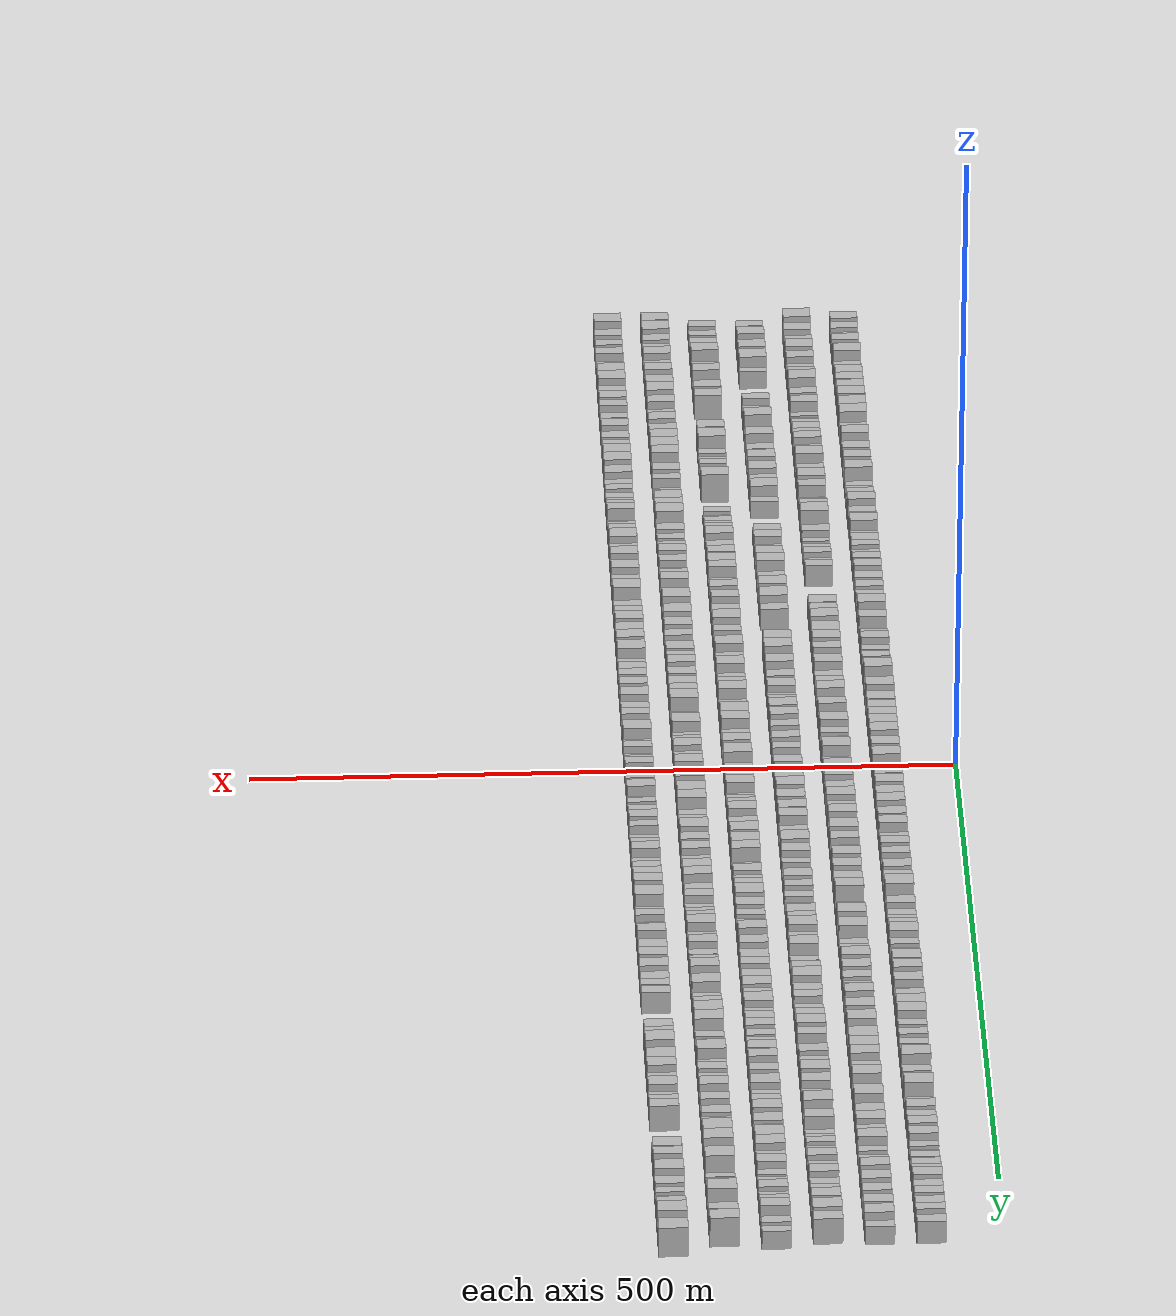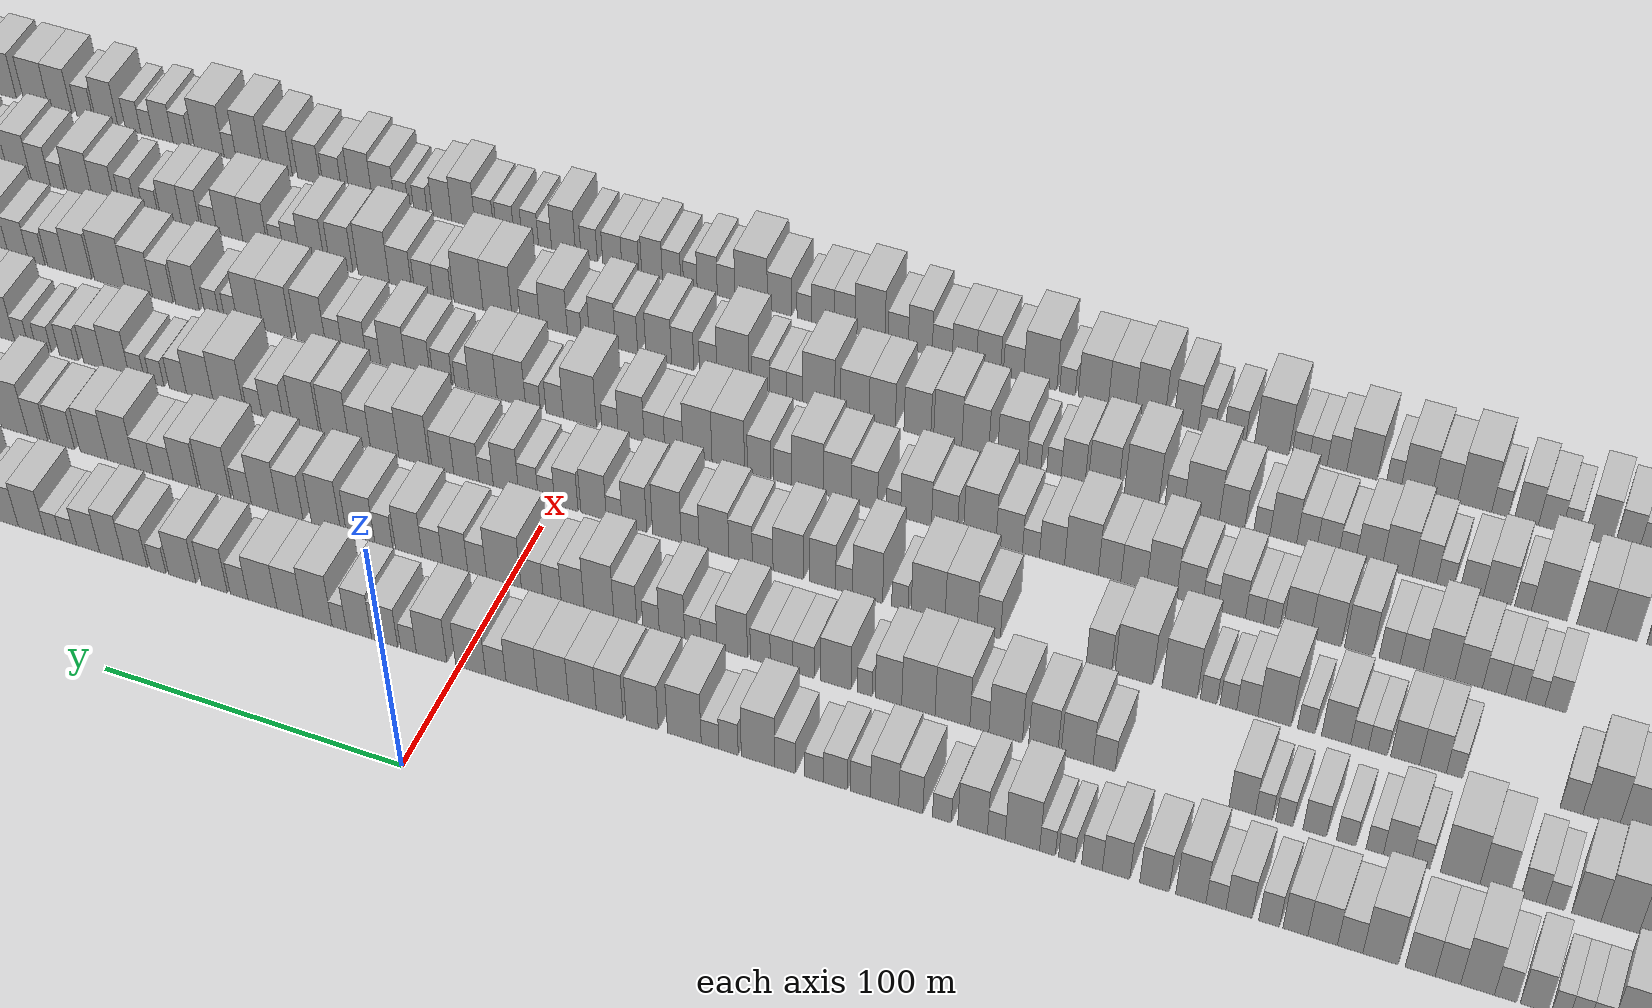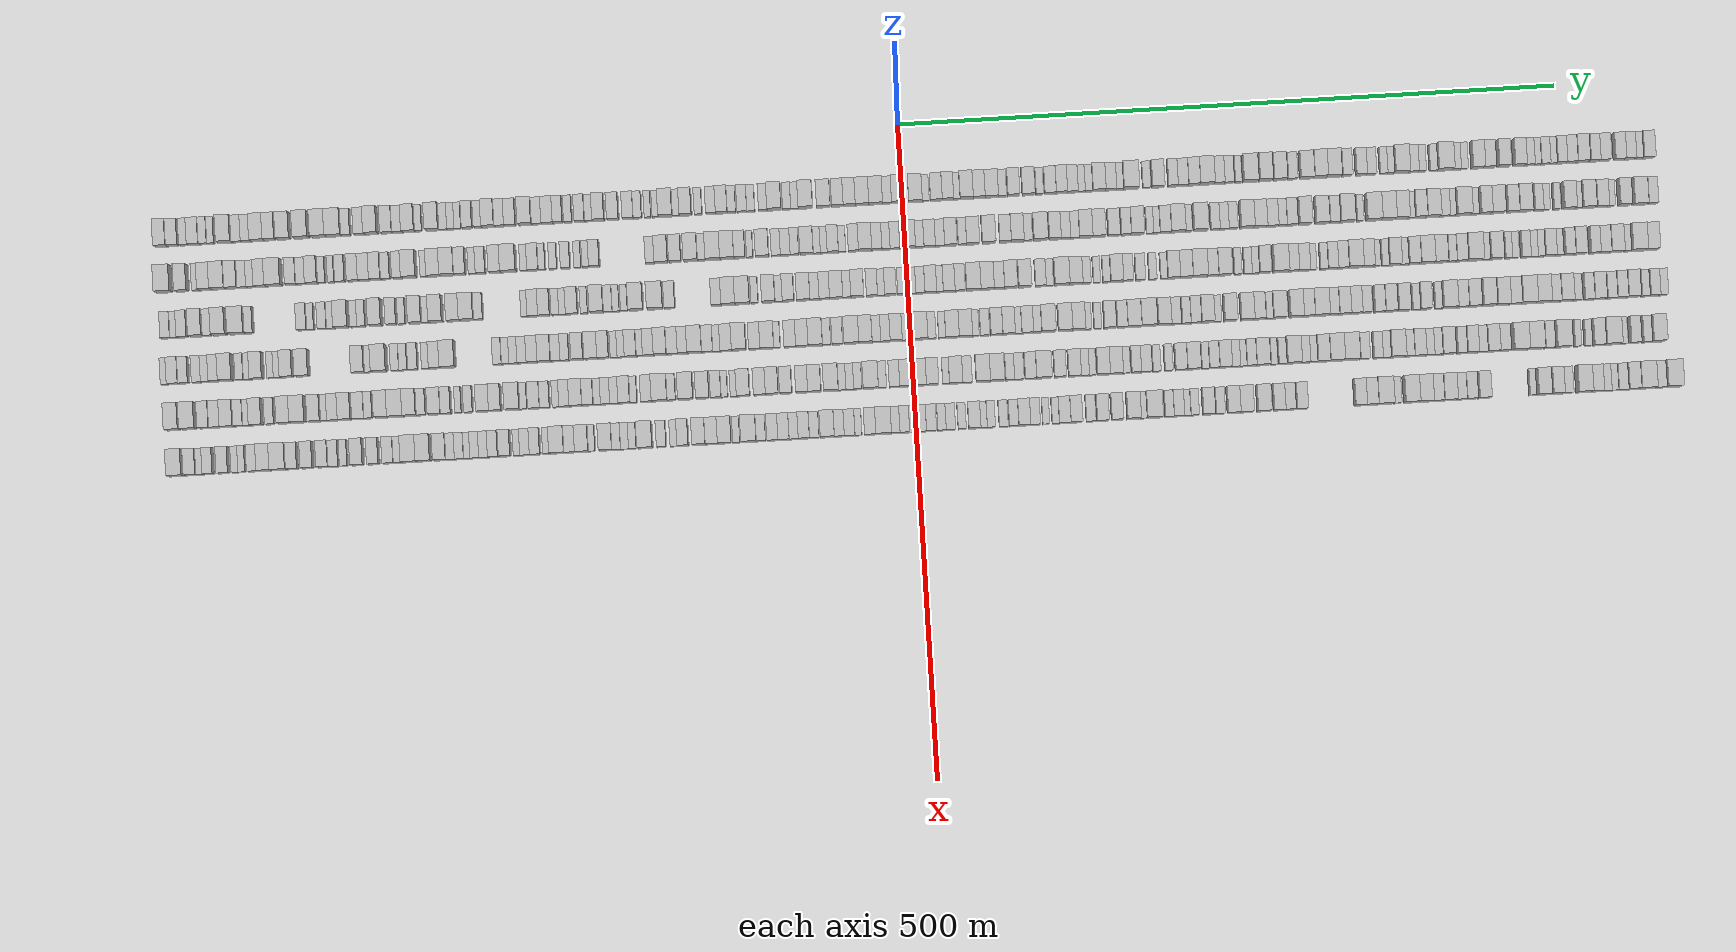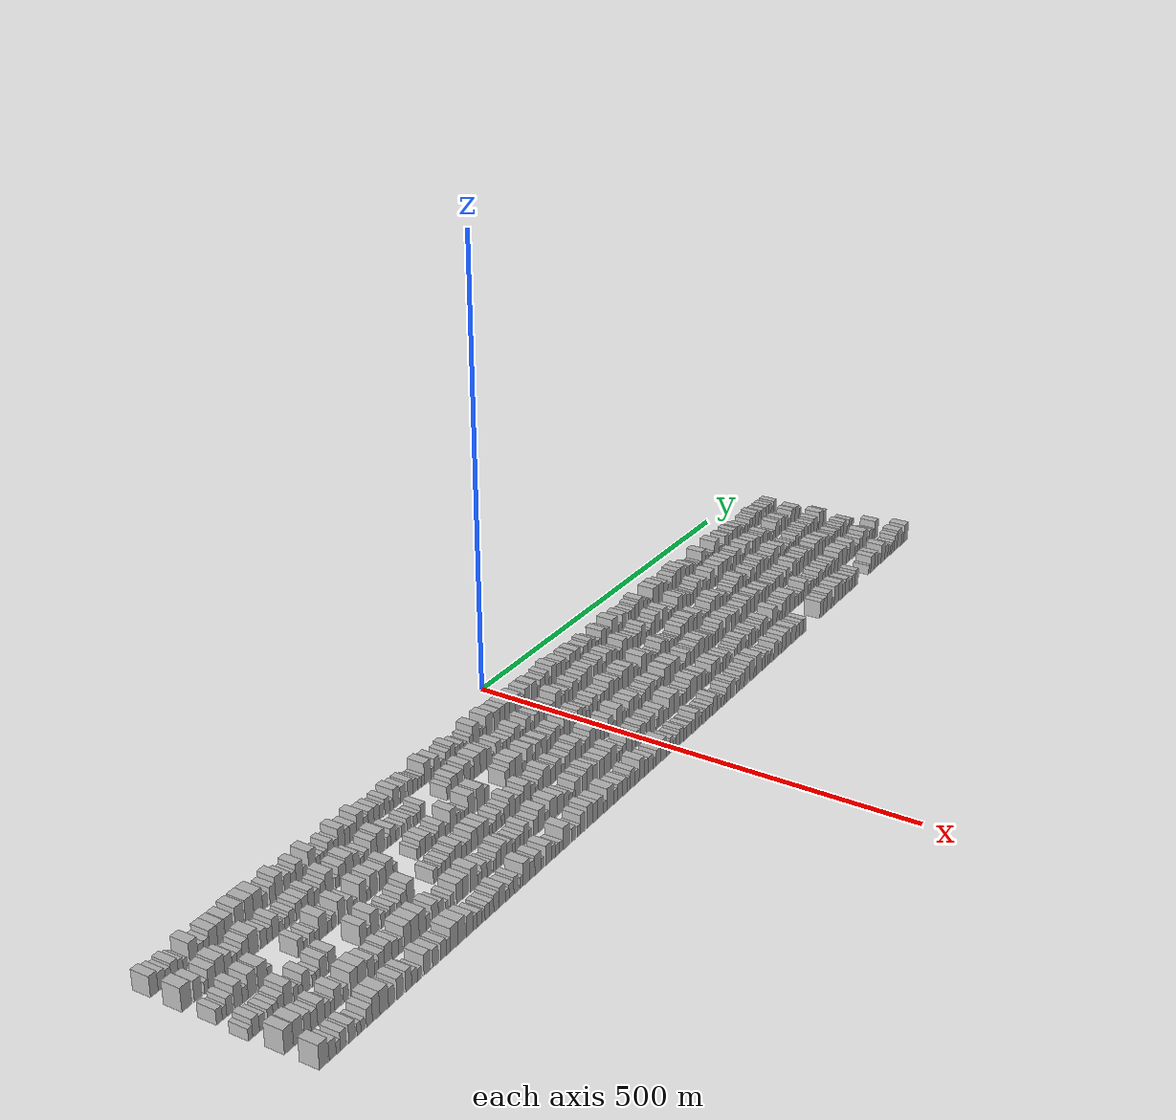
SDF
<sdf version="1.6">
 <world name="default">
  <scene>
   <sky><clouds><speed>12</speed></clouds></sky>
   <ambient>0.4 0.4 0.4 1</ambient>
   <background>0.7 0.7 0.7 1</background>
   <shadows>1</shadows>
  </scene>
  <gravity>0 0 -9.8066</gravity>
  <magnetic_field>6e-06 2.3e-05 -4.2e-05</magnetic_field>
  <physics default="0" name="default_physics" type="ode">
   <ode>
    <solver>
     <type>quick</type>
     <iters>10</iters>
     <sor>1.0</sor>
     <use_dynamic_moi_rescaling>0</use_dynamic_moi_rescaling>
    </solver>
    <constraints>
     <cfm>0</cfm>
     <erp>0.2</erp>
     <contact_max_correcting_vel>100</contact_max_correcting_vel>
     <contact_surface_layer>0.001</contact_surface_layer>
    </constraints>
   </ode>
   <max_step_size>0.004</max_step_size>
   <real_time_factor>1</real_time_factor>
   <real_time_update_rate>250</real_time_update_rate>
  </physics>
  <light name="sun" type="directional">
   <pose>0 0 10 0 0 0</pose>
   <diffuse>0.8 0.8 0.8 1</diffuse>
   <specular>0.2 0.2 0.2 1</specular>
   <attenuation>
    <range>1000</range>
    <constant>0.9</constant>
    <linear>0.01</linear>
    <quadratic>0.001</quadratic>
   </attenuation>
   <direction>-0.5 0.1 -0.9</direction>
  </light>
  <model name="building_1">
   <static>1</static>
   <pose>50.0000 -564.3511 0 0.000000 0.000000 0.000000</pose>
   <link name="link">
    <pose>0 0 10.50 0 0 0</pose>
    <collision name="collision"><geometry><box><size>20.0000 9.2977 21.0000</size></box></geometry></collision>
    <visual name="visual">
     <cast_shadows>0</cast_shadows>
     <geometry><box><size>20.0000 9.2977 21.0000</size></box></geometry>
     <material>
      <script>
       <uri>model://HANNAS_wall/materials/scripts</uri>
       <uri>model://HANNAS_wall/materials/textures</uri>
       <name>vrc/HANNAS_wall</name>
      </script>
     </material>
    </visual>
   </link>
  </model>
  <model name="building_2">
   <static>1</static>
   <pose>50.0000 -555.3722 0 0.000000 0.000000 0.000000</pose>
   <link name="link">
    <pose>0 0 9.00 0 0 0</pose>
    <collision name="collision"><geometry><box><size>20.0000 8.6602 18.0000</size></box></geometry></collision>
    <visual name="visual">
     <cast_shadows>0</cast_shadows>
     <geometry><box><size>20.0000 8.6602 18.0000</size></box></geometry>
     <material>
      <script>
       <uri>model://HANNAS_wall/materials/scripts</uri>
       <uri>model://HANNAS_wall/materials/textures</uri>
       <name>vrc/HANNAS_wall</name>
      </script>
     </material>
    </visual>
   </link>
  </model>
  <model name="building_3">
   <static>1</static>
   <pose>50.0000 -546.9544 0 0.000000 0.000000 0.000000</pose>
   <link name="link">
    <pose>0 0 7.50 0 0 0</pose>
    <collision name="collision"><geometry><box><size>20.0000 6.1754 15.0000</size></box></geometry></collision>
    <visual name="visual">
     <cast_shadows>0</cast_shadows>
     <geometry><box><size>20.0000 6.1754 15.0000</size></box></geometry>
     <material>
      <script>
       <uri>model://HANNAS_wall/materials/scripts</uri>
       <uri>model://HANNAS_wall/materials/textures</uri>
       <name>vrc/HANNAS_wall</name>
      </script>
     </material>
    </visual>
   </link>
  </model>
  <model name="building_4">
   <static>1</static>
   <pose>50.0000 -539.5403 0 0.000000 0.000000 0.000000</pose>
   <link name="link">
    <pose>0 0 9.00 0 0 0</pose>
    <collision name="collision"><geometry><box><size>20.0000 8.6526 18.0000</size></box></geometry></collision>
    <visual name="visual">
     <cast_shadows>0</cast_shadows>
     <geometry><box><size>20.0000 8.6526 18.0000</size></box></geometry>
     <material>
      <script>
       <uri>model://HANNAS_wall/materials/scripts</uri>
       <uri>model://HANNAS_wall/materials/textures</uri>
       <name>vrc/HANNAS_wall</name>
      </script>
     </material>
    </visual>
   </link>
  </model>
  <model name="building_5">
   <static>1</static>
   <pose>50.0000 -532.1330 0 0.000000 0.000000 0.000000</pose>
   <link name="link">
    <pose>0 0 7.50 0 0 0</pose>
    <collision name="collision"><geometry><box><size>20.0000 6.1619 15.0000</size></box></geometry></collision>
    <visual name="visual">
     <cast_shadows>0</cast_shadows>
     <geometry><box><size>20.0000 6.1619 15.0000</size></box></geometry>
     <material>
      <script>
       <uri>model://HANNAS_wall/materials/scripts</uri>
       <uri>model://HANNAS_wall/materials/textures</uri>
       <name>vrc/HANNAS_wall</name>
      </script>
     </material>
    </visual>
   </link>
  </model>
  <model name="building_6">
   <static>1</static>
   <pose>50.0000 -526.5214 0 0.000000 0.000000 0.000000</pose>
   <link name="link">
    <pose>0 0 6.00 0 0 0</pose>
    <collision name="collision"><geometry><box><size>20.0000 5.0614 12.0000</size></box></geometry></collision>
    <visual name="visual">
     <cast_shadows>0</cast_shadows>
     <geometry><box><size>20.0000 5.0614 12.0000</size></box></geometry>
     <material>
      <script>
       <uri>model://HANNAS_wall/materials/scripts</uri>
       <uri>model://HANNAS_wall/materials/textures</uri>
       <name>vrc/HANNAS_wall</name>
      </script>
     </material>
    </visual>
   </link>
  </model>
  <model name="building_7">
   <static>1</static>
   <pose>50.0000 -515.6604 0 0.000000 0.000000 0.000000</pose>
   <link name="link">
    <pose>0 0 12.00 0 0 0</pose>
    <collision name="collision"><geometry><box><size>20.0000 10.6606 24.0000</size></box></geometry></collision>
    <visual name="visual">
     <cast_shadows>0</cast_shadows>
     <geometry><box><size>20.0000 10.6606 24.0000</size></box></geometry>
     <material>
      <script>
       <uri>model://HANNAS_wall/materials/scripts</uri>
       <uri>model://HANNAS_wall/materials/textures</uri>
       <name>vrc/HANNAS_wall</name>
      </script>
     </material>
    </visual>
   </link>
  </model>
  <model name="building_8">
   <static>1</static>
   <pose>50.0000 -506.7979 0 0.000000 0.000000 0.000000</pose>
   <link name="link">
    <pose>0 0 7.50 0 0 0</pose>
    <collision name="collision"><geometry><box><size>20.0000 7.0643 15.0000</size></box></geometry></collision>
    <visual name="visual">
     <cast_shadows>0</cast_shadows>
     <geometry><box><size>20.0000 7.0643 15.0000</size></box></geometry>
     <material>
      <script>
       <uri>model://HANNAS_wall/materials/scripts</uri>
       <uri>model://HANNAS_wall/materials/textures</uri>
       <name>vrc/HANNAS_wall</name>
      </script>
     </material>
    </visual>
   </link>
  </model>
  <model name="building_9">
   <static>1</static>
   <pose>50.0000 -499.7138 0 0.000000 0.000000 0.000000</pose>
   <link name="link">
    <pose>0 0 7.50 0 0 0</pose>
    <collision name="collision"><geometry><box><size>20.0000 7.1040 15.0000</size></box></geometry></collision>
    <visual name="visual">
     <cast_shadows>0</cast_shadows>
     <geometry><box><size>20.0000 7.1040 15.0000</size></box></geometry>
     <material>
      <script>
       <uri>model://HANNAS_wall/materials/scripts</uri>
       <uri>model://HANNAS_wall/materials/textures</uri>
       <name>vrc/HANNAS_wall</name>
      </script>
     </material>
    </visual>
   </link>
  </model>
  <model name="building_10">
   <static>1</static>
   <pose>50.0000 -491.1028 0 0.000000 0.000000 0.000000</pose>
   <link name="link">
    <pose>0 0 10.50 0 0 0</pose>
    <collision name="collision"><geometry><box><size>20.0000 10.1180 21.0000</size></box></geometry></collision>
    <visual name="visual">
     <cast_shadows>0</cast_shadows>
     <geometry><box><size>20.0000 10.1180 21.0000</size></box></geometry>
     <material>
      <script>
       <uri>model://HANNAS_wall/materials/scripts</uri>
       <uri>model://HANNAS_wall/materials/textures</uri>
       <name>vrc/HANNAS_wall</name>
      </script>
     </material>
    </visual>
   </link>
  </model>
  <model name="building_11">
   <static>1</static>
   <pose>50.0000 -481.6305 0 0.000000 0.000000 0.000000</pose>
   <link name="link">
    <pose>0 0 10.50 0 0 0</pose>
    <collision name="collision"><geometry><box><size>20.0000 8.8265 21.0000</size></box></geometry></collision>
    <visual name="visual">
     <cast_shadows>0</cast_shadows>
     <geometry><box><size>20.0000 8.8265 21.0000</size></box></geometry>
     <material>
      <script>
       <uri>model://HANNAS_wall/materials/scripts</uri>
       <uri>model://HANNAS_wall/materials/textures</uri>
       <name>vrc/HANNAS_wall</name>
      </script>
     </material>
    </visual>
   </link>
  </model>
  <model name="building_12">
   <static>1</static>
   <pose>50.0000 -471.1323 0 0.000000 0.000000 0.000000</pose>
   <link name="link">
    <pose>0 0 10.50 0 0 0</pose>
    <collision name="collision"><geometry><box><size>20.0000 10.1699 21.0000</size></box></geometry></collision>
    <visual name="visual">
     <cast_shadows>0</cast_shadows>
     <geometry><box><size>20.0000 10.1699 21.0000</size></box></geometry>
     <material>
      <script>
       <uri>model://HANNAS_wall/materials/scripts</uri>
       <uri>model://HANNAS_wall/materials/textures</uri>
       <name>vrc/HANNAS_wall</name>
      </script>
     </material>
    </visual>
   </link>
  </model>
  <model name="building_13">
   <static>1</static>
   <pose>50.0000 -457.4767 0 0.000000 0.000000 0.000000</pose>
   <link name="link">
    <pose>0 0 12.00 0 0 0</pose>
    <collision name="collision"><geometry><box><size>20.0000 11.1413 24.0000</size></box></geometry></collision>
    <visual name="visual">
     <cast_shadows>0</cast_shadows>
     <geometry><box><size>20.0000 11.1413 24.0000</size></box></geometry>
     <material>
      <script>
       <uri>model://HANNAS_wall/materials/scripts</uri>
       <uri>model://HANNAS_wall/materials/textures</uri>
       <name>vrc/HANNAS_wall</name>
      </script>
     </material>
    </visual>
   </link>
  </model>
  <model name="building_14">
   <static>1</static>
   <pose>50.0000 -444.3810 0 0.000000 0.000000 0.000000</pose>
   <link name="link">
    <pose>0 0 12.00 0 0 0</pose>
    <collision name="collision"><geometry><box><size>20.0000 11.0501 24.0000</size></box></geometry></collision>
    <visual name="visual">
     <cast_shadows>0</cast_shadows>
     <geometry><box><size>20.0000 11.0501 24.0000</size></box></geometry>
     <material>
      <script>
       <uri>model://HANNAS_wall/materials/scripts</uri>
       <uri>model://HANNAS_wall/materials/textures</uri>
       <name>vrc/HANNAS_wall</name>
      </script>
     </material>
    </visual>
   </link>
  </model>
  <model name="building_15">
   <static>1</static>
   <pose>50.0000 -432.9555 0 0.000000 0.000000 0.000000</pose>
   <link name="link">
    <pose>0 0 12.00 0 0 0</pose>
    <collision name="collision"><geometry><box><size>20.0000 11.8011 24.0000</size></box></geometry></collision>
    <visual name="visual">
     <cast_shadows>0</cast_shadows>
     <geometry><box><size>20.0000 11.8011 24.0000</size></box></geometry>
     <material>
      <script>
       <uri>model://HANNAS_wall/materials/scripts</uri>
       <uri>model://HANNAS_wall/materials/textures</uri>
       <name>vrc/HANNAS_wall</name>
      </script>
     </material>
    </visual>
   </link>
  </model>
  <model name="building_16">
   <static>1</static>
   <pose>50.0000 -423.6860 0 0.000000 0.000000 0.000000</pose>
   <link name="link">
    <pose>0 0 7.50 0 0 0</pose>
    <collision name="collision"><geometry><box><size>20.0000 6.7377 15.0000</size></box></geometry></collision>
    <visual name="visual">
     <cast_shadows>0</cast_shadows>
     <geometry><box><size>20.0000 6.7377 15.0000</size></box></geometry>
     <material>
      <script>
       <uri>model://HANNAS_wall/materials/scripts</uri>
       <uri>model://HANNAS_wall/materials/textures</uri>
       <name>vrc/HANNAS_wall</name>
      </script>
     </material>
    </visual>
   </link>
  </model>
  <model name="building_17">
   <static>1</static>
   <pose>50.0000 -413.3966 0 0.000000 0.000000 0.000000</pose>
   <link name="link">
    <pose>0 0 9.00 0 0 0</pose>
    <collision name="collision"><geometry><box><size>20.0000 7.8412 18.0000</size></box></geometry></collision>
    <visual name="visual">
     <cast_shadows>0</cast_shadows>
     <geometry><box><size>20.0000 7.8412 18.0000</size></box></geometry>
     <material>
      <script>
       <uri>model://HANNAS_wall/materials/scripts</uri>
       <uri>model://HANNAS_wall/materials/textures</uri>
       <name>vrc/HANNAS_wall</name>
      </script>
     </material>
    </visual>
   </link>
  </model>
  <model name="building_18">
   <static>1</static>
   <pose>50.0000 -404.3822 0 0.000000 0.000000 0.000000</pose>
   <link name="link">
    <pose>0 0 12.00 0 0 0</pose>
    <collision name="collision"><geometry><box><size>20.0000 10.1875 24.0000</size></box></geometry></collision>
    <visual name="visual">
     <cast_shadows>0</cast_shadows>
     <geometry><box><size>20.0000 10.1875 24.0000</size></box></geometry>
     <material>
      <script>
       <uri>model://HANNAS_wall/materials/scripts</uri>
       <uri>model://HANNAS_wall/materials/textures</uri>
       <name>vrc/HANNAS_wall</name>
      </script>
     </material>
    </visual>
   </link>
  </model>
  <model name="building_19">
   <static>1</static>
   <pose>50.0000 -392.8344 0 0.000000 0.000000 0.000000</pose>
   <link name="link">
    <pose>0 0 9.00 0 0 0</pose>
    <collision name="collision"><geometry><box><size>20.0000 8.9080 18.0000</size></box></geometry></collision>
    <visual name="visual">
     <cast_shadows>0</cast_shadows>
     <geometry><box><size>20.0000 8.9080 18.0000</size></box></geometry>
     <material>
      <script>
       <uri>model://HANNAS_wall/materials/scripts</uri>
       <uri>model://HANNAS_wall/materials/textures</uri>
       <name>vrc/HANNAS_wall</name>
      </script>
     </material>
    </visual>
   </link>
  </model>
  <model name="building_20">
   <static>1</static>
   <pose>50.0000 -384.7069 0 0.000000 0.000000 0.000000</pose>
   <link name="link">
    <pose>0 0 7.50 0 0 0</pose>
    <collision name="collision"><geometry><box><size>20.0000 7.3471 15.0000</size></box></geometry></collision>
    <visual name="visual">
     <cast_shadows>0</cast_shadows>
     <geometry><box><size>20.0000 7.3471 15.0000</size></box></geometry>
     <material>
      <script>
       <uri>model://HANNAS_wall/materials/scripts</uri>
       <uri>model://HANNAS_wall/materials/textures</uri>
       <name>vrc/HANNAS_wall</name>
      </script>
     </material>
    </visual>
   </link>
  </model>
  <model name="building_21">
   <static>1</static>
   <pose>50.0000 -376.1818 0 0.000000 0.000000 0.000000</pose>
   <link name="link">
    <pose>0 0 10.50 0 0 0</pose>
    <collision name="collision"><geometry><box><size>20.0000 9.7030 21.0000</size></box></geometry></collision>
    <visual name="visual">
     <cast_shadows>0</cast_shadows>
     <geometry><box><size>20.0000 9.7030 21.0000</size></box></geometry>
     <material>
      <script>
       <uri>model://HANNAS_wall/materials/scripts</uri>
       <uri>model://HANNAS_wall/materials/textures</uri>
       <name>vrc/HANNAS_wall</name>
      </script>
     </material>
    </visual>
   </link>
  </model>
  <model name="building_22">
   <static>1</static>
   <pose>50.0000 -368.6745 0 0.000000 0.000000 0.000000</pose>
   <link name="link">
    <pose>0 0 6.00 0 0 0</pose>
    <collision name="collision"><geometry><box><size>20.0000 5.3117 12.0000</size></box></geometry></collision>
    <visual name="visual">
     <cast_shadows>0</cast_shadows>
     <geometry><box><size>20.0000 5.3117 12.0000</size></box></geometry>
     <material>
      <script>
       <uri>model://HANNAS_wall/materials/scripts</uri>
       <uri>model://HANNAS_wall/materials/textures</uri>
       <name>vrc/HANNAS_wall</name>
      </script>
     </material>
    </visual>
   </link>
  </model>
  <model name="building_23">
   <static>1</static>
   <pose>50.0000 -357.9048 0 0.000000 0.000000 0.000000</pose>
   <link name="link">
    <pose>0 0 12.00 0 0 0</pose>
    <collision name="collision"><geometry><box><size>20.0000 10.2275 24.0000</size></box></geometry></collision>
    <visual name="visual">
     <cast_shadows>0</cast_shadows>
     <geometry><box><size>20.0000 10.2275 24.0000</size></box></geometry>
     <material>
      <script>
       <uri>model://HANNAS_wall/materials/scripts</uri>
       <uri>model://HANNAS_wall/materials/textures</uri>
       <name>vrc/HANNAS_wall</name>
      </script>
     </material>
    </visual>
   </link>
  </model>
  <model name="building_24">
   <static>1</static>
   <pose>50.0000 -349.7951 0 0.000000 0.000000 0.000000</pose>
   <link name="link">
    <pose>0 0 6.00 0 0 0</pose>
    <collision name="collision"><geometry><box><size>20.0000 5.9919 12.0000</size></box></geometry></collision>
    <visual name="visual">
     <cast_shadows>0</cast_shadows>
     <geometry><box><size>20.0000 5.9919 12.0000</size></box></geometry>
     <material>
      <script>
       <uri>model://HANNAS_wall/materials/scripts</uri>
       <uri>model://HANNAS_wall/materials/textures</uri>
       <name>vrc/HANNAS_wall</name>
      </script>
     </material>
    </visual>
   </link>
  </model>
  <model name="building_25">
   <static>1</static>
   <pose>50.0000 -344.0235 0 0.000000 0.000000 0.000000</pose>
   <link name="link">
    <pose>0 0 6.00 0 0 0</pose>
    <collision name="collision"><geometry><box><size>20.0000 5.5515 12.0000</size></box></geometry></collision>
    <visual name="visual">
     <cast_shadows>0</cast_shadows>
     <geometry><box><size>20.0000 5.5515 12.0000</size></box></geometry>
     <material>
      <script>
       <uri>model://HANNAS_wall/materials/scripts</uri>
       <uri>model://HANNAS_wall/materials/textures</uri>
       <name>vrc/HANNAS_wall</name>
      </script>
     </material>
    </visual>
   </link>
  </model>
  <model name="building_26">
   <static>1</static>
   <pose>50.0000 -338.7421 0 0.000000 0.000000 0.000000</pose>
   <link name="link">
    <pose>0 0 6.00 0 0 0</pose>
    <collision name="collision"><geometry><box><size>20.0000 5.0114 12.0000</size></box></geometry></collision>
    <visual name="visual">
     <cast_shadows>0</cast_shadows>
     <geometry><box><size>20.0000 5.0114 12.0000</size></box></geometry>
     <material>
      <script>
       <uri>model://HANNAS_wall/materials/scripts</uri>
       <uri>model://HANNAS_wall/materials/textures</uri>
       <name>vrc/HANNAS_wall</name>
      </script>
     </material>
    </visual>
   </link>
  </model>
  <model name="building_27">
   <static>1</static>
   <pose>50.0000 -331.3563 0 0.000000 0.000000 0.000000</pose>
   <link name="link">
    <pose>0 0 9.00 0 0 0</pose>
    <collision name="collision"><geometry><box><size>20.0000 7.7601 18.0000</size></box></geometry></collision>
    <visual name="visual">
     <cast_shadows>0</cast_shadows>
     <geometry><box><size>20.0000 7.7601 18.0000</size></box></geometry>
     <material>
      <script>
       <uri>model://HANNAS_wall/materials/scripts</uri>
       <uri>model://HANNAS_wall/materials/textures</uri>
       <name>vrc/HANNAS_wall</name>
      </script>
     </material>
    </visual>
   </link>
  </model>
  <model name="building_28">
   <static>1</static>
   <pose>50.0000 -323.2991 0 0.000000 0.000000 0.000000</pose>
   <link name="link">
    <pose>0 0 7.50 0 0 0</pose>
    <collision name="collision"><geometry><box><size>20.0000 6.3543 15.0000</size></box></geometry></collision>
    <visual name="visual">
     <cast_shadows>0</cast_shadows>
     <geometry><box><size>20.0000 6.3543 15.0000</size></box></geometry>
     <material>
      <script>
       <uri>model://HANNAS_wall/materials/scripts</uri>
       <uri>model://HANNAS_wall/materials/textures</uri>
       <name>vrc/HANNAS_wall</name>
      </script>
     </material>
    </visual>
   </link>
  </model>
  <model name="building_29">
   <static>1</static>
   <pose>50.0000 -315.2919 0 0.000000 0.000000 0.000000</pose>
   <link name="link">
    <pose>0 0 12.00 0 0 0</pose>
    <collision name="collision"><geometry><box><size>20.0000 9.6601 24.0000</size></box></geometry></collision>
    <visual name="visual">
     <cast_shadows>0</cast_shadows>
     <geometry><box><size>20.0000 9.6601 24.0000</size></box></geometry>
     <material>
      <script>
       <uri>model://HANNAS_wall/materials/scripts</uri>
       <uri>model://HANNAS_wall/materials/textures</uri>
       <name>vrc/HANNAS_wall</name>
      </script>
     </material>
    </visual>
   </link>
  </model>
  <model name="building_30">
   <static>1</static>
   <pose>50.0000 -306.8235 0 0.000000 0.000000 0.000000</pose>
   <link name="link">
    <pose>0 0 9.00 0 0 0</pose>
    <collision name="collision"><geometry><box><size>20.0000 7.2766 18.0000</size></box></geometry></collision>
    <visual name="visual">
     <cast_shadows>0</cast_shadows>
     <geometry><box><size>20.0000 7.2766 18.0000</size></box></geometry>
     <material>
      <script>
       <uri>model://HANNAS_wall/materials/scripts</uri>
       <uri>model://HANNAS_wall/materials/textures</uri>
       <name>vrc/HANNAS_wall</name>
      </script>
     </material>
    </visual>
   </link>
  </model>
  <model name="building_31">
   <static>1</static>
   <pose>50.0000 -298.8710 0 0.000000 0.000000 0.000000</pose>
   <link name="link">
    <pose>0 0 9.00 0 0 0</pose>
    <collision name="collision"><geometry><box><size>20.0000 8.6285 18.0000</size></box></geometry></collision>
    <visual name="visual">
     <cast_shadows>0</cast_shadows>
     <geometry><box><size>20.0000 8.6285 18.0000</size></box></geometry>
     <material>
      <script>
       <uri>model://HANNAS_wall/materials/scripts</uri>
       <uri>model://HANNAS_wall/materials/textures</uri>
       <name>vrc/HANNAS_wall</name>
      </script>
     </material>
    </visual>
   </link>
  </model>
  <model name="building_32">
   <static>1</static>
   <pose>50.0000 -287.4210 0 0.000000 0.000000 0.000000</pose>
   <link name="link">
    <pose>0 0 12.00 0 0 0</pose>
    <collision name="collision"><geometry><box><size>20.0000 10.2715 24.0000</size></box></geometry></collision>
    <visual name="visual">
     <cast_shadows>0</cast_shadows>
     <geometry><box><size>20.0000 10.2715 24.0000</size></box></geometry>
     <material>
      <script>
       <uri>model://HANNAS_wall/materials/scripts</uri>
       <uri>model://HANNAS_wall/materials/textures</uri>
       <name>vrc/HANNAS_wall</name>
      </script>
     </material>
    </visual>
   </link>
  </model>
  <model name="building_33">
   <static>1</static>
   <pose>50.0000 -278.5787 0 0.000000 0.000000 0.000000</pose>
   <link name="link">
    <pose>0 0 7.50 0 0 0</pose>
    <collision name="collision"><geometry><box><size>20.0000 7.4130 15.0000</size></box></geometry></collision>
    <visual name="visual">
     <cast_shadows>0</cast_shadows>
     <geometry><box><size>20.0000 7.4130 15.0000</size></box></geometry>
     <material>
      <script>
       <uri>model://HANNAS_wall/materials/scripts</uri>
       <uri>model://HANNAS_wall/materials/textures</uri>
       <name>vrc/HANNAS_wall</name>
      </script>
     </material>
    </visual>
   </link>
  </model>
  <model name="building_34">
   <static>1</static>
   <pose>50.0000 -270.5696 0 0.000000 0.000000 0.000000</pose>
   <link name="link">
    <pose>0 0 9.00 0 0 0</pose>
    <collision name="collision"><geometry><box><size>20.0000 8.6050 18.0000</size></box></geometry></collision>
    <visual name="visual">
     <cast_shadows>0</cast_shadows>
     <geometry><box><size>20.0000 8.6050 18.0000</size></box></geometry>
     <material>
      <script>
       <uri>model://HANNAS_wall/materials/scripts</uri>
       <uri>model://HANNAS_wall/materials/textures</uri>
       <name>vrc/HANNAS_wall</name>
      </script>
     </material>
    </visual>
   </link>
  </model>
  <model name="building_35">
   <static>1</static>
   <pose>50.0000 -262.5826 0 0.000000 0.000000 0.000000</pose>
   <link name="link">
    <pose>0 0 9.00 0 0 0</pose>
    <collision name="collision"><geometry><box><size>20.0000 7.3691 18.0000</size></box></geometry></collision>
    <visual name="visual">
     <cast_shadows>0</cast_shadows>
     <geometry><box><size>20.0000 7.3691 18.0000</size></box></geometry>
     <material>
      <script>
       <uri>model://HANNAS_wall/materials/scripts</uri>
       <uri>model://HANNAS_wall/materials/textures</uri>
       <name>vrc/HANNAS_wall</name>
      </script>
     </material>
    </visual>
   </link>
  </model>
  <model name="building_36">
   <static>1</static>
   <pose>50.0000 -254.8411 0 0.000000 0.000000 0.000000</pose>
   <link name="link">
    <pose>0 0 7.50 0 0 0</pose>
    <collision name="collision"><geometry><box><size>20.0000 6.1138 15.0000</size></box></geometry></collision>
    <visual name="visual">
     <cast_shadows>0</cast_shadows>
     <geometry><box><size>20.0000 6.1138 15.0000</size></box></geometry>
     <material>
      <script>
       <uri>model://HANNAS_wall/materials/scripts</uri>
       <uri>model://HANNAS_wall/materials/textures</uri>
       <name>vrc/HANNAS_wall</name>
      </script>
     </material>
    </visual>
   </link>
  </model>
  <model name="building_37">
   <static>1</static>
   <pose>50.0000 -245.9283 0 0.000000 0.000000 0.000000</pose>
   <link name="link">
    <pose>0 0 9.00 0 0 0</pose>
    <collision name="collision"><geometry><box><size>20.0000 7.7118 18.0000</size></box></geometry></collision>
    <visual name="visual">
     <cast_shadows>0</cast_shadows>
     <geometry><box><size>20.0000 7.7118 18.0000</size></box></geometry>
     <material>
      <script>
       <uri>model://HANNAS_wall/materials/scripts</uri>
       <uri>model://HANNAS_wall/materials/textures</uri>
       <name>vrc/HANNAS_wall</name>
      </script>
     </material>
    </visual>
   </link>
  </model>
  <model name="building_38">
   <static>1</static>
   <pose>50.0000 -239.0801 0 0.000000 0.000000 0.000000</pose>
   <link name="link">
    <pose>0 0 6.00 0 0 0</pose>
    <collision name="collision"><geometry><box><size>20.0000 5.9845 12.0000</size></box></geometry></collision>
    <visual name="visual">
     <cast_shadows>0</cast_shadows>
     <geometry><box><size>20.0000 5.9845 12.0000</size></box></geometry>
     <material>
      <script>
       <uri>model://HANNAS_wall/materials/scripts</uri>
       <uri>model://HANNAS_wall/materials/textures</uri>
       <name>vrc/HANNAS_wall</name>
      </script>
     </material>
    </visual>
   </link>
  </model>
  <model name="building_39">
   <static>1</static>
   <pose>50.0000 -231.5981 0 0.000000 0.000000 0.000000</pose>
   <link name="link">
    <pose>0 0 10.50 0 0 0</pose>
    <collision name="collision"><geometry><box><size>20.0000 8.9795 21.0000</size></box></geometry></collision>
    <visual name="visual">
     <cast_shadows>0</cast_shadows>
     <geometry><box><size>20.0000 8.9795 21.0000</size></box></geometry>
     <material>
      <script>
       <uri>model://HANNAS_wall/materials/scripts</uri>
       <uri>model://HANNAS_wall/materials/textures</uri>
       <name>vrc/HANNAS_wall</name>
      </script>
     </material>
    </visual>
   </link>
  </model>
  <model name="building_40">
   <static>1</static>
   <pose>50.0000 -220.6966 0 0.000000 0.000000 0.000000</pose>
   <link name="link">
    <pose>0 0 9.00 0 0 0</pose>
    <collision name="collision"><geometry><box><size>20.0000 8.8235 18.0000</size></box></geometry></collision>
    <visual name="visual">
     <cast_shadows>0</cast_shadows>
     <geometry><box><size>20.0000 8.8235 18.0000</size></box></geometry>
     <material>
      <script>
       <uri>model://HANNAS_wall/materials/scripts</uri>
       <uri>model://HANNAS_wall/materials/textures</uri>
       <name>vrc/HANNAS_wall</name>
      </script>
     </material>
    </visual>
   </link>
  </model>
  <model name="building_41">
   <static>1</static>
   <pose>50.0000 -209.1434 0 0.000000 0.000000 0.000000</pose>
   <link name="link">
    <pose>0 0 9.00 0 0 0</pose>
    <collision name="collision"><geometry><box><size>20.0000 8.2830 18.0000</size></box></geometry></collision>
    <visual name="visual">
     <cast_shadows>0</cast_shadows>
     <geometry><box><size>20.0000 8.2830 18.0000</size></box></geometry>
     <material>
      <script>
       <uri>model://HANNAS_wall/materials/scripts</uri>
       <uri>model://HANNAS_wall/materials/textures</uri>
       <name>vrc/HANNAS_wall</name>
      </script>
     </material>
    </visual>
   </link>
  </model>
  <model name="building_42">
   <static>1</static>
   <pose>50.0000 -201.8700 0 0.000000 0.000000 0.000000</pose>
   <link name="link">
    <pose>0 0 7.50 0 0 0</pose>
    <collision name="collision"><geometry><box><size>20.0000 6.2637 15.0000</size></box></geometry></collision>
    <visual name="visual">
     <cast_shadows>0</cast_shadows>
     <geometry><box><size>20.0000 6.2637 15.0000</size></box></geometry>
     <material>
      <script>
       <uri>model://HANNAS_wall/materials/scripts</uri>
       <uri>model://HANNAS_wall/materials/textures</uri>
       <name>vrc/HANNAS_wall</name>
      </script>
     </material>
    </visual>
   </link>
  </model>
  <model name="building_43">
   <static>1</static>
   <pose>50.0000 -194.2390 0 0.000000 0.000000 0.000000</pose>
   <link name="link">
    <pose>0 0 6.00 0 0 0</pose>
    <collision name="collision"><geometry><box><size>20.0000 4.9983 12.0000</size></box></geometry></collision>
    <visual name="visual">
     <cast_shadows>0</cast_shadows>
     <geometry><box><size>20.0000 4.9983 12.0000</size></box></geometry>
     <material>
      <script>
       <uri>model://HANNAS_wall/materials/scripts</uri>
       <uri>model://HANNAS_wall/materials/textures</uri>
       <name>vrc/HANNAS_wall</name>
      </script>
     </material>
    </visual>
   </link>
  </model>
  <model name="building_44">
   <static>1</static>
   <pose>50.0000 -188.3354 0 0.000000 0.000000 0.000000</pose>
   <link name="link">
    <pose>0 0 6.00 0 0 0</pose>
    <collision name="collision"><geometry><box><size>20.0000 4.8090 12.0000</size></box></geometry></collision>
    <visual name="visual">
     <cast_shadows>0</cast_shadows>
     <geometry><box><size>20.0000 4.8090 12.0000</size></box></geometry>
     <material>
      <script>
       <uri>model://HANNAS_wall/materials/scripts</uri>
       <uri>model://HANNAS_wall/materials/textures</uri>
       <name>vrc/HANNAS_wall</name>
      </script>
     </material>
    </visual>
   </link>
  </model>
  <model name="building_45">
   <static>1</static>
   <pose>50.0000 -180.6343 0 0.000000 0.000000 0.000000</pose>
   <link name="link">
    <pose>0 0 12.00 0 0 0</pose>
    <collision name="collision"><geometry><box><size>20.0000 10.5933 24.0000</size></box></geometry></collision>
    <visual name="visual">
     <cast_shadows>0</cast_shadows>
     <geometry><box><size>20.0000 10.5933 24.0000</size></box></geometry>
     <material>
      <script>
       <uri>model://HANNAS_wall/materials/scripts</uri>
       <uri>model://HANNAS_wall/materials/textures</uri>
       <name>vrc/HANNAS_wall</name>
      </script>
     </material>
    </visual>
   </link>
  </model>
  <model name="building_46">
   <static>1</static>
   <pose>50.0000 -172.6252 0 0.000000 0.000000 0.000000</pose>
   <link name="link">
    <pose>0 0 6.00 0 0 0</pose>
    <collision name="collision"><geometry><box><size>20.0000 5.4250 12.0000</size></box></geometry></collision>
    <visual name="visual">
     <cast_shadows>0</cast_shadows>
     <geometry><box><size>20.0000 5.4250 12.0000</size></box></geometry>
     <material>
      <script>
       <uri>model://HANNAS_wall/materials/scripts</uri>
       <uri>model://HANNAS_wall/materials/textures</uri>
       <name>vrc/HANNAS_wall</name>
      </script>
     </material>
    </visual>
   </link>
  </model>
  <model name="building_47">
   <static>1</static>
   <pose>50.0000 -165.3315 0 0.000000 0.000000 0.000000</pose>
   <link name="link">
    <pose>0 0 10.50 0 0 0</pose>
    <collision name="collision"><geometry><box><size>20.0000 9.1624 21.0000</size></box></geometry></collision>
    <visual name="visual">
     <cast_shadows>0</cast_shadows>
     <geometry><box><size>20.0000 9.1624 21.0000</size></box></geometry>
     <material>
      <script>
       <uri>model://HANNAS_wall/materials/scripts</uri>
       <uri>model://HANNAS_wall/materials/textures</uri>
       <name>vrc/HANNAS_wall</name>
      </script>
     </material>
    </visual>
   </link>
  </model>
  <model name="building_48">
   <static>1</static>
   <pose>50.0000 -155.8269 0 0.000000 0.000000 0.000000</pose>
   <link name="link">
    <pose>0 0 6.00 0 0 0</pose>
    <collision name="collision"><geometry><box><size>20.0000 5.8469 12.0000</size></box></geometry></collision>
    <visual name="visual">
     <cast_shadows>0</cast_shadows>
     <geometry><box><size>20.0000 5.8469 12.0000</size></box></geometry>
     <material>
      <script>
       <uri>model://HANNAS_wall/materials/scripts</uri>
       <uri>model://HANNAS_wall/materials/textures</uri>
       <name>vrc/HANNAS_wall</name>
      </script>
     </material>
    </visual>
   </link>
  </model>
  <model name="building_49">
   <static>1</static>
   <pose>50.0000 -146.1403 0 0.000000 0.000000 0.000000</pose>
   <link name="link">
    <pose>0 0 9.00 0 0 0</pose>
    <collision name="collision"><geometry><box><size>20.0000 7.5262 18.0000</size></box></geometry></collision>
    <visual name="visual">
     <cast_shadows>0</cast_shadows>
     <geometry><box><size>20.0000 7.5262 18.0000</size></box></geometry>
     <material>
      <script>
       <uri>model://HANNAS_wall/materials/scripts</uri>
       <uri>model://HANNAS_wall/materials/textures</uri>
       <name>vrc/HANNAS_wall</name>
      </script>
     </material>
    </visual>
   </link>
  </model>
  <model name="building_50">
   <static>1</static>
   <pose>50.0000 -137.9433 0 0.000000 0.000000 0.000000</pose>
   <link name="link">
    <pose>0 0 10.50 0 0 0</pose>
    <collision name="collision"><geometry><box><size>20.0000 8.8678 21.0000</size></box></geometry></collision>
    <visual name="visual">
     <cast_shadows>0</cast_shadows>
     <geometry><box><size>20.0000 8.8678 21.0000</size></box></geometry>
     <material>
      <script>
       <uri>model://HANNAS_wall/materials/scripts</uri>
       <uri>model://HANNAS_wall/materials/textures</uri>
       <name>vrc/HANNAS_wall</name>
      </script>
     </material>
    </visual>
   </link>
  </model>
  <model name="building_51">
   <static>1</static>
   <pose>50.0000 -130.3508 0 0.000000 0.000000 0.000000</pose>
   <link name="link">
    <pose>0 0 7.50 0 0 0</pose>
    <collision name="collision"><geometry><box><size>20.0000 6.3172 15.0000</size></box></geometry></collision>
    <visual name="visual">
     <cast_shadows>0</cast_shadows>
     <geometry><box><size>20.0000 6.3172 15.0000</size></box></geometry>
     <material>
      <script>
       <uri>model://HANNAS_wall/materials/scripts</uri>
       <uri>model://HANNAS_wall/materials/textures</uri>
       <name>vrc/HANNAS_wall</name>
      </script>
     </material>
    </visual>
   </link>
  </model>
  <model name="building_52">
   <static>1</static>
   <pose>50.0000 -122.4720 0 0.000000 0.000000 0.000000</pose>
   <link name="link">
    <pose>0 0 7.50 0 0 0</pose>
    <collision name="collision"><geometry><box><size>20.0000 7.4404 15.0000</size></box></geometry></collision>
    <visual name="visual">
     <cast_shadows>0</cast_shadows>
     <geometry><box><size>20.0000 7.4404 15.0000</size></box></geometry>
     <material>
      <script>
       <uri>model://HANNAS_wall/materials/scripts</uri>
       <uri>model://HANNAS_wall/materials/textures</uri>
       <name>vrc/HANNAS_wall</name>
      </script>
     </material>
    </visual>
   </link>
  </model>
  <model name="building_53">
   <static>1</static>
   <pose>50.0000 -115.7712 0 0.000000 0.000000 0.000000</pose>
   <link name="link">
    <pose>0 0 6.00 0 0 0</pose>
    <collision name="collision"><geometry><box><size>20.0000 5.9613 12.0000</size></box></geometry></collision>
    <visual name="visual">
     <cast_shadows>0</cast_shadows>
     <geometry><box><size>20.0000 5.9613 12.0000</size></box></geometry>
     <material>
      <script>
       <uri>model://HANNAS_wall/materials/scripts</uri>
       <uri>model://HANNAS_wall/materials/textures</uri>
       <name>vrc/HANNAS_wall</name>
      </script>
     </material>
    </visual>
   </link>
  </model>
  <model name="building_54">
   <static>1</static>
   <pose>50.0000 -106.5245 0 0.000000 0.000000 0.000000</pose>
   <link name="link">
    <pose>0 0 7.50 0 0 0</pose>
    <collision name="collision"><geometry><box><size>20.0000 6.5322 15.0000</size></box></geometry></collision>
    <visual name="visual">
     <cast_shadows>0</cast_shadows>
     <geometry><box><size>20.0000 6.5322 15.0000</size></box></geometry>
     <material>
      <script>
       <uri>model://HANNAS_wall/materials/scripts</uri>
       <uri>model://HANNAS_wall/materials/textures</uri>
       <name>vrc/HANNAS_wall</name>
      </script>
     </material>
    </visual>
   </link>
  </model>
  <model name="building_55">
   <static>1</static>
   <pose>50.0000 -97.8886 0 0.000000 0.000000 0.000000</pose>
   <link name="link">
    <pose>0 0 12.00 0 0 0</pose>
    <collision name="collision"><geometry><box><size>20.0000 10.7394 24.0000</size></box></geometry></collision>
    <visual name="visual">
     <cast_shadows>0</cast_shadows>
     <geometry><box><size>20.0000 10.7394 24.0000</size></box></geometry>
     <material>
      <script>
       <uri>model://HANNAS_wall/materials/scripts</uri>
       <uri>model://HANNAS_wall/materials/textures</uri>
       <name>vrc/HANNAS_wall</name>
      </script>
     </material>
    </visual>
   </link>
  </model>
  <model name="building_56">
   <static>1</static>
   <pose>50.0000 -88.4164 0 0.000000 0.000000 0.000000</pose>
   <link name="link">
    <pose>0 0 7.50 0 0 0</pose>
    <collision name="collision"><geometry><box><size>20.0000 6.2050 15.0000</size></box></geometry></collision>
    <visual name="visual">
     <cast_shadows>0</cast_shadows>
     <geometry><box><size>20.0000 6.2050 15.0000</size></box></geometry>
     <material>
      <script>
       <uri>model://HANNAS_wall/materials/scripts</uri>
       <uri>model://HANNAS_wall/materials/textures</uri>
       <name>vrc/HANNAS_wall</name>
      </script>
     </material>
    </visual>
   </link>
  </model>
  <model name="building_57">
   <static>1</static>
   <pose>50.0000 -82.4625 0 0.000000 0.000000 0.000000</pose>
   <link name="link">
    <pose>0 0 6.00 0 0 0</pose>
    <collision name="collision"><geometry><box><size>20.0000 5.7027 12.0000</size></box></geometry></collision>
    <visual name="visual">
     <cast_shadows>0</cast_shadows>
     <geometry><box><size>20.0000 5.7027 12.0000</size></box></geometry>
     <material>
      <script>
       <uri>model://HANNAS_wall/materials/scripts</uri>
       <uri>model://HANNAS_wall/materials/textures</uri>
       <name>vrc/HANNAS_wall</name>
      </script>
     </material>
    </visual>
   </link>
  </model>
  <model name="building_58">
   <static>1</static>
   <pose>50.0000 -74.1532 0 0.000000 0.000000 0.000000</pose>
   <link name="link">
    <pose>0 0 12.00 0 0 0</pose>
    <collision name="collision"><geometry><box><size>20.0000 10.9160 24.0000</size></box></geometry></collision>
    <visual name="visual">
     <cast_shadows>0</cast_shadows>
     <geometry><box><size>20.0000 10.9160 24.0000</size></box></geometry>
     <material>
      <script>
       <uri>model://HANNAS_wall/materials/scripts</uri>
       <uri>model://HANNAS_wall/materials/textures</uri>
       <name>vrc/HANNAS_wall</name>
      </script>
     </material>
    </visual>
   </link>
  </model>
  <model name="building_59">
   <static>1</static>
   <pose>50.0000 -60.4686 0 0.000000 0.000000 0.000000</pose>
   <link name="link">
    <pose>0 0 10.50 0 0 0</pose>
    <collision name="collision"><geometry><box><size>20.0000 10.4533 21.0000</size></box></geometry></collision>
    <visual name="visual">
     <cast_shadows>0</cast_shadows>
     <geometry><box><size>20.0000 10.4533 21.0000</size></box></geometry>
     <material>
      <script>
       <uri>model://HANNAS_wall/materials/scripts</uri>
       <uri>model://HANNAS_wall/materials/textures</uri>
       <name>vrc/HANNAS_wall</name>
      </script>
     </material>
    </visual>
   </link>
  </model>
  <model name="building_60">
   <static>1</static>
   <pose>50.0000 -49.8352 0 0.000000 0.000000 0.000000</pose>
   <link name="link">
    <pose>0 0 10.50 0 0 0</pose>
    <collision name="collision"><geometry><box><size>20.0000 8.8134 21.0000</size></box></geometry></collision>
    <visual name="visual">
     <cast_shadows>0</cast_shadows>
     <geometry><box><size>20.0000 8.8134 21.0000</size></box></geometry>
     <material>
      <script>
       <uri>model://HANNAS_wall/materials/scripts</uri>
       <uri>model://HANNAS_wall/materials/textures</uri>
       <name>vrc/HANNAS_wall</name>
      </script>
     </material>
    </visual>
   </link>
  </model>
  <model name="building_61">
   <static>1</static>
   <pose>50.0000 -40.8537 0 0.000000 0.000000 0.000000</pose>
   <link name="link">
    <pose>0 0 10.50 0 0 0</pose>
    <collision name="collision"><geometry><box><size>20.0000 9.1495 21.0000</size></box></geometry></collision>
    <visual name="visual">
     <cast_shadows>0</cast_shadows>
     <geometry><box><size>20.0000 9.1495 21.0000</size></box></geometry>
     <material>
      <script>
       <uri>model://HANNAS_wall/materials/scripts</uri>
       <uri>model://HANNAS_wall/materials/textures</uri>
       <name>vrc/HANNAS_wall</name>
      </script>
     </material>
    </visual>
   </link>
  </model>
  <model name="building_62">
   <static>1</static>
   <pose>50.0000 -31.1207 0 0.000000 0.000000 0.000000</pose>
   <link name="link">
    <pose>0 0 10.50 0 0 0</pose>
    <collision name="collision"><geometry><box><size>20.0000 10.3166 21.0000</size></box></geometry></collision>
    <visual name="visual">
     <cast_shadows>0</cast_shadows>
     <geometry><box><size>20.0000 10.3166 21.0000</size></box></geometry>
     <material>
      <script>
       <uri>model://HANNAS_wall/materials/scripts</uri>
       <uri>model://HANNAS_wall/materials/textures</uri>
       <name>vrc/HANNAS_wall</name>
      </script>
     </material>
    </visual>
   </link>
  </model>
  <model name="building_63">
   <static>1</static>
   <pose>50.0000 -20.7606 0 0.000000 0.000000 0.000000</pose>
   <link name="link">
    <pose>0 0 10.50 0 0 0</pose>
    <collision name="collision"><geometry><box><size>20.0000 10.4037 21.0000</size></box></geometry></collision>
    <visual name="visual">
     <cast_shadows>0</cast_shadows>
     <geometry><box><size>20.0000 10.4037 21.0000</size></box></geometry>
     <material>
      <script>
       <uri>model://HANNAS_wall/materials/scripts</uri>
       <uri>model://HANNAS_wall/materials/textures</uri>
       <name>vrc/HANNAS_wall</name>
      </script>
     </material>
    </visual>
   </link>
  </model>
  <model name="building_64">
   <static>1</static>
   <pose>50.0000 -12.1446 0 0.000000 0.000000 0.000000</pose>
   <link name="link">
    <pose>0 0 7.50 0 0 0</pose>
    <collision name="collision"><geometry><box><size>20.0000 6.8282 15.0000</size></box></geometry></collision>
    <visual name="visual">
     <cast_shadows>0</cast_shadows>
     <geometry><box><size>20.0000 6.8282 15.0000</size></box></geometry>
     <material>
      <script>
       <uri>model://HANNAS_wall/materials/scripts</uri>
       <uri>model://HANNAS_wall/materials/textures</uri>
       <name>vrc/HANNAS_wall</name>
      </script>
     </material>
    </visual>
   </link>
  </model>
  <model name="building_65">
   <static>1</static>
   <pose>50.0000 -3.7148 0 0.000000 0.000000 0.000000</pose>
   <link name="link">
    <pose>0 0 10.50 0 0 0</pose>
    <collision name="collision"><geometry><box><size>20.0000 10.0314 21.0000</size></box></geometry></collision>
    <visual name="visual">
     <cast_shadows>0</cast_shadows>
     <geometry><box><size>20.0000 10.0314 21.0000</size></box></geometry>
     <material>
      <script>
       <uri>model://HANNAS_wall/materials/scripts</uri>
       <uri>model://HANNAS_wall/materials/textures</uri>
       <name>vrc/HANNAS_wall</name>
      </script>
     </material>
    </visual>
   </link>
  </model>
  <model name="building_66">
   <static>1</static>
   <pose>50.0000 9.4654 0 0.000000 0.000000 0.000000</pose>
   <link name="link">
    <pose>0 0 10.50 0 0 0</pose>
    <collision name="collision"><geometry><box><size>20.0000 10.3291 21.0000</size></box></geometry></collision>
    <visual name="visual">
     <cast_shadows>0</cast_shadows>
     <geometry><box><size>20.0000 10.3291 21.0000</size></box></geometry>
     <material>
      <script>
       <uri>model://HANNAS_wall/materials/scripts</uri>
       <uri>model://HANNAS_wall/materials/textures</uri>
       <name>vrc/HANNAS_wall</name>
      </script>
     </material>
    </visual>
   </link>
  </model>
  <model name="building_67">
   <static>1</static>
   <pose>50.0000 17.2839 0 0.000000 0.000000 0.000000</pose>
   <link name="link">
    <pose>0 0 6.00 0 0 0</pose>
    <collision name="collision"><geometry><box><size>20.0000 5.3078 12.0000</size></box></geometry></collision>
    <visual name="visual">
     <cast_shadows>0</cast_shadows>
     <geometry><box><size>20.0000 5.3078 12.0000</size></box></geometry>
     <material>
      <script>
       <uri>model://HANNAS_wall/materials/scripts</uri>
       <uri>model://HANNAS_wall/materials/textures</uri>
       <name>vrc/HANNAS_wall</name>
      </script>
     </material>
    </visual>
   </link>
  </model>
  <model name="building_68">
   <static>1</static>
   <pose>50.0000 25.3735 0 0.000000 0.000000 0.000000</pose>
   <link name="link">
    <pose>0 0 9.00 0 0 0</pose>
    <collision name="collision"><geometry><box><size>20.0000 8.8715 18.0000</size></box></geometry></collision>
    <visual name="visual">
     <cast_shadows>0</cast_shadows>
     <geometry><box><size>20.0000 8.8715 18.0000</size></box></geometry>
     <material>
      <script>
       <uri>model://HANNAS_wall/materials/scripts</uri>
       <uri>model://HANNAS_wall/materials/textures</uri>
       <name>vrc/HANNAS_wall</name>
      </script>
     </material>
    </visual>
   </link>
  </model>
  <model name="building_69">
   <static>1</static>
   <pose>50.0000 34.1304 0 0.000000 0.000000 0.000000</pose>
   <link name="link">
    <pose>0 0 10.50 0 0 0</pose>
    <collision name="collision"><geometry><box><size>20.0000 8.6423 21.0000</size></box></geometry></collision>
    <visual name="visual">
     <cast_shadows>0</cast_shadows>
     <geometry><box><size>20.0000 8.6423 21.0000</size></box></geometry>
     <material>
      <script>
       <uri>model://HANNAS_wall/materials/scripts</uri>
       <uri>model://HANNAS_wall/materials/textures</uri>
       <name>vrc/HANNAS_wall</name>
      </script>
     </material>
    </visual>
   </link>
  </model>
  <model name="building_70">
   <static>1</static>
   <pose>50.0000 40.9056 0 0.000000 0.000000 0.000000</pose>
   <link name="link">
    <pose>0 0 6.00 0 0 0</pose>
    <collision name="collision"><geometry><box><size>20.0000 4.9082 12.0000</size></box></geometry></collision>
    <visual name="visual">
     <cast_shadows>0</cast_shadows>
     <geometry><box><size>20.0000 4.9082 12.0000</size></box></geometry>
     <material>
      <script>
       <uri>model://HANNAS_wall/materials/scripts</uri>
       <uri>model://HANNAS_wall/materials/textures</uri>
       <name>vrc/HANNAS_wall</name>
      </script>
     </material>
    </visual>
   </link>
  </model>
  <model name="building_71">
   <static>1</static>
   <pose>50.0000 48.3373 0 0.000000 0.000000 0.000000</pose>
   <link name="link">
    <pose>0 0 12.00 0 0 0</pose>
    <collision name="collision"><geometry><box><size>20.0000 9.9551 24.0000</size></box></geometry></collision>
    <visual name="visual">
     <cast_shadows>0</cast_shadows>
     <geometry><box><size>20.0000 9.9551 24.0000</size></box></geometry>
     <material>
      <script>
       <uri>model://HANNAS_wall/materials/scripts</uri>
       <uri>model://HANNAS_wall/materials/textures</uri>
       <name>vrc/HANNAS_wall</name>
      </script>
     </material>
    </visual>
   </link>
  </model>
  <model name="building_72">
   <static>1</static>
   <pose>50.0000 57.8455 0 0.000000 0.000000 0.000000</pose>
   <link name="link">
    <pose>0 0 10.50 0 0 0</pose>
    <collision name="collision"><geometry><box><size>20.0000 9.0613 21.0000</size></box></geometry></collision>
    <visual name="visual">
     <cast_shadows>0</cast_shadows>
     <geometry><box><size>20.0000 9.0613 21.0000</size></box></geometry>
     <material>
      <script>
       <uri>model://HANNAS_wall/materials/scripts</uri>
       <uri>model://HANNAS_wall/materials/textures</uri>
       <name>vrc/HANNAS_wall</name>
      </script>
     </material>
    </visual>
   </link>
  </model>
  <model name="building_73">
   <static>1</static>
   <pose>50.0000 67.4264 0 0.000000 0.000000 0.000000</pose>
   <link name="link">
    <pose>0 0 10.50 0 0 0</pose>
    <collision name="collision"><geometry><box><size>20.0000 10.1006 21.0000</size></box></geometry></collision>
    <visual name="visual">
     <cast_shadows>0</cast_shadows>
     <geometry><box><size>20.0000 10.1006 21.0000</size></box></geometry>
     <material>
      <script>
       <uri>model://HANNAS_wall/materials/scripts</uri>
       <uri>model://HANNAS_wall/materials/textures</uri>
       <name>vrc/HANNAS_wall</name>
      </script>
     </material>
    </visual>
   </link>
  </model>
  <model name="building_74">
   <static>1</static>
   <pose>50.0000 75.5612 0 0.000000 0.000000 0.000000</pose>
   <link name="link">
    <pose>0 0 7.50 0 0 0</pose>
    <collision name="collision"><geometry><box><size>20.0000 6.1689 15.0000</size></box></geometry></collision>
    <visual name="visual">
     <cast_shadows>0</cast_shadows>
     <geometry><box><size>20.0000 6.1689 15.0000</size></box></geometry>
     <material>
      <script>
       <uri>model://HANNAS_wall/materials/scripts</uri>
       <uri>model://HANNAS_wall/materials/textures</uri>
       <name>vrc/HANNAS_wall</name>
      </script>
     </material>
    </visual>
   </link>
  </model>
  <model name="building_75">
   <static>1</static>
   <pose>50.0000 84.1789 0 0.000000 0.000000 0.000000</pose>
   <link name="link">
    <pose>0 0 10.50 0 0 0</pose>
    <collision name="collision"><geometry><box><size>20.0000 9.0665 21.0000</size></box></geometry></collision>
    <visual name="visual">
     <cast_shadows>0</cast_shadows>
     <geometry><box><size>20.0000 9.0665 21.0000</size></box></geometry>
     <material>
      <script>
       <uri>model://HANNAS_wall/materials/scripts</uri>
       <uri>model://HANNAS_wall/materials/textures</uri>
       <name>vrc/HANNAS_wall</name>
      </script>
     </material>
    </visual>
   </link>
  </model>
  <model name="building_76">
   <static>1</static>
   <pose>50.0000 95.4898 0 0.000000 0.000000 0.000000</pose>
   <link name="link">
    <pose>0 0 10.50 0 0 0</pose>
    <collision name="collision"><geometry><box><size>20.0000 9.5553 21.0000</size></box></geometry></collision>
    <visual name="visual">
     <cast_shadows>0</cast_shadows>
     <geometry><box><size>20.0000 9.5553 21.0000</size></box></geometry>
     <material>
      <script>
       <uri>model://HANNAS_wall/materials/scripts</uri>
       <uri>model://HANNAS_wall/materials/textures</uri>
       <name>vrc/HANNAS_wall</name>
      </script>
     </material>
    </visual>
   </link>
  </model>
  <model name="building_77">
   <static>1</static>
   <pose>50.0000 104.0410 0 0.000000 0.000000 0.000000</pose>
   <link name="link">
    <pose>0 0 6.00 0 0 0</pose>
    <collision name="collision"><geometry><box><size>20.0000 5.5472 12.0000</size></box></geometry></collision>
    <visual name="visual">
     <cast_shadows>0</cast_shadows>
     <geometry><box><size>20.0000 5.5472 12.0000</size></box></geometry>
     <material>
      <script>
       <uri>model://HANNAS_wall/materials/scripts</uri>
       <uri>model://HANNAS_wall/materials/textures</uri>
       <name>vrc/HANNAS_wall</name>
      </script>
     </material>
    </visual>
   </link>
  </model>
  <model name="building_78">
   <static>1</static>
   <pose>50.0000 112.1340 0 0.000000 0.000000 0.000000</pose>
   <link name="link">
    <pose>0 0 9.00 0 0 0</pose>
    <collision name="collision"><geometry><box><size>20.0000 8.6388 18.0000</size></box></geometry></collision>
    <visual name="visual">
     <cast_shadows>0</cast_shadows>
     <geometry><box><size>20.0000 8.6388 18.0000</size></box></geometry>
     <material>
      <script>
       <uri>model://HANNAS_wall/materials/scripts</uri>
       <uri>model://HANNAS_wall/materials/textures</uri>
       <name>vrc/HANNAS_wall</name>
      </script>
     </material>
    </visual>
   </link>
  </model>
  <model name="building_79">
   <static>1</static>
   <pose>50.0000 120.6830 0 0.000000 0.000000 0.000000</pose>
   <link name="link">
    <pose>0 0 10.50 0 0 0</pose>
    <collision name="collision"><geometry><box><size>20.0000 8.4591 21.0000</size></box></geometry></collision>
    <visual name="visual">
     <cast_shadows>0</cast_shadows>
     <geometry><box><size>20.0000 8.4591 21.0000</size></box></geometry>
     <material>
      <script>
       <uri>model://HANNAS_wall/materials/scripts</uri>
       <uri>model://HANNAS_wall/materials/textures</uri>
       <name>vrc/HANNAS_wall</name>
      </script>
     </material>
    </visual>
   </link>
  </model>
  <model name="building_80">
   <static>1</static>
   <pose>50.0000 129.0048 0 0.000000 0.000000 0.000000</pose>
   <link name="link">
    <pose>0 0 9.00 0 0 0</pose>
    <collision name="collision"><geometry><box><size>20.0000 8.1844 18.0000</size></box></geometry></collision>
    <visual name="visual">
     <cast_shadows>0</cast_shadows>
     <geometry><box><size>20.0000 8.1844 18.0000</size></box></geometry>
     <material>
      <script>
       <uri>model://HANNAS_wall/materials/scripts</uri>
       <uri>model://HANNAS_wall/materials/textures</uri>
       <name>vrc/HANNAS_wall</name>
      </script>
     </material>
    </visual>
   </link>
  </model>
  <model name="building_81">
   <static>1</static>
   <pose>50.0000 135.8698 0 0.000000 0.000000 0.000000</pose>
   <link name="link">
    <pose>0 0 6.00 0 0 0</pose>
    <collision name="collision"><geometry><box><size>20.0000 5.5455 12.0000</size></box></geometry></collision>
    <visual name="visual">
     <cast_shadows>0</cast_shadows>
     <geometry><box><size>20.0000 5.5455 12.0000</size></box></geometry>
     <material>
      <script>
       <uri>model://HANNAS_wall/materials/scripts</uri>
       <uri>model://HANNAS_wall/materials/textures</uri>
       <name>vrc/HANNAS_wall</name>
      </script>
     </material>
    </visual>
   </link>
  </model>
  <model name="building_82">
   <static>1</static>
   <pose>50.0000 141.4995 0 0.000000 0.000000 0.000000</pose>
   <link name="link">
    <pose>0 0 6.00 0 0 0</pose>
    <collision name="collision"><geometry><box><size>20.0000 5.7139 12.0000</size></box></geometry></collision>
    <visual name="visual">
     <cast_shadows>0</cast_shadows>
     <geometry><box><size>20.0000 5.7139 12.0000</size></box></geometry>
     <material>
      <script>
       <uri>model://HANNAS_wall/materials/scripts</uri>
       <uri>model://HANNAS_wall/materials/textures</uri>
       <name>vrc/HANNAS_wall</name>
      </script>
     </material>
    </visual>
   </link>
  </model>
  <model name="building_83">
   <static>1</static>
   <pose>50.0000 149.2563 0 0.000000 0.000000 0.000000</pose>
   <link name="link">
    <pose>0 0 10.50 0 0 0</pose>
    <collision name="collision"><geometry><box><size>20.0000 9.7998 21.0000</size></box></geometry></collision>
    <visual name="visual">
     <cast_shadows>0</cast_shadows>
     <geometry><box><size>20.0000 9.7998 21.0000</size></box></geometry>
     <material>
      <script>
       <uri>model://HANNAS_wall/materials/scripts</uri>
       <uri>model://HANNAS_wall/materials/textures</uri>
       <name>vrc/HANNAS_wall</name>
      </script>
     </material>
    </visual>
   </link>
  </model>
  <model name="building_84">
   <static>1</static>
   <pose>50.0000 158.2337 0 0.000000 0.000000 0.000000</pose>
   <link name="link">
    <pose>0 0 9.00 0 0 0</pose>
    <collision name="collision"><geometry><box><size>20.0000 8.1550 18.0000</size></box></geometry></collision>
    <visual name="visual">
     <cast_shadows>0</cast_shadows>
     <geometry><box><size>20.0000 8.1550 18.0000</size></box></geometry>
     <material>
      <script>
       <uri>model://HANNAS_wall/materials/scripts</uri>
       <uri>model://HANNAS_wall/materials/textures</uri>
       <name>vrc/HANNAS_wall</name>
      </script>
     </material>
    </visual>
   </link>
  </model>
  <model name="building_85">
   <static>1</static>
   <pose>50.0000 165.0596 0 0.000000 0.000000 0.000000</pose>
   <link name="link">
    <pose>0 0 6.00 0 0 0</pose>
    <collision name="collision"><geometry><box><size>20.0000 5.4968 12.0000</size></box></geometry></collision>
    <visual name="visual">
     <cast_shadows>0</cast_shadows>
     <geometry><box><size>20.0000 5.4968 12.0000</size></box></geometry>
     <material>
      <script>
       <uri>model://HANNAS_wall/materials/scripts</uri>
       <uri>model://HANNAS_wall/materials/textures</uri>
       <name>vrc/HANNAS_wall</name>
      </script>
     </material>
    </visual>
   </link>
  </model>
  <model name="building_86">
   <static>1</static>
   <pose>50.0000 173.6680 0 0.000000 0.000000 0.000000</pose>
   <link name="link">
    <pose>0 0 12.00 0 0 0</pose>
    <collision name="collision"><geometry><box><size>20.0000 11.7200 24.0000</size></box></geometry></collision>
    <visual name="visual">
     <cast_shadows>0</cast_shadows>
     <geometry><box><size>20.0000 11.7200 24.0000</size></box></geometry>
     <material>
      <script>
       <uri>model://HANNAS_wall/materials/scripts</uri>
       <uri>model://HANNAS_wall/materials/textures</uri>
       <name>vrc/HANNAS_wall</name>
      </script>
     </material>
    </visual>
   </link>
  </model>
  <model name="building_87">
   <static>1</static>
   <pose>50.0000 185.5181 0 0.000000 0.000000 0.000000</pose>
   <link name="link">
    <pose>0 0 6.00 0 0 0</pose>
    <collision name="collision"><geometry><box><size>20.0000 5.9802 12.0000</size></box></geometry></collision>
    <visual name="visual">
     <cast_shadows>0</cast_shadows>
     <geometry><box><size>20.0000 5.9802 12.0000</size></box></geometry>
     <material>
      <script>
       <uri>model://HANNAS_wall/materials/scripts</uri>
       <uri>model://HANNAS_wall/materials/textures</uri>
       <name>vrc/HANNAS_wall</name>
      </script>
     </material>
    </visual>
   </link>
  </model>
  <model name="building_88">
   <static>1</static>
   <pose>50.0000 194.1601 0 0.000000 0.000000 0.000000</pose>
   <link name="link">
    <pose>0 0 10.50 0 0 0</pose>
    <collision name="collision"><geometry><box><size>20.0000 9.3038 21.0000</size></box></geometry></collision>
    <visual name="visual">
     <cast_shadows>0</cast_shadows>
     <geometry><box><size>20.0000 9.3038 21.0000</size></box></geometry>
     <material>
      <script>
       <uri>model://HANNAS_wall/materials/scripts</uri>
       <uri>model://HANNAS_wall/materials/textures</uri>
       <name>vrc/HANNAS_wall</name>
      </script>
     </material>
    </visual>
   </link>
  </model>
  <model name="building_89">
   <static>1</static>
   <pose>50.0000 205.4317 0 0.000000 0.000000 0.000000</pose>
   <link name="link">
    <pose>0 0 9.00 0 0 0</pose>
    <collision name="collision"><geometry><box><size>20.0000 7.2393 18.0000</size></box></geometry></collision>
    <visual name="visual">
     <cast_shadows>0</cast_shadows>
     <geometry><box><size>20.0000 7.2393 18.0000</size></box></geometry>
     <material>
      <script>
       <uri>model://HANNAS_wall/materials/scripts</uri>
       <uri>model://HANNAS_wall/materials/textures</uri>
       <name>vrc/HANNAS_wall</name>
      </script>
     </material>
    </visual>
   </link>
  </model>
  <model name="building_90">
   <static>1</static>
   <pose>50.0000 213.0510 0 0.000000 0.000000 0.000000</pose>
   <link name="link">
    <pose>0 0 9.00 0 0 0</pose>
    <collision name="collision"><geometry><box><size>20.0000 7.9992 18.0000</size></box></geometry></collision>
    <visual name="visual">
     <cast_shadows>0</cast_shadows>
     <geometry><box><size>20.0000 7.9992 18.0000</size></box></geometry>
     <material>
      <script>
       <uri>model://HANNAS_wall/materials/scripts</uri>
       <uri>model://HANNAS_wall/materials/textures</uri>
       <name>vrc/HANNAS_wall</name>
      </script>
     </material>
    </visual>
   </link>
  </model>
  <model name="building_91">
   <static>1</static>
   <pose>50.0000 221.4520 0 0.000000 0.000000 0.000000</pose>
   <link name="link">
    <pose>0 0 10.50 0 0 0</pose>
    <collision name="collision"><geometry><box><size>20.0000 8.8029 21.0000</size></box></geometry></collision>
    <visual name="visual">
     <cast_shadows>0</cast_shadows>
     <geometry><box><size>20.0000 8.8029 21.0000</size></box></geometry>
     <material>
      <script>
       <uri>model://HANNAS_wall/materials/scripts</uri>
       <uri>model://HANNAS_wall/materials/textures</uri>
       <name>vrc/HANNAS_wall</name>
      </script>
     </material>
    </visual>
   </link>
  </model>
  <model name="building_92">
   <static>1</static>
   <pose>50.0000 231.3455 0 0.000000 0.000000 0.000000</pose>
   <link name="link">
    <pose>0 0 12.00 0 0 0</pose>
    <collision name="collision"><geometry><box><size>20.0000 10.9840 24.0000</size></box></geometry></collision>
    <visual name="visual">
     <cast_shadows>0</cast_shadows>
     <geometry><box><size>20.0000 10.9840 24.0000</size></box></geometry>
     <material>
      <script>
       <uri>model://HANNAS_wall/materials/scripts</uri>
       <uri>model://HANNAS_wall/materials/textures</uri>
       <name>vrc/HANNAS_wall</name>
      </script>
     </material>
    </visual>
   </link>
  </model>
  <model name="building_93">
   <static>1</static>
   <pose>50.0000 240.7117 0 0.000000 0.000000 0.000000</pose>
   <link name="link">
    <pose>0 0 9.00 0 0 0</pose>
    <collision name="collision"><geometry><box><size>20.0000 7.7483 18.0000</size></box></geometry></collision>
    <visual name="visual">
     <cast_shadows>0</cast_shadows>
     <geometry><box><size>20.0000 7.7483 18.0000</size></box></geometry>
     <material>
      <script>
       <uri>model://HANNAS_wall/materials/scripts</uri>
       <uri>model://HANNAS_wall/materials/textures</uri>
       <name>vrc/HANNAS_wall</name>
      </script>
     </material>
    </visual>
   </link>
  </model>
  <model name="building_94">
   <static>1</static>
   <pose>50.0000 248.2094 0 0.000000 0.000000 0.000000</pose>
   <link name="link">
    <pose>0 0 7.50 0 0 0</pose>
    <collision name="collision"><geometry><box><size>20.0000 7.2471 15.0000</size></box></geometry></collision>
    <visual name="visual">
     <cast_shadows>0</cast_shadows>
     <geometry><box><size>20.0000 7.2471 15.0000</size></box></geometry>
     <material>
      <script>
       <uri>model://HANNAS_wall/materials/scripts</uri>
       <uri>model://HANNAS_wall/materials/textures</uri>
       <name>vrc/HANNAS_wall</name>
      </script>
     </material>
    </visual>
   </link>
  </model>
  <model name="building_95">
   <static>1</static>
   <pose>50.0000 255.3101 0 0.000000 0.000000 0.000000</pose>
   <link name="link">
    <pose>0 0 6.00 0 0 0</pose>
    <collision name="collision"><geometry><box><size>20.0000 4.9544 12.0000</size></box></geometry></collision>
    <visual name="visual">
     <cast_shadows>0</cast_shadows>
     <geometry><box><size>20.0000 4.9544 12.0000</size></box></geometry>
     <material>
      <script>
       <uri>model://HANNAS_wall/materials/scripts</uri>
       <uri>model://HANNAS_wall/materials/textures</uri>
       <name>vrc/HANNAS_wall</name>
      </script>
     </material>
    </visual>
   </link>
  </model>
  <model name="building_96">
   <static>1</static>
   <pose>50.0000 264.3981 0 0.000000 0.000000 0.000000</pose>
   <link name="link">
    <pose>0 0 12.00 0 0 0</pose>
    <collision name="collision"><geometry><box><size>20.0000 11.2214 24.0000</size></box></geometry></collision>
    <visual name="visual">
     <cast_shadows>0</cast_shadows>
     <geometry><box><size>20.0000 11.2214 24.0000</size></box></geometry>
     <material>
      <script>
       <uri>model://HANNAS_wall/materials/scripts</uri>
       <uri>model://HANNAS_wall/materials/textures</uri>
       <name>vrc/HANNAS_wall</name>
      </script>
     </material>
    </visual>
   </link>
  </model>
  <model name="building_97">
   <static>1</static>
   <pose>50.0000 275.9906 0 0.000000 0.000000 0.000000</pose>
   <link name="link">
    <pose>0 0 12.00 0 0 0</pose>
    <collision name="collision"><geometry><box><size>20.0000 9.9636 24.0000</size></box></geometry></collision>
    <visual name="visual">
     <cast_shadows>0</cast_shadows>
     <geometry><box><size>20.0000 9.9636 24.0000</size></box></geometry>
     <material>
      <script>
       <uri>model://HANNAS_wall/materials/scripts</uri>
       <uri>model://HANNAS_wall/materials/textures</uri>
       <name>vrc/HANNAS_wall</name>
      </script>
     </material>
    </visual>
   </link>
  </model>
  <model name="building_98">
   <static>1</static>
   <pose>50.0000 286.9950 0 0.000000 0.000000 0.000000</pose>
   <link name="link">
    <pose>0 0 10.50 0 0 0</pose>
    <collision name="collision"><geometry><box><size>20.0000 10.0453 21.0000</size></box></geometry></collision>
    <visual name="visual">
     <cast_shadows>0</cast_shadows>
     <geometry><box><size>20.0000 10.0453 21.0000</size></box></geometry>
     <material>
      <script>
       <uri>model://HANNAS_wall/materials/scripts</uri>
       <uri>model://HANNAS_wall/materials/textures</uri>
       <name>vrc/HANNAS_wall</name>
      </script>
     </material>
    </visual>
   </link>
  </model>
  <model name="building_99">
   <static>1</static>
   <pose>50.0000 296.5923 0 0.000000 0.000000 0.000000</pose>
   <link name="link">
    <pose>0 0 7.50 0 0 0</pose>
    <collision name="collision"><geometry><box><size>20.0000 7.1494 15.0000</size></box></geometry></collision>
    <visual name="visual">
     <cast_shadows>0</cast_shadows>
     <geometry><box><size>20.0000 7.1494 15.0000</size></box></geometry>
     <material>
      <script>
       <uri>model://HANNAS_wall/materials/scripts</uri>
       <uri>model://HANNAS_wall/materials/textures</uri>
       <name>vrc/HANNAS_wall</name>
      </script>
     </material>
    </visual>
   </link>
  </model>
  <model name="building_100">
   <static>1</static>
   <pose>50.0000 307.4089 0 0.000000 0.000000 0.000000</pose>
   <link name="link">
    <pose>0 0 10.50 0 0 0</pose>
    <collision name="collision"><geometry><box><size>20.0000 10.4838 21.0000</size></box></geometry></collision>
    <visual name="visual">
     <cast_shadows>0</cast_shadows>
     <geometry><box><size>20.0000 10.4838 21.0000</size></box></geometry>
     <material>
      <script>
       <uri>model://HANNAS_wall/materials/scripts</uri>
       <uri>model://HANNAS_wall/materials/textures</uri>
       <name>vrc/HANNAS_wall</name>
      </script>
     </material>
    </visual>
   </link>
  </model>
  <model name="building_101">
   <static>1</static>
   <pose>50.0000 317.6426 0 0.000000 0.000000 0.000000</pose>
   <link name="link">
    <pose>0 0 12.00 0 0 0</pose>
    <collision name="collision"><geometry><box><size>20.0000 9.9837 24.0000</size></box></geometry></collision>
    <visual name="visual">
     <cast_shadows>0</cast_shadows>
     <geometry><box><size>20.0000 9.9837 24.0000</size></box></geometry>
     <material>
      <script>
       <uri>model://HANNAS_wall/materials/scripts</uri>
       <uri>model://HANNAS_wall/materials/textures</uri>
       <name>vrc/HANNAS_wall</name>
      </script>
     </material>
    </visual>
   </link>
  </model>
  <model name="building_102">
   <static>1</static>
   <pose>50.0000 327.9427 0 0.000000 0.000000 0.000000</pose>
   <link name="link">
    <pose>0 0 12.00 0 0 0</pose>
    <collision name="collision"><geometry><box><size>20.0000 10.6165 24.0000</size></box></geometry></collision>
    <visual name="visual">
     <cast_shadows>0</cast_shadows>
     <geometry><box><size>20.0000 10.6165 24.0000</size></box></geometry>
     <material>
      <script>
       <uri>model://HANNAS_wall/materials/scripts</uri>
       <uri>model://HANNAS_wall/materials/textures</uri>
       <name>vrc/HANNAS_wall</name>
      </script>
     </material>
    </visual>
   </link>
  </model>
  <model name="building_103">
   <static>1</static>
   <pose>50.0000 337.9796 0 0.000000 0.000000 0.000000</pose>
   <link name="link">
    <pose>0 0 9.00 0 0 0</pose>
    <collision name="collision"><geometry><box><size>20.0000 7.4574 18.0000</size></box></geometry></collision>
    <visual name="visual">
     <cast_shadows>0</cast_shadows>
     <geometry><box><size>20.0000 7.4574 18.0000</size></box></geometry>
     <material>
      <script>
       <uri>model://HANNAS_wall/materials/scripts</uri>
       <uri>model://HANNAS_wall/materials/textures</uri>
       <name>vrc/HANNAS_wall</name>
      </script>
     </material>
    </visual>
   </link>
  </model>
  <model name="building_104">
   <static>1</static>
   <pose>50.0000 348.6979 0 0.000000 0.000000 0.000000</pose>
   <link name="link">
    <pose>0 0 9.00 0 0 0</pose>
    <collision name="collision"><geometry><box><size>20.0000 7.9792 18.0000</size></box></geometry></collision>
    <visual name="visual">
     <cast_shadows>0</cast_shadows>
     <geometry><box><size>20.0000 7.9792 18.0000</size></box></geometry>
     <material>
      <script>
       <uri>model://HANNAS_wall/materials/scripts</uri>
       <uri>model://HANNAS_wall/materials/textures</uri>
       <name>vrc/HANNAS_wall</name>
      </script>
     </material>
    </visual>
   </link>
  </model>
  <model name="building_105">
   <static>1</static>
   <pose>50.0000 356.3643 0 0.000000 0.000000 0.000000</pose>
   <link name="link">
    <pose>0 0 7.50 0 0 0</pose>
    <collision name="collision"><geometry><box><size>20.0000 7.3535 15.0000</size></box></geometry></collision>
    <visual name="visual">
     <cast_shadows>0</cast_shadows>
     <geometry><box><size>20.0000 7.3535 15.0000</size></box></geometry>
     <material>
      <script>
       <uri>model://HANNAS_wall/materials/scripts</uri>
       <uri>model://HANNAS_wall/materials/textures</uri>
       <name>vrc/HANNAS_wall</name>
      </script>
     </material>
    </visual>
   </link>
  </model>
  <model name="building_106">
   <static>1</static>
   <pose>50.0000 365.9032 0 0.000000 0.000000 0.000000</pose>
   <link name="link">
    <pose>0 0 6.00 0 0 0</pose>
    <collision name="collision"><geometry><box><size>20.0000 5.7244 12.0000</size></box></geometry></collision>
    <visual name="visual">
     <cast_shadows>0</cast_shadows>
     <geometry><box><size>20.0000 5.7244 12.0000</size></box></geometry>
     <material>
      <script>
       <uri>model://HANNAS_wall/materials/scripts</uri>
       <uri>model://HANNAS_wall/materials/textures</uri>
       <name>vrc/HANNAS_wall</name>
      </script>
     </material>
    </visual>
   </link>
  </model>
  <model name="building_107">
   <static>1</static>
   <pose>50.0000 371.3423 0 0.000000 0.000000 0.000000</pose>
   <link name="link">
    <pose>0 0 6.00 0 0 0</pose>
    <collision name="collision"><geometry><box><size>20.0000 5.1537 12.0000</size></box></geometry></collision>
    <visual name="visual">
     <cast_shadows>0</cast_shadows>
     <geometry><box><size>20.0000 5.1537 12.0000</size></box></geometry>
     <material>
      <script>
       <uri>model://HANNAS_wall/materials/scripts</uri>
       <uri>model://HANNAS_wall/materials/textures</uri>
       <name>vrc/HANNAS_wall</name>
      </script>
     </material>
    </visual>
   </link>
  </model>
  <model name="building_108">
   <static>1</static>
   <pose>50.0000 379.4496 0 0.000000 0.000000 0.000000</pose>
   <link name="link">
    <pose>0 0 12.00 0 0 0</pose>
    <collision name="collision"><geometry><box><size>20.0000 11.0610 24.0000</size></box></geometry></collision>
    <visual name="visual">
     <cast_shadows>0</cast_shadows>
     <geometry><box><size>20.0000 11.0610 24.0000</size></box></geometry>
     <material>
      <script>
       <uri>model://HANNAS_wall/materials/scripts</uri>
       <uri>model://HANNAS_wall/materials/textures</uri>
       <name>vrc/HANNAS_wall</name>
      </script>
     </material>
    </visual>
   </link>
  </model>
  <model name="building_109">
   <static>1</static>
   <pose>50.0000 388.6870 0 0.000000 0.000000 0.000000</pose>
   <link name="link">
    <pose>0 0 7.50 0 0 0</pose>
    <collision name="collision"><geometry><box><size>20.0000 7.4139 15.0000</size></box></geometry></collision>
    <visual name="visual">
     <cast_shadows>0</cast_shadows>
     <geometry><box><size>20.0000 7.4139 15.0000</size></box></geometry>
     <material>
      <script>
       <uri>model://HANNAS_wall/materials/scripts</uri>
       <uri>model://HANNAS_wall/materials/textures</uri>
       <name>vrc/HANNAS_wall</name>
      </script>
     </material>
    </visual>
   </link>
  </model>
  <model name="building_110">
   <static>1</static>
   <pose>50.0000 395.1923 0 0.000000 0.000000 0.000000</pose>
   <link name="link">
    <pose>0 0 6.00 0 0 0</pose>
    <collision name="collision"><geometry><box><size>20.0000 5.5966 12.0000</size></box></geometry></collision>
    <visual name="visual">
     <cast_shadows>0</cast_shadows>
     <geometry><box><size>20.0000 5.5966 12.0000</size></box></geometry>
     <material>
      <script>
       <uri>model://HANNAS_wall/materials/scripts</uri>
       <uri>model://HANNAS_wall/materials/textures</uri>
       <name>vrc/HANNAS_wall</name>
      </script>
     </material>
    </visual>
   </link>
  </model>
  <model name="building_111">
   <static>1</static>
   <pose>50.0000 403.8719 0 0.000000 0.000000 0.000000</pose>
   <link name="link">
    <pose>0 0 6.00 0 0 0</pose>
    <collision name="collision"><geometry><box><size>20.0000 5.7627 12.0000</size></box></geometry></collision>
    <visual name="visual">
     <cast_shadows>0</cast_shadows>
     <geometry><box><size>20.0000 5.7627 12.0000</size></box></geometry>
     <material>
      <script>
       <uri>model://HANNAS_wall/materials/scripts</uri>
       <uri>model://HANNAS_wall/materials/textures</uri>
       <name>vrc/HANNAS_wall</name>
      </script>
     </material>
    </visual>
   </link>
  </model>
  <model name="building_112">
   <static>1</static>
   <pose>50.0000 412.6884 0 0.000000 0.000000 0.000000</pose>
   <link name="link">
    <pose>0 0 12.00 0 0 0</pose>
    <collision name="collision"><geometry><box><size>20.0000 11.8703 24.0000</size></box></geometry></collision>
    <visual name="visual">
     <cast_shadows>0</cast_shadows>
     <geometry><box><size>20.0000 11.8703 24.0000</size></box></geometry>
     <material>
      <script>
       <uri>model://HANNAS_wall/materials/scripts</uri>
       <uri>model://HANNAS_wall/materials/textures</uri>
       <name>vrc/HANNAS_wall</name>
      </script>
     </material>
    </visual>
   </link>
  </model>
  <model name="building_113">
   <static>1</static>
   <pose>50.0000 421.6169 0 0.000000 0.000000 0.000000</pose>
   <link name="link">
    <pose>0 0 6.00 0 0 0</pose>
    <collision name="collision"><geometry><box><size>20.0000 5.9867 12.0000</size></box></geometry></collision>
    <visual name="visual">
     <cast_shadows>0</cast_shadows>
     <geometry><box><size>20.0000 5.9867 12.0000</size></box></geometry>
     <material>
      <script>
       <uri>model://HANNAS_wall/materials/scripts</uri>
       <uri>model://HANNAS_wall/materials/textures</uri>
       <name>vrc/HANNAS_wall</name>
      </script>
     </material>
    </visual>
   </link>
  </model>
  <model name="building_114">
   <static>1</static>
   <pose>50.0000 427.2503 0 0.000000 0.000000 0.000000</pose>
   <link name="link">
    <pose>0 0 6.00 0 0 0</pose>
    <collision name="collision"><geometry><box><size>20.0000 5.2800 12.0000</size></box></geometry></collision>
    <visual name="visual">
     <cast_shadows>0</cast_shadows>
     <geometry><box><size>20.0000 5.2800 12.0000</size></box></geometry>
     <material>
      <script>
       <uri>model://HANNAS_wall/materials/scripts</uri>
       <uri>model://HANNAS_wall/materials/textures</uri>
       <name>vrc/HANNAS_wall</name>
      </script>
     </material>
    </visual>
   </link>
  </model>
  <model name="building_115">
   <static>1</static>
   <pose>50.0000 437.5426 0 0.000000 0.000000 0.000000</pose>
   <link name="link">
    <pose>0 0 10.50 0 0 0</pose>
    <collision name="collision"><geometry><box><size>20.0000 9.3045 21.0000</size></box></geometry></collision>
    <visual name="visual">
     <cast_shadows>0</cast_shadows>
     <geometry><box><size>20.0000 9.3045 21.0000</size></box></geometry>
     <material>
      <script>
       <uri>model://HANNAS_wall/materials/scripts</uri>
       <uri>model://HANNAS_wall/materials/textures</uri>
       <name>vrc/HANNAS_wall</name>
      </script>
     </material>
    </visual>
   </link>
  </model>
  <model name="building_116">
   <static>1</static>
   <pose>50.0000 446.4914 0 0.000000 0.000000 0.000000</pose>
   <link name="link">
    <pose>0 0 9.00 0 0 0</pose>
    <collision name="collision"><geometry><box><size>20.0000 8.5932 18.0000</size></box></geometry></collision>
    <visual name="visual">
     <cast_shadows>0</cast_shadows>
     <geometry><box><size>20.0000 8.5932 18.0000</size></box></geometry>
     <material>
      <script>
       <uri>model://HANNAS_wall/materials/scripts</uri>
       <uri>model://HANNAS_wall/materials/textures</uri>
       <name>vrc/HANNAS_wall</name>
      </script>
     </material>
    </visual>
   </link>
  </model>
  <model name="building_117">
   <static>1</static>
   <pose>50.0000 457.3219 0 0.000000 0.000000 0.000000</pose>
   <link name="link">
    <pose>0 0 10.50 0 0 0</pose>
    <collision name="collision"><geometry><box><size>20.0000 9.0678 21.0000</size></box></geometry></collision>
    <visual name="visual">
     <cast_shadows>0</cast_shadows>
     <geometry><box><size>20.0000 9.0678 21.0000</size></box></geometry>
     <material>
      <script>
       <uri>model://HANNAS_wall/materials/scripts</uri>
       <uri>model://HANNAS_wall/materials/textures</uri>
       <name>vrc/HANNAS_wall</name>
      </script>
     </material>
    </visual>
   </link>
  </model>
  <model name="building_118">
   <static>1</static>
   <pose>50.0000 469.3062 0 0.000000 0.000000 0.000000</pose>
   <link name="link">
    <pose>0 0 10.50 0 0 0</pose>
    <collision name="collision"><geometry><box><size>20.0000 8.9006 21.0000</size></box></geometry></collision>
    <visual name="visual">
     <cast_shadows>0</cast_shadows>
     <geometry><box><size>20.0000 8.9006 21.0000</size></box></geometry>
     <material>
      <script>
       <uri>model://HANNAS_wall/materials/scripts</uri>
       <uri>model://HANNAS_wall/materials/textures</uri>
       <name>vrc/HANNAS_wall</name>
      </script>
     </material>
    </visual>
   </link>
  </model>
  <model name="building_119">
   <static>1</static>
   <pose>50.0000 477.0918 0 0.000000 0.000000 0.000000</pose>
   <link name="link">
    <pose>0 0 7.50 0 0 0</pose>
    <collision name="collision"><geometry><box><size>20.0000 6.6706 15.0000</size></box></geometry></collision>
    <visual name="visual">
     <cast_shadows>0</cast_shadows>
     <geometry><box><size>20.0000 6.6706 15.0000</size></box></geometry>
     <material>
      <script>
       <uri>model://HANNAS_wall/materials/scripts</uri>
       <uri>model://HANNAS_wall/materials/textures</uri>
       <name>vrc/HANNAS_wall</name>
      </script>
     </material>
    </visual>
   </link>
  </model>
  <model name="building_120">
   <static>1</static>
   <pose>50.0000 482.9827 0 0.000000 0.000000 0.000000</pose>
   <link name="link">
    <pose>0 0 6.00 0 0 0</pose>
    <collision name="collision"><geometry><box><size>20.0000 5.1114 12.0000</size></box></geometry></collision>
    <visual name="visual">
     <cast_shadows>0</cast_shadows>
     <geometry><box><size>20.0000 5.1114 12.0000</size></box></geometry>
     <material>
      <script>
       <uri>model://HANNAS_wall/materials/scripts</uri>
       <uri>model://HANNAS_wall/materials/textures</uri>
       <name>vrc/HANNAS_wall</name>
      </script>
     </material>
    </visual>
   </link>
  </model>
  <model name="building_121">
   <static>1</static>
   <pose>50.0000 488.9538 0 0.000000 0.000000 0.000000</pose>
   <link name="link">
    <pose>0 0 7.50 0 0 0</pose>
    <collision name="collision"><geometry><box><size>20.0000 6.8308 15.0000</size></box></geometry></collision>
    <visual name="visual">
     <cast_shadows>0</cast_shadows>
     <geometry><box><size>20.0000 6.8308 15.0000</size></box></geometry>
     <material>
      <script>
       <uri>model://HANNAS_wall/materials/scripts</uri>
       <uri>model://HANNAS_wall/materials/textures</uri>
       <name>vrc/HANNAS_wall</name>
      </script>
     </material>
    </visual>
   </link>
  </model>
  <model name="building_122">
   <static>1</static>
   <pose>50.0000 494.9650 0 0.000000 0.000000 0.000000</pose>
   <link name="link">
    <pose>0 0 6.00 0 0 0</pose>
    <collision name="collision"><geometry><box><size>20.0000 5.1916 12.0000</size></box></geometry></collision>
    <visual name="visual">
     <cast_shadows>0</cast_shadows>
     <geometry><box><size>20.0000 5.1916 12.0000</size></box></geometry>
     <material>
      <script>
       <uri>model://HANNAS_wall/materials/scripts</uri>
       <uri>model://HANNAS_wall/materials/textures</uri>
       <name>vrc/HANNAS_wall</name>
      </script>
     </material>
    </visual>
   </link>
  </model>
  <model name="building_123">
   <static>1</static>
   <pose>50.0000 501.1820 0 0.000000 0.000000 0.000000</pose>
   <link name="link">
    <pose>0 0 9.00 0 0 0</pose>
    <collision name="collision"><geometry><box><size>20.0000 7.2425 18.0000</size></box></geometry></collision>
    <visual name="visual">
     <cast_shadows>0</cast_shadows>
     <geometry><box><size>20.0000 7.2425 18.0000</size></box></geometry>
     <material>
      <script>
       <uri>model://HANNAS_wall/materials/scripts</uri>
       <uri>model://HANNAS_wall/materials/textures</uri>
       <name>vrc/HANNAS_wall</name>
      </script>
     </material>
    </visual>
   </link>
  </model>
  <model name="building_124">
   <static>1</static>
   <pose>50.0000 508.7532 0 0.000000 0.000000 0.000000</pose>
   <link name="link">
    <pose>0 0 9.00 0 0 0</pose>
    <collision name="collision"><geometry><box><size>20.0000 7.9000 18.0000</size></box></geometry></collision>
    <visual name="visual">
     <cast_shadows>0</cast_shadows>
     <geometry><box><size>20.0000 7.9000 18.0000</size></box></geometry>
     <material>
      <script>
       <uri>model://HANNAS_wall/materials/scripts</uri>
       <uri>model://HANNAS_wall/materials/textures</uri>
       <name>vrc/HANNAS_wall</name>
      </script>
     </material>
    </visual>
   </link>
  </model>
  <model name="building_125">
   <static>1</static>
   <pose>50.0000 517.2124 0 0.000000 0.000000 0.000000</pose>
   <link name="link">
    <pose>0 0 10.50 0 0 0</pose>
    <collision name="collision"><geometry><box><size>20.0000 9.0184 21.0000</size></box></geometry></collision>
    <visual name="visual">
     <cast_shadows>0</cast_shadows>
     <geometry><box><size>20.0000 9.0184 21.0000</size></box></geometry>
     <material>
      <script>
       <uri>model://HANNAS_wall/materials/scripts</uri>
       <uri>model://HANNAS_wall/materials/textures</uri>
       <name>vrc/HANNAS_wall</name>
      </script>
     </material>
    </visual>
   </link>
  </model>
  <model name="building_126">
   <static>1</static>
   <pose>50.0000 526.3912 0 0.000000 0.000000 0.000000</pose>
   <link name="link">
    <pose>0 0 9.00 0 0 0</pose>
    <collision name="collision"><geometry><box><size>20.0000 7.3392 18.0000</size></box></geometry></collision>
    <visual name="visual">
     <cast_shadows>0</cast_shadows>
     <geometry><box><size>20.0000 7.3392 18.0000</size></box></geometry>
     <material>
      <script>
       <uri>model://HANNAS_wall/materials/scripts</uri>
       <uri>model://HANNAS_wall/materials/textures</uri>
       <name>vrc/HANNAS_wall</name>
      </script>
     </material>
    </visual>
   </link>
  </model>
  <model name="building_127">
   <static>1</static>
   <pose>50.0000 534.2144 0 0.000000 0.000000 0.000000</pose>
   <link name="link">
    <pose>0 0 9.00 0 0 0</pose>
    <collision name="collision"><geometry><box><size>20.0000 8.3072 18.0000</size></box></geometry></collision>
    <visual name="visual">
     <cast_shadows>0</cast_shadows>
     <geometry><box><size>20.0000 8.3072 18.0000</size></box></geometry>
     <material>
      <script>
       <uri>model://HANNAS_wall/materials/scripts</uri>
       <uri>model://HANNAS_wall/materials/textures</uri>
       <name>vrc/HANNAS_wall</name>
      </script>
     </material>
    </visual>
   </link>
  </model>
  <model name="building_128">
   <static>1</static>
   <pose>50.0000 545.4854 0 0.000000 0.000000 0.000000</pose>
   <link name="link">
    <pose>0 0 9.00 0 0 0</pose>
    <collision name="collision"><geometry><box><size>20.0000 8.2349 18.0000</size></box></geometry></collision>
    <visual name="visual">
     <cast_shadows>0</cast_shadows>
     <geometry><box><size>20.0000 8.2349 18.0000</size></box></geometry>
     <material>
      <script>
       <uri>model://HANNAS_wall/materials/scripts</uri>
       <uri>model://HANNAS_wall/materials/textures</uri>
       <name>vrc/HANNAS_wall</name>
      </script>
     </material>
    </visual>
   </link>
  </model>
  <model name="building_129">
   <static>1</static>
   <pose>50.0000 553.3881 0 0.000000 0.000000 0.000000</pose>
   <link name="link">
    <pose>0 0 9.00 0 0 0</pose>
    <collision name="collision"><geometry><box><size>20.0000 7.5705 18.0000</size></box></geometry></collision>
    <visual name="visual">
     <cast_shadows>0</cast_shadows>
     <geometry><box><size>20.0000 7.5705 18.0000</size></box></geometry>
     <material>
      <script>
       <uri>model://HANNAS_wall/materials/scripts</uri>
       <uri>model://HANNAS_wall/materials/textures</uri>
       <name>vrc/HANNAS_wall</name>
      </script>
     </material>
    </visual>
   </link>
  </model>
  <model name="building_130">
   <static>1</static>
   <pose>50.0000 560.1666 0 0.000000 0.000000 0.000000</pose>
   <link name="link">
    <pose>0 0 6.00 0 0 0</pose>
    <collision name="collision"><geometry><box><size>20.0000 5.9866 12.0000</size></box></geometry></collision>
    <visual name="visual">
     <cast_shadows>0</cast_shadows>
     <geometry><box><size>20.0000 5.9866 12.0000</size></box></geometry>
     <material>
      <script>
       <uri>model://HANNAS_wall/materials/scripts</uri>
       <uri>model://HANNAS_wall/materials/textures</uri>
       <name>vrc/HANNAS_wall</name>
      </script>
     </material>
    </visual>
   </link>
  </model>
  <model name="building_131">
   <static>1</static>
   <pose>50.0000 567.5049 0 0.000000 0.000000 0.000000</pose>
   <link name="link">
    <pose>0 0 9.00 0 0 0</pose>
    <collision name="collision"><geometry><box><size>20.0000 8.6899 18.0000</size></box></geometry></collision>
    <visual name="visual">
     <cast_shadows>0</cast_shadows>
     <geometry><box><size>20.0000 8.6899 18.0000</size></box></geometry>
     <material>
      <script>
       <uri>model://HANNAS_wall/materials/scripts</uri>
       <uri>model://HANNAS_wall/materials/textures</uri>
       <name>vrc/HANNAS_wall</name>
      </script>
     </material>
    </visual>
   </link>
  </model>
  <model name="building_132">
   <static>1</static>
   <pose>85.0000 -564.0034 0 0.000000 0.000000 0.000000</pose>
   <link name="link">
    <pose>0 0 12.00 0 0 0</pose>
    <collision name="collision"><geometry><box><size>20.0000 11.9931 24.0000</size></box></geometry></collision>
    <visual name="visual">
     <cast_shadows>0</cast_shadows>
     <geometry><box><size>20.0000 11.9931 24.0000</size></box></geometry>
     <material>
      <script>
       <uri>model://HANNAS_wall/materials/scripts</uri>
       <uri>model://HANNAS_wall/materials/textures</uri>
       <name>vrc/HANNAS_wall</name>
      </script>
     </material>
    </visual>
   </link>
  </model>
  <model name="building_133">
   <static>1</static>
   <pose>85.0000 -550.2994 0 0.000000 0.000000 0.000000</pose>
   <link name="link">
    <pose>0 0 10.50 0 0 0</pose>
    <collision name="collision"><geometry><box><size>20.0000 9.4150 21.0000</size></box></geometry></collision>
    <visual name="visual">
     <cast_shadows>0</cast_shadows>
     <geometry><box><size>20.0000 9.4150 21.0000</size></box></geometry>
     <material>
      <script>
       <uri>model://HANNAS_wall/materials/scripts</uri>
       <uri>model://HANNAS_wall/materials/textures</uri>
       <name>vrc/HANNAS_wall</name>
      </script>
     </material>
    </visual>
   </link>
  </model>
  <model name="building_134">
   <static>1</static>
   <pose>85.0000 -540.0527 0 0.000000 0.000000 0.000000</pose>
   <link name="link">
    <pose>0 0 6.00 0 0 0</pose>
    <collision name="collision"><geometry><box><size>20.0000 5.0783 12.0000</size></box></geometry></collision>
    <visual name="visual">
     <cast_shadows>0</cast_shadows>
     <geometry><box><size>20.0000 5.0783 12.0000</size></box></geometry>
     <material>
      <script>
       <uri>model://HANNAS_wall/materials/scripts</uri>
       <uri>model://HANNAS_wall/materials/textures</uri>
       <name>vrc/HANNAS_wall</name>
      </script>
     </material>
    </visual>
   </link>
  </model>
  <model name="building_135">
   <static>1</static>
   <pose>85.0000 -532.7603 0 0.000000 0.000000 0.000000</pose>
   <link name="link">
    <pose>0 0 10.50 0 0 0</pose>
    <collision name="collision"><geometry><box><size>20.0000 9.5066 21.0000</size></box></geometry></collision>
    <visual name="visual">
     <cast_shadows>0</cast_shadows>
     <geometry><box><size>20.0000 9.5066 21.0000</size></box></geometry>
     <material>
      <script>
       <uri>model://HANNAS_wall/materials/scripts</uri>
       <uri>model://HANNAS_wall/materials/textures</uri>
       <name>vrc/HANNAS_wall</name>
      </script>
     </material>
    </visual>
   </link>
  </model>
  <model name="building_136">
   <static>1</static>
   <pose>85.0000 -522.4589 0 0.000000 0.000000 0.000000</pose>
   <link name="link">
    <pose>0 0 12.00 0 0 0</pose>
    <collision name="collision"><geometry><box><size>20.0000 11.0961 24.0000</size></box></geometry></collision>
    <visual name="visual">
     <cast_shadows>0</cast_shadows>
     <geometry><box><size>20.0000 11.0961 24.0000</size></box></geometry>
     <material>
      <script>
       <uri>model://HANNAS_wall/materials/scripts</uri>
       <uri>model://HANNAS_wall/materials/textures</uri>
       <name>vrc/HANNAS_wall</name>
      </script>
     </material>
    </visual>
   </link>
  </model>
  <model name="building_137">
   <static>1</static>
   <pose>85.0000 -512.2875 0 0.000000 0.000000 0.000000</pose>
   <link name="link">
    <pose>0 0 10.50 0 0 0</pose>
    <collision name="collision"><geometry><box><size>20.0000 9.2467 21.0000</size></box></geometry></collision>
    <visual name="visual">
     <cast_shadows>0</cast_shadows>
     <geometry><box><size>20.0000 9.2467 21.0000</size></box></geometry>
     <material>
      <script>
       <uri>model://HANNAS_wall/materials/scripts</uri>
       <uri>model://HANNAS_wall/materials/textures</uri>
       <name>vrc/HANNAS_wall</name>
      </script>
     </material>
    </visual>
   </link>
  </model>
  <model name="building_138">
   <static>1</static>
   <pose>85.0000 -504.3648 0 0.000000 0.000000 0.000000</pose>
   <link name="link">
    <pose>0 0 7.50 0 0 0</pose>
    <collision name="collision"><geometry><box><size>20.0000 6.5987 15.0000</size></box></geometry></collision>
    <visual name="visual">
     <cast_shadows>0</cast_shadows>
     <geometry><box><size>20.0000 6.5987 15.0000</size></box></geometry>
     <material>
      <script>
       <uri>model://HANNAS_wall/materials/scripts</uri>
       <uri>model://HANNAS_wall/materials/textures</uri>
       <name>vrc/HANNAS_wall</name>
      </script>
     </material>
    </visual>
   </link>
  </model>
  <model name="building_139">
   <static>1</static>
   <pose>85.0000 -497.9217 0 0.000000 0.000000 0.000000</pose>
   <link name="link">
    <pose>0 0 7.50 0 0 0</pose>
    <collision name="collision"><geometry><box><size>20.0000 6.2874 15.0000</size></box></geometry></collision>
    <visual name="visual">
     <cast_shadows>0</cast_shadows>
     <geometry><box><size>20.0000 6.2874 15.0000</size></box></geometry>
     <material>
      <script>
       <uri>model://HANNAS_wall/materials/scripts</uri>
       <uri>model://HANNAS_wall/materials/textures</uri>
       <name>vrc/HANNAS_wall</name>
      </script>
     </material>
    </visual>
   </link>
  </model>
  <model name="building_140">
   <static>1</static>
   <pose>85.0000 -490.4993 0 0.000000 0.000000 0.000000</pose>
   <link name="link">
    <pose>0 0 10.50 0 0 0</pose>
    <collision name="collision"><geometry><box><size>20.0000 8.5575 21.0000</size></box></geometry></collision>
    <visual name="visual">
     <cast_shadows>0</cast_shadows>
     <geometry><box><size>20.0000 8.5575 21.0000</size></box></geometry>
     <material>
      <script>
       <uri>model://HANNAS_wall/materials/scripts</uri>
       <uri>model://HANNAS_wall/materials/textures</uri>
       <name>vrc/HANNAS_wall</name>
      </script>
     </material>
    </visual>
   </link>
  </model>
  <model name="building_141">
   <static>1</static>
   <pose>85.0000 -480.2726 0 0.000000 0.000000 0.000000</pose>
   <link name="link">
    <pose>0 0 12.00 0 0 0</pose>
    <collision name="collision"><geometry><box><size>20.0000 11.8959 24.0000</size></box></geometry></collision>
    <visual name="visual">
     <cast_shadows>0</cast_shadows>
     <geometry><box><size>20.0000 11.8959 24.0000</size></box></geometry>
     <material>
      <script>
       <uri>model://HANNAS_wall/materials/scripts</uri>
       <uri>model://HANNAS_wall/materials/textures</uri>
       <name>vrc/HANNAS_wall</name>
      </script>
     </material>
    </visual>
   </link>
  </model>
  <model name="building_142">
   <static>1</static>
   <pose>85.0000 -467.2445 0 0.000000 0.000000 0.000000</pose>
   <link name="link">
    <pose>0 0 9.00 0 0 0</pose>
    <collision name="collision"><geometry><box><size>20.0000 8.1602 18.0000</size></box></geometry></collision>
    <visual name="visual">
     <cast_shadows>0</cast_shadows>
     <geometry><box><size>20.0000 8.1602 18.0000</size></box></geometry>
     <material>
      <script>
       <uri>model://HANNAS_wall/materials/scripts</uri>
       <uri>model://HANNAS_wall/materials/textures</uri>
       <name>vrc/HANNAS_wall</name>
      </script>
     </material>
    </visual>
   </link>
  </model>
  <model name="building_143">
   <static>1</static>
   <pose>85.0000 -459.5053 0 0.000000 0.000000 0.000000</pose>
   <link name="link">
    <pose>0 0 7.50 0 0 0</pose>
    <collision name="collision"><geometry><box><size>20.0000 7.3182 15.0000</size></box></geometry></collision>
    <visual name="visual">
     <cast_shadows>0</cast_shadows>
     <geometry><box><size>20.0000 7.3182 15.0000</size></box></geometry>
     <material>
      <script>
       <uri>model://HANNAS_wall/materials/scripts</uri>
       <uri>model://HANNAS_wall/materials/textures</uri>
       <name>vrc/HANNAS_wall</name>
      </script>
     </material>
    </visual>
   </link>
  </model>
  <model name="building_144">
   <static>1</static>
   <pose>85.0000 -451.3330 0 0.000000 0.000000 0.000000</pose>
   <link name="link">
    <pose>0 0 10.50 0 0 0</pose>
    <collision name="collision"><geometry><box><size>20.0000 9.0265 21.0000</size></box></geometry></collision>
    <visual name="visual">
     <cast_shadows>0</cast_shadows>
     <geometry><box><size>20.0000 9.0265 21.0000</size></box></geometry>
     <material>
      <script>
       <uri>model://HANNAS_wall/materials/scripts</uri>
       <uri>model://HANNAS_wall/materials/textures</uri>
       <name>vrc/HANNAS_wall</name>
      </script>
     </material>
    </visual>
   </link>
  </model>
  <model name="building_145">
   <static>1</static>
   <pose>85.0000 -444.0921 0 0.000000 0.000000 0.000000</pose>
   <link name="link">
    <pose>0 0 6.00 0 0 0</pose>
    <collision name="collision"><geometry><box><size>20.0000 5.4553 12.0000</size></box></geometry></collision>
    <visual name="visual">
     <cast_shadows>0</cast_shadows>
     <geometry><box><size>20.0000 5.4553 12.0000</size></box></geometry>
     <material>
      <script>
       <uri>model://HANNAS_wall/materials/scripts</uri>
       <uri>model://HANNAS_wall/materials/textures</uri>
       <name>vrc/HANNAS_wall</name>
      </script>
     </material>
    </visual>
   </link>
  </model>
  <model name="building_146">
   <static>1</static>
   <pose>85.0000 -436.9445 0 0.000000 0.000000 0.000000</pose>
   <link name="link">
    <pose>0 0 6.00 0 0 0</pose>
    <collision name="collision"><geometry><box><size>20.0000 4.8400 12.0000</size></box></geometry></collision>
    <visual name="visual">
     <cast_shadows>0</cast_shadows>
     <geometry><box><size>20.0000 4.8400 12.0000</size></box></geometry>
     <material>
      <script>
       <uri>model://HANNAS_wall/materials/scripts</uri>
       <uri>model://HANNAS_wall/materials/textures</uri>
       <name>vrc/HANNAS_wall</name>
      </script>
     </material>
    </visual>
   </link>
  </model>
  <model name="building_147">
   <static>1</static>
   <pose>85.0000 -429.9540 0 0.000000 0.000000 0.000000</pose>
   <link name="link">
    <pose>0 0 7.50 0 0 0</pose>
    <collision name="collision"><geometry><box><size>20.0000 7.1410 15.0000</size></box></geometry></collision>
    <visual name="visual">
     <cast_shadows>0</cast_shadows>
     <geometry><box><size>20.0000 7.1410 15.0000</size></box></geometry>
     <material>
      <script>
       <uri>model://HANNAS_wall/materials/scripts</uri>
       <uri>model://HANNAS_wall/materials/textures</uri>
       <name>vrc/HANNAS_wall</name>
      </script>
     </material>
    </visual>
   </link>
  </model>
  <model name="building_148">
   <static>1</static>
   <pose>85.0000 -420.1908 0 0.000000 0.000000 0.000000</pose>
   <link name="link">
    <pose>0 0 9.00 0 0 0</pose>
    <collision name="collision"><geometry><box><size>20.0000 8.3854 18.0000</size></box></geometry></collision>
    <visual name="visual">
     <cast_shadows>0</cast_shadows>
     <geometry><box><size>20.0000 8.3854 18.0000</size></box></geometry>
     <material>
      <script>
       <uri>model://HANNAS_wall/materials/scripts</uri>
       <uri>model://HANNAS_wall/materials/textures</uri>
       <name>vrc/HANNAS_wall</name>
      </script>
     </material>
    </visual>
   </link>
  </model>
  <model name="building_149">
   <static>1</static>
   <pose>85.0000 -411.6454 0 0.000000 0.000000 0.000000</pose>
   <link name="link">
    <pose>0 0 9.00 0 0 0</pose>
    <collision name="collision"><geometry><box><size>20.0000 8.7055 18.0000</size></box></geometry></collision>
    <visual name="visual">
     <cast_shadows>0</cast_shadows>
     <geometry><box><size>20.0000 8.7055 18.0000</size></box></geometry>
     <material>
      <script>
       <uri>model://HANNAS_wall/materials/scripts</uri>
       <uri>model://HANNAS_wall/materials/textures</uri>
       <name>vrc/HANNAS_wall</name>
      </script>
     </material>
    </visual>
   </link>
  </model>
  <model name="building_150">
   <static>1</static>
   <pose>85.0000 -403.0420 0 0.000000 0.000000 0.000000</pose>
   <link name="link">
    <pose>0 0 10.50 0 0 0</pose>
    <collision name="collision"><geometry><box><size>20.0000 8.5012 21.0000</size></box></geometry></collision>
    <visual name="visual">
     <cast_shadows>0</cast_shadows>
     <geometry><box><size>20.0000 8.5012 21.0000</size></box></geometry>
     <material>
      <script>
       <uri>model://HANNAS_wall/materials/scripts</uri>
       <uri>model://HANNAS_wall/materials/textures</uri>
       <name>vrc/HANNAS_wall</name>
      </script>
     </material>
    </visual>
   </link>
  </model>
  <model name="building_151">
   <static>1</static>
   <pose>85.0000 -395.4322 0 0.000000 0.000000 0.000000</pose>
   <link name="link">
    <pose>0 0 7.50 0 0 0</pose>
    <collision name="collision"><geometry><box><size>20.0000 6.7184 15.0000</size></box></geometry></collision>
    <visual name="visual">
     <cast_shadows>0</cast_shadows>
     <geometry><box><size>20.0000 6.7184 15.0000</size></box></geometry>
     <material>
      <script>
       <uri>model://HANNAS_wall/materials/scripts</uri>
       <uri>model://HANNAS_wall/materials/textures</uri>
       <name>vrc/HANNAS_wall</name>
      </script>
     </material>
    </visual>
   </link>
  </model>
  <model name="building_152">
   <static>1</static>
   <pose>85.0000 -386.4645 0 0.000000 0.000000 0.000000</pose>
   <link name="link">
    <pose>0 0 9.00 0 0 0</pose>
    <collision name="collision"><geometry><box><size>20.0000 7.2171 18.0000</size></box></geometry></collision>
    <visual name="visual">
     <cast_shadows>0</cast_shadows>
     <geometry><box><size>20.0000 7.2171 18.0000</size></box></geometry>
     <material>
      <script>
       <uri>model://HANNAS_wall/materials/scripts</uri>
       <uri>model://HANNAS_wall/materials/textures</uri>
       <name>vrc/HANNAS_wall</name>
      </script>
     </material>
    </visual>
   </link>
  </model>
  <model name="building_153">
   <static>1</static>
   <pose>85.0000 -377.3943 0 0.000000 0.000000 0.000000</pose>
   <link name="link">
    <pose>0 0 12.00 0 0 0</pose>
    <collision name="collision"><geometry><box><size>20.0000 10.9233 24.0000</size></box></geometry></collision>
    <visual name="visual">
     <cast_shadows>0</cast_shadows>
     <geometry><box><size>20.0000 10.9233 24.0000</size></box></geometry>
     <material>
      <script>
       <uri>model://HANNAS_wall/materials/scripts</uri>
       <uri>model://HANNAS_wall/materials/textures</uri>
       <name>vrc/HANNAS_wall</name>
      </script>
     </material>
    </visual>
   </link>
  </model>
  <model name="building_154">
   <static>1</static>
   <pose>85.0000 -366.4033 0 0.000000 0.000000 0.000000</pose>
   <link name="link">
    <pose>0 0 6.00 0 0 0</pose>
    <collision name="collision"><geometry><box><size>20.0000 5.0587 12.0000</size></box></geometry></collision>
    <visual name="visual">
     <cast_shadows>0</cast_shadows>
     <geometry><box><size>20.0000 5.0587 12.0000</size></box></geometry>
     <material>
      <script>
       <uri>model://HANNAS_wall/materials/scripts</uri>
       <uri>model://HANNAS_wall/materials/textures</uri>
       <name>vrc/HANNAS_wall</name>
      </script>
     </material>
    </visual>
   </link>
  </model>
  <model name="building_155">
   <static>1</static>
   <pose>85.0000 -358.8062 0 0.000000 0.000000 0.000000</pose>
   <link name="link">
    <pose>0 0 10.50 0 0 0</pose>
    <collision name="collision"><geometry><box><size>20.0000 10.1356 21.0000</size></box></geometry></collision>
    <visual name="visual">
     <cast_shadows>0</cast_shadows>
     <geometry><box><size>20.0000 10.1356 21.0000</size></box></geometry>
     <material>
      <script>
       <uri>model://HANNAS_wall/materials/scripts</uri>
       <uri>model://HANNAS_wall/materials/textures</uri>
       <name>vrc/HANNAS_wall</name>
      </script>
     </material>
    </visual>
   </link>
  </model>
  <model name="building_156">
   <static>1</static>
   <pose>85.0000 -348.2880 0 0.000000 0.000000 0.000000</pose>
   <link name="link">
    <pose>0 0 12.00 0 0 0</pose>
    <collision name="collision"><geometry><box><size>20.0000 10.9008 24.0000</size></box></geometry></collision>
    <visual name="visual">
     <cast_shadows>0</cast_shadows>
     <geometry><box><size>20.0000 10.9008 24.0000</size></box></geometry>
     <material>
      <script>
       <uri>model://HANNAS_wall/materials/scripts</uri>
       <uri>model://HANNAS_wall/materials/textures</uri>
       <name>vrc/HANNAS_wall</name>
      </script>
     </material>
    </visual>
   </link>
  </model>
  <model name="building_157">
   <static>1</static>
   <pose>85.0000 -338.6270 0 0.000000 0.000000 0.000000</pose>
   <link name="link">
    <pose>0 0 10.50 0 0 0</pose>
    <collision name="collision"><geometry><box><size>20.0000 8.4212 21.0000</size></box></geometry></collision>
    <visual name="visual">
     <cast_shadows>0</cast_shadows>
     <geometry><box><size>20.0000 8.4212 21.0000</size></box></geometry>
     <material>
      <script>
       <uri>model://HANNAS_wall/materials/scripts</uri>
       <uri>model://HANNAS_wall/materials/textures</uri>
       <name>vrc/HANNAS_wall</name>
      </script>
     </material>
    </visual>
   </link>
  </model>
  <model name="building_158">
   <static>1</static>
   <pose>85.0000 -329.6433 0 0.000000 0.000000 0.000000</pose>
   <link name="link">
    <pose>0 0 6.00 0 0 0</pose>
    <collision name="collision"><geometry><box><size>20.0000 5.5463 12.0000</size></box></geometry></collision>
    <visual name="visual">
     <cast_shadows>0</cast_shadows>
     <geometry><box><size>20.0000 5.5463 12.0000</size></box></geometry>
     <material>
      <script>
       <uri>model://HANNAS_wall/materials/scripts</uri>
       <uri>model://HANNAS_wall/materials/textures</uri>
       <name>vrc/HANNAS_wall</name>
      </script>
     </material>
    </visual>
   </link>
  </model>
  <model name="building_159">
   <static>1</static>
   <pose>85.0000 -323.2554 0 0.000000 0.000000 0.000000</pose>
   <link name="link">
    <pose>0 0 7.50 0 0 0</pose>
    <collision name="collision"><geometry><box><size>20.0000 7.2294 15.0000</size></box></geometry></collision>
    <visual name="visual">
     <cast_shadows>0</cast_shadows>
     <geometry><box><size>20.0000 7.2294 15.0000</size></box></geometry>
     <material>
      <script>
       <uri>model://HANNAS_wall/materials/scripts</uri>
       <uri>model://HANNAS_wall/materials/textures</uri>
       <name>vrc/HANNAS_wall</name>
      </script>
     </material>
    </visual>
   </link>
  </model>
  <model name="building_160">
   <static>1</static>
   <pose>85.0000 -312.2051 0 0.000000 0.000000 0.000000</pose>
   <link name="link">
    <pose>0 0 10.50 0 0 0</pose>
    <collision name="collision"><geometry><box><size>20.0000 8.8713 21.0000</size></box></geometry></collision>
    <visual name="visual">
     <cast_shadows>0</cast_shadows>
     <geometry><box><size>20.0000 8.8713 21.0000</size></box></geometry>
     <material>
      <script>
       <uri>model://HANNAS_wall/materials/scripts</uri>
       <uri>model://HANNAS_wall/materials/textures</uri>
       <name>vrc/HANNAS_wall</name>
      </script>
     </material>
    </visual>
   </link>
  </model>
  <model name="building_161">
   <static>1</static>
   <pose>85.0000 -301.9341 0 0.000000 0.000000 0.000000</pose>
   <link name="link">
    <pose>0 0 12.00 0 0 0</pose>
    <collision name="collision"><geometry><box><size>20.0000 11.6707 24.0000</size></box></geometry></collision>
    <visual name="visual">
     <cast_shadows>0</cast_shadows>
     <geometry><box><size>20.0000 11.6707 24.0000</size></box></geometry>
     <material>
      <script>
       <uri>model://HANNAS_wall/materials/scripts</uri>
       <uri>model://HANNAS_wall/materials/textures</uri>
       <name>vrc/HANNAS_wall</name>
      </script>
     </material>
    </visual>
   </link>
  </model>
  <model name="building_162">
   <static>1</static>
   <pose>85.0000 -290.3082 0 0.000000 0.000000 0.000000</pose>
   <link name="link">
    <pose>0 0 6.00 0 0 0</pose>
    <collision name="collision"><geometry><box><size>20.0000 5.5810 12.0000</size></box></geometry></collision>
    <visual name="visual">
     <cast_shadows>0</cast_shadows>
     <geometry><box><size>20.0000 5.5810 12.0000</size></box></geometry>
     <material>
      <script>
       <uri>model://HANNAS_wall/materials/scripts</uri>
       <uri>model://HANNAS_wall/materials/textures</uri>
       <name>vrc/HANNAS_wall</name>
      </script>
     </material>
    </visual>
   </link>
  </model>
  <model name="building_163">
   <static>1</static>
   <pose>85.0000 -283.3674 0 0.000000 0.000000 0.000000</pose>
   <link name="link">
    <pose>0 0 9.00 0 0 0</pose>
    <collision name="collision"><geometry><box><size>20.0000 8.3005 18.0000</size></box></geometry></collision>
    <visual name="visual">
     <cast_shadows>0</cast_shadows>
     <geometry><box><size>20.0000 8.3005 18.0000</size></box></geometry>
     <material>
      <script>
       <uri>model://HANNAS_wall/materials/scripts</uri>
       <uri>model://HANNAS_wall/materials/textures</uri>
       <name>vrc/HANNAS_wall</name>
      </script>
     </material>
    </visual>
   </link>
  </model>
  <model name="building_164">
   <static>1</static>
   <pose>85.0000 -276.6506 0 0.000000 0.000000 0.000000</pose>
   <link name="link">
    <pose>0 0 6.00 0 0 0</pose>
    <collision name="collision"><geometry><box><size>20.0000 5.1331 12.0000</size></box></geometry></collision>
    <visual name="visual">
     <cast_shadows>0</cast_shadows>
     <geometry><box><size>20.0000 5.1331 12.0000</size></box></geometry>
     <material>
      <script>
       <uri>model://HANNAS_wall/materials/scripts</uri>
       <uri>model://HANNAS_wall/materials/textures</uri>
       <name>vrc/HANNAS_wall</name>
      </script>
     </material>
    </visual>
   </link>
  </model>
  <model name="building_165">
   <static>1</static>
   <pose>85.0000 -268.1652 0 0.000000 0.000000 0.000000</pose>
   <link name="link">
    <pose>0 0 6.00 0 0 0</pose>
    <collision name="collision"><geometry><box><size>20.0000 5.8377 12.0000</size></box></geometry></collision>
    <visual name="visual">
     <cast_shadows>0</cast_shadows>
     <geometry><box><size>20.0000 5.8377 12.0000</size></box></geometry>
     <material>
      <script>
       <uri>model://HANNAS_wall/materials/scripts</uri>
       <uri>model://HANNAS_wall/materials/textures</uri>
       <name>vrc/HANNAS_wall</name>
      </script>
     </material>
    </visual>
   </link>
  </model>
  <model name="building_166">
   <static>1</static>
   <pose>85.0000 -258.7129 0 0.000000 0.000000 0.000000</pose>
   <link name="link">
    <pose>0 0 7.50 0 0 0</pose>
    <collision name="collision"><geometry><box><size>20.0000 7.0671 15.0000</size></box></geometry></collision>
    <visual name="visual">
     <cast_shadows>0</cast_shadows>
     <geometry><box><size>20.0000 7.0671 15.0000</size></box></geometry>
     <material>
      <script>
       <uri>model://HANNAS_wall/materials/scripts</uri>
       <uri>model://HANNAS_wall/materials/textures</uri>
       <name>vrc/HANNAS_wall</name>
      </script>
     </material>
    </visual>
   </link>
  </model>
  <model name="building_167">
   <static>1</static>
   <pose>85.0000 -249.5569 0 0.000000 0.000000 0.000000</pose>
   <link name="link">
    <pose>0 0 6.00 0 0 0</pose>
    <collision name="collision"><geometry><box><size>20.0000 5.2448 12.0000</size></box></geometry></collision>
    <visual name="visual">
     <cast_shadows>0</cast_shadows>
     <geometry><box><size>20.0000 5.2448 12.0000</size></box></geometry>
     <material>
      <script>
       <uri>model://HANNAS_wall/materials/scripts</uri>
       <uri>model://HANNAS_wall/materials/textures</uri>
       <name>vrc/HANNAS_wall</name>
      </script>
     </material>
    </visual>
   </link>
  </model>
  <model name="building_168">
   <static>1</static>
   <pose>85.0000 -243.3431 0 0.000000 0.000000 0.000000</pose>
   <link name="link">
    <pose>0 0 6.00 0 0 0</pose>
    <collision name="collision"><geometry><box><size>20.0000 5.1828 12.0000</size></box></geometry></collision>
    <visual name="visual">
     <cast_shadows>0</cast_shadows>
     <geometry><box><size>20.0000 5.1828 12.0000</size></box></geometry>
     <material>
      <script>
       <uri>model://HANNAS_wall/materials/scripts</uri>
       <uri>model://HANNAS_wall/materials/textures</uri>
       <name>vrc/HANNAS_wall</name>
      </script>
     </material>
    </visual>
   </link>
  </model>
  <model name="building_169">
   <static>1</static>
   <pose>85.0000 -236.7377 0 0.000000 0.000000 0.000000</pose>
   <link name="link">
    <pose>0 0 9.00 0 0 0</pose>
    <collision name="collision"><geometry><box><size>20.0000 8.0280 18.0000</size></box></geometry></collision>
    <visual name="visual">
     <cast_shadows>0</cast_shadows>
     <geometry><box><size>20.0000 8.0280 18.0000</size></box></geometry>
     <material>
      <script>
       <uri>model://HANNAS_wall/materials/scripts</uri>
       <uri>model://HANNAS_wall/materials/textures</uri>
       <name>vrc/HANNAS_wall</name>
      </script>
     </material>
    </visual>
   </link>
  </model>
  <model name="building_170">
   <static>1</static>
   <pose>85.0000 -194.3643 0 0.000000 0.000000 0.000000</pose>
   <link name="link">
    <pose>0 0 7.50 0 0 0</pose>
    <collision name="collision"><geometry><box><size>20.0000 6.9063 15.0000</size></box></geometry></collision>
    <visual name="visual">
     <cast_shadows>0</cast_shadows>
     <geometry><box><size>20.0000 6.9063 15.0000</size></box></geometry>
     <material>
      <script>
       <uri>model://HANNAS_wall/materials/scripts</uri>
       <uri>model://HANNAS_wall/materials/textures</uri>
       <name>vrc/HANNAS_wall</name>
      </script>
     </material>
    </visual>
   </link>
  </model>
  <model name="building_171">
   <static>1</static>
   <pose>85.0000 -185.9038 0 0.000000 0.000000 0.000000</pose>
   <link name="link">
    <pose>0 0 10.50 0 0 0</pose>
    <collision name="collision"><geometry><box><size>20.0000 10.0145 21.0000</size></box></geometry></collision>
    <visual name="visual">
     <cast_shadows>0</cast_shadows>
     <geometry><box><size>20.0000 10.0145 21.0000</size></box></geometry>
     <material>
      <script>
       <uri>model://HANNAS_wall/materials/scripts</uri>
       <uri>model://HANNAS_wall/materials/textures</uri>
       <name>vrc/HANNAS_wall</name>
      </script>
     </material>
    </visual>
   </link>
  </model>
  <model name="building_172">
   <static>1</static>
   <pose>85.0000 -175.3227 0 0.000000 0.000000 0.000000</pose>
   <link name="link">
    <pose>0 0 10.50 0 0 0</pose>
    <collision name="collision"><geometry><box><size>20.0000 9.1478 21.0000</size></box></geometry></collision>
    <visual name="visual">
     <cast_shadows>0</cast_shadows>
     <geometry><box><size>20.0000 9.1478 21.0000</size></box></geometry>
     <material>
      <script>
       <uri>model://HANNAS_wall/materials/scripts</uri>
       <uri>model://HANNAS_wall/materials/textures</uri>
       <name>vrc/HANNAS_wall</name>
      </script>
     </material>
    </visual>
   </link>
  </model>
  <model name="building_173">
   <static>1</static>
   <pose>85.0000 -163.4777 0 0.000000 0.000000 0.000000</pose>
   <link name="link">
    <pose>0 0 12.00 0 0 0</pose>
    <collision name="collision"><geometry><box><size>20.0000 10.5421 24.0000</size></box></geometry></collision>
    <visual name="visual">
     <cast_shadows>0</cast_shadows>
     <geometry><box><size>20.0000 10.5421 24.0000</size></box></geometry>
     <material>
      <script>
       <uri>model://HANNAS_wall/materials/scripts</uri>
       <uri>model://HANNAS_wall/materials/textures</uri>
       <name>vrc/HANNAS_wall</name>
      </script>
     </material>
    </visual>
   </link>
  </model>
  <model name="building_174">
   <static>1</static>
   <pose>85.0000 -155.1896 0 0.000000 0.000000 0.000000</pose>
   <link name="link">
    <pose>0 0 7.50 0 0 0</pose>
    <collision name="collision"><geometry><box><size>20.0000 6.0340 15.0000</size></box></geometry></collision>
    <visual name="visual">
     <cast_shadows>0</cast_shadows>
     <geometry><box><size>20.0000 6.0340 15.0000</size></box></geometry>
     <material>
      <script>
       <uri>model://HANNAS_wall/materials/scripts</uri>
       <uri>model://HANNAS_wall/materials/textures</uri>
       <name>vrc/HANNAS_wall</name>
      </script>
     </material>
    </visual>
   </link>
  </model>
  <model name="building_175">
   <static>1</static>
   <pose>85.0000 -146.6369 0 0.000000 0.000000 0.000000</pose>
   <link name="link">
    <pose>0 0 12.00 0 0 0</pose>
    <collision name="collision"><geometry><box><size>20.0000 11.0714 24.0000</size></box></geometry></collision>
    <visual name="visual">
     <cast_shadows>0</cast_shadows>
     <geometry><box><size>20.0000 11.0714 24.0000</size></box></geometry>
     <material>
      <script>
       <uri>model://HANNAS_wall/materials/scripts</uri>
       <uri>model://HANNAS_wall/materials/textures</uri>
       <name>vrc/HANNAS_wall</name>
      </script>
     </material>
    </visual>
   </link>
  </model>
  <model name="building_176">
   <static>1</static>
   <pose>85.0000 -135.7676 0 0.000000 0.000000 0.000000</pose>
   <link name="link">
    <pose>0 0 12.00 0 0 0</pose>
    <collision name="collision"><geometry><box><size>20.0000 10.6672 24.0000</size></box></geometry></collision>
    <visual name="visual">
     <cast_shadows>0</cast_shadows>
     <geometry><box><size>20.0000 10.6672 24.0000</size></box></geometry>
     <material>
      <script>
       <uri>model://HANNAS_wall/materials/scripts</uri>
       <uri>model://HANNAS_wall/materials/textures</uri>
       <name>vrc/HANNAS_wall</name>
      </script>
     </material>
    </visual>
   </link>
  </model>
  <model name="building_177">
   <static>1</static>
   <pose>85.0000 -126.1915 0 0.000000 0.000000 0.000000</pose>
   <link name="link">
    <pose>0 0 10.50 0 0 0</pose>
    <collision name="collision"><geometry><box><size>20.0000 8.4851 21.0000</size></box></geometry></collision>
    <visual name="visual">
     <cast_shadows>0</cast_shadows>
     <geometry><box><size>20.0000 8.4851 21.0000</size></box></geometry>
     <material>
      <script>
       <uri>model://HANNAS_wall/materials/scripts</uri>
       <uri>model://HANNAS_wall/materials/textures</uri>
       <name>vrc/HANNAS_wall</name>
      </script>
     </material>
    </visual>
   </link>
  </model>
  <model name="building_178">
   <static>1</static>
   <pose>85.0000 -118.5254 0 0.000000 0.000000 0.000000</pose>
   <link name="link">
    <pose>0 0 6.00 0 0 0</pose>
    <collision name="collision"><geometry><box><size>20.0000 4.8470 12.0000</size></box></geometry></collision>
    <visual name="visual">
     <cast_shadows>0</cast_shadows>
     <geometry><box><size>20.0000 4.8470 12.0000</size></box></geometry>
     <material>
      <script>
       <uri>model://HANNAS_wall/materials/scripts</uri>
       <uri>model://HANNAS_wall/materials/textures</uri>
       <name>vrc/HANNAS_wall</name>
      </script>
     </material>
    </visual>
   </link>
  </model>
  <model name="building_179">
   <static>1</static>
   <pose>85.0000 -109.1115 0 0.000000 0.000000 0.000000</pose>
   <link name="link">
    <pose>0 0 10.50 0 0 0</pose>
    <collision name="collision"><geometry><box><size>20.0000 9.9807 21.0000</size></box></geometry></collision>
    <visual name="visual">
     <cast_shadows>0</cast_shadows>
     <geometry><box><size>20.0000 9.9807 21.0000</size></box></geometry>
     <material>
      <script>
       <uri>model://HANNAS_wall/materials/scripts</uri>
       <uri>model://HANNAS_wall/materials/textures</uri>
       <name>vrc/HANNAS_wall</name>
      </script>
     </material>
    </visual>
   </link>
  </model>
  <model name="building_180">
   <static>1</static>
   <pose>85.0000 -98.6884 0 0.000000 0.000000 0.000000</pose>
   <link name="link">
    <pose>0 0 7.50 0 0 0</pose>
    <collision name="collision"><geometry><box><size>20.0000 6.8655 15.0000</size></box></geometry></collision>
    <visual name="visual">
     <cast_shadows>0</cast_shadows>
     <geometry><box><size>20.0000 6.8655 15.0000</size></box></geometry>
     <material>
      <script>
       <uri>model://HANNAS_wall/materials/scripts</uri>
       <uri>model://HANNAS_wall/materials/textures</uri>
       <name>vrc/HANNAS_wall</name>
      </script>
     </material>
    </visual>
   </link>
  </model>
  <model name="building_181">
   <static>1</static>
   <pose>85.0000 -91.5393 0 0.000000 0.000000 0.000000</pose>
   <link name="link">
    <pose>0 0 7.50 0 0 0</pose>
    <collision name="collision"><geometry><box><size>20.0000 7.4326 15.0000</size></box></geometry></collision>
    <visual name="visual">
     <cast_shadows>0</cast_shadows>
     <geometry><box><size>20.0000 7.4326 15.0000</size></box></geometry>
     <material>
      <script>
       <uri>model://HANNAS_wall/materials/scripts</uri>
       <uri>model://HANNAS_wall/materials/textures</uri>
       <name>vrc/HANNAS_wall</name>
      </script>
     </material>
    </visual>
   </link>
  </model>
  <model name="building_182">
   <static>1</static>
   <pose>85.0000 -84.5740 0 0.000000 0.000000 0.000000</pose>
   <link name="link">
    <pose>0 0 7.50 0 0 0</pose>
    <collision name="collision"><geometry><box><size>20.0000 6.4979 15.0000</size></box></geometry></collision>
    <visual name="visual">
     <cast_shadows>0</cast_shadows>
     <geometry><box><size>20.0000 6.4979 15.0000</size></box></geometry>
     <material>
      <script>
       <uri>model://HANNAS_wall/materials/scripts</uri>
       <uri>model://HANNAS_wall/materials/textures</uri>
       <name>vrc/HANNAS_wall</name>
      </script>
     </material>
    </visual>
   </link>
  </model>
  <model name="building_183">
   <static>1</static>
   <pose>85.0000 -75.2834 0 0.000000 0.000000 0.000000</pose>
   <link name="link">
    <pose>0 0 10.50 0 0 0</pose>
    <collision name="collision"><geometry><box><size>20.0000 10.0834 21.0000</size></box></geometry></collision>
    <visual name="visual">
     <cast_shadows>0</cast_shadows>
     <geometry><box><size>20.0000 10.0834 21.0000</size></box></geometry>
     <material>
      <script>
       <uri>model://HANNAS_wall/materials/scripts</uri>
       <uri>model://HANNAS_wall/materials/textures</uri>
       <name>vrc/HANNAS_wall</name>
      </script>
     </material>
    </visual>
   </link>
  </model>
  <model name="building_184">
   <static>1</static>
   <pose>85.0000 -67.5620 0 0.000000 0.000000 0.000000</pose>
   <link name="link">
    <pose>0 0 6.00 0 0 0</pose>
    <collision name="collision"><geometry><box><size>20.0000 5.3594 12.0000</size></box></geometry></collision>
    <visual name="visual">
     <cast_shadows>0</cast_shadows>
     <geometry><box><size>20.0000 5.3594 12.0000</size></box></geometry>
     <material>
      <script>
       <uri>model://HANNAS_wall/materials/scripts</uri>
       <uri>model://HANNAS_wall/materials/textures</uri>
       <name>vrc/HANNAS_wall</name>
      </script>
     </material>
    </visual>
   </link>
  </model>
  <model name="building_185">
   <static>1</static>
   <pose>85.0000 -62.2401 0 0.000000 0.000000 0.000000</pose>
   <link name="link">
    <pose>0 0 6.00 0 0 0</pose>
    <collision name="collision"><geometry><box><size>20.0000 5.2845 12.0000</size></box></geometry></collision>
    <visual name="visual">
     <cast_shadows>0</cast_shadows>
     <geometry><box><size>20.0000 5.2845 12.0000</size></box></geometry>
     <material>
      <script>
       <uri>model://HANNAS_wall/materials/scripts</uri>
       <uri>model://HANNAS_wall/materials/textures</uri>
       <name>vrc/HANNAS_wall</name>
      </script>
     </material>
    </visual>
   </link>
  </model>
  <model name="building_186">
   <static>1</static>
   <pose>85.0000 -55.3357 0 0.000000 0.000000 0.000000</pose>
   <link name="link">
    <pose>0 0 10.50 0 0 0</pose>
    <collision name="collision"><geometry><box><size>20.0000 8.5244 21.0000</size></box></geometry></collision>
    <visual name="visual">
     <cast_shadows>0</cast_shadows>
     <geometry><box><size>20.0000 8.5244 21.0000</size></box></geometry>
     <material>
      <script>
       <uri>model://HANNAS_wall/materials/scripts</uri>
       <uri>model://HANNAS_wall/materials/textures</uri>
       <name>vrc/HANNAS_wall</name>
      </script>
     </material>
    </visual>
   </link>
  </model>
  <model name="building_187">
   <static>1</static>
   <pose>85.0000 -48.3284 0 0.000000 0.000000 0.000000</pose>
   <link name="link">
    <pose>0 0 6.00 0 0 0</pose>
    <collision name="collision"><geometry><box><size>20.0000 5.4902 12.0000</size></box></geometry></collision>
    <visual name="visual">
     <cast_shadows>0</cast_shadows>
     <geometry><box><size>20.0000 5.4902 12.0000</size></box></geometry>
     <material>
      <script>
       <uri>model://HANNAS_wall/materials/scripts</uri>
       <uri>model://HANNAS_wall/materials/textures</uri>
       <name>vrc/HANNAS_wall</name>
      </script>
     </material>
    </visual>
   </link>
  </model>
  <model name="building_188">
   <static>1</static>
   <pose>85.0000 -39.7188 0 0.000000 0.000000 0.000000</pose>
   <link name="link">
    <pose>0 0 9.00 0 0 0</pose>
    <collision name="collision"><geometry><box><size>20.0000 7.7289 18.0000</size></box></geometry></collision>
    <visual name="visual">
     <cast_shadows>0</cast_shadows>
     <geometry><box><size>20.0000 7.7289 18.0000</size></box></geometry>
     <material>
      <script>
       <uri>model://HANNAS_wall/materials/scripts</uri>
       <uri>model://HANNAS_wall/materials/textures</uri>
       <name>vrc/HANNAS_wall</name>
      </script>
     </material>
    </visual>
   </link>
  </model>
  <model name="building_189">
   <static>1</static>
   <pose>85.0000 -30.8297 0 0.000000 0.000000 0.000000</pose>
   <link name="link">
    <pose>0 0 12.00 0 0 0</pose>
    <collision name="collision"><geometry><box><size>20.0000 10.0494 24.0000</size></box></geometry></collision>
    <visual name="visual">
     <cast_shadows>0</cast_shadows>
     <geometry><box><size>20.0000 10.0494 24.0000</size></box></geometry>
     <material>
      <script>
       <uri>model://HANNAS_wall/materials/scripts</uri>
       <uri>model://HANNAS_wall/materials/textures</uri>
       <name>vrc/HANNAS_wall</name>
      </script>
     </material>
    </visual>
   </link>
  </model>
  <model name="building_190">
   <static>1</static>
   <pose>85.0000 -21.9327 0 0.000000 0.000000 0.000000</pose>
   <link name="link">
    <pose>0 0 9.00 0 0 0</pose>
    <collision name="collision"><geometry><box><size>20.0000 7.7446 18.0000</size></box></geometry></collision>
    <visual name="visual">
     <cast_shadows>0</cast_shadows>
     <geometry><box><size>20.0000 7.7446 18.0000</size></box></geometry>
     <material>
      <script>
       <uri>model://HANNAS_wall/materials/scripts</uri>
       <uri>model://HANNAS_wall/materials/textures</uri>
       <name>vrc/HANNAS_wall</name>
      </script>
     </material>
    </visual>
   </link>
  </model>
  <model name="building_191">
   <static>1</static>
   <pose>85.0000 -14.9793 0 0.000000 0.000000 0.000000</pose>
   <link name="link">
    <pose>0 0 7.50 0 0 0</pose>
    <collision name="collision"><geometry><box><size>20.0000 6.1621 15.0000</size></box></geometry></collision>
    <visual name="visual">
     <cast_shadows>0</cast_shadows>
     <geometry><box><size>20.0000 6.1621 15.0000</size></box></geometry>
     <material>
      <script>
       <uri>model://HANNAS_wall/materials/scripts</uri>
       <uri>model://HANNAS_wall/materials/textures</uri>
       <name>vrc/HANNAS_wall</name>
      </script>
     </material>
    </visual>
   </link>
  </model>
  <model name="building_192">
   <static>1</static>
   <pose>85.0000 -8.1989 0 0.000000 0.000000 0.000000</pose>
   <link name="link">
    <pose>0 0 7.50 0 0 0</pose>
    <collision name="collision"><geometry><box><size>20.0000 7.3987 15.0000</size></box></geometry></collision>
    <visual name="visual">
     <cast_shadows>0</cast_shadows>
     <geometry><box><size>20.0000 7.3987 15.0000</size></box></geometry>
     <material>
      <script>
       <uri>model://HANNAS_wall/materials/scripts</uri>
       <uri>model://HANNAS_wall/materials/textures</uri>
       <name>vrc/HANNAS_wall</name>
      </script>
     </material>
    </visual>
   </link>
  </model>
  <model name="building_193">
   <static>1</static>
   <pose>85.0000 1.4661 0 0.000000 0.000000 0.000000</pose>
   <link name="link">
    <pose>0 0 12.00 0 0 0</pose>
    <collision name="collision"><geometry><box><size>20.0000 11.9313 24.0000</size></box></geometry></collision>
    <visual name="visual">
     <cast_shadows>0</cast_shadows>
     <geometry><box><size>20.0000 11.9313 24.0000</size></box></geometry>
     <material>
      <script>
       <uri>model://HANNAS_wall/materials/scripts</uri>
       <uri>model://HANNAS_wall/materials/textures</uri>
       <name>vrc/HANNAS_wall</name>
      </script>
     </material>
    </visual>
   </link>
  </model>
  <model name="building_194">
   <static>1</static>
   <pose>85.0000 10.6550 0 0.000000 0.000000 0.000000</pose>
   <link name="link">
    <pose>0 0 7.50 0 0 0</pose>
    <collision name="collision"><geometry><box><size>20.0000 6.4465 15.0000</size></box></geometry></collision>
    <visual name="visual">
     <cast_shadows>0</cast_shadows>
     <geometry><box><size>20.0000 6.4465 15.0000</size></box></geometry>
     <material>
      <script>
       <uri>model://HANNAS_wall/materials/scripts</uri>
       <uri>model://HANNAS_wall/materials/textures</uri>
       <name>vrc/HANNAS_wall</name>
      </script>
     </material>
    </visual>
   </link>
  </model>
  <model name="building_195">
   <static>1</static>
   <pose>85.0000 18.1993 0 0.000000 0.000000 0.000000</pose>
   <link name="link">
    <pose>0 0 9.00 0 0 0</pose>
    <collision name="collision"><geometry><box><size>20.0000 8.6422 18.0000</size></box></geometry></collision>
    <visual name="visual">
     <cast_shadows>0</cast_shadows>
     <geometry><box><size>20.0000 8.6422 18.0000</size></box></geometry>
     <material>
      <script>
       <uri>model://HANNAS_wall/materials/scripts</uri>
       <uri>model://HANNAS_wall/materials/textures</uri>
       <name>vrc/HANNAS_wall</name>
      </script>
     </material>
    </visual>
   </link>
  </model>
  <model name="building_196">
   <static>1</static>
   <pose>85.0000 26.0441 0 0.000000 0.000000 0.000000</pose>
   <link name="link">
    <pose>0 0 7.50 0 0 0</pose>
    <collision name="collision"><geometry><box><size>20.0000 7.0473 15.0000</size></box></geometry></collision>
    <visual name="visual">
     <cast_shadows>0</cast_shadows>
     <geometry><box><size>20.0000 7.0473 15.0000</size></box></geometry>
     <material>
      <script>
       <uri>model://HANNAS_wall/materials/scripts</uri>
       <uri>model://HANNAS_wall/materials/textures</uri>
       <name>vrc/HANNAS_wall</name>
      </script>
     </material>
    </visual>
   </link>
  </model>
  <model name="building_197">
   <static>1</static>
   <pose>85.0000 34.2518 0 0.000000 0.000000 0.000000</pose>
   <link name="link">
    <pose>0 0 10.50 0 0 0</pose>
    <collision name="collision"><geometry><box><size>20.0000 9.3681 21.0000</size></box></geometry></collision>
    <visual name="visual">
     <cast_shadows>0</cast_shadows>
     <geometry><box><size>20.0000 9.3681 21.0000</size></box></geometry>
     <material>
      <script>
       <uri>model://HANNAS_wall/materials/scripts</uri>
       <uri>model://HANNAS_wall/materials/textures</uri>
       <name>vrc/HANNAS_wall</name>
      </script>
     </material>
    </visual>
   </link>
  </model>
  <model name="building_198">
   <static>1</static>
   <pose>85.0000 43.0728 0 0.000000 0.000000 0.000000</pose>
   <link name="link">
    <pose>0 0 7.50 0 0 0</pose>
    <collision name="collision"><geometry><box><size>20.0000 6.2740 15.0000</size></box></geometry></collision>
    <visual name="visual">
     <cast_shadows>0</cast_shadows>
     <geometry><box><size>20.0000 6.2740 15.0000</size></box></geometry>
     <material>
      <script>
       <uri>model://HANNAS_wall/materials/scripts</uri>
       <uri>model://HANNAS_wall/materials/textures</uri>
       <name>vrc/HANNAS_wall</name>
      </script>
     </material>
    </visual>
   </link>
  </model>
  <model name="building_199">
   <static>1</static>
   <pose>85.0000 51.1776 0 0.000000 0.000000 0.000000</pose>
   <link name="link">
    <pose>0 0 10.50 0 0 0</pose>
    <collision name="collision"><geometry><box><size>20.0000 9.9356 21.0000</size></box></geometry></collision>
    <visual name="visual">
     <cast_shadows>0</cast_shadows>
     <geometry><box><size>20.0000 9.9356 21.0000</size></box></geometry>
     <material>
      <script>
       <uri>model://HANNAS_wall/materials/scripts</uri>
       <uri>model://HANNAS_wall/materials/textures</uri>
       <name>vrc/HANNAS_wall</name>
      </script>
     </material>
    </visual>
   </link>
  </model>
  <model name="building_200">
   <static>1</static>
   <pose>85.0000 63.2922 0 0.000000 0.000000 0.000000</pose>
   <link name="link">
    <pose>0 0 12.00 0 0 0</pose>
    <collision name="collision"><geometry><box><size>20.0000 10.2936 24.0000</size></box></geometry></collision>
    <visual name="visual">
     <cast_shadows>0</cast_shadows>
     <geometry><box><size>20.0000 10.2936 24.0000</size></box></geometry>
     <material>
      <script>
       <uri>model://HANNAS_wall/materials/scripts</uri>
       <uri>model://HANNAS_wall/materials/textures</uri>
       <name>vrc/HANNAS_wall</name>
      </script>
     </material>
    </visual>
   </link>
  </model>
  <model name="building_201">
   <static>1</static>
   <pose>85.0000 75.7845 0 0.000000 0.000000 0.000000</pose>
   <link name="link">
    <pose>0 0 10.50 0 0 0</pose>
    <collision name="collision"><geometry><box><size>20.0000 8.6910 21.0000</size></box></geometry></collision>
    <visual name="visual">
     <cast_shadows>0</cast_shadows>
     <geometry><box><size>20.0000 8.6910 21.0000</size></box></geometry>
     <material>
      <script>
       <uri>model://HANNAS_wall/materials/scripts</uri>
       <uri>model://HANNAS_wall/materials/textures</uri>
       <name>vrc/HANNAS_wall</name>
      </script>
     </material>
    </visual>
   </link>
  </model>
  <model name="building_202">
   <static>1</static>
   <pose>85.0000 84.9966 0 0.000000 0.000000 0.000000</pose>
   <link name="link">
    <pose>0 0 12.00 0 0 0</pose>
    <collision name="collision"><geometry><box><size>20.0000 9.7331 24.0000</size></box></geometry></collision>
    <visual name="visual">
     <cast_shadows>0</cast_shadows>
     <geometry><box><size>20.0000 9.7331 24.0000</size></box></geometry>
     <material>
      <script>
       <uri>model://HANNAS_wall/materials/scripts</uri>
       <uri>model://HANNAS_wall/materials/textures</uri>
       <name>vrc/HANNAS_wall</name>
      </script>
     </material>
    </visual>
   </link>
  </model>
  <model name="building_203">
   <static>1</static>
   <pose>85.0000 93.0707 0 0.000000 0.000000 0.000000</pose>
   <link name="link">
    <pose>0 0 7.50 0 0 0</pose>
    <collision name="collision"><geometry><box><size>20.0000 6.4151 15.0000</size></box></geometry></collision>
    <visual name="visual">
     <cast_shadows>0</cast_shadows>
     <geometry><box><size>20.0000 6.4151 15.0000</size></box></geometry>
     <material>
      <script>
       <uri>model://HANNAS_wall/materials/scripts</uri>
       <uri>model://HANNAS_wall/materials/textures</uri>
       <name>vrc/HANNAS_wall</name>
      </script>
     </material>
    </visual>
   </link>
  </model>
  <model name="building_204">
   <static>1</static>
   <pose>85.0000 102.6918 0 0.000000 0.000000 0.000000</pose>
   <link name="link">
    <pose>0 0 12.00 0 0 0</pose>
    <collision name="collision"><geometry><box><size>20.0000 10.8271 24.0000</size></box></geometry></collision>
    <visual name="visual">
     <cast_shadows>0</cast_shadows>
     <geometry><box><size>20.0000 10.8271 24.0000</size></box></geometry>
     <material>
      <script>
       <uri>model://HANNAS_wall/materials/scripts</uri>
       <uri>model://HANNAS_wall/materials/textures</uri>
       <name>vrc/HANNAS_wall</name>
      </script>
     </material>
    </visual>
   </link>
  </model>
  <model name="building_205">
   <static>1</static>
   <pose>85.0000 113.5567 0 0.000000 0.000000 0.000000</pose>
   <link name="link">
    <pose>0 0 10.50 0 0 0</pose>
    <collision name="collision"><geometry><box><size>20.0000 8.9026 21.0000</size></box></geometry></collision>
    <visual name="visual">
     <cast_shadows>0</cast_shadows>
     <geometry><box><size>20.0000 8.9026 21.0000</size></box></geometry>
     <material>
      <script>
       <uri>model://HANNAS_wall/materials/scripts</uri>
       <uri>model://HANNAS_wall/materials/textures</uri>
       <name>vrc/HANNAS_wall</name>
      </script>
     </material>
    </visual>
   </link>
  </model>
  <model name="building_206">
   <static>1</static>
   <pose>85.0000 121.6901 0 0.000000 0.000000 0.000000</pose>
   <link name="link">
    <pose>0 0 7.50 0 0 0</pose>
    <collision name="collision"><geometry><box><size>20.0000 7.3642 15.0000</size></box></geometry></collision>
    <visual name="visual">
     <cast_shadows>0</cast_shadows>
     <geometry><box><size>20.0000 7.3642 15.0000</size></box></geometry>
     <material>
      <script>
       <uri>model://HANNAS_wall/materials/scripts</uri>
       <uri>model://HANNAS_wall/materials/textures</uri>
       <name>vrc/HANNAS_wall</name>
      </script>
     </material>
    </visual>
   </link>
  </model>
  <model name="building_207">
   <static>1</static>
   <pose>85.0000 128.6524 0 0.000000 0.000000 0.000000</pose>
   <link name="link">
    <pose>0 0 7.50 0 0 0</pose>
    <collision name="collision"><geometry><box><size>20.0000 6.5603 15.0000</size></box></geometry></collision>
    <visual name="visual">
     <cast_shadows>0</cast_shadows>
     <geometry><box><size>20.0000 6.5603 15.0000</size></box></geometry>
     <material>
      <script>
       <uri>model://HANNAS_wall/materials/scripts</uri>
       <uri>model://HANNAS_wall/materials/textures</uri>
       <name>vrc/HANNAS_wall</name>
      </script>
     </material>
    </visual>
   </link>
  </model>
  <model name="building_208">
   <static>1</static>
   <pose>85.0000 136.9403 0 0.000000 0.000000 0.000000</pose>
   <link name="link">
    <pose>0 0 12.00 0 0 0</pose>
    <collision name="collision"><geometry><box><size>20.0000 10.0155 24.0000</size></box></geometry></collision>
    <visual name="visual">
     <cast_shadows>0</cast_shadows>
     <geometry><box><size>20.0000 10.0155 24.0000</size></box></geometry>
     <material>
      <script>
       <uri>model://HANNAS_wall/materials/scripts</uri>
       <uri>model://HANNAS_wall/materials/textures</uri>
       <name>vrc/HANNAS_wall</name>
      </script>
     </material>
    </visual>
   </link>
  </model>
  <model name="building_209">
   <static>1</static>
   <pose>85.0000 146.9889 0 0.000000 0.000000 0.000000</pose>
   <link name="link">
    <pose>0 0 10.50 0 0 0</pose>
    <collision name="collision"><geometry><box><size>20.0000 10.0817 21.0000</size></box></geometry></collision>
    <visual name="visual">
     <cast_shadows>0</cast_shadows>
     <geometry><box><size>20.0000 10.0817 21.0000</size></box></geometry>
     <material>
      <script>
       <uri>model://HANNAS_wall/materials/scripts</uri>
       <uri>model://HANNAS_wall/materials/textures</uri>
       <name>vrc/HANNAS_wall</name>
      </script>
     </material>
    </visual>
   </link>
  </model>
  <model name="building_210">
   <static>1</static>
   <pose>85.0000 158.4977 0 0.000000 0.000000 0.000000</pose>
   <link name="link">
    <pose>0 0 9.00 0 0 0</pose>
    <collision name="collision"><geometry><box><size>20.0000 8.9359 18.0000</size></box></geometry></collision>
    <visual name="visual">
     <cast_shadows>0</cast_shadows>
     <geometry><box><size>20.0000 8.9359 18.0000</size></box></geometry>
     <material>
      <script>
       <uri>model://HANNAS_wall/materials/scripts</uri>
       <uri>model://HANNAS_wall/materials/textures</uri>
       <name>vrc/HANNAS_wall</name>
      </script>
     </material>
    </visual>
   </link>
  </model>
  <model name="building_211">
   <static>1</static>
   <pose>85.0000 167.6318 0 0.000000 0.000000 0.000000</pose>
   <link name="link">
    <pose>0 0 9.00 0 0 0</pose>
    <collision name="collision"><geometry><box><size>20.0000 7.3323 18.0000</size></box></geometry></collision>
    <visual name="visual">
     <cast_shadows>0</cast_shadows>
     <geometry><box><size>20.0000 7.3323 18.0000</size></box></geometry>
     <material>
      <script>
       <uri>model://HANNAS_wall/materials/scripts</uri>
       <uri>model://HANNAS_wall/materials/textures</uri>
       <name>vrc/HANNAS_wall</name>
      </script>
     </material>
    </visual>
   </link>
  </model>
  <model name="building_212">
   <static>1</static>
   <pose>85.0000 176.2256 0 0.000000 0.000000 0.000000</pose>
   <link name="link">
    <pose>0 0 12.00 0 0 0</pose>
    <collision name="collision"><geometry><box><size>20.0000 9.8552 24.0000</size></box></geometry></collision>
    <visual name="visual">
     <cast_shadows>0</cast_shadows>
     <geometry><box><size>20.0000 9.8552 24.0000</size></box></geometry>
     <material>
      <script>
       <uri>model://HANNAS_wall/materials/scripts</uri>
       <uri>model://HANNAS_wall/materials/textures</uri>
       <name>vrc/HANNAS_wall</name>
      </script>
     </material>
    </visual>
   </link>
  </model>
  <model name="building_213">
   <static>1</static>
   <pose>85.0000 185.8575 0 0.000000 0.000000 0.000000</pose>
   <link name="link">
    <pose>0 0 6.00 0 0 0</pose>
    <collision name="collision"><geometry><box><size>20.0000 5.4086 12.0000</size></box></geometry></collision>
    <visual name="visual">
     <cast_shadows>0</cast_shadows>
     <geometry><box><size>20.0000 5.4086 12.0000</size></box></geometry>
     <material>
      <script>
       <uri>model://HANNAS_wall/materials/scripts</uri>
       <uri>model://HANNAS_wall/materials/textures</uri>
       <name>vrc/HANNAS_wall</name>
      </script>
     </material>
    </visual>
   </link>
  </model>
  <model name="building_214">
   <static>1</static>
   <pose>85.0000 190.9847 0 0.000000 0.000000 0.000000</pose>
   <link name="link">
    <pose>0 0 6.00 0 0 0</pose>
    <collision name="collision"><geometry><box><size>20.0000 4.8459 12.0000</size></box></geometry></collision>
    <visual name="visual">
     <cast_shadows>0</cast_shadows>
     <geometry><box><size>20.0000 4.8459 12.0000</size></box></geometry>
     <material>
      <script>
       <uri>model://HANNAS_wall/materials/scripts</uri>
       <uri>model://HANNAS_wall/materials/textures</uri>
       <name>vrc/HANNAS_wall</name>
      </script>
     </material>
    </visual>
   </link>
  </model>
  <model name="building_215">
   <static>1</static>
   <pose>85.0000 197.5576 0 0.000000 0.000000 0.000000</pose>
   <link name="link">
    <pose>0 0 9.00 0 0 0</pose>
    <collision name="collision"><geometry><box><size>20.0000 8.3000 18.0000</size></box></geometry></collision>
    <visual name="visual">
     <cast_shadows>0</cast_shadows>
     <geometry><box><size>20.0000 8.3000 18.0000</size></box></geometry>
     <material>
      <script>
       <uri>model://HANNAS_wall/materials/scripts</uri>
       <uri>model://HANNAS_wall/materials/textures</uri>
       <name>vrc/HANNAS_wall</name>
      </script>
     </material>
    </visual>
   </link>
  </model>
  <model name="building_216">
   <static>1</static>
   <pose>85.0000 207.1209 0 0.000000 0.000000 0.000000</pose>
   <link name="link">
    <pose>0 0 12.00 0 0 0</pose>
    <collision name="collision"><geometry><box><size>20.0000 10.8265 24.0000</size></box></geometry></collision>
    <visual name="visual">
     <cast_shadows>0</cast_shadows>
     <geometry><box><size>20.0000 10.8265 24.0000</size></box></geometry>
     <material>
      <script>
       <uri>model://HANNAS_wall/materials/scripts</uri>
       <uri>model://HANNAS_wall/materials/textures</uri>
       <name>vrc/HANNAS_wall</name>
      </script>
     </material>
    </visual>
   </link>
  </model>
  <model name="building_217">
   <static>1</static>
   <pose>85.0000 215.2522 0 0.000000 0.000000 0.000000</pose>
   <link name="link">
    <pose>0 0 6.00 0 0 0</pose>
    <collision name="collision"><geometry><box><size>20.0000 5.4363 12.0000</size></box></geometry></collision>
    <visual name="visual">
     <cast_shadows>0</cast_shadows>
     <geometry><box><size>20.0000 5.4363 12.0000</size></box></geometry>
     <material>
      <script>
       <uri>model://HANNAS_wall/materials/scripts</uri>
       <uri>model://HANNAS_wall/materials/textures</uri>
       <name>vrc/HANNAS_wall</name>
      </script>
     </material>
    </visual>
   </link>
  </model>
  <model name="building_218">
   <static>1</static>
   <pose>85.0000 224.4959 0 0.000000 0.000000 0.000000</pose>
   <link name="link">
    <pose>0 0 12.00 0 0 0</pose>
    <collision name="collision"><geometry><box><size>20.0000 11.0511 24.0000</size></box></geometry></collision>
    <visual name="visual">
     <cast_shadows>0</cast_shadows>
     <geometry><box><size>20.0000 11.0511 24.0000</size></box></geometry>
     <material>
      <script>
       <uri>model://HANNAS_wall/materials/scripts</uri>
       <uri>model://HANNAS_wall/materials/textures</uri>
       <name>vrc/HANNAS_wall</name>
      </script>
     </material>
    </visual>
   </link>
  </model>
  <model name="building_219">
   <static>1</static>
   <pose>85.0000 235.4672 0 0.000000 0.000000 0.000000</pose>
   <link name="link">
    <pose>0 0 7.50 0 0 0</pose>
    <collision name="collision"><geometry><box><size>20.0000 6.8915 15.0000</size></box></geometry></collision>
    <visual name="visual">
     <cast_shadows>0</cast_shadows>
     <geometry><box><size>20.0000 6.8915 15.0000</size></box></geometry>
     <material>
      <script>
       <uri>model://HANNAS_wall/materials/scripts</uri>
       <uri>model://HANNAS_wall/materials/textures</uri>
       <name>vrc/HANNAS_wall</name>
      </script>
     </material>
    </visual>
   </link>
  </model>
  <model name="building_220">
   <static>1</static>
   <pose>85.0000 242.3127 0 0.000000 0.000000 0.000000</pose>
   <link name="link">
    <pose>0 0 7.50 0 0 0</pose>
    <collision name="collision"><geometry><box><size>20.0000 6.7995 15.0000</size></box></geometry></collision>
    <visual name="visual">
     <cast_shadows>0</cast_shadows>
     <geometry><box><size>20.0000 6.7995 15.0000</size></box></geometry>
     <material>
      <script>
       <uri>model://HANNAS_wall/materials/scripts</uri>
       <uri>model://HANNAS_wall/materials/textures</uri>
       <name>vrc/HANNAS_wall</name>
      </script>
     </material>
    </visual>
   </link>
  </model>
  <model name="building_221">
   <static>1</static>
   <pose>85.0000 249.1140 0 0.000000 0.000000 0.000000</pose>
   <link name="link">
    <pose>0 0 7.50 0 0 0</pose>
    <collision name="collision"><geometry><box><size>20.0000 6.8031 15.0000</size></box></geometry></collision>
    <visual name="visual">
     <cast_shadows>0</cast_shadows>
     <geometry><box><size>20.0000 6.8031 15.0000</size></box></geometry>
     <material>
      <script>
       <uri>model://HANNAS_wall/materials/scripts</uri>
       <uri>model://HANNAS_wall/materials/textures</uri>
       <name>vrc/HANNAS_wall</name>
      </script>
     </material>
    </visual>
   </link>
  </model>
  <model name="building_222">
   <static>1</static>
   <pose>85.0000 259.7297 0 0.000000 0.000000 0.000000</pose>
   <link name="link">
    <pose>0 0 12.00 0 0 0</pose>
    <collision name="collision"><geometry><box><size>20.0000 10.4284 24.0000</size></box></geometry></collision>
    <visual name="visual">
     <cast_shadows>0</cast_shadows>
     <geometry><box><size>20.0000 10.4284 24.0000</size></box></geometry>
     <material>
      <script>
       <uri>model://HANNAS_wall/materials/scripts</uri>
       <uri>model://HANNAS_wall/materials/textures</uri>
       <name>vrc/HANNAS_wall</name>
      </script>
     </material>
    </visual>
   </link>
  </model>
  <model name="building_223">
   <static>1</static>
   <pose>85.0000 269.8396 0 0.000000 0.000000 0.000000</pose>
   <link name="link">
    <pose>0 0 10.50 0 0 0</pose>
    <collision name="collision"><geometry><box><size>20.0000 9.7914 21.0000</size></box></geometry></collision>
    <visual name="visual">
     <cast_shadows>0</cast_shadows>
     <geometry><box><size>20.0000 9.7914 21.0000</size></box></geometry>
     <material>
      <script>
       <uri>model://HANNAS_wall/materials/scripts</uri>
       <uri>model://HANNAS_wall/materials/textures</uri>
       <name>vrc/HANNAS_wall</name>
      </script>
     </material>
    </visual>
   </link>
  </model>
  <model name="building_224">
   <static>1</static>
   <pose>85.0000 279.0362 0 0.000000 0.000000 0.000000</pose>
   <link name="link">
    <pose>0 0 9.00 0 0 0</pose>
    <collision name="collision"><geometry><box><size>20.0000 8.6018 18.0000</size></box></geometry></collision>
    <visual name="visual">
     <cast_shadows>0</cast_shadows>
     <geometry><box><size>20.0000 8.6018 18.0000</size></box></geometry>
     <material>
      <script>
       <uri>model://HANNAS_wall/materials/scripts</uri>
       <uri>model://HANNAS_wall/materials/textures</uri>
       <name>vrc/HANNAS_wall</name>
      </script>
     </material>
    </visual>
   </link>
  </model>
  <model name="building_225">
   <static>1</static>
   <pose>85.0000 286.5946 0 0.000000 0.000000 0.000000</pose>
   <link name="link">
    <pose>0 0 7.50 0 0 0</pose>
    <collision name="collision"><geometry><box><size>20.0000 6.5150 15.0000</size></box></geometry></collision>
    <visual name="visual">
     <cast_shadows>0</cast_shadows>
     <geometry><box><size>20.0000 6.5150 15.0000</size></box></geometry>
     <material>
      <script>
       <uri>model://HANNAS_wall/materials/scripts</uri>
       <uri>model://HANNAS_wall/materials/textures</uri>
       <name>vrc/HANNAS_wall</name>
      </script>
     </material>
    </visual>
   </link>
  </model>
  <model name="building_226">
   <static>1</static>
   <pose>85.0000 293.8967 0 0.000000 0.000000 0.000000</pose>
   <link name="link">
    <pose>0 0 9.00 0 0 0</pose>
    <collision name="collision"><geometry><box><size>20.0000 8.0893 18.0000</size></box></geometry></collision>
    <visual name="visual">
     <cast_shadows>0</cast_shadows>
     <geometry><box><size>20.0000 8.0893 18.0000</size></box></geometry>
     <material>
      <script>
       <uri>model://HANNAS_wall/materials/scripts</uri>
       <uri>model://HANNAS_wall/materials/textures</uri>
       <name>vrc/HANNAS_wall</name>
      </script>
     </material>
    </visual>
   </link>
  </model>
  <model name="building_227">
   <static>1</static>
   <pose>85.0000 303.8307 0 0.000000 0.000000 0.000000</pose>
   <link name="link">
    <pose>0 0 12.00 0 0 0</pose>
    <collision name="collision"><geometry><box><size>20.0000 9.7788 24.0000</size></box></geometry></collision>
    <visual name="visual">
     <cast_shadows>0</cast_shadows>
     <geometry><box><size>20.0000 9.7788 24.0000</size></box></geometry>
     <material>
      <script>
       <uri>model://HANNAS_wall/materials/scripts</uri>
       <uri>model://HANNAS_wall/materials/textures</uri>
       <name>vrc/HANNAS_wall</name>
      </script>
     </material>
    </visual>
   </link>
  </model>
  <model name="building_228">
   <static>1</static>
   <pose>85.0000 316.8166 0 0.000000 0.000000 0.000000</pose>
   <link name="link">
    <pose>0 0 10.50 0 0 0</pose>
    <collision name="collision"><geometry><box><size>20.0000 10.1930 21.0000</size></box></geometry></collision>
    <visual name="visual">
     <cast_shadows>0</cast_shadows>
     <geometry><box><size>20.0000 10.1930 21.0000</size></box></geometry>
     <material>
      <script>
       <uri>model://HANNAS_wall/materials/scripts</uri>
       <uri>model://HANNAS_wall/materials/textures</uri>
       <name>vrc/HANNAS_wall</name>
      </script>
     </material>
    </visual>
   </link>
  </model>
  <model name="building_229">
   <static>1</static>
   <pose>85.0000 326.6620 0 0.000000 0.000000 0.000000</pose>
   <link name="link">
    <pose>0 0 7.50 0 0 0</pose>
    <collision name="collision"><geometry><box><size>20.0000 7.4978 15.0000</size></box></geometry></collision>
    <visual name="visual">
     <cast_shadows>0</cast_shadows>
     <geometry><box><size>20.0000 7.4978 15.0000</size></box></geometry>
     <material>
      <script>
       <uri>model://HANNAS_wall/materials/scripts</uri>
       <uri>model://HANNAS_wall/materials/textures</uri>
       <name>vrc/HANNAS_wall</name>
      </script>
     </material>
    </visual>
   </link>
  </model>
  <model name="building_230">
   <static>1</static>
   <pose>85.0000 335.9125 0 0.000000 0.000000 0.000000</pose>
   <link name="link">
    <pose>0 0 12.00 0 0 0</pose>
    <collision name="collision"><geometry><box><size>20.0000 11.0033 24.0000</size></box></geometry></collision>
    <visual name="visual">
     <cast_shadows>0</cast_shadows>
     <geometry><box><size>20.0000 11.0033 24.0000</size></box></geometry>
     <material>
      <script>
       <uri>model://HANNAS_wall/materials/scripts</uri>
       <uri>model://HANNAS_wall/materials/textures</uri>
       <name>vrc/HANNAS_wall</name>
      </script>
     </material>
    </visual>
   </link>
  </model>
  <model name="building_231">
   <static>1</static>
   <pose>85.0000 345.8811 0 0.000000 0.000000 0.000000</pose>
   <link name="link">
    <pose>0 0 6.00 0 0 0</pose>
    <collision name="collision"><geometry><box><size>20.0000 4.9339 12.0000</size></box></geometry></collision>
    <visual name="visual">
     <cast_shadows>0</cast_shadows>
     <geometry><box><size>20.0000 4.9339 12.0000</size></box></geometry>
     <material>
      <script>
       <uri>model://HANNAS_wall/materials/scripts</uri>
       <uri>model://HANNAS_wall/materials/textures</uri>
       <name>vrc/HANNAS_wall</name>
      </script>
     </material>
    </visual>
   </link>
  </model>
  <model name="building_232">
   <static>1</static>
   <pose>85.0000 356.1012 0 0.000000 0.000000 0.000000</pose>
   <link name="link">
    <pose>0 0 12.00 0 0 0</pose>
    <collision name="collision"><geometry><box><size>20.0000 11.5063 24.0000</size></box></geometry></collision>
    <visual name="visual">
     <cast_shadows>0</cast_shadows>
     <geometry><box><size>20.0000 11.5063 24.0000</size></box></geometry>
     <material>
      <script>
       <uri>model://HANNAS_wall/materials/scripts</uri>
       <uri>model://HANNAS_wall/materials/textures</uri>
       <name>vrc/HANNAS_wall</name>
      </script>
     </material>
    </visual>
   </link>
  </model>
  <model name="building_233">
   <static>1</static>
   <pose>85.0000 367.2302 0 0.000000 0.000000 0.000000</pose>
   <link name="link">
    <pose>0 0 12.00 0 0 0</pose>
    <collision name="collision"><geometry><box><size>20.0000 10.7517 24.0000</size></box></geometry></collision>
    <visual name="visual">
     <cast_shadows>0</cast_shadows>
     <geometry><box><size>20.0000 10.7517 24.0000</size></box></geometry>
     <material>
      <script>
       <uri>model://HANNAS_wall/materials/scripts</uri>
       <uri>model://HANNAS_wall/materials/textures</uri>
       <name>vrc/HANNAS_wall</name>
      </script>
     </material>
    </visual>
   </link>
  </model>
  <model name="building_234">
   <static>1</static>
   <pose>85.0000 377.5501 0 0.000000 0.000000 0.000000</pose>
   <link name="link">
    <pose>0 0 12.00 0 0 0</pose>
    <collision name="collision"><geometry><box><size>20.0000 9.8881 24.0000</size></box></geometry></collision>
    <visual name="visual">
     <cast_shadows>0</cast_shadows>
     <geometry><box><size>20.0000 9.8881 24.0000</size></box></geometry>
     <material>
      <script>
       <uri>model://HANNAS_wall/materials/scripts</uri>
       <uri>model://HANNAS_wall/materials/textures</uri>
       <name>vrc/HANNAS_wall</name>
      </script>
     </material>
    </visual>
   </link>
  </model>
  <model name="building_235">
   <static>1</static>
   <pose>85.0000 384.9365 0 0.000000 0.000000 0.000000</pose>
   <link name="link">
    <pose>0 0 6.00 0 0 0</pose>
    <collision name="collision"><geometry><box><size>20.0000 4.8847 12.0000</size></box></geometry></collision>
    <visual name="visual">
     <cast_shadows>0</cast_shadows>
     <geometry><box><size>20.0000 4.8847 12.0000</size></box></geometry>
     <material>
      <script>
       <uri>model://HANNAS_wall/materials/scripts</uri>
       <uri>model://HANNAS_wall/materials/textures</uri>
       <name>vrc/HANNAS_wall</name>
      </script>
     </material>
    </visual>
   </link>
  </model>
  <model name="building_236">
   <static>1</static>
   <pose>85.0000 391.7692 0 0.000000 0.000000 0.000000</pose>
   <link name="link">
    <pose>0 0 10.50 0 0 0</pose>
    <collision name="collision"><geometry><box><size>20.0000 8.7807 21.0000</size></box></geometry></collision>
    <visual name="visual">
     <cast_shadows>0</cast_shadows>
     <geometry><box><size>20.0000 8.7807 21.0000</size></box></geometry>
     <material>
      <script>
       <uri>model://HANNAS_wall/materials/scripts</uri>
       <uri>model://HANNAS_wall/materials/textures</uri>
       <name>vrc/HANNAS_wall</name>
      </script>
     </material>
    </visual>
   </link>
  </model>
  <model name="building_237">
   <static>1</static>
   <pose>85.0000 401.3191 0 0.000000 0.000000 0.000000</pose>
   <link name="link">
    <pose>0 0 12.00 0 0 0</pose>
    <collision name="collision"><geometry><box><size>20.0000 10.3191 24.0000</size></box></geometry></collision>
    <visual name="visual">
     <cast_shadows>0</cast_shadows>
     <geometry><box><size>20.0000 10.3191 24.0000</size></box></geometry>
     <material>
      <script>
       <uri>model://HANNAS_wall/materials/scripts</uri>
       <uri>model://HANNAS_wall/materials/textures</uri>
       <name>vrc/HANNAS_wall</name>
      </script>
     </material>
    </visual>
   </link>
  </model>
  <model name="building_238">
   <static>1</static>
   <pose>85.0000 410.1895 0 0.000000 0.000000 0.000000</pose>
   <link name="link">
    <pose>0 0 7.50 0 0 0</pose>
    <collision name="collision"><geometry><box><size>20.0000 7.4218 15.0000</size></box></geometry></collision>
    <visual name="visual">
     <cast_shadows>0</cast_shadows>
     <geometry><box><size>20.0000 7.4218 15.0000</size></box></geometry>
     <material>
      <script>
       <uri>model://HANNAS_wall/materials/scripts</uri>
       <uri>model://HANNAS_wall/materials/textures</uri>
       <name>vrc/HANNAS_wall</name>
      </script>
     </material>
    </visual>
   </link>
  </model>
  <model name="building_239">
   <static>1</static>
   <pose>85.0000 416.3084 0 0.000000 0.000000 0.000000</pose>
   <link name="link">
    <pose>0 0 6.00 0 0 0</pose>
    <collision name="collision"><geometry><box><size>20.0000 4.8160 12.0000</size></box></geometry></collision>
    <visual name="visual">
     <cast_shadows>0</cast_shadows>
     <geometry><box><size>20.0000 4.8160 12.0000</size></box></geometry>
     <material>
      <script>
       <uri>model://HANNAS_wall/materials/scripts</uri>
       <uri>model://HANNAS_wall/materials/textures</uri>
       <name>vrc/HANNAS_wall</name>
      </script>
     </material>
    </visual>
   </link>
  </model>
  <model name="building_240">
   <static>1</static>
   <pose>85.0000 424.4491 0 0.000000 0.000000 0.000000</pose>
   <link name="link">
    <pose>0 0 12.00 0 0 0</pose>
    <collision name="collision"><geometry><box><size>20.0000 11.4654 24.0000</size></box></geometry></collision>
    <visual name="visual">
     <cast_shadows>0</cast_shadows>
     <geometry><box><size>20.0000 11.4654 24.0000</size></box></geometry>
     <material>
      <script>
       <uri>model://HANNAS_wall/materials/scripts</uri>
       <uri>model://HANNAS_wall/materials/textures</uri>
       <name>vrc/HANNAS_wall</name>
      </script>
     </material>
    </visual>
   </link>
  </model>
  <model name="building_241">
   <static>1</static>
   <pose>85.0000 433.1329 0 0.000000 0.000000 0.000000</pose>
   <link name="link">
    <pose>0 0 6.00 0 0 0</pose>
    <collision name="collision"><geometry><box><size>20.0000 5.9022 12.0000</size></box></geometry></collision>
    <visual name="visual">
     <cast_shadows>0</cast_shadows>
     <geometry><box><size>20.0000 5.9022 12.0000</size></box></geometry>
     <material>
      <script>
       <uri>model://HANNAS_wall/materials/scripts</uri>
       <uri>model://HANNAS_wall/materials/textures</uri>
       <name>vrc/HANNAS_wall</name>
      </script>
     </material>
    </visual>
   </link>
  </model>
  <model name="building_242">
   <static>1</static>
   <pose>85.0000 441.3561 0 0.000000 0.000000 0.000000</pose>
   <link name="link">
    <pose>0 0 10.50 0 0 0</pose>
    <collision name="collision"><geometry><box><size>20.0000 8.5443 21.0000</size></box></geometry></collision>
    <visual name="visual">
     <cast_shadows>0</cast_shadows>
     <geometry><box><size>20.0000 8.5443 21.0000</size></box></geometry>
     <material>
      <script>
       <uri>model://HANNAS_wall/materials/scripts</uri>
       <uri>model://HANNAS_wall/materials/textures</uri>
       <name>vrc/HANNAS_wall</name>
      </script>
     </material>
    </visual>
   </link>
  </model>
  <model name="building_243">
   <static>1</static>
   <pose>85.0000 450.6318 0 0.000000 0.000000 0.000000</pose>
   <link name="link">
    <pose>0 0 10.50 0 0 0</pose>
    <collision name="collision"><geometry><box><size>20.0000 10.0069 21.0000</size></box></geometry></collision>
    <visual name="visual">
     <cast_shadows>0</cast_shadows>
     <geometry><box><size>20.0000 10.0069 21.0000</size></box></geometry>
     <material>
      <script>
       <uri>model://HANNAS_wall/materials/scripts</uri>
       <uri>model://HANNAS_wall/materials/textures</uri>
       <name>vrc/HANNAS_wall</name>
      </script>
     </material>
    </visual>
   </link>
  </model>
  <model name="building_244">
   <static>1</static>
   <pose>85.0000 462.0144 0 0.000000 0.000000 0.000000</pose>
   <link name="link">
    <pose>0 0 9.00 0 0 0</pose>
    <collision name="collision"><geometry><box><size>20.0000 8.7583 18.0000</size></box></geometry></collision>
    <visual name="visual">
     <cast_shadows>0</cast_shadows>
     <geometry><box><size>20.0000 8.7583 18.0000</size></box></geometry>
     <material>
      <script>
       <uri>model://HANNAS_wall/materials/scripts</uri>
       <uri>model://HANNAS_wall/materials/textures</uri>
       <name>vrc/HANNAS_wall</name>
      </script>
     </material>
    </visual>
   </link>
  </model>
  <model name="building_245">
   <static>1</static>
   <pose>85.0000 471.4007 0 0.000000 0.000000 0.000000</pose>
   <link name="link">
    <pose>0 0 10.50 0 0 0</pose>
    <collision name="collision"><geometry><box><size>20.0000 10.0142 21.0000</size></box></geometry></collision>
    <visual name="visual">
     <cast_shadows>0</cast_shadows>
     <geometry><box><size>20.0000 10.0142 21.0000</size></box></geometry>
     <material>
      <script>
       <uri>model://HANNAS_wall/materials/scripts</uri>
       <uri>model://HANNAS_wall/materials/textures</uri>
       <name>vrc/HANNAS_wall</name>
      </script>
     </material>
    </visual>
   </link>
  </model>
  <model name="building_246">
   <static>1</static>
   <pose>85.0000 481.6206 0 0.000000 0.000000 0.000000</pose>
   <link name="link">
    <pose>0 0 7.50 0 0 0</pose>
    <collision name="collision"><geometry><box><size>20.0000 6.4256 15.0000</size></box></geometry></collision>
    <visual name="visual">
     <cast_shadows>0</cast_shadows>
     <geometry><box><size>20.0000 6.4256 15.0000</size></box></geometry>
     <material>
      <script>
       <uri>model://HANNAS_wall/materials/scripts</uri>
       <uri>model://HANNAS_wall/materials/textures</uri>
       <name>vrc/HANNAS_wall</name>
      </script>
     </material>
    </visual>
   </link>
  </model>
  <model name="building_247">
   <static>1</static>
   <pose>85.0000 487.4382 0 0.000000 0.000000 0.000000</pose>
   <link name="link">
    <pose>0 0 6.00 0 0 0</pose>
    <collision name="collision"><geometry><box><size>20.0000 5.2096 12.0000</size></box></geometry></collision>
    <visual name="visual">
     <cast_shadows>0</cast_shadows>
     <geometry><box><size>20.0000 5.2096 12.0000</size></box></geometry>
     <material>
      <script>
       <uri>model://HANNAS_wall/materials/scripts</uri>
       <uri>model://HANNAS_wall/materials/textures</uri>
       <name>vrc/HANNAS_wall</name>
      </script>
     </material>
    </visual>
   </link>
  </model>
  <model name="building_248">
   <static>1</static>
   <pose>85.0000 495.5794 0 0.000000 0.000000 0.000000</pose>
   <link name="link">
    <pose>0 0 6.00 0 0 0</pose>
    <collision name="collision"><geometry><box><size>20.0000 5.0729 12.0000</size></box></geometry></collision>
    <visual name="visual">
     <cast_shadows>0</cast_shadows>
     <geometry><box><size>20.0000 5.0729 12.0000</size></box></geometry>
     <material>
      <script>
       <uri>model://HANNAS_wall/materials/scripts</uri>
       <uri>model://HANNAS_wall/materials/textures</uri>
       <name>vrc/HANNAS_wall</name>
      </script>
     </material>
    </visual>
   </link>
  </model>
  <model name="building_249">
   <static>1</static>
   <pose>85.0000 504.8098 0 0.000000 0.000000 0.000000</pose>
   <link name="link">
    <pose>0 0 10.50 0 0 0</pose>
    <collision name="collision"><geometry><box><size>20.0000 9.3879 21.0000</size></box></geometry></collision>
    <visual name="visual">
     <cast_shadows>0</cast_shadows>
     <geometry><box><size>20.0000 9.3879 21.0000</size></box></geometry>
     <material>
      <script>
       <uri>model://HANNAS_wall/materials/scripts</uri>
       <uri>model://HANNAS_wall/materials/textures</uri>
       <name>vrc/HANNAS_wall</name>
      </script>
     </material>
    </visual>
   </link>
  </model>
  <model name="building_250">
   <static>1</static>
   <pose>85.0000 512.0271 0 0.000000 0.000000 0.000000</pose>
   <link name="link">
    <pose>0 0 6.00 0 0 0</pose>
    <collision name="collision"><geometry><box><size>20.0000 5.0467 12.0000</size></box></geometry></collision>
    <visual name="visual">
     <cast_shadows>0</cast_shadows>
     <geometry><box><size>20.0000 5.0467 12.0000</size></box></geometry>
     <material>
      <script>
       <uri>model://HANNAS_wall/materials/scripts</uri>
       <uri>model://HANNAS_wall/materials/textures</uri>
       <name>vrc/HANNAS_wall</name>
      </script>
     </material>
    </visual>
   </link>
  </model>
  <model name="building_251">
   <static>1</static>
   <pose>85.0000 519.5351 0 0.000000 0.000000 0.000000</pose>
   <link name="link">
    <pose>0 0 10.50 0 0 0</pose>
    <collision name="collision"><geometry><box><size>20.0000 9.9693 21.0000</size></box></geometry></collision>
    <visual name="visual">
     <cast_shadows>0</cast_shadows>
     <geometry><box><size>20.0000 9.9693 21.0000</size></box></geometry>
     <material>
      <script>
       <uri>model://HANNAS_wall/materials/scripts</uri>
       <uri>model://HANNAS_wall/materials/textures</uri>
       <name>vrc/HANNAS_wall</name>
      </script>
     </material>
    </visual>
   </link>
  </model>
  <model name="building_252">
   <static>1</static>
   <pose>85.0000 529.9275 0 0.000000 0.000000 0.000000</pose>
   <link name="link">
    <pose>0 0 9.00 0 0 0</pose>
    <collision name="collision"><geometry><box><size>20.0000 8.8155 18.0000</size></box></geometry></collision>
    <visual name="visual">
     <cast_shadows>0</cast_shadows>
     <geometry><box><size>20.0000 8.8155 18.0000</size></box></geometry>
     <material>
      <script>
       <uri>model://HANNAS_wall/materials/scripts</uri>
       <uri>model://HANNAS_wall/materials/textures</uri>
       <name>vrc/HANNAS_wall</name>
      </script>
     </material>
    </visual>
   </link>
  </model>
  <model name="building_253">
   <static>1</static>
   <pose>85.0000 536.9122 0 0.000000 0.000000 0.000000</pose>
   <link name="link">
    <pose>0 0 6.00 0 0 0</pose>
    <collision name="collision"><geometry><box><size>20.0000 5.1539 12.0000</size></box></geometry></collision>
    <visual name="visual">
     <cast_shadows>0</cast_shadows>
     <geometry><box><size>20.0000 5.1539 12.0000</size></box></geometry>
     <material>
      <script>
       <uri>model://HANNAS_wall/materials/scripts</uri>
       <uri>model://HANNAS_wall/materials/textures</uri>
       <name>vrc/HANNAS_wall</name>
      </script>
     </material>
    </visual>
   </link>
  </model>
  <model name="building_254">
   <static>1</static>
   <pose>85.0000 546.9559 0 0.000000 0.000000 0.000000</pose>
   <link name="link">
    <pose>0 0 10.50 0 0 0</pose>
    <collision name="collision"><geometry><box><size>20.0000 8.9335 21.0000</size></box></geometry></collision>
    <visual name="visual">
     <cast_shadows>0</cast_shadows>
     <geometry><box><size>20.0000 8.9335 21.0000</size></box></geometry>
     <material>
      <script>
       <uri>model://HANNAS_wall/materials/scripts</uri>
       <uri>model://HANNAS_wall/materials/textures</uri>
       <name>vrc/HANNAS_wall</name>
      </script>
     </material>
    </visual>
   </link>
  </model>
  <model name="building_255">
   <static>1</static>
   <pose>85.0000 558.6163 0 0.000000 0.000000 0.000000</pose>
   <link name="link">
    <pose>0 0 10.50 0 0 0</pose>
    <collision name="collision"><geometry><box><size>20.0000 10.3873 21.0000</size></box></geometry></collision>
    <visual name="visual">
     <cast_shadows>0</cast_shadows>
     <geometry><box><size>20.0000 10.3873 21.0000</size></box></geometry>
     <material>
      <script>
       <uri>model://HANNAS_wall/materials/scripts</uri>
       <uri>model://HANNAS_wall/materials/textures</uri>
       <name>vrc/HANNAS_wall</name>
      </script>
     </material>
    </visual>
   </link>
  </model>
  <model name="building_256">
   <static>1</static>
   <pose>85.0000 568.4109 0 0.000000 0.000000 0.000000</pose>
   <link name="link">
    <pose>0 0 7.50 0 0 0</pose>
    <collision name="collision"><geometry><box><size>20.0000 7.2018 15.0000</size></box></geometry></collision>
    <visual name="visual">
     <cast_shadows>0</cast_shadows>
     <geometry><box><size>20.0000 7.2018 15.0000</size></box></geometry>
     <material>
      <script>
       <uri>model://HANNAS_wall/materials/scripts</uri>
       <uri>model://HANNAS_wall/materials/textures</uri>
       <name>vrc/HANNAS_wall</name>
      </script>
     </material>
    </visual>
   </link>
  </model>
  <model name="building_257">
   <static>1</static>
   <pose>120.0000 -564.4026 0 0.000000 0.000000 0.000000</pose>
   <link name="link">
    <pose>0 0 7.50 0 0 0</pose>
    <collision name="collision"><geometry><box><size>20.0000 7.1949 15.0000</size></box></geometry></collision>
    <visual name="visual">
     <cast_shadows>0</cast_shadows>
     <geometry><box><size>20.0000 7.1949 15.0000</size></box></geometry>
     <material>
      <script>
       <uri>model://HANNAS_wall/materials/scripts</uri>
       <uri>model://HANNAS_wall/materials/textures</uri>
       <name>vrc/HANNAS_wall</name>
      </script>
     </material>
    </visual>
   </link>
  </model>
  <model name="building_258">
   <static>1</static>
   <pose>120.0000 -558.0997 0 0.000000 0.000000 0.000000</pose>
   <link name="link">
    <pose>0 0 6.00 0 0 0</pose>
    <collision name="collision"><geometry><box><size>20.0000 5.4108 12.0000</size></box></geometry></collision>
    <visual name="visual">
     <cast_shadows>0</cast_shadows>
     <geometry><box><size>20.0000 5.4108 12.0000</size></box></geometry>
     <material>
      <script>
       <uri>model://HANNAS_wall/materials/scripts</uri>
       <uri>model://HANNAS_wall/materials/textures</uri>
       <name>vrc/HANNAS_wall</name>
      </script>
     </material>
    </visual>
   </link>
  </model>
  <model name="building_259">
   <static>1</static>
   <pose>120.0000 -551.6050 0 0.000000 0.000000 0.000000</pose>
   <link name="link">
    <pose>0 0 9.00 0 0 0</pose>
    <collision name="collision"><geometry><box><size>20.0000 7.5788 18.0000</size></box></geometry></collision>
    <visual name="visual">
     <cast_shadows>0</cast_shadows>
     <geometry><box><size>20.0000 7.5788 18.0000</size></box></geometry>
     <material>
      <script>
       <uri>model://HANNAS_wall/materials/scripts</uri>
       <uri>model://HANNAS_wall/materials/textures</uri>
       <name>vrc/HANNAS_wall</name>
      </script>
     </material>
    </visual>
   </link>
  </model>
  <model name="building_260">
   <static>1</static>
   <pose>120.0000 -540.8752 0 0.000000 0.000000 0.000000</pose>
   <link name="link">
    <pose>0 0 12.00 0 0 0</pose>
    <collision name="collision"><geometry><box><size>20.0000 9.8808 24.0000</size></box></geometry></collision>
    <visual name="visual">
     <cast_shadows>0</cast_shadows>
     <geometry><box><size>20.0000 9.8808 24.0000</size></box></geometry>
     <material>
      <script>
       <uri>model://HANNAS_wall/materials/scripts</uri>
       <uri>model://HANNAS_wall/materials/textures</uri>
       <name>vrc/HANNAS_wall</name>
      </script>
     </material>
    </visual>
   </link>
  </model>
  <model name="building_261">
   <static>1</static>
   <pose>120.0000 -532.8202 0 0.000000 0.000000 0.000000</pose>
   <link name="link">
    <pose>0 0 7.50 0 0 0</pose>
    <collision name="collision"><geometry><box><size>20.0000 6.2291 15.0000</size></box></geometry></collision>
    <visual name="visual">
     <cast_shadows>0</cast_shadows>
     <geometry><box><size>20.0000 6.2291 15.0000</size></box></geometry>
     <material>
      <script>
       <uri>model://HANNAS_wall/materials/scripts</uri>
       <uri>model://HANNAS_wall/materials/textures</uri>
       <name>vrc/HANNAS_wall</name>
      </script>
     </material>
    </visual>
   </link>
  </model>
  <model name="building_262">
   <static>1</static>
   <pose>120.0000 -523.4052 0 0.000000 0.000000 0.000000</pose>
   <link name="link">
    <pose>0 0 12.00 0 0 0</pose>
    <collision name="collision"><geometry><box><size>20.0000 10.6009 24.0000</size></box></geometry></collision>
    <visual name="visual">
     <cast_shadows>0</cast_shadows>
     <geometry><box><size>20.0000 10.6009 24.0000</size></box></geometry>
     <material>
      <script>
       <uri>model://HANNAS_wall/materials/scripts</uri>
       <uri>model://HANNAS_wall/materials/textures</uri>
       <name>vrc/HANNAS_wall</name>
      </script>
     </material>
    </visual>
   </link>
  </model>
  <model name="building_263">
   <static>1</static>
   <pose>120.0000 -510.1159 0 0.000000 0.000000 0.000000</pose>
   <link name="link">
    <pose>0 0 12.00 0 0 0</pose>
    <collision name="collision"><geometry><box><size>20.0000 11.9778 24.0000</size></box></geometry></collision>
    <visual name="visual">
     <cast_shadows>0</cast_shadows>
     <geometry><box><size>20.0000 11.9778 24.0000</size></box></geometry>
     <material>
      <script>
       <uri>model://HANNAS_wall/materials/scripts</uri>
       <uri>model://HANNAS_wall/materials/textures</uri>
       <name>vrc/HANNAS_wall</name>
      </script>
     </material>
    </visual>
   </link>
  </model>
  <model name="building_264">
   <static>1</static>
   <pose>120.0000 -501.0561 0 0.000000 0.000000 0.000000</pose>
   <link name="link">
    <pose>0 0 7.50 0 0 0</pose>
    <collision name="collision"><geometry><box><size>20.0000 6.1418 15.0000</size></box></geometry></collision>
    <visual name="visual">
     <cast_shadows>0</cast_shadows>
     <geometry><box><size>20.0000 6.1418 15.0000</size></box></geometry>
     <material>
      <script>
       <uri>model://HANNAS_wall/materials/scripts</uri>
       <uri>model://HANNAS_wall/materials/textures</uri>
       <name>vrc/HANNAS_wall</name>
      </script>
     </material>
    </visual>
   </link>
  </model>
  <model name="building_265">
   <static>1</static>
   <pose>120.0000 -460.7286 0 0.000000 0.000000 0.000000</pose>
   <link name="link">
    <pose>0 0 9.00 0 0 0</pose>
    <collision name="collision"><geometry><box><size>20.0000 7.5044 18.0000</size></box></geometry></collision>
    <visual name="visual">
     <cast_shadows>0</cast_shadows>
     <geometry><box><size>20.0000 7.5044 18.0000</size></box></geometry>
     <material>
      <script>
       <uri>model://HANNAS_wall/materials/scripts</uri>
       <uri>model://HANNAS_wall/materials/textures</uri>
       <name>vrc/HANNAS_wall</name>
      </script>
     </material>
    </visual>
   </link>
  </model>
  <model name="building_266">
   <static>1</static>
   <pose>120.0000 -454.3860 0 0.000000 0.000000 0.000000</pose>
   <link name="link">
    <pose>0 0 6.00 0 0 0</pose>
    <collision name="collision"><geometry><box><size>20.0000 5.1808 12.0000</size></box></geometry></collision>
    <visual name="visual">
     <cast_shadows>0</cast_shadows>
     <geometry><box><size>20.0000 5.1808 12.0000</size></box></geometry>
     <material>
      <script>
       <uri>model://HANNAS_wall/materials/scripts</uri>
       <uri>model://HANNAS_wall/materials/textures</uri>
       <name>vrc/HANNAS_wall</name>
      </script>
     </material>
    </visual>
   </link>
  </model>
  <model name="building_267">
   <static>1</static>
   <pose>120.0000 -445.3851 0 0.000000 0.000000 0.000000</pose>
   <link name="link">
    <pose>0 0 7.50 0 0 0</pose>
    <collision name="collision"><geometry><box><size>20.0000 6.8209 15.0000</size></box></geometry></collision>
    <visual name="visual">
     <cast_shadows>0</cast_shadows>
     <geometry><box><size>20.0000 6.8209 15.0000</size></box></geometry>
     <material>
      <script>
       <uri>model://HANNAS_wall/materials/scripts</uri>
       <uri>model://HANNAS_wall/materials/textures</uri>
       <name>vrc/HANNAS_wall</name>
      </script>
     </material>
    </visual>
   </link>
  </model>
  <model name="building_268">
   <static>1</static>
   <pose>120.0000 -439.0019 0 0.000000 0.000000 0.000000</pose>
   <link name="link">
    <pose>0 0 6.00 0 0 0</pose>
    <collision name="collision"><geometry><box><size>20.0000 5.9454 12.0000</size></box></geometry></collision>
    <visual name="visual">
     <cast_shadows>0</cast_shadows>
     <geometry><box><size>20.0000 5.9454 12.0000</size></box></geometry>
     <material>
      <script>
       <uri>model://HANNAS_wall/materials/scripts</uri>
       <uri>model://HANNAS_wall/materials/textures</uri>
       <name>vrc/HANNAS_wall</name>
      </script>
     </material>
    </visual>
   </link>
  </model>
  <model name="building_269">
   <static>1</static>
   <pose>120.0000 -430.7077 0 0.000000 0.000000 0.000000</pose>
   <link name="link">
    <pose>0 0 12.00 0 0 0</pose>
    <collision name="collision"><geometry><box><size>20.0000 10.6432 24.0000</size></box></geometry></collision>
    <visual name="visual">
     <cast_shadows>0</cast_shadows>
     <geometry><box><size>20.0000 10.6432 24.0000</size></box></geometry>
     <material>
      <script>
       <uri>model://HANNAS_wall/materials/scripts</uri>
       <uri>model://HANNAS_wall/materials/textures</uri>
       <name>vrc/HANNAS_wall</name>
      </script>
     </material>
    </visual>
   </link>
  </model>
  <model name="building_270">
   <static>1</static>
   <pose>120.0000 -421.5519 0 0.000000 0.000000 0.000000</pose>
   <link name="link">
    <pose>0 0 6.00 0 0 0</pose>
    <collision name="collision"><geometry><box><size>20.0000 5.6683 12.0000</size></box></geometry></collision>
    <visual name="visual">
     <cast_shadows>0</cast_shadows>
     <geometry><box><size>20.0000 5.6683 12.0000</size></box></geometry>
     <material>
      <script>
       <uri>model://HANNAS_wall/materials/scripts</uri>
       <uri>model://HANNAS_wall/materials/textures</uri>
       <name>vrc/HANNAS_wall</name>
      </script>
     </material>
    </visual>
   </link>
  </model>
  <model name="building_271">
   <static>1</static>
   <pose>120.0000 -415.6968 0 0.000000 0.000000 0.000000</pose>
   <link name="link">
    <pose>0 0 7.50 0 0 0</pose>
    <collision name="collision"><geometry><box><size>20.0000 6.0421 15.0000</size></box></geometry></collision>
    <visual name="visual">
     <cast_shadows>0</cast_shadows>
     <geometry><box><size>20.0000 6.0421 15.0000</size></box></geometry>
     <material>
      <script>
       <uri>model://HANNAS_wall/materials/scripts</uri>
       <uri>model://HANNAS_wall/materials/textures</uri>
       <name>vrc/HANNAS_wall</name>
      </script>
     </material>
    </visual>
   </link>
  </model>
  <model name="building_272">
   <static>1</static>
   <pose>120.0000 -404.7951 0 0.000000 0.000000 0.000000</pose>
   <link name="link">
    <pose>0 0 12.00 0 0 0</pose>
    <collision name="collision"><geometry><box><size>20.0000 9.7613 24.0000</size></box></geometry></collision>
    <visual name="visual">
     <cast_shadows>0</cast_shadows>
     <geometry><box><size>20.0000 9.7613 24.0000</size></box></geometry>
     <material>
      <script>
       <uri>model://HANNAS_wall/materials/scripts</uri>
       <uri>model://HANNAS_wall/materials/textures</uri>
       <name>vrc/HANNAS_wall</name>
      </script>
     </material>
    </visual>
   </link>
  </model>
  <model name="building_273">
   <static>1</static>
   <pose>120.0000 -392.9430 0 0.000000 0.000000 0.000000</pose>
   <link name="link">
    <pose>0 0 9.00 0 0 0</pose>
    <collision name="collision"><geometry><box><size>20.0000 7.9430 18.0000</size></box></geometry></collision>
    <visual name="visual">
     <cast_shadows>0</cast_shadows>
     <geometry><box><size>20.0000 7.9430 18.0000</size></box></geometry>
     <material>
      <script>
       <uri>model://HANNAS_wall/materials/scripts</uri>
       <uri>model://HANNAS_wall/materials/textures</uri>
       <name>vrc/HANNAS_wall</name>
      </script>
     </material>
    </visual>
   </link>
  </model>
  <model name="building_274">
   <static>1</static>
   <pose>120.0000 -385.1694 0 0.000000 0.000000 0.000000</pose>
   <link name="link">
    <pose>0 0 6.00 0 0 0</pose>
    <collision name="collision"><geometry><box><size>20.0000 5.6042 12.0000</size></box></geometry></collision>
    <visual name="visual">
     <cast_shadows>0</cast_shadows>
     <geometry><box><size>20.0000 5.6042 12.0000</size></box></geometry>
     <material>
      <script>
       <uri>model://HANNAS_wall/materials/scripts</uri>
       <uri>model://HANNAS_wall/materials/textures</uri>
       <name>vrc/HANNAS_wall</name>
      </script>
     </material>
    </visual>
   </link>
  </model>
  <model name="building_275">
   <static>1</static>
   <pose>120.0000 -374.4631 0 0.000000 0.000000 0.000000</pose>
   <link name="link">
    <pose>0 0 12.00 0 0 0</pose>
    <collision name="collision"><geometry><box><size>20.0000 9.8084 24.0000</size></box></geometry></collision>
    <visual name="visual">
     <cast_shadows>0</cast_shadows>
     <geometry><box><size>20.0000 9.8084 24.0000</size></box></geometry>
     <material>
      <script>
       <uri>model://HANNAS_wall/materials/scripts</uri>
       <uri>model://HANNAS_wall/materials/textures</uri>
       <name>vrc/HANNAS_wall</name>
      </script>
     </material>
    </visual>
   </link>
  </model>
  <model name="building_276">
   <static>1</static>
   <pose>120.0000 -366.7992 0 0.000000 0.000000 0.000000</pose>
   <link name="link">
    <pose>0 0 6.00 0 0 0</pose>
    <collision name="collision"><geometry><box><size>20.0000 5.5194 12.0000</size></box></geometry></collision>
    <visual name="visual">
     <cast_shadows>0</cast_shadows>
     <geometry><box><size>20.0000 5.5194 12.0000</size></box></geometry>
     <material>
      <script>
       <uri>model://HANNAS_wall/materials/scripts</uri>
       <uri>model://HANNAS_wall/materials/textures</uri>
       <name>vrc/HANNAS_wall</name>
      </script>
     </material>
    </visual>
   </link>
  </model>
  <model name="building_277">
   <static>1</static>
   <pose>120.0000 -358.9168 0 0.000000 0.000000 0.000000</pose>
   <link name="link">
    <pose>0 0 12.00 0 0 0</pose>
    <collision name="collision"><geometry><box><size>20.0000 10.2453 24.0000</size></box></geometry></collision>
    <visual name="visual">
     <cast_shadows>0</cast_shadows>
     <geometry><box><size>20.0000 10.2453 24.0000</size></box></geometry>
     <material>
      <script>
       <uri>model://HANNAS_wall/materials/scripts</uri>
       <uri>model://HANNAS_wall/materials/textures</uri>
       <name>vrc/HANNAS_wall</name>
      </script>
     </material>
    </visual>
   </link>
  </model>
  <model name="building_278">
   <static>1</static>
   <pose>120.0000 -345.8901 0 0.000000 0.000000 0.000000</pose>
   <link name="link">
    <pose>0 0 10.50 0 0 0</pose>
    <collision name="collision"><geometry><box><size>20.0000 9.8083 21.0000</size></box></geometry></collision>
    <visual name="visual">
     <cast_shadows>0</cast_shadows>
     <geometry><box><size>20.0000 9.8083 21.0000</size></box></geometry>
     <material>
      <script>
       <uri>model://HANNAS_wall/materials/scripts</uri>
       <uri>model://HANNAS_wall/materials/textures</uri>
       <name>vrc/HANNAS_wall</name>
      </script>
     </material>
    </visual>
   </link>
  </model>
  <model name="building_279">
   <static>1</static>
   <pose>120.0000 -335.5494 0 0.000000 0.000000 0.000000</pose>
   <link name="link">
    <pose>0 0 12.00 0 0 0</pose>
    <collision name="collision"><geometry><box><size>20.0000 10.8731 24.0000</size></box></geometry></collision>
    <visual name="visual">
     <cast_shadows>0</cast_shadows>
     <geometry><box><size>20.0000 10.8731 24.0000</size></box></geometry>
     <material>
      <script>
       <uri>model://HANNAS_wall/materials/scripts</uri>
       <uri>model://HANNAS_wall/materials/textures</uri>
       <name>vrc/HANNAS_wall</name>
      </script>
     </material>
    </visual>
   </link>
  </model>
  <model name="building_280">
   <static>1</static>
   <pose>120.0000 -326.7604 0 0.000000 0.000000 0.000000</pose>
   <link name="link">
    <pose>0 0 7.50 0 0 0</pose>
    <collision name="collision"><geometry><box><size>20.0000 6.7049 15.0000</size></box></geometry></collision>
    <visual name="visual">
     <cast_shadows>0</cast_shadows>
     <geometry><box><size>20.0000 6.7049 15.0000</size></box></geometry>
     <material>
      <script>
       <uri>model://HANNAS_wall/materials/scripts</uri>
       <uri>model://HANNAS_wall/materials/textures</uri>
       <name>vrc/HANNAS_wall</name>
      </script>
     </material>
    </visual>
   </link>
  </model>
  <model name="building_281">
   <static>1</static>
   <pose>120.0000 -291.8532 0 0.000000 0.000000 0.000000</pose>
   <link name="link">
    <pose>0 0 6.00 0 0 0</pose>
    <collision name="collision"><geometry><box><size>20.0000 5.0365 12.0000</size></box></geometry></collision>
    <visual name="visual">
     <cast_shadows>0</cast_shadows>
     <geometry><box><size>20.0000 5.0365 12.0000</size></box></geometry>
     <material>
      <script>
       <uri>model://HANNAS_wall/materials/scripts</uri>
       <uri>model://HANNAS_wall/materials/textures</uri>
       <name>vrc/HANNAS_wall</name>
      </script>
     </material>
    </visual>
   </link>
  </model>
  <model name="building_282">
   <static>1</static>
   <pose>120.0000 -285.2958 0 0.000000 0.000000 0.000000</pose>
   <link name="link">
    <pose>0 0 9.00 0 0 0</pose>
    <collision name="collision"><geometry><box><size>20.0000 8.0782 18.0000</size></box></geometry></collision>
    <visual name="visual">
     <cast_shadows>0</cast_shadows>
     <geometry><box><size>20.0000 8.0782 18.0000</size></box></geometry>
     <material>
      <script>
       <uri>model://HANNAS_wall/materials/scripts</uri>
       <uri>model://HANNAS_wall/materials/textures</uri>
       <name>vrc/HANNAS_wall</name>
      </script>
     </material>
    </visual>
   </link>
  </model>
  <model name="building_283">
   <static>1</static>
   <pose>120.0000 -276.8552 0 0.000000 0.000000 0.000000</pose>
   <link name="link">
    <pose>0 0 9.00 0 0 0</pose>
    <collision name="collision"><geometry><box><size>20.0000 8.8030 18.0000</size></box></geometry></collision>
    <visual name="visual">
     <cast_shadows>0</cast_shadows>
     <geometry><box><size>20.0000 8.8030 18.0000</size></box></geometry>
     <material>
      <script>
       <uri>model://HANNAS_wall/materials/scripts</uri>
       <uri>model://HANNAS_wall/materials/textures</uri>
       <name>vrc/HANNAS_wall</name>
      </script>
     </material>
    </visual>
   </link>
  </model>
  <model name="building_284">
   <static>1</static>
   <pose>120.0000 -268.5421 0 0.000000 0.000000 0.000000</pose>
   <link name="link">
    <pose>0 0 6.00 0 0 0</pose>
    <collision name="collision"><geometry><box><size>20.0000 5.8233 12.0000</size></box></geometry></collision>
    <visual name="visual">
     <cast_shadows>0</cast_shadows>
     <geometry><box><size>20.0000 5.8233 12.0000</size></box></geometry>
     <material>
      <script>
       <uri>model://HANNAS_wall/materials/scripts</uri>
       <uri>model://HANNAS_wall/materials/textures</uri>
       <name>vrc/HANNAS_wall</name>
      </script>
     </material>
    </visual>
   </link>
  </model>
  <model name="building_285">
   <static>1</static>
   <pose>120.0000 -262.9460 0 0.000000 0.000000 0.000000</pose>
   <link name="link">
    <pose>0 0 6.00 0 0 0</pose>
    <collision name="collision"><geometry><box><size>20.0000 5.3688 12.0000</size></box></geometry></collision>
    <visual name="visual">
     <cast_shadows>0</cast_shadows>
     <geometry><box><size>20.0000 5.3688 12.0000</size></box></geometry>
     <material>
      <script>
       <uri>model://HANNAS_wall/materials/scripts</uri>
       <uri>model://HANNAS_wall/materials/textures</uri>
       <name>vrc/HANNAS_wall</name>
      </script>
     </material>
    </visual>
   </link>
  </model>
  <model name="building_286">
   <static>1</static>
   <pose>120.0000 -255.7747 0 0.000000 0.000000 0.000000</pose>
   <link name="link">
    <pose>0 0 9.00 0 0 0</pose>
    <collision name="collision"><geometry><box><size>20.0000 8.9738 18.0000</size></box></geometry></collision>
    <visual name="visual">
     <cast_shadows>0</cast_shadows>
     <geometry><box><size>20.0000 8.9738 18.0000</size></box></geometry>
     <material>
      <script>
       <uri>model://HANNAS_wall/materials/scripts</uri>
       <uri>model://HANNAS_wall/materials/textures</uri>
       <name>vrc/HANNAS_wall</name>
      </script>
     </material>
    </visual>
   </link>
  </model>
  <model name="building_287">
   <static>1</static>
   <pose>120.0000 -246.5939 0 0.000000 0.000000 0.000000</pose>
   <link name="link">
    <pose>0 0 6.00 0 0 0</pose>
    <collision name="collision"><geometry><box><size>20.0000 5.3879 12.0000</size></box></geometry></collision>
    <visual name="visual">
     <cast_shadows>0</cast_shadows>
     <geometry><box><size>20.0000 5.3879 12.0000</size></box></geometry>
     <material>
      <script>
       <uri>model://HANNAS_wall/materials/scripts</uri>
       <uri>model://HANNAS_wall/materials/textures</uri>
       <name>vrc/HANNAS_wall</name>
      </script>
     </material>
    </visual>
   </link>
  </model>
  <model name="building_288">
   <static>1</static>
   <pose>120.0000 -236.7367 0 0.000000 0.000000 0.000000</pose>
   <link name="link">
    <pose>0 0 12.00 0 0 0</pose>
    <collision name="collision"><geometry><box><size>20.0000 10.3263 24.0000</size></box></geometry></collision>
    <visual name="visual">
     <cast_shadows>0</cast_shadows>
     <geometry><box><size>20.0000 10.3263 24.0000</size></box></geometry>
     <material>
      <script>
       <uri>model://HANNAS_wall/materials/scripts</uri>
       <uri>model://HANNAS_wall/materials/textures</uri>
       <name>vrc/HANNAS_wall</name>
      </script>
     </material>
    </visual>
   </link>
  </model>
  <model name="building_289">
   <static>1</static>
   <pose>120.0000 -228.2883 0 0.000000 0.000000 0.000000</pose>
   <link name="link">
    <pose>0 0 7.50 0 0 0</pose>
    <collision name="collision"><geometry><box><size>20.0000 6.5706 15.0000</size></box></geometry></collision>
    <visual name="visual">
     <cast_shadows>0</cast_shadows>
     <geometry><box><size>20.0000 6.5706 15.0000</size></box></geometry>
     <material>
      <script>
       <uri>model://HANNAS_wall/materials/scripts</uri>
       <uri>model://HANNAS_wall/materials/textures</uri>
       <name>vrc/HANNAS_wall</name>
      </script>
     </material>
    </visual>
   </link>
  </model>
  <model name="building_290">
   <static>1</static>
   <pose>120.0000 -222.3810 0 0.000000 0.000000 0.000000</pose>
   <link name="link">
    <pose>0 0 6.00 0 0 0</pose>
    <collision name="collision"><geometry><box><size>20.0000 5.2439 12.0000</size></box></geometry></collision>
    <visual name="visual">
     <cast_shadows>0</cast_shadows>
     <geometry><box><size>20.0000 5.2439 12.0000</size></box></geometry>
     <material>
      <script>
       <uri>model://HANNAS_wall/materials/scripts</uri>
       <uri>model://HANNAS_wall/materials/textures</uri>
       <name>vrc/HANNAS_wall</name>
      </script>
     </material>
    </visual>
   </link>
  </model>
  <model name="building_291">
   <static>1</static>
   <pose>120.0000 -216.1840 0 0.000000 0.000000 0.000000</pose>
   <link name="link">
    <pose>0 0 6.00 0 0 0</pose>
    <collision name="collision"><geometry><box><size>20.0000 5.1502 12.0000</size></box></geometry></collision>
    <visual name="visual">
     <cast_shadows>0</cast_shadows>
     <geometry><box><size>20.0000 5.1502 12.0000</size></box></geometry>
     <material>
      <script>
       <uri>model://HANNAS_wall/materials/scripts</uri>
       <uri>model://HANNAS_wall/materials/textures</uri>
       <name>vrc/HANNAS_wall</name>
      </script>
     </material>
    </visual>
   </link>
  </model>
  <model name="building_292">
   <static>1</static>
   <pose>120.0000 -207.0648 0 0.000000 0.000000 0.000000</pose>
   <link name="link">
    <pose>0 0 12.00 0 0 0</pose>
    <collision name="collision"><geometry><box><size>20.0000 11.0883 24.0000</size></box></geometry></collision>
    <visual name="visual">
     <cast_shadows>0</cast_shadows>
     <geometry><box><size>20.0000 11.0883 24.0000</size></box></geometry>
     <material>
      <script>
       <uri>model://HANNAS_wall/materials/scripts</uri>
       <uri>model://HANNAS_wall/materials/textures</uri>
       <name>vrc/HANNAS_wall</name>
      </script>
     </material>
    </visual>
   </link>
  </model>
  <model name="building_293">
   <static>1</static>
   <pose>120.0000 -192.5242 0 0.000000 0.000000 0.000000</pose>
   <link name="link">
    <pose>0 0 12.00 0 0 0</pose>
    <collision name="collision"><geometry><box><size>20.0000 11.9928 24.0000</size></box></geometry></collision>
    <visual name="visual">
     <cast_shadows>0</cast_shadows>
     <geometry><box><size>20.0000 11.9928 24.0000</size></box></geometry>
     <material>
      <script>
       <uri>model://HANNAS_wall/materials/scripts</uri>
       <uri>model://HANNAS_wall/materials/textures</uri>
       <name>vrc/HANNAS_wall</name>
      </script>
     </material>
    </visual>
   </link>
  </model>
  <model name="building_294">
   <static>1</static>
   <pose>120.0000 -181.4789 0 0.000000 0.000000 0.000000</pose>
   <link name="link">
    <pose>0 0 9.00 0 0 0</pose>
    <collision name="collision"><geometry><box><size>20.0000 8.0978 18.0000</size></box></geometry></collision>
    <visual name="visual">
     <cast_shadows>0</cast_shadows>
     <geometry><box><size>20.0000 8.0978 18.0000</size></box></geometry>
     <material>
      <script>
       <uri>model://HANNAS_wall/materials/scripts</uri>
       <uri>model://HANNAS_wall/materials/textures</uri>
       <name>vrc/HANNAS_wall</name>
      </script>
     </material>
    </visual>
   </link>
  </model>
  <model name="building_295">
   <static>1</static>
   <pose>120.0000 -145.9824 0 0.000000 0.000000 0.000000</pose>
   <link name="link">
    <pose>0 0 9.00 0 0 0</pose>
    <collision name="collision"><geometry><box><size>20.0000 7.6318 18.0000</size></box></geometry></collision>
    <visual name="visual">
     <cast_shadows>0</cast_shadows>
     <geometry><box><size>20.0000 7.6318 18.0000</size></box></geometry>
     <material>
      <script>
       <uri>model://HANNAS_wall/materials/scripts</uri>
       <uri>model://HANNAS_wall/materials/textures</uri>
       <name>vrc/HANNAS_wall</name>
      </script>
     </material>
    </visual>
   </link>
  </model>
  <model name="building_296">
   <static>1</static>
   <pose>120.0000 -136.9587 0 0.000000 0.000000 0.000000</pose>
   <link name="link">
    <pose>0 0 12.00 0 0 0</pose>
    <collision name="collision"><geometry><box><size>20.0000 10.4155 24.0000</size></box></geometry></collision>
    <visual name="visual">
     <cast_shadows>0</cast_shadows>
     <geometry><box><size>20.0000 10.4155 24.0000</size></box></geometry>
     <material>
      <script>
       <uri>model://HANNAS_wall/materials/scripts</uri>
       <uri>model://HANNAS_wall/materials/textures</uri>
       <name>vrc/HANNAS_wall</name>
      </script>
     </material>
    </visual>
   </link>
  </model>
  <model name="building_297">
   <static>1</static>
   <pose>120.0000 -126.2080 0 0.000000 0.000000 0.000000</pose>
   <link name="link">
    <pose>0 0 12.00 0 0 0</pose>
    <collision name="collision"><geometry><box><size>20.0000 11.0860 24.0000</size></box></geometry></collision>
    <visual name="visual">
     <cast_shadows>0</cast_shadows>
     <geometry><box><size>20.0000 11.0860 24.0000</size></box></geometry>
     <material>
      <script>
       <uri>model://HANNAS_wall/materials/scripts</uri>
       <uri>model://HANNAS_wall/materials/textures</uri>
       <name>vrc/HANNAS_wall</name>
      </script>
     </material>
    </visual>
   </link>
  </model>
  <model name="building_298">
   <static>1</static>
   <pose>120.0000 -116.9693 0 0.000000 0.000000 0.000000</pose>
   <link name="link">
    <pose>0 0 6.00 0 0 0</pose>
    <collision name="collision"><geometry><box><size>20.0000 5.3913 12.0000</size></box></geometry></collision>
    <visual name="visual">
     <cast_shadows>0</cast_shadows>
     <geometry><box><size>20.0000 5.3913 12.0000</size></box></geometry>
     <material>
      <script>
       <uri>model://HANNAS_wall/materials/scripts</uri>
       <uri>model://HANNAS_wall/materials/textures</uri>
       <name>vrc/HANNAS_wall</name>
      </script>
     </material>
    </visual>
   </link>
  </model>
  <model name="building_299">
   <static>1</static>
   <pose>120.0000 -106.2998 0 0.000000 0.000000 0.000000</pose>
   <link name="link">
    <pose>0 0 12.00 0 0 0</pose>
    <collision name="collision"><geometry><box><size>20.0000 9.9476 24.0000</size></box></geometry></collision>
    <visual name="visual">
     <cast_shadows>0</cast_shadows>
     <geometry><box><size>20.0000 9.9476 24.0000</size></box></geometry>
     <material>
      <script>
       <uri>model://HANNAS_wall/materials/scripts</uri>
       <uri>model://HANNAS_wall/materials/textures</uri>
       <name>vrc/HANNAS_wall</name>
      </script>
     </material>
    </visual>
   </link>
  </model>
  <model name="building_300">
   <static>1</static>
   <pose>120.0000 -98.5331 0 0.000000 0.000000 0.000000</pose>
   <link name="link">
    <pose>0 0 6.00 0 0 0</pose>
    <collision name="collision"><geometry><box><size>20.0000 5.5858 12.0000</size></box></geometry></collision>
    <visual name="visual">
     <cast_shadows>0</cast_shadows>
     <geometry><box><size>20.0000 5.5858 12.0000</size></box></geometry>
     <material>
      <script>
       <uri>model://HANNAS_wall/materials/scripts</uri>
       <uri>model://HANNAS_wall/materials/textures</uri>
       <name>vrc/HANNAS_wall</name>
      </script>
     </material>
    </visual>
   </link>
  </model>
  <model name="building_301">
   <static>1</static>
   <pose>120.0000 -91.3434 0 0.000000 0.000000 0.000000</pose>
   <link name="link">
    <pose>0 0 10.50 0 0 0</pose>
    <collision name="collision"><geometry><box><size>20.0000 8.7936 21.0000</size></box></geometry></collision>
    <visual name="visual">
     <cast_shadows>0</cast_shadows>
     <geometry><box><size>20.0000 8.7936 21.0000</size></box></geometry>
     <material>
      <script>
       <uri>model://HANNAS_wall/materials/scripts</uri>
       <uri>model://HANNAS_wall/materials/textures</uri>
       <name>vrc/HANNAS_wall</name>
      </script>
     </material>
    </visual>
   </link>
  </model>
  <model name="building_302">
   <static>1</static>
   <pose>120.0000 -79.8676 0 0.000000 0.000000 0.000000</pose>
   <link name="link">
    <pose>0 0 10.50 0 0 0</pose>
    <collision name="collision"><geometry><box><size>20.0000 10.1580 21.0000</size></box></geometry></collision>
    <visual name="visual">
     <cast_shadows>0</cast_shadows>
     <geometry><box><size>20.0000 10.1580 21.0000</size></box></geometry>
     <material>
      <script>
       <uri>model://HANNAS_wall/materials/scripts</uri>
       <uri>model://HANNAS_wall/materials/textures</uri>
       <name>vrc/HANNAS_wall</name>
      </script>
     </material>
    </visual>
   </link>
  </model>
  <model name="building_303">
   <static>1</static>
   <pose>120.0000 -71.3106 0 0.000000 0.000000 0.000000</pose>
   <link name="link">
    <pose>0 0 7.50 0 0 0</pose>
    <collision name="collision"><geometry><box><size>20.0000 6.9560 15.0000</size></box></geometry></collision>
    <visual name="visual">
     <cast_shadows>0</cast_shadows>
     <geometry><box><size>20.0000 6.9560 15.0000</size></box></geometry>
     <material>
      <script>
       <uri>model://HANNAS_wall/materials/scripts</uri>
       <uri>model://HANNAS_wall/materials/textures</uri>
       <name>vrc/HANNAS_wall</name>
      </script>
     </material>
    </visual>
   </link>
  </model>
  <model name="building_304">
   <static>1</static>
   <pose>120.0000 -63.8714 0 0.000000 0.000000 0.000000</pose>
   <link name="link">
    <pose>0 0 9.00 0 0 0</pose>
    <collision name="collision"><geometry><box><size>20.0000 7.9224 18.0000</size></box></geometry></collision>
    <visual name="visual">
     <cast_shadows>0</cast_shadows>
     <geometry><box><size>20.0000 7.9224 18.0000</size></box></geometry>
     <material>
      <script>
       <uri>model://HANNAS_wall/materials/scripts</uri>
       <uri>model://HANNAS_wall/materials/textures</uri>
       <name>vrc/HANNAS_wall</name>
      </script>
     </material>
    </visual>
   </link>
  </model>
  <model name="building_305">
   <static>1</static>
   <pose>120.0000 -54.8686 0 0.000000 0.000000 0.000000</pose>
   <link name="link">
    <pose>0 0 10.50 0 0 0</pose>
    <collision name="collision"><geometry><box><size>20.0000 10.0833 21.0000</size></box></geometry></collision>
    <visual name="visual">
     <cast_shadows>0</cast_shadows>
     <geometry><box><size>20.0000 10.0833 21.0000</size></box></geometry>
     <material>
      <script>
       <uri>model://HANNAS_wall/materials/scripts</uri>
       <uri>model://HANNAS_wall/materials/textures</uri>
       <name>vrc/HANNAS_wall</name>
      </script>
     </material>
    </visual>
   </link>
  </model>
  <model name="building_306">
   <static>1</static>
   <pose>120.0000 -46.7662 0 0.000000 0.000000 0.000000</pose>
   <link name="link">
    <pose>0 0 7.50 0 0 0</pose>
    <collision name="collision"><geometry><box><size>20.0000 6.1215 15.0000</size></box></geometry></collision>
    <visual name="visual">
     <cast_shadows>0</cast_shadows>
     <geometry><box><size>20.0000 6.1215 15.0000</size></box></geometry>
     <material>
      <script>
       <uri>model://HANNAS_wall/materials/scripts</uri>
       <uri>model://HANNAS_wall/materials/textures</uri>
       <name>vrc/HANNAS_wall</name>
      </script>
     </material>
    </visual>
   </link>
  </model>
  <model name="building_307">
   <static>1</static>
   <pose>120.0000 -38.8166 0 0.000000 0.000000 0.000000</pose>
   <link name="link">
    <pose>0 0 12.00 0 0 0</pose>
    <collision name="collision"><geometry><box><size>20.0000 9.7776 24.0000</size></box></geometry></collision>
    <visual name="visual">
     <cast_shadows>0</cast_shadows>
     <geometry><box><size>20.0000 9.7776 24.0000</size></box></geometry>
     <material>
      <script>
       <uri>model://HANNAS_wall/materials/scripts</uri>
       <uri>model://HANNAS_wall/materials/textures</uri>
       <name>vrc/HANNAS_wall</name>
      </script>
     </material>
    </visual>
   </link>
  </model>
  <model name="building_308">
   <static>1</static>
   <pose>120.0000 -27.6909 0 0.000000 0.000000 0.000000</pose>
   <link name="link">
    <pose>0 0 10.50 0 0 0</pose>
    <collision name="collision"><geometry><box><size>20.0000 8.4739 21.0000</size></box></geometry></collision>
    <visual name="visual">
     <cast_shadows>0</cast_shadows>
     <geometry><box><size>20.0000 8.4739 21.0000</size></box></geometry>
     <material>
      <script>
       <uri>model://HANNAS_wall/materials/scripts</uri>
       <uri>model://HANNAS_wall/materials/textures</uri>
       <name>vrc/HANNAS_wall</name>
      </script>
     </material>
    </visual>
   </link>
  </model>
  <model name="building_309">
   <static>1</static>
   <pose>120.0000 -20.7469 0 0.000000 0.000000 0.000000</pose>
   <link name="link">
    <pose>0 0 6.00 0 0 0</pose>
    <collision name="collision"><geometry><box><size>20.0000 5.4141 12.0000</size></box></geometry></collision>
    <visual name="visual">
     <cast_shadows>0</cast_shadows>
     <geometry><box><size>20.0000 5.4141 12.0000</size></box></geometry>
     <material>
      <script>
       <uri>model://HANNAS_wall/materials/scripts</uri>
       <uri>model://HANNAS_wall/materials/textures</uri>
       <name>vrc/HANNAS_wall</name>
      </script>
     </material>
    </visual>
   </link>
  </model>
  <model name="building_310">
   <static>1</static>
   <pose>120.0000 -13.6113 0 0.000000 0.000000 0.000000</pose>
   <link name="link">
    <pose>0 0 10.50 0 0 0</pose>
    <collision name="collision"><geometry><box><size>20.0000 8.8572 21.0000</size></box></geometry></collision>
    <visual name="visual">
     <cast_shadows>0</cast_shadows>
     <geometry><box><size>20.0000 8.8572 21.0000</size></box></geometry>
     <material>
      <script>
       <uri>model://HANNAS_wall/materials/scripts</uri>
       <uri>model://HANNAS_wall/materials/textures</uri>
       <name>vrc/HANNAS_wall</name>
      </script>
     </material>
    </visual>
   </link>
  </model>
  <model name="building_311">
   <static>1</static>
   <pose>120.0000 -4.1378 0 0.000000 0.000000 0.000000</pose>
   <link name="link">
    <pose>0 0 9.00 0 0 0</pose>
    <collision name="collision"><geometry><box><size>20.0000 8.0897 18.0000</size></box></geometry></collision>
    <visual name="visual">
     <cast_shadows>0</cast_shadows>
     <geometry><box><size>20.0000 8.0897 18.0000</size></box></geometry>
     <material>
      <script>
       <uri>model://HANNAS_wall/materials/scripts</uri>
       <uri>model://HANNAS_wall/materials/textures</uri>
       <name>vrc/HANNAS_wall</name>
      </script>
     </material>
    </visual>
   </link>
  </model>
  <model name="building_312">
   <static>1</static>
   <pose>120.0000 2.7823 0 0.000000 0.000000 0.000000</pose>
   <link name="link">
    <pose>0 0 6.00 0 0 0</pose>
    <collision name="collision"><geometry><box><size>20.0000 5.7506 12.0000</size></box></geometry></collision>
    <visual name="visual">
     <cast_shadows>0</cast_shadows>
     <geometry><box><size>20.0000 5.7506 12.0000</size></box></geometry>
     <material>
      <script>
       <uri>model://HANNAS_wall/materials/scripts</uri>
       <uri>model://HANNAS_wall/materials/textures</uri>
       <name>vrc/HANNAS_wall</name>
      </script>
     </material>
    </visual>
   </link>
  </model>
  <model name="building_313">
   <static>1</static>
   <pose>120.0000 9.0841 0 0.000000 0.000000 0.000000</pose>
   <link name="link">
    <pose>0 0 7.50 0 0 0</pose>
    <collision name="collision"><geometry><box><size>20.0000 6.8529 15.0000</size></box></geometry></collision>
    <visual name="visual">
     <cast_shadows>0</cast_shadows>
     <geometry><box><size>20.0000 6.8529 15.0000</size></box></geometry>
     <material>
      <script>
       <uri>model://HANNAS_wall/materials/scripts</uri>
       <uri>model://HANNAS_wall/materials/textures</uri>
       <name>vrc/HANNAS_wall</name>
      </script>
     </material>
    </visual>
   </link>
  </model>
  <model name="building_314">
   <static>1</static>
   <pose>120.0000 16.9854 0 0.000000 0.000000 0.000000</pose>
   <link name="link">
    <pose>0 0 10.50 0 0 0</pose>
    <collision name="collision"><geometry><box><size>20.0000 8.9498 21.0000</size></box></geometry></collision>
    <visual name="visual">
     <cast_shadows>0</cast_shadows>
     <geometry><box><size>20.0000 8.9498 21.0000</size></box></geometry>
     <material>
      <script>
       <uri>model://HANNAS_wall/materials/scripts</uri>
       <uri>model://HANNAS_wall/materials/textures</uri>
       <name>vrc/HANNAS_wall</name>
      </script>
     </material>
    </visual>
   </link>
  </model>
  <model name="building_315">
   <static>1</static>
   <pose>120.0000 23.9823 0 0.000000 0.000000 0.000000</pose>
   <link name="link">
    <pose>0 0 6.00 0 0 0</pose>
    <collision name="collision"><geometry><box><size>20.0000 5.0441 12.0000</size></box></geometry></collision>
    <visual name="visual">
     <cast_shadows>0</cast_shadows>
     <geometry><box><size>20.0000 5.0441 12.0000</size></box></geometry>
     <material>
      <script>
       <uri>model://HANNAS_wall/materials/scripts</uri>
       <uri>model://HANNAS_wall/materials/textures</uri>
       <name>vrc/HANNAS_wall</name>
      </script>
     </material>
    </visual>
   </link>
  </model>
  <model name="building_316">
   <static>1</static>
   <pose>120.0000 30.9605 0 0.000000 0.000000 0.000000</pose>
   <link name="link">
    <pose>0 0 9.00 0 0 0</pose>
    <collision name="collision"><geometry><box><size>20.0000 8.9124 18.0000</size></box></geometry></collision>
    <visual name="visual">
     <cast_shadows>0</cast_shadows>
     <geometry><box><size>20.0000 8.9124 18.0000</size></box></geometry>
     <material>
      <script>
       <uri>model://HANNAS_wall/materials/scripts</uri>
       <uri>model://HANNAS_wall/materials/textures</uri>
       <name>vrc/HANNAS_wall</name>
      </script>
     </material>
    </visual>
   </link>
  </model>
  <model name="building_317">
   <static>1</static>
   <pose>120.0000 39.2919 0 0.000000 0.000000 0.000000</pose>
   <link name="link">
    <pose>0 0 9.00 0 0 0</pose>
    <collision name="collision"><geometry><box><size>20.0000 7.7504 18.0000</size></box></geometry></collision>
    <visual name="visual">
     <cast_shadows>0</cast_shadows>
     <geometry><box><size>20.0000 7.7504 18.0000</size></box></geometry>
     <material>
      <script>
       <uri>model://HANNAS_wall/materials/scripts</uri>
       <uri>model://HANNAS_wall/materials/textures</uri>
       <name>vrc/HANNAS_wall</name>
      </script>
     </material>
    </visual>
   </link>
  </model>
  <model name="building_318">
   <static>1</static>
   <pose>120.0000 49.5906 0 0.000000 0.000000 0.000000</pose>
   <link name="link">
    <pose>0 0 12.00 0 0 0</pose>
    <collision name="collision"><geometry><box><size>20.0000 10.8471 24.0000</size></box></geometry></collision>
    <visual name="visual">
     <cast_shadows>0</cast_shadows>
     <geometry><box><size>20.0000 10.8471 24.0000</size></box></geometry>
     <material>
      <script>
       <uri>model://HANNAS_wall/materials/scripts</uri>
       <uri>model://HANNAS_wall/materials/textures</uri>
       <name>vrc/HANNAS_wall</name>
      </script>
     </material>
    </visual>
   </link>
  </model>
  <model name="building_319">
   <static>1</static>
   <pose>120.0000 60.0692 0 0.000000 0.000000 0.000000</pose>
   <link name="link">
    <pose>0 0 10.50 0 0 0</pose>
    <collision name="collision"><geometry><box><size>20.0000 10.1100 21.0000</size></box></geometry></collision>
    <visual name="visual">
     <cast_shadows>0</cast_shadows>
     <geometry><box><size>20.0000 10.1100 21.0000</size></box></geometry>
     <material>
      <script>
       <uri>model://HANNAS_wall/materials/scripts</uri>
       <uri>model://HANNAS_wall/materials/textures</uri>
       <name>vrc/HANNAS_wall</name>
      </script>
     </material>
    </visual>
   </link>
  </model>
  <model name="building_320">
   <static>1</static>
   <pose>120.0000 69.0265 0 0.000000 0.000000 0.000000</pose>
   <link name="link">
    <pose>0 0 9.00 0 0 0</pose>
    <collision name="collision"><geometry><box><size>20.0000 7.8048 18.0000</size></box></geometry></collision>
    <visual name="visual">
     <cast_shadows>0</cast_shadows>
     <geometry><box><size>20.0000 7.8048 18.0000</size></box></geometry>
     <material>
      <script>
       <uri>model://HANNAS_wall/materials/scripts</uri>
       <uri>model://HANNAS_wall/materials/textures</uri>
       <name>vrc/HANNAS_wall</name>
      </script>
     </material>
    </visual>
   </link>
  </model>
  <model name="building_321">
   <static>1</static>
   <pose>120.0000 77.8520 0 0.000000 0.000000 0.000000</pose>
   <link name="link">
    <pose>0 0 12.00 0 0 0</pose>
    <collision name="collision"><geometry><box><size>20.0000 9.8462 24.0000</size></box></geometry></collision>
    <visual name="visual">
     <cast_shadows>0</cast_shadows>
     <geometry><box><size>20.0000 9.8462 24.0000</size></box></geometry>
     <material>
      <script>
       <uri>model://HANNAS_wall/materials/scripts</uri>
       <uri>model://HANNAS_wall/materials/textures</uri>
       <name>vrc/HANNAS_wall</name>
      </script>
     </material>
    </visual>
   </link>
  </model>
  <model name="building_322">
   <static>1</static>
   <pose>120.0000 88.6615 0 0.000000 0.000000 0.000000</pose>
   <link name="link">
    <pose>0 0 12.00 0 0 0</pose>
    <collision name="collision"><geometry><box><size>20.0000 9.7728 24.0000</size></box></geometry></collision>
    <visual name="visual">
     <cast_shadows>0</cast_shadows>
     <geometry><box><size>20.0000 9.7728 24.0000</size></box></geometry>
     <material>
      <script>
       <uri>model://HANNAS_wall/materials/scripts</uri>
       <uri>model://HANNAS_wall/materials/textures</uri>
       <name>vrc/HANNAS_wall</name>
      </script>
     </material>
    </visual>
   </link>
  </model>
  <model name="building_323">
   <static>1</static>
   <pose>120.0000 100.5401 0 0.000000 0.000000 0.000000</pose>
   <link name="link">
    <pose>0 0 9.00 0 0 0</pose>
    <collision name="collision"><geometry><box><size>20.0000 7.9845 18.0000</size></box></geometry></collision>
    <visual name="visual">
     <cast_shadows>0</cast_shadows>
     <geometry><box><size>20.0000 7.9845 18.0000</size></box></geometry>
     <material>
      <script>
       <uri>model://HANNAS_wall/materials/scripts</uri>
       <uri>model://HANNAS_wall/materials/textures</uri>
       <name>vrc/HANNAS_wall</name>
      </script>
     </material>
    </visual>
   </link>
  </model>
  <model name="building_324">
   <static>1</static>
   <pose>120.0000 107.3427 0 0.000000 0.000000 0.000000</pose>
   <link name="link">
    <pose>0 0 6.00 0 0 0</pose>
    <collision name="collision"><geometry><box><size>20.0000 5.6206 12.0000</size></box></geometry></collision>
    <visual name="visual">
     <cast_shadows>0</cast_shadows>
     <geometry><box><size>20.0000 5.6206 12.0000</size></box></geometry>
     <material>
      <script>
       <uri>model://HANNAS_wall/materials/scripts</uri>
       <uri>model://HANNAS_wall/materials/textures</uri>
       <name>vrc/HANNAS_wall</name>
      </script>
     </material>
    </visual>
   </link>
  </model>
  <model name="building_325">
   <static>1</static>
   <pose>120.0000 116.8260 0 0.000000 0.000000 0.000000</pose>
   <link name="link">
    <pose>0 0 12.00 0 0 0</pose>
    <collision name="collision"><geometry><box><size>20.0000 11.3459 24.0000</size></box></geometry></collision>
    <visual name="visual">
     <cast_shadows>0</cast_shadows>
     <geometry><box><size>20.0000 11.3459 24.0000</size></box></geometry>
     <material>
      <script>
       <uri>model://HANNAS_wall/materials/scripts</uri>
       <uri>model://HANNAS_wall/materials/textures</uri>
       <name>vrc/HANNAS_wall</name>
      </script>
     </material>
    </visual>
   </link>
  </model>
  <model name="building_326">
   <static>1</static>
   <pose>120.0000 127.4588 0 0.000000 0.000000 0.000000</pose>
   <link name="link">
    <pose>0 0 10.50 0 0 0</pose>
    <collision name="collision"><geometry><box><size>20.0000 9.9198 21.0000</size></box></geometry></collision>
    <visual name="visual">
     <cast_shadows>0</cast_shadows>
     <geometry><box><size>20.0000 9.9198 21.0000</size></box></geometry>
     <material>
      <script>
       <uri>model://HANNAS_wall/materials/scripts</uri>
       <uri>model://HANNAS_wall/materials/textures</uri>
       <name>vrc/HANNAS_wall</name>
      </script>
     </material>
    </visual>
   </link>
  </model>
  <model name="building_327">
   <static>1</static>
   <pose>120.0000 135.5759 0 0.000000 0.000000 0.000000</pose>
   <link name="link">
    <pose>0 0 7.50 0 0 0</pose>
    <collision name="collision"><geometry><box><size>20.0000 6.3144 15.0000</size></box></geometry></collision>
    <visual name="visual">
     <cast_shadows>0</cast_shadows>
     <geometry><box><size>20.0000 6.3144 15.0000</size></box></geometry>
     <material>
      <script>
       <uri>model://HANNAS_wall/materials/scripts</uri>
       <uri>model://HANNAS_wall/materials/textures</uri>
       <name>vrc/HANNAS_wall</name>
      </script>
     </material>
    </visual>
   </link>
  </model>
  <model name="building_328">
   <static>1</static>
   <pose>120.0000 143.3287 0 0.000000 0.000000 0.000000</pose>
   <link name="link">
    <pose>0 0 6.00 0 0 0</pose>
    <collision name="collision"><geometry><box><size>20.0000 5.1912 12.0000</size></box></geometry></collision>
    <visual name="visual">
     <cast_shadows>0</cast_shadows>
     <geometry><box><size>20.0000 5.1912 12.0000</size></box></geometry>
     <material>
      <script>
       <uri>model://HANNAS_wall/materials/scripts</uri>
       <uri>model://HANNAS_wall/materials/textures</uri>
       <name>vrc/HANNAS_wall</name>
      </script>
     </material>
    </visual>
   </link>
  </model>
  <model name="building_329">
   <static>1</static>
   <pose>120.0000 150.8056 0 0.000000 0.000000 0.000000</pose>
   <link name="link">
    <pose>0 0 6.00 0 0 0</pose>
    <collision name="collision"><geometry><box><size>20.0000 5.7628 12.0000</size></box></geometry></collision>
    <visual name="visual">
     <cast_shadows>0</cast_shadows>
     <geometry><box><size>20.0000 5.7628 12.0000</size></box></geometry>
     <material>
      <script>
       <uri>model://HANNAS_wall/materials/scripts</uri>
       <uri>model://HANNAS_wall/materials/textures</uri>
       <name>vrc/HANNAS_wall</name>
      </script>
     </material>
    </visual>
   </link>
  </model>
  <model name="building_330">
   <static>1</static>
   <pose>120.0000 158.4605 0 0.000000 0.000000 0.000000</pose>
   <link name="link">
    <pose>0 0 10.50 0 0 0</pose>
    <collision name="collision"><geometry><box><size>20.0000 9.5468 21.0000</size></box></geometry></collision>
    <visual name="visual">
     <cast_shadows>0</cast_shadows>
     <geometry><box><size>20.0000 9.5468 21.0000</size></box></geometry>
     <material>
      <script>
       <uri>model://HANNAS_wall/materials/scripts</uri>
       <uri>model://HANNAS_wall/materials/textures</uri>
       <name>vrc/HANNAS_wall</name>
      </script>
     </material>
    </visual>
   </link>
  </model>
  <model name="building_331">
   <static>1</static>
   <pose>120.0000 167.0489 0 0.000000 0.000000 0.000000</pose>
   <link name="link">
    <pose>0 0 9.00 0 0 0</pose>
    <collision name="collision"><geometry><box><size>20.0000 7.6300 18.0000</size></box></geometry></collision>
    <visual name="visual">
     <cast_shadows>0</cast_shadows>
     <geometry><box><size>20.0000 7.6300 18.0000</size></box></geometry>
     <material>
      <script>
       <uri>model://HANNAS_wall/materials/scripts</uri>
       <uri>model://HANNAS_wall/materials/textures</uri>
       <name>vrc/HANNAS_wall</name>
      </script>
     </material>
    </visual>
   </link>
  </model>
  <model name="building_332">
   <static>1</static>
   <pose>120.0000 176.4582 0 0.000000 0.000000 0.000000</pose>
   <link name="link">
    <pose>0 0 7.50 0 0 0</pose>
    <collision name="collision"><geometry><box><size>20.0000 7.1886 15.0000</size></box></geometry></collision>
    <visual name="visual">
     <cast_shadows>0</cast_shadows>
     <geometry><box><size>20.0000 7.1886 15.0000</size></box></geometry>
     <material>
      <script>
       <uri>model://HANNAS_wall/materials/scripts</uri>
       <uri>model://HANNAS_wall/materials/textures</uri>
       <name>vrc/HANNAS_wall</name>
      </script>
     </material>
    </visual>
   </link>
  </model>
  <model name="building_333">
   <static>1</static>
   <pose>120.0000 185.9573 0 0.000000 0.000000 0.000000</pose>
   <link name="link">
    <pose>0 0 6.00 0 0 0</pose>
    <collision name="collision"><geometry><box><size>20.0000 5.8095 12.0000</size></box></geometry></collision>
    <visual name="visual">
     <cast_shadows>0</cast_shadows>
     <geometry><box><size>20.0000 5.8095 12.0000</size></box></geometry>
     <material>
      <script>
       <uri>model://HANNAS_wall/materials/scripts</uri>
       <uri>model://HANNAS_wall/materials/textures</uri>
       <name>vrc/HANNAS_wall</name>
      </script>
     </material>
    </visual>
   </link>
  </model>
  <model name="building_334">
   <static>1</static>
   <pose>120.0000 194.4682 0 0.000000 0.000000 0.000000</pose>
   <link name="link">
    <pose>0 0 6.00 0 0 0</pose>
    <collision name="collision"><geometry><box><size>20.0000 5.2124 12.0000</size></box></geometry></collision>
    <visual name="visual">
     <cast_shadows>0</cast_shadows>
     <geometry><box><size>20.0000 5.2124 12.0000</size></box></geometry>
     <material>
      <script>
       <uri>model://HANNAS_wall/materials/scripts</uri>
       <uri>model://HANNAS_wall/materials/textures</uri>
       <name>vrc/HANNAS_wall</name>
      </script>
     </material>
    </visual>
   </link>
  </model>
  <model name="building_335">
   <static>1</static>
   <pose>120.0000 201.7313 0 0.000000 0.000000 0.000000</pose>
   <link name="link">
    <pose>0 0 10.50 0 0 0</pose>
    <collision name="collision"><geometry><box><size>20.0000 9.3136 21.0000</size></box></geometry></collision>
    <visual name="visual">
     <cast_shadows>0</cast_shadows>
     <geometry><box><size>20.0000 9.3136 21.0000</size></box></geometry>
     <material>
      <script>
       <uri>model://HANNAS_wall/materials/scripts</uri>
       <uri>model://HANNAS_wall/materials/textures</uri>
       <name>vrc/HANNAS_wall</name>
      </script>
     </material>
    </visual>
   </link>
  </model>
  <model name="building_336">
   <static>1</static>
   <pose>120.0000 211.1933 0 0.000000 0.000000 0.000000</pose>
   <link name="link">
    <pose>0 0 10.50 0 0 0</pose>
    <collision name="collision"><geometry><box><size>20.0000 9.6106 21.0000</size></box></geometry></collision>
    <visual name="visual">
     <cast_shadows>0</cast_shadows>
     <geometry><box><size>20.0000 9.6106 21.0000</size></box></geometry>
     <material>
      <script>
       <uri>model://HANNAS_wall/materials/scripts</uri>
       <uri>model://HANNAS_wall/materials/textures</uri>
       <name>vrc/HANNAS_wall</name>
      </script>
     </material>
    </visual>
   </link>
  </model>
  <model name="building_337">
   <static>1</static>
   <pose>120.0000 221.6790 0 0.000000 0.000000 0.000000</pose>
   <link name="link">
    <pose>0 0 12.00 0 0 0</pose>
    <collision name="collision"><geometry><box><size>20.0000 11.3607 24.0000</size></box></geometry></collision>
    <visual name="visual">
     <cast_shadows>0</cast_shadows>
     <geometry><box><size>20.0000 11.3607 24.0000</size></box></geometry>
     <material>
      <script>
       <uri>model://HANNAS_wall/materials/scripts</uri>
       <uri>model://HANNAS_wall/materials/textures</uri>
       <name>vrc/HANNAS_wall</name>
      </script>
     </material>
    </visual>
   </link>
  </model>
  <model name="building_338">
   <static>1</static>
   <pose>120.0000 231.4767 0 0.000000 0.000000 0.000000</pose>
   <link name="link">
    <pose>0 0 9.00 0 0 0</pose>
    <collision name="collision"><geometry><box><size>20.0000 8.2347 18.0000</size></box></geometry></collision>
    <visual name="visual">
     <cast_shadows>0</cast_shadows>
     <geometry><box><size>20.0000 8.2347 18.0000</size></box></geometry>
     <material>
      <script>
       <uri>model://HANNAS_wall/materials/scripts</uri>
       <uri>model://HANNAS_wall/materials/textures</uri>
       <name>vrc/HANNAS_wall</name>
      </script>
     </material>
    </visual>
   </link>
  </model>
  <model name="building_339">
   <static>1</static>
   <pose>120.0000 240.7613 0 0.000000 0.000000 0.000000</pose>
   <link name="link">
    <pose>0 0 10.50 0 0 0</pose>
    <collision name="collision"><geometry><box><size>20.0000 10.3345 21.0000</size></box></geometry></collision>
    <visual name="visual">
     <cast_shadows>0</cast_shadows>
     <geometry><box><size>20.0000 10.3345 21.0000</size></box></geometry>
     <material>
      <script>
       <uri>model://HANNAS_wall/materials/scripts</uri>
       <uri>model://HANNAS_wall/materials/textures</uri>
       <name>vrc/HANNAS_wall</name>
      </script>
     </material>
    </visual>
   </link>
  </model>
  <model name="building_340">
   <static>1</static>
   <pose>120.0000 250.6741 0 0.000000 0.000000 0.000000</pose>
   <link name="link">
    <pose>0 0 6.00 0 0 0</pose>
    <collision name="collision"><geometry><box><size>20.0000 5.4910 12.0000</size></box></geometry></collision>
    <visual name="visual">
     <cast_shadows>0</cast_shadows>
     <geometry><box><size>20.0000 5.4910 12.0000</size></box></geometry>
     <material>
      <script>
       <uri>model://HANNAS_wall/materials/scripts</uri>
       <uri>model://HANNAS_wall/materials/textures</uri>
       <name>vrc/HANNAS_wall</name>
      </script>
     </material>
    </visual>
   </link>
  </model>
  <model name="building_341">
   <static>1</static>
   <pose>120.0000 258.3558 0 0.000000 0.000000 0.000000</pose>
   <link name="link">
    <pose>0 0 6.00 0 0 0</pose>
    <collision name="collision"><geometry><box><size>20.0000 5.8724 12.0000</size></box></geometry></collision>
    <visual name="visual">
     <cast_shadows>0</cast_shadows>
     <geometry><box><size>20.0000 5.8724 12.0000</size></box></geometry>
     <material>
      <script>
       <uri>model://HANNAS_wall/materials/scripts</uri>
       <uri>model://HANNAS_wall/materials/textures</uri>
       <name>vrc/HANNAS_wall</name>
      </script>
     </material>
    </visual>
   </link>
  </model>
  <model name="building_342">
   <static>1</static>
   <pose>120.0000 264.0317 0 0.000000 0.000000 0.000000</pose>
   <link name="link">
    <pose>0 0 6.00 0 0 0</pose>
    <collision name="collision"><geometry><box><size>20.0000 5.4793 12.0000</size></box></geometry></collision>
    <visual name="visual">
     <cast_shadows>0</cast_shadows>
     <geometry><box><size>20.0000 5.4793 12.0000</size></box></geometry>
     <material>
      <script>
       <uri>model://HANNAS_wall/materials/scripts</uri>
       <uri>model://HANNAS_wall/materials/textures</uri>
       <name>vrc/HANNAS_wall</name>
      </script>
     </material>
    </visual>
   </link>
  </model>
  <model name="building_343">
   <static>1</static>
   <pose>120.0000 271.1161 0 0.000000 0.000000 0.000000</pose>
   <link name="link">
    <pose>0 0 10.50 0 0 0</pose>
    <collision name="collision"><geometry><box><size>20.0000 8.6894 21.0000</size></box></geometry></collision>
    <visual name="visual">
     <cast_shadows>0</cast_shadows>
     <geometry><box><size>20.0000 8.6894 21.0000</size></box></geometry>
     <material>
      <script>
       <uri>model://HANNAS_wall/materials/scripts</uri>
       <uri>model://HANNAS_wall/materials/textures</uri>
       <name>vrc/HANNAS_wall</name>
      </script>
     </material>
    </visual>
   </link>
  </model>
  <model name="building_344">
   <static>1</static>
   <pose>120.0000 283.2201 0 0.000000 0.000000 0.000000</pose>
   <link name="link">
    <pose>0 0 12.00 0 0 0</pose>
    <collision name="collision"><geometry><box><size>20.0000 11.5185 24.0000</size></box></geometry></collision>
    <visual name="visual">
     <cast_shadows>0</cast_shadows>
     <geometry><box><size>20.0000 11.5185 24.0000</size></box></geometry>
     <material>
      <script>
       <uri>model://HANNAS_wall/materials/scripts</uri>
       <uri>model://HANNAS_wall/materials/textures</uri>
       <name>vrc/HANNAS_wall</name>
      </script>
     </material>
    </visual>
   </link>
  </model>
  <model name="building_345">
   <static>1</static>
   <pose>120.0000 292.9364 0 0.000000 0.000000 0.000000</pose>
   <link name="link">
    <pose>0 0 9.00 0 0 0</pose>
    <collision name="collision"><geometry><box><size>20.0000 7.9142 18.0000</size></box></geometry></collision>
    <visual name="visual">
     <cast_shadows>0</cast_shadows>
     <geometry><box><size>20.0000 7.9142 18.0000</size></box></geometry>
     <material>
      <script>
       <uri>model://HANNAS_wall/materials/scripts</uri>
       <uri>model://HANNAS_wall/materials/textures</uri>
       <name>vrc/HANNAS_wall</name>
      </script>
     </material>
    </visual>
   </link>
  </model>
  <model name="building_346">
   <static>1</static>
   <pose>120.0000 301.0498 0 0.000000 0.000000 0.000000</pose>
   <link name="link">
    <pose>0 0 9.00 0 0 0</pose>
    <collision name="collision"><geometry><box><size>20.0000 8.3126 18.0000</size></box></geometry></collision>
    <visual name="visual">
     <cast_shadows>0</cast_shadows>
     <geometry><box><size>20.0000 8.3126 18.0000</size></box></geometry>
     <material>
      <script>
       <uri>model://HANNAS_wall/materials/scripts</uri>
       <uri>model://HANNAS_wall/materials/textures</uri>
       <name>vrc/HANNAS_wall</name>
      </script>
     </material>
    </visual>
   </link>
  </model>
  <model name="building_347">
   <static>1</static>
   <pose>120.0000 307.7546 0 0.000000 0.000000 0.000000</pose>
   <link name="link">
    <pose>0 0 6.00 0 0 0</pose>
    <collision name="collision"><geometry><box><size>20.0000 5.0969 12.0000</size></box></geometry></collision>
    <visual name="visual">
     <cast_shadows>0</cast_shadows>
     <geometry><box><size>20.0000 5.0969 12.0000</size></box></geometry>
     <material>
      <script>
       <uri>model://HANNAS_wall/materials/scripts</uri>
       <uri>model://HANNAS_wall/materials/textures</uri>
       <name>vrc/HANNAS_wall</name>
      </script>
     </material>
    </visual>
   </link>
  </model>
  <model name="building_348">
   <static>1</static>
   <pose>120.0000 316.1523 0 0.000000 0.000000 0.000000</pose>
   <link name="link">
    <pose>0 0 6.00 0 0 0</pose>
    <collision name="collision"><geometry><box><size>20.0000 5.6986 12.0000</size></box></geometry></collision>
    <visual name="visual">
     <cast_shadows>0</cast_shadows>
     <geometry><box><size>20.0000 5.6986 12.0000</size></box></geometry>
     <material>
      <script>
       <uri>model://HANNAS_wall/materials/scripts</uri>
       <uri>model://HANNAS_wall/materials/textures</uri>
       <name>vrc/HANNAS_wall</name>
      </script>
     </material>
    </visual>
   </link>
  </model>
  <model name="building_349">
   <static>1</static>
   <pose>120.0000 322.7863 0 0.000000 0.000000 0.000000</pose>
   <link name="link">
    <pose>0 0 9.00 0 0 0</pose>
    <collision name="collision"><geometry><box><size>20.0000 7.5694 18.0000</size></box></geometry></collision>
    <visual name="visual">
     <cast_shadows>0</cast_shadows>
     <geometry><box><size>20.0000 7.5694 18.0000</size></box></geometry>
     <material>
      <script>
       <uri>model://HANNAS_wall/materials/scripts</uri>
       <uri>model://HANNAS_wall/materials/textures</uri>
       <name>vrc/HANNAS_wall</name>
      </script>
     </material>
    </visual>
   </link>
  </model>
  <model name="building_350">
   <static>1</static>
   <pose>120.0000 330.5401 0 0.000000 0.000000 0.000000</pose>
   <link name="link">
    <pose>0 0 9.00 0 0 0</pose>
    <collision name="collision"><geometry><box><size>20.0000 7.9380 18.0000</size></box></geometry></collision>
    <visual name="visual">
     <cast_shadows>0</cast_shadows>
     <geometry><box><size>20.0000 7.9380 18.0000</size></box></geometry>
     <material>
      <script>
       <uri>model://HANNAS_wall/materials/scripts</uri>
       <uri>model://HANNAS_wall/materials/textures</uri>
       <name>vrc/HANNAS_wall</name>
      </script>
     </material>
    </visual>
   </link>
  </model>
  <model name="building_351">
   <static>1</static>
   <pose>120.0000 339.9615 0 0.000000 0.000000 0.000000</pose>
   <link name="link">
    <pose>0 0 12.00 0 0 0</pose>
    <collision name="collision"><geometry><box><size>20.0000 10.9048 24.0000</size></box></geometry></collision>
    <visual name="visual">
     <cast_shadows>0</cast_shadows>
     <geometry><box><size>20.0000 10.9048 24.0000</size></box></geometry>
     <material>
      <script>
       <uri>model://HANNAS_wall/materials/scripts</uri>
       <uri>model://HANNAS_wall/materials/textures</uri>
       <name>vrc/HANNAS_wall</name>
      </script>
     </material>
    </visual>
   </link>
  </model>
  <model name="building_352">
   <static>1</static>
   <pose>120.0000 349.7210 0 0.000000 0.000000 0.000000</pose>
   <link name="link">
    <pose>0 0 10.50 0 0 0</pose>
    <collision name="collision"><geometry><box><size>20.0000 8.6142 21.0000</size></box></geometry></collision>
    <visual name="visual">
     <cast_shadows>0</cast_shadows>
     <geometry><box><size>20.0000 8.6142 21.0000</size></box></geometry>
     <material>
      <script>
       <uri>model://HANNAS_wall/materials/scripts</uri>
       <uri>model://HANNAS_wall/materials/textures</uri>
       <name>vrc/HANNAS_wall</name>
      </script>
     </material>
    </visual>
   </link>
  </model>
  <model name="building_353">
   <static>1</static>
   <pose>120.0000 356.5846 0 0.000000 0.000000 0.000000</pose>
   <link name="link">
    <pose>0 0 6.00 0 0 0</pose>
    <collision name="collision"><geometry><box><size>20.0000 5.1131 12.0000</size></box></geometry></collision>
    <visual name="visual">
     <cast_shadows>0</cast_shadows>
     <geometry><box><size>20.0000 5.1131 12.0000</size></box></geometry>
     <material>
      <script>
       <uri>model://HANNAS_wall/materials/scripts</uri>
       <uri>model://HANNAS_wall/materials/textures</uri>
       <name>vrc/HANNAS_wall</name>
      </script>
     </material>
    </visual>
   </link>
  </model>
  <model name="building_354">
   <static>1</static>
   <pose>120.0000 362.7888 0 0.000000 0.000000 0.000000</pose>
   <link name="link">
    <pose>0 0 6.00 0 0 0</pose>
    <collision name="collision"><geometry><box><size>20.0000 5.2953 12.0000</size></box></geometry></collision>
    <visual name="visual">
     <cast_shadows>0</cast_shadows>
     <geometry><box><size>20.0000 5.2953 12.0000</size></box></geometry>
     <material>
      <script>
       <uri>model://HANNAS_wall/materials/scripts</uri>
       <uri>model://HANNAS_wall/materials/textures</uri>
       <name>vrc/HANNAS_wall</name>
      </script>
     </material>
    </visual>
   </link>
  </model>
  <model name="building_355">
   <static>1</static>
   <pose>120.0000 370.0110 0 0.000000 0.000000 0.000000</pose>
   <link name="link">
    <pose>0 0 10.50 0 0 0</pose>
    <collision name="collision"><geometry><box><size>20.0000 9.1492 21.0000</size></box></geometry></collision>
    <visual name="visual">
     <cast_shadows>0</cast_shadows>
     <geometry><box><size>20.0000 9.1492 21.0000</size></box></geometry>
     <material>
      <script>
       <uri>model://HANNAS_wall/materials/scripts</uri>
       <uri>model://HANNAS_wall/materials/textures</uri>
       <name>vrc/HANNAS_wall</name>
      </script>
     </material>
    </visual>
   </link>
  </model>
  <model name="building_356">
   <static>1</static>
   <pose>120.0000 377.4771 0 0.000000 0.000000 0.000000</pose>
   <link name="link">
    <pose>0 0 6.00 0 0 0</pose>
    <collision name="collision"><geometry><box><size>20.0000 5.7829 12.0000</size></box></geometry></collision>
    <visual name="visual">
     <cast_shadows>0</cast_shadows>
     <geometry><box><size>20.0000 5.7829 12.0000</size></box></geometry>
     <material>
      <script>
       <uri>model://HANNAS_wall/materials/scripts</uri>
       <uri>model://HANNAS_wall/materials/textures</uri>
       <name>vrc/HANNAS_wall</name>
      </script>
     </material>
    </visual>
   </link>
  </model>
  <model name="building_357">
   <static>1</static>
   <pose>120.0000 384.7134 0 0.000000 0.000000 0.000000</pose>
   <link name="link">
    <pose>0 0 10.50 0 0 0</pose>
    <collision name="collision"><geometry><box><size>20.0000 8.6897 21.0000</size></box></geometry></collision>
    <visual name="visual">
     <cast_shadows>0</cast_shadows>
     <geometry><box><size>20.0000 8.6897 21.0000</size></box></geometry>
     <material>
      <script>
       <uri>model://HANNAS_wall/materials/scripts</uri>
       <uri>model://HANNAS_wall/materials/textures</uri>
       <name>vrc/HANNAS_wall</name>
      </script>
     </material>
    </visual>
   </link>
  </model>
  <model name="building_358">
   <static>1</static>
   <pose>120.0000 394.3986 0 0.000000 0.000000 0.000000</pose>
   <link name="link">
    <pose>0 0 12.00 0 0 0</pose>
    <collision name="collision"><geometry><box><size>20.0000 10.6808 24.0000</size></box></geometry></collision>
    <visual name="visual">
     <cast_shadows>0</cast_shadows>
     <geometry><box><size>20.0000 10.6808 24.0000</size></box></geometry>
     <material>
      <script>
       <uri>model://HANNAS_wall/materials/scripts</uri>
       <uri>model://HANNAS_wall/materials/textures</uri>
       <name>vrc/HANNAS_wall</name>
      </script>
     </material>
    </visual>
   </link>
  </model>
  <model name="building_359">
   <static>1</static>
   <pose>120.0000 404.7355 0 0.000000 0.000000 0.000000</pose>
   <link name="link">
    <pose>0 0 10.50 0 0 0</pose>
    <collision name="collision"><geometry><box><size>20.0000 9.9930 21.0000</size></box></geometry></collision>
    <visual name="visual">
     <cast_shadows>0</cast_shadows>
     <geometry><box><size>20.0000 9.9930 21.0000</size></box></geometry>
     <material>
      <script>
       <uri>model://HANNAS_wall/materials/scripts</uri>
       <uri>model://HANNAS_wall/materials/textures</uri>
       <name>vrc/HANNAS_wall</name>
      </script>
     </material>
    </visual>
   </link>
  </model>
  <model name="building_360">
   <static>1</static>
   <pose>120.0000 413.7472 0 0.000000 0.000000 0.000000</pose>
   <link name="link">
    <pose>0 0 7.50 0 0 0</pose>
    <collision name="collision"><geometry><box><size>20.0000 6.0304 15.0000</size></box></geometry></collision>
    <visual name="visual">
     <cast_shadows>0</cast_shadows>
     <geometry><box><size>20.0000 6.0304 15.0000</size></box></geometry>
     <material>
      <script>
       <uri>model://HANNAS_wall/materials/scripts</uri>
       <uri>model://HANNAS_wall/materials/textures</uri>
       <name>vrc/HANNAS_wall</name>
      </script>
     </material>
    </visual>
   </link>
  </model>
  <model name="building_361">
   <static>1</static>
   <pose>120.0000 420.9211 0 0.000000 0.000000 0.000000</pose>
   <link name="link">
    <pose>0 0 9.00 0 0 0</pose>
    <collision name="collision"><geometry><box><size>20.0000 8.3174 18.0000</size></box></geometry></collision>
    <visual name="visual">
     <cast_shadows>0</cast_shadows>
     <geometry><box><size>20.0000 8.3174 18.0000</size></box></geometry>
     <material>
      <script>
       <uri>model://HANNAS_wall/materials/scripts</uri>
       <uri>model://HANNAS_wall/materials/textures</uri>
       <name>vrc/HANNAS_wall</name>
      </script>
     </material>
    </visual>
   </link>
  </model>
  <model name="building_362">
   <static>1</static>
   <pose>120.0000 430.8181 0 0.000000 0.000000 0.000000</pose>
   <link name="link">
    <pose>0 0 12.00 0 0 0</pose>
    <collision name="collision"><geometry><box><size>20.0000 11.4766 24.0000</size></box></geometry></collision>
    <visual name="visual">
     <cast_shadows>0</cast_shadows>
     <geometry><box><size>20.0000 11.4766 24.0000</size></box></geometry>
     <material>
      <script>
       <uri>model://HANNAS_wall/materials/scripts</uri>
       <uri>model://HANNAS_wall/materials/textures</uri>
       <name>vrc/HANNAS_wall</name>
      </script>
     </material>
    </visual>
   </link>
  </model>
  <model name="building_363">
   <static>1</static>
   <pose>120.0000 439.4649 0 0.000000 0.000000 0.000000</pose>
   <link name="link">
    <pose>0 0 6.00 0 0 0</pose>
    <collision name="collision"><geometry><box><size>20.0000 5.8169 12.0000</size></box></geometry></collision>
    <visual name="visual">
     <cast_shadows>0</cast_shadows>
     <geometry><box><size>20.0000 5.8169 12.0000</size></box></geometry>
     <material>
      <script>
       <uri>model://HANNAS_wall/materials/scripts</uri>
       <uri>model://HANNAS_wall/materials/textures</uri>
       <name>vrc/HANNAS_wall</name>
      </script>
     </material>
    </visual>
   </link>
  </model>
  <model name="building_364">
   <static>1</static>
   <pose>120.0000 447.2163 0 0.000000 0.000000 0.000000</pose>
   <link name="link">
    <pose>0 0 10.50 0 0 0</pose>
    <collision name="collision"><geometry><box><size>20.0000 9.6861 21.0000</size></box></geometry></collision>
    <visual name="visual">
     <cast_shadows>0</cast_shadows>
     <geometry><box><size>20.0000 9.6861 21.0000</size></box></geometry>
     <material>
      <script>
       <uri>model://HANNAS_wall/materials/scripts</uri>
       <uri>model://HANNAS_wall/materials/textures</uri>
       <name>vrc/HANNAS_wall</name>
      </script>
     </material>
    </visual>
   </link>
  </model>
  <model name="building_365">
   <static>1</static>
   <pose>120.0000 456.5959 0 0.000000 0.000000 0.000000</pose>
   <link name="link">
    <pose>0 0 6.00 0 0 0</pose>
    <collision name="collision"><geometry><box><size>20.0000 5.0731 12.0000</size></box></geometry></collision>
    <visual name="visual">
     <cast_shadows>0</cast_shadows>
     <geometry><box><size>20.0000 5.0731 12.0000</size></box></geometry>
     <material>
      <script>
       <uri>model://HANNAS_wall/materials/scripts</uri>
       <uri>model://HANNAS_wall/materials/textures</uri>
       <name>vrc/HANNAS_wall</name>
      </script>
     </material>
    </visual>
   </link>
  </model>
  <model name="building_366">
   <static>1</static>
   <pose>120.0000 461.7046 0 0.000000 0.000000 0.000000</pose>
   <link name="link">
    <pose>0 0 6.00 0 0 0</pose>
    <collision name="collision"><geometry><box><size>20.0000 5.1444 12.0000</size></box></geometry></collision>
    <visual name="visual">
     <cast_shadows>0</cast_shadows>
     <geometry><box><size>20.0000 5.1444 12.0000</size></box></geometry>
     <material>
      <script>
       <uri>model://HANNAS_wall/materials/scripts</uri>
       <uri>model://HANNAS_wall/materials/textures</uri>
       <name>vrc/HANNAS_wall</name>
      </script>
     </material>
    </visual>
   </link>
  </model>
  <model name="building_367">
   <static>1</static>
   <pose>120.0000 469.6070 0 0.000000 0.000000 0.000000</pose>
   <link name="link">
    <pose>0 0 7.50 0 0 0</pose>
    <collision name="collision"><geometry><box><size>20.0000 6.6603 15.0000</size></box></geometry></collision>
    <visual name="visual">
     <cast_shadows>0</cast_shadows>
     <geometry><box><size>20.0000 6.6603 15.0000</size></box></geometry>
     <material>
      <script>
       <uri>model://HANNAS_wall/materials/scripts</uri>
       <uri>model://HANNAS_wall/materials/textures</uri>
       <name>vrc/HANNAS_wall</name>
      </script>
     </material>
    </visual>
   </link>
  </model>
  <model name="building_368">
   <static>1</static>
   <pose>120.0000 475.7721 0 0.000000 0.000000 0.000000</pose>
   <link name="link">
    <pose>0 0 6.00 0 0 0</pose>
    <collision name="collision"><geometry><box><size>20.0000 5.6699 12.0000</size></box></geometry></collision>
    <visual name="visual">
     <cast_shadows>0</cast_shadows>
     <geometry><box><size>20.0000 5.6699 12.0000</size></box></geometry>
     <material>
      <script>
       <uri>model://HANNAS_wall/materials/scripts</uri>
       <uri>model://HANNAS_wall/materials/textures</uri>
       <name>vrc/HANNAS_wall</name>
      </script>
     </material>
    </visual>
   </link>
  </model>
  <model name="building_369">
   <static>1</static>
   <pose>120.0000 481.2871 0 0.000000 0.000000 0.000000</pose>
   <link name="link">
    <pose>0 0 6.00 0 0 0</pose>
    <collision name="collision"><geometry><box><size>20.0000 5.3602 12.0000</size></box></geometry></collision>
    <visual name="visual">
     <cast_shadows>0</cast_shadows>
     <geometry><box><size>20.0000 5.3602 12.0000</size></box></geometry>
     <material>
      <script>
       <uri>model://HANNAS_wall/materials/scripts</uri>
       <uri>model://HANNAS_wall/materials/textures</uri>
       <name>vrc/HANNAS_wall</name>
      </script>
     </material>
    </visual>
   </link>
  </model>
  <model name="building_370">
   <static>1</static>
   <pose>120.0000 488.1576 0 0.000000 0.000000 0.000000</pose>
   <link name="link">
    <pose>0 0 9.00 0 0 0</pose>
    <collision name="collision"><geometry><box><size>20.0000 8.3807 18.0000</size></box></geometry></collision>
    <visual name="visual">
     <cast_shadows>0</cast_shadows>
     <geometry><box><size>20.0000 8.3807 18.0000</size></box></geometry>
     <material>
      <script>
       <uri>model://HANNAS_wall/materials/scripts</uri>
       <uri>model://HANNAS_wall/materials/textures</uri>
       <name>vrc/HANNAS_wall</name>
      </script>
     </material>
    </visual>
   </link>
  </model>
  <model name="building_371">
   <static>1</static>
   <pose>120.0000 495.2003 0 0.000000 0.000000 0.000000</pose>
   <link name="link">
    <pose>0 0 6.00 0 0 0</pose>
    <collision name="collision"><geometry><box><size>20.0000 5.7048 12.0000</size></box></geometry></collision>
    <visual name="visual">
     <cast_shadows>0</cast_shadows>
     <geometry><box><size>20.0000 5.7048 12.0000</size></box></geometry>
     <material>
      <script>
       <uri>model://HANNAS_wall/materials/scripts</uri>
       <uri>model://HANNAS_wall/materials/textures</uri>
       <name>vrc/HANNAS_wall</name>
      </script>
     </material>
    </visual>
   </link>
  </model>
  <model name="building_372">
   <static>1</static>
   <pose>120.0000 502.8344 0 0.000000 0.000000 0.000000</pose>
   <link name="link">
    <pose>0 0 9.00 0 0 0</pose>
    <collision name="collision"><geometry><box><size>20.0000 7.5634 18.0000</size></box></geometry></collision>
    <visual name="visual">
     <cast_shadows>0</cast_shadows>
     <geometry><box><size>20.0000 7.5634 18.0000</size></box></geometry>
     <material>
      <script>
       <uri>model://HANNAS_wall/materials/scripts</uri>
       <uri>model://HANNAS_wall/materials/textures</uri>
       <name>vrc/HANNAS_wall</name>
      </script>
     </material>
    </visual>
   </link>
  </model>
  <model name="building_373">
   <static>1</static>
   <pose>120.0000 510.9601 0 0.000000 0.000000 0.000000</pose>
   <link name="link">
    <pose>0 0 10.50 0 0 0</pose>
    <collision name="collision"><geometry><box><size>20.0000 8.6878 21.0000</size></box></geometry></collision>
    <visual name="visual">
     <cast_shadows>0</cast_shadows>
     <geometry><box><size>20.0000 8.6878 21.0000</size></box></geometry>
     <material>
      <script>
       <uri>model://HANNAS_wall/materials/scripts</uri>
       <uri>model://HANNAS_wall/materials/textures</uri>
       <name>vrc/HANNAS_wall</name>
      </script>
     </material>
    </visual>
   </link>
  </model>
  <model name="building_374">
   <static>1</static>
   <pose>120.0000 521.9841 0 0.000000 0.000000 0.000000</pose>
   <link name="link">
    <pose>0 0 9.00 0 0 0</pose>
    <collision name="collision"><geometry><box><size>20.0000 7.3604 18.0000</size></box></geometry></collision>
    <visual name="visual">
     <cast_shadows>0</cast_shadows>
     <geometry><box><size>20.0000 7.3604 18.0000</size></box></geometry>
     <material>
      <script>
       <uri>model://HANNAS_wall/materials/scripts</uri>
       <uri>model://HANNAS_wall/materials/textures</uri>
       <name>vrc/HANNAS_wall</name>
      </script>
     </material>
    </visual>
   </link>
  </model>
  <model name="building_375">
   <static>1</static>
   <pose>120.0000 529.7466 0 0.000000 0.000000 0.000000</pose>
   <link name="link">
    <pose>0 0 9.00 0 0 0</pose>
    <collision name="collision"><geometry><box><size>20.0000 8.1645 18.0000</size></box></geometry></collision>
    <visual name="visual">
     <cast_shadows>0</cast_shadows>
     <geometry><box><size>20.0000 8.1645 18.0000</size></box></geometry>
     <material>
      <script>
       <uri>model://HANNAS_wall/materials/scripts</uri>
       <uri>model://HANNAS_wall/materials/textures</uri>
       <name>vrc/HANNAS_wall</name>
      </script>
     </material>
    </visual>
   </link>
  </model>
  <model name="building_376">
   <static>1</static>
   <pose>120.0000 538.6547 0 0.000000 0.000000 0.000000</pose>
   <link name="link">
    <pose>0 0 10.50 0 0 0</pose>
    <collision name="collision"><geometry><box><size>20.0000 9.6517 21.0000</size></box></geometry></collision>
    <visual name="visual">
     <cast_shadows>0</cast_shadows>
     <geometry><box><size>20.0000 9.6517 21.0000</size></box></geometry>
     <material>
      <script>
       <uri>model://HANNAS_wall/materials/scripts</uri>
       <uri>model://HANNAS_wall/materials/textures</uri>
       <name>vrc/HANNAS_wall</name>
      </script>
     </material>
    </visual>
   </link>
  </model>
  <model name="building_377">
   <static>1</static>
   <pose>120.0000 546.9746 0 0.000000 0.000000 0.000000</pose>
   <link name="link">
    <pose>0 0 6.00 0 0 0</pose>
    <collision name="collision"><geometry><box><size>20.0000 4.9881 12.0000</size></box></geometry></collision>
    <visual name="visual">
     <cast_shadows>0</cast_shadows>
     <geometry><box><size>20.0000 4.9881 12.0000</size></box></geometry>
     <material>
      <script>
       <uri>model://HANNAS_wall/materials/scripts</uri>
       <uri>model://HANNAS_wall/materials/textures</uri>
       <name>vrc/HANNAS_wall</name>
      </script>
     </material>
    </visual>
   </link>
  </model>
  <model name="building_378">
   <static>1</static>
   <pose>120.0000 555.1333 0 0.000000 0.000000 0.000000</pose>
   <link name="link">
    <pose>0 0 12.00 0 0 0</pose>
    <collision name="collision"><geometry><box><size>20.0000 11.3293 24.0000</size></box></geometry></collision>
    <visual name="visual">
     <cast_shadows>0</cast_shadows>
     <geometry><box><size>20.0000 11.3293 24.0000</size></box></geometry>
     <material>
      <script>
       <uri>model://HANNAS_wall/materials/scripts</uri>
       <uri>model://HANNAS_wall/materials/textures</uri>
       <name>vrc/HANNAS_wall</name>
      </script>
     </material>
    </visual>
   </link>
  </model>
  <model name="building_379">
   <static>1</static>
   <pose>120.0000 565.5545 0 0.000000 0.000000 0.000000</pose>
   <link name="link">
    <pose>0 0 10.50 0 0 0</pose>
    <collision name="collision"><geometry><box><size>20.0000 9.5131 21.0000</size></box></geometry></collision>
    <visual name="visual">
     <cast_shadows>0</cast_shadows>
     <geometry><box><size>20.0000 9.5131 21.0000</size></box></geometry>
     <material>
      <script>
       <uri>model://HANNAS_wall/materials/scripts</uri>
       <uri>model://HANNAS_wall/materials/textures</uri>
       <name>vrc/HANNAS_wall</name>
      </script>
     </material>
    </visual>
   </link>
  </model>
  <model name="building_380">
   <static>1</static>
   <pose>155.0000 -567.3481 0 0.000000 0.000000 0.000000</pose>
   <link name="link">
    <pose>0 0 6.00 0 0 0</pose>
    <collision name="collision"><geometry><box><size>20.0000 5.3039 12.0000</size></box></geometry></collision>
    <visual name="visual">
     <cast_shadows>0</cast_shadows>
     <geometry><box><size>20.0000 5.3039 12.0000</size></box></geometry>
     <material>
      <script>
       <uri>model://HANNAS_wall/materials/scripts</uri>
       <uri>model://HANNAS_wall/materials/textures</uri>
       <name>vrc/HANNAS_wall</name>
      </script>
     </material>
    </visual>
   </link>
  </model>
  <model name="building_381">
   <static>1</static>
   <pose>155.0000 -560.5132 0 0.000000 0.000000 0.000000</pose>
   <link name="link">
    <pose>0 0 9.00 0 0 0</pose>
    <collision name="collision"><geometry><box><size>20.0000 8.3658 18.0000</size></box></geometry></collision>
    <visual name="visual">
     <cast_shadows>0</cast_shadows>
     <geometry><box><size>20.0000 8.3658 18.0000</size></box></geometry>
     <material>
      <script>
       <uri>model://HANNAS_wall/materials/scripts</uri>
       <uri>model://HANNAS_wall/materials/textures</uri>
       <name>vrc/HANNAS_wall</name>
      </script>
     </material>
    </visual>
   </link>
  </model>
  <model name="building_382">
   <static>1</static>
   <pose>155.0000 -552.6888 0 0.000000 0.000000 0.000000</pose>
   <link name="link">
    <pose>0 0 7.50 0 0 0</pose>
    <collision name="collision"><geometry><box><size>20.0000 7.2830 15.0000</size></box></geometry></collision>
    <visual name="visual">
     <cast_shadows>0</cast_shadows>
     <geometry><box><size>20.0000 7.2830 15.0000</size></box></geometry>
     <material>
      <script>
       <uri>model://HANNAS_wall/materials/scripts</uri>
       <uri>model://HANNAS_wall/materials/textures</uri>
       <name>vrc/HANNAS_wall</name>
      </script>
     </material>
    </visual>
   </link>
  </model>
  <model name="building_383">
   <static>1</static>
   <pose>155.0000 -542.6248 0 0.000000 0.000000 0.000000</pose>
   <link name="link">
    <pose>0 0 7.50 0 0 0</pose>
    <collision name="collision"><geometry><box><size>20.0000 6.8449 15.0000</size></box></geometry></collision>
    <visual name="visual">
     <cast_shadows>0</cast_shadows>
     <geometry><box><size>20.0000 6.8449 15.0000</size></box></geometry>
     <material>
      <script>
       <uri>model://HANNAS_wall/materials/scripts</uri>
       <uri>model://HANNAS_wall/materials/textures</uri>
       <name>vrc/HANNAS_wall</name>
      </script>
     </material>
    </visual>
   </link>
  </model>
  <model name="building_384">
   <static>1</static>
   <pose>155.0000 -536.1238 0 0.000000 0.000000 0.000000</pose>
   <link name="link">
    <pose>0 0 7.50 0 0 0</pose>
    <collision name="collision"><geometry><box><size>20.0000 6.1572 15.0000</size></box></geometry></collision>
    <visual name="visual">
     <cast_shadows>0</cast_shadows>
     <geometry><box><size>20.0000 6.1572 15.0000</size></box></geometry>
     <material>
      <script>
       <uri>model://HANNAS_wall/materials/scripts</uri>
       <uri>model://HANNAS_wall/materials/textures</uri>
       <name>vrc/HANNAS_wall</name>
      </script>
     </material>
    </visual>
   </link>
  </model>
  <model name="building_385">
   <static>1</static>
   <pose>155.0000 -529.1314 0 0.000000 0.000000 0.000000</pose>
   <link name="link">
    <pose>0 0 9.00 0 0 0</pose>
    <collision name="collision"><geometry><box><size>20.0000 7.8275 18.0000</size></box></geometry></collision>
    <visual name="visual">
     <cast_shadows>0</cast_shadows>
     <geometry><box><size>20.0000 7.8275 18.0000</size></box></geometry>
     <material>
      <script>
       <uri>model://HANNAS_wall/materials/scripts</uri>
       <uri>model://HANNAS_wall/materials/textures</uri>
       <name>vrc/HANNAS_wall</name>
      </script>
     </material>
    </visual>
   </link>
  </model>
  <model name="building_386">
   <static>1</static>
   <pose>155.0000 -520.0996 0 0.000000 0.000000 0.000000</pose>
   <link name="link">
    <pose>0 0 12.00 0 0 0</pose>
    <collision name="collision"><geometry><box><size>20.0000 10.2360 24.0000</size></box></geometry></collision>
    <visual name="visual">
     <cast_shadows>0</cast_shadows>
     <geometry><box><size>20.0000 10.2360 24.0000</size></box></geometry>
     <material>
      <script>
       <uri>model://HANNAS_wall/materials/scripts</uri>
       <uri>model://HANNAS_wall/materials/textures</uri>
       <name>vrc/HANNAS_wall</name>
      </script>
     </material>
    </visual>
   </link>
  </model>
  <model name="building_387">
   <static>1</static>
   <pose>155.0000 -509.9800 0 0.000000 0.000000 0.000000</pose>
   <link name="link">
    <pose>0 0 7.50 0 0 0</pose>
    <collision name="collision"><geometry><box><size>20.0000 6.0033 15.0000</size></box></geometry></collision>
    <visual name="visual">
     <cast_shadows>0</cast_shadows>
     <geometry><box><size>20.0000 6.0033 15.0000</size></box></geometry>
     <material>
      <script>
       <uri>model://HANNAS_wall/materials/scripts</uri>
       <uri>model://HANNAS_wall/materials/textures</uri>
       <name>vrc/HANNAS_wall</name>
      </script>
     </material>
    </visual>
   </link>
  </model>
  <model name="building_388">
   <static>1</static>
   <pose>155.0000 -504.2860 0 0.000000 0.000000 0.000000</pose>
   <link name="link">
    <pose>0 0 6.00 0 0 0</pose>
    <collision name="collision"><geometry><box><size>20.0000 5.3847 12.0000</size></box></geometry></collision>
    <visual name="visual">
     <cast_shadows>0</cast_shadows>
     <geometry><box><size>20.0000 5.3847 12.0000</size></box></geometry>
     <material>
      <script>
       <uri>model://HANNAS_wall/materials/scripts</uri>
       <uri>model://HANNAS_wall/materials/textures</uri>
       <name>vrc/HANNAS_wall</name>
      </script>
     </material>
    </visual>
   </link>
  </model>
  <model name="building_389">
   <static>1</static>
   <pose>155.0000 -496.9024 0 0.000000 0.000000 0.000000</pose>
   <link name="link">
    <pose>0 0 10.50 0 0 0</pose>
    <collision name="collision"><geometry><box><size>20.0000 9.3824 21.0000</size></box></geometry></collision>
    <visual name="visual">
     <cast_shadows>0</cast_shadows>
     <geometry><box><size>20.0000 9.3824 21.0000</size></box></geometry>
     <material>
      <script>
       <uri>model://HANNAS_wall/materials/scripts</uri>
       <uri>model://HANNAS_wall/materials/textures</uri>
       <name>vrc/HANNAS_wall</name>
      </script>
     </material>
    </visual>
   </link>
  </model>
  <model name="building_390">
   <static>1</static>
   <pose>155.0000 -486.7314 0 0.000000 0.000000 0.000000</pose>
   <link name="link">
    <pose>0 0 6.00 0 0 0</pose>
    <collision name="collision"><geometry><box><size>20.0000 4.9596 12.0000</size></box></geometry></collision>
    <visual name="visual">
     <cast_shadows>0</cast_shadows>
     <geometry><box><size>20.0000 4.9596 12.0000</size></box></geometry>
     <material>
      <script>
       <uri>model://HANNAS_wall/materials/scripts</uri>
       <uri>model://HANNAS_wall/materials/textures</uri>
       <name>vrc/HANNAS_wall</name>
      </script>
     </material>
    </visual>
   </link>
  </model>
  <model name="building_391">
   <static>1</static>
   <pose>155.0000 -481.5335 0 0.000000 0.000000 0.000000</pose>
   <link name="link">
    <pose>0 0 6.00 0 0 0</pose>
    <collision name="collision"><geometry><box><size>20.0000 5.4363 12.0000</size></box></geometry></collision>
    <visual name="visual">
     <cast_shadows>0</cast_shadows>
     <geometry><box><size>20.0000 5.4363 12.0000</size></box></geometry>
     <material>
      <script>
       <uri>model://HANNAS_wall/materials/scripts</uri>
       <uri>model://HANNAS_wall/materials/textures</uri>
       <name>vrc/HANNAS_wall</name>
      </script>
     </material>
    </visual>
   </link>
  </model>
  <model name="building_392">
   <static>1</static>
   <pose>155.0000 -474.1463 0 0.000000 0.000000 0.000000</pose>
   <link name="link">
    <pose>0 0 10.50 0 0 0</pose>
    <collision name="collision"><geometry><box><size>20.0000 9.3380 21.0000</size></box></geometry></collision>
    <visual name="visual">
     <cast_shadows>0</cast_shadows>
     <geometry><box><size>20.0000 9.3380 21.0000</size></box></geometry>
     <material>
      <script>
       <uri>model://HANNAS_wall/materials/scripts</uri>
       <uri>model://HANNAS_wall/materials/textures</uri>
       <name>vrc/HANNAS_wall</name>
      </script>
     </material>
    </visual>
   </link>
  </model>
  <model name="building_393">
   <static>1</static>
   <pose>155.0000 -462.4055 0 0.000000 0.000000 0.000000</pose>
   <link name="link">
    <pose>0 0 10.50 0 0 0</pose>
    <collision name="collision"><geometry><box><size>20.0000 10.1437 21.0000</size></box></geometry></collision>
    <visual name="visual">
     <cast_shadows>0</cast_shadows>
     <geometry><box><size>20.0000 10.1437 21.0000</size></box></geometry>
     <material>
      <script>
       <uri>model://HANNAS_wall/materials/scripts</uri>
       <uri>model://HANNAS_wall/materials/textures</uri>
       <name>vrc/HANNAS_wall</name>
      </script>
     </material>
    </visual>
   </link>
  </model>
  <model name="building_394">
   <static>1</static>
   <pose>155.0000 -419.9068 0 0.000000 0.000000 0.000000</pose>
   <link name="link">
    <pose>0 0 10.50 0 0 0</pose>
    <collision name="collision"><geometry><box><size>20.0000 9.6179 21.0000</size></box></geometry></collision>
    <visual name="visual">
     <cast_shadows>0</cast_shadows>
     <geometry><box><size>20.0000 9.6179 21.0000</size></box></geometry>
     <material>
      <script>
       <uri>model://HANNAS_wall/materials/scripts</uri>
       <uri>model://HANNAS_wall/materials/textures</uri>
       <name>vrc/HANNAS_wall</name>
      </script>
     </material>
    </visual>
   </link>
  </model>
  <model name="building_395">
   <static>1</static>
   <pose>155.0000 -412.3115 0 0.000000 0.000000 0.000000</pose>
   <link name="link">
    <pose>0 0 6.00 0 0 0</pose>
    <collision name="collision"><geometry><box><size>20.0000 5.5726 12.0000</size></box></geometry></collision>
    <visual name="visual">
     <cast_shadows>0</cast_shadows>
     <geometry><box><size>20.0000 5.5726 12.0000</size></box></geometry>
     <material>
      <script>
       <uri>model://HANNAS_wall/materials/scripts</uri>
       <uri>model://HANNAS_wall/materials/textures</uri>
       <name>vrc/HANNAS_wall</name>
      </script>
     </material>
    </visual>
   </link>
  </model>
  <model name="building_396">
   <static>1</static>
   <pose>155.0000 -403.8389 0 0.000000 0.000000 0.000000</pose>
   <link name="link">
    <pose>0 0 12.00 0 0 0</pose>
    <collision name="collision"><geometry><box><size>20.0000 11.3725 24.0000</size></box></geometry></collision>
    <visual name="visual">
     <cast_shadows>0</cast_shadows>
     <geometry><box><size>20.0000 11.3725 24.0000</size></box></geometry>
     <material>
      <script>
       <uri>model://HANNAS_wall/materials/scripts</uri>
       <uri>model://HANNAS_wall/materials/textures</uri>
       <name>vrc/HANNAS_wall</name>
      </script>
     </material>
    </visual>
   </link>
  </model>
  <model name="building_397">
   <static>1</static>
   <pose>155.0000 -392.0319 0 0.000000 0.000000 0.000000</pose>
   <link name="link">
    <pose>0 0 7.50 0 0 0</pose>
    <collision name="collision"><geometry><box><size>20.0000 6.2417 15.0000</size></box></geometry></collision>
    <visual name="visual">
     <cast_shadows>0</cast_shadows>
     <geometry><box><size>20.0000 6.2417 15.0000</size></box></geometry>
     <material>
      <script>
       <uri>model://HANNAS_wall/materials/scripts</uri>
       <uri>model://HANNAS_wall/materials/textures</uri>
       <name>vrc/HANNAS_wall</name>
      </script>
     </material>
    </visual>
   </link>
  </model>
  <model name="building_398">
   <static>1</static>
   <pose>155.0000 -385.9478 0 0.000000 0.000000 0.000000</pose>
   <link name="link">
    <pose>0 0 6.00 0 0 0</pose>
    <collision name="collision"><geometry><box><size>20.0000 5.9265 12.0000</size></box></geometry></collision>
    <visual name="visual">
     <cast_shadows>0</cast_shadows>
     <geometry><box><size>20.0000 5.9265 12.0000</size></box></geometry>
     <material>
      <script>
       <uri>model://HANNAS_wall/materials/scripts</uri>
       <uri>model://HANNAS_wall/materials/textures</uri>
       <name>vrc/HANNAS_wall</name>
      </script>
     </material>
    </visual>
   </link>
  </model>
  <model name="building_399">
   <static>1</static>
   <pose>155.0000 -378.4133 0 0.000000 0.000000 0.000000</pose>
   <link name="link">
    <pose>0 0 7.50 0 0 0</pose>
    <collision name="collision"><geometry><box><size>20.0000 7.1425 15.0000</size></box></geometry></collision>
    <visual name="visual">
     <cast_shadows>0</cast_shadows>
     <geometry><box><size>20.0000 7.1425 15.0000</size></box></geometry>
     <material>
      <script>
       <uri>model://HANNAS_wall/materials/scripts</uri>
       <uri>model://HANNAS_wall/materials/textures</uri>
       <name>vrc/HANNAS_wall</name>
      </script>
     </material>
    </visual>
   </link>
  </model>
  <model name="building_400">
   <static>1</static>
   <pose>155.0000 -368.9584 0 0.000000 0.000000 0.000000</pose>
   <link name="link">
    <pose>0 0 6.00 0 0 0</pose>
    <collision name="collision"><geometry><box><size>20.0000 5.7671 12.0000</size></box></geometry></collision>
    <visual name="visual">
     <cast_shadows>0</cast_shadows>
     <geometry><box><size>20.0000 5.7671 12.0000</size></box></geometry>
     <material>
      <script>
       <uri>model://HANNAS_wall/materials/scripts</uri>
       <uri>model://HANNAS_wall/materials/textures</uri>
       <name>vrc/HANNAS_wall</name>
      </script>
     </material>
    </visual>
   </link>
  </model>
  <model name="building_401">
   <static>1</static>
   <pose>155.0000 -361.7905 0 0.000000 0.000000 0.000000</pose>
   <link name="link">
    <pose>0 0 9.00 0 0 0</pose>
    <collision name="collision"><geometry><box><size>20.0000 8.5686 18.0000</size></box></geometry></collision>
    <visual name="visual">
     <cast_shadows>0</cast_shadows>
     <geometry><box><size>20.0000 8.5686 18.0000</size></box></geometry>
     <material>
      <script>
       <uri>model://HANNAS_wall/materials/scripts</uri>
       <uri>model://HANNAS_wall/materials/textures</uri>
       <name>vrc/HANNAS_wall</name>
      </script>
     </material>
    </visual>
   </link>
  </model>
  <model name="building_402">
   <static>1</static>
   <pose>155.0000 -351.8615 0 0.000000 0.000000 0.000000</pose>
   <link name="link">
    <pose>0 0 12.00 0 0 0</pose>
    <collision name="collision"><geometry><box><size>20.0000 11.2895 24.0000</size></box></geometry></collision>
    <visual name="visual">
     <cast_shadows>0</cast_shadows>
     <geometry><box><size>20.0000 11.2895 24.0000</size></box></geometry>
     <material>
      <script>
       <uri>model://HANNAS_wall/materials/scripts</uri>
       <uri>model://HANNAS_wall/materials/textures</uri>
       <name>vrc/HANNAS_wall</name>
      </script>
     </material>
    </visual>
   </link>
  </model>
  <model name="building_403">
   <static>1</static>
   <pose>155.0000 -314.3691 0 0.000000 0.000000 0.000000</pose>
   <link name="link">
    <pose>0 0 7.50 0 0 0</pose>
    <collision name="collision"><geometry><box><size>20.0000 6.5651 15.0000</size></box></geometry></collision>
    <visual name="visual">
     <cast_shadows>0</cast_shadows>
     <geometry><box><size>20.0000 6.5651 15.0000</size></box></geometry>
     <material>
      <script>
       <uri>model://HANNAS_wall/materials/scripts</uri>
       <uri>model://HANNAS_wall/materials/textures</uri>
       <name>vrc/HANNAS_wall</name>
      </script>
     </material>
    </visual>
   </link>
  </model>
  <model name="building_404">
   <static>1</static>
   <pose>155.0000 -308.1583 0 0.000000 0.000000 0.000000</pose>
   <link name="link">
    <pose>0 0 6.00 0 0 0</pose>
    <collision name="collision"><geometry><box><size>20.0000 5.8565 12.0000</size></box></geometry></collision>
    <visual name="visual">
     <cast_shadows>0</cast_shadows>
     <geometry><box><size>20.0000 5.8565 12.0000</size></box></geometry>
     <material>
      <script>
       <uri>model://HANNAS_wall/materials/scripts</uri>
       <uri>model://HANNAS_wall/materials/textures</uri>
       <name>vrc/HANNAS_wall</name>
      </script>
     </material>
    </visual>
   </link>
  </model>
  <model name="building_405">
   <static>1</static>
   <pose>155.0000 -302.1683 0 0.000000 0.000000 0.000000</pose>
   <link name="link">
    <pose>0 0 7.50 0 0 0</pose>
    <collision name="collision"><geometry><box><size>20.0000 6.1233 15.0000</size></box></geometry></collision>
    <visual name="visual">
     <cast_shadows>0</cast_shadows>
     <geometry><box><size>20.0000 6.1233 15.0000</size></box></geometry>
     <material>
      <script>
       <uri>model://HANNAS_wall/materials/scripts</uri>
       <uri>model://HANNAS_wall/materials/textures</uri>
       <name>vrc/HANNAS_wall</name>
      </script>
     </material>
    </visual>
   </link>
  </model>
  <model name="building_406">
   <static>1</static>
   <pose>155.0000 -295.5504 0 0.000000 0.000000 0.000000</pose>
   <link name="link">
    <pose>0 0 7.50 0 0 0</pose>
    <collision name="collision"><geometry><box><size>20.0000 7.1125 15.0000</size></box></geometry></collision>
    <visual name="visual">
     <cast_shadows>0</cast_shadows>
     <geometry><box><size>20.0000 7.1125 15.0000</size></box></geometry>
     <material>
      <script>
       <uri>model://HANNAS_wall/materials/scripts</uri>
       <uri>model://HANNAS_wall/materials/textures</uri>
       <name>vrc/HANNAS_wall</name>
      </script>
     </material>
    </visual>
   </link>
  </model>
  <model name="building_407">
   <static>1</static>
   <pose>155.0000 -287.7321 0 0.000000 0.000000 0.000000</pose>
   <link name="link">
    <pose>0 0 9.00 0 0 0</pose>
    <collision name="collision"><geometry><box><size>20.0000 8.5241 18.0000</size></box></geometry></collision>
    <visual name="visual">
     <cast_shadows>0</cast_shadows>
     <geometry><box><size>20.0000 8.5241 18.0000</size></box></geometry>
     <material>
      <script>
       <uri>model://HANNAS_wall/materials/scripts</uri>
       <uri>model://HANNAS_wall/materials/textures</uri>
       <name>vrc/HANNAS_wall</name>
      </script>
     </material>
    </visual>
   </link>
  </model>
  <model name="building_408">
   <static>1</static>
   <pose>155.0000 -278.5699 0 0.000000 0.000000 0.000000</pose>
   <link name="link">
    <pose>0 0 10.50 0 0 0</pose>
    <collision name="collision"><geometry><box><size>20.0000 9.8003 21.0000</size></box></geometry></collision>
    <visual name="visual">
     <cast_shadows>0</cast_shadows>
     <geometry><box><size>20.0000 9.8003 21.0000</size></box></geometry>
     <material>
      <script>
       <uri>model://HANNAS_wall/materials/scripts</uri>
       <uri>model://HANNAS_wall/materials/textures</uri>
       <name>vrc/HANNAS_wall</name>
      </script>
     </material>
    </visual>
   </link>
  </model>
  <model name="building_409">
   <static>1</static>
   <pose>155.0000 -270.0645 0 0.000000 0.000000 0.000000</pose>
   <link name="link">
    <pose>0 0 7.50 0 0 0</pose>
    <collision name="collision"><geometry><box><size>20.0000 7.2106 15.0000</size></box></geometry></collision>
    <visual name="visual">
     <cast_shadows>0</cast_shadows>
     <geometry><box><size>20.0000 7.2106 15.0000</size></box></geometry>
     <material>
      <script>
       <uri>model://HANNAS_wall/materials/scripts</uri>
       <uri>model://HANNAS_wall/materials/textures</uri>
       <name>vrc/HANNAS_wall</name>
      </script>
     </material>
    </visual>
   </link>
  </model>
  <model name="building_410">
   <static>1</static>
   <pose>155.0000 -263.1673 0 0.000000 0.000000 0.000000</pose>
   <link name="link">
    <pose>0 0 7.50 0 0 0</pose>
    <collision name="collision"><geometry><box><size>20.0000 6.5837 15.0000</size></box></geometry></collision>
    <visual name="visual">
     <cast_shadows>0</cast_shadows>
     <geometry><box><size>20.0000 6.5837 15.0000</size></box></geometry>
     <material>
      <script>
       <uri>model://HANNAS_wall/materials/scripts</uri>
       <uri>model://HANNAS_wall/materials/textures</uri>
       <name>vrc/HANNAS_wall</name>
      </script>
     </material>
    </visual>
   </link>
  </model>
  <model name="building_411">
   <static>1</static>
   <pose>155.0000 -253.4459 0 0.000000 0.000000 0.000000</pose>
   <link name="link">
    <pose>0 0 10.50 0 0 0</pose>
    <collision name="collision"><geometry><box><size>20.0000 8.8590 21.0000</size></box></geometry></collision>
    <visual name="visual">
     <cast_shadows>0</cast_shadows>
     <geometry><box><size>20.0000 8.8590 21.0000</size></box></geometry>
     <material>
      <script>
       <uri>model://HANNAS_wall/materials/scripts</uri>
       <uri>model://HANNAS_wall/materials/textures</uri>
       <name>vrc/HANNAS_wall</name>
      </script>
     </material>
    </visual>
   </link>
  </model>
  <model name="building_412">
   <static>1</static>
   <pose>155.0000 -243.1416 0 0.000000 0.000000 0.000000</pose>
   <link name="link">
    <pose>0 0 10.50 0 0 0</pose>
    <collision name="collision"><geometry><box><size>20.0000 9.7497 21.0000</size></box></geometry></collision>
    <visual name="visual">
     <cast_shadows>0</cast_shadows>
     <geometry><box><size>20.0000 9.7497 21.0000</size></box></geometry>
     <material>
      <script>
       <uri>model://HANNAS_wall/materials/scripts</uri>
       <uri>model://HANNAS_wall/materials/textures</uri>
       <name>vrc/HANNAS_wall</name>
      </script>
     </material>
    </visual>
   </link>
  </model>
  <model name="building_413">
   <static>1</static>
   <pose>155.0000 -233.9105 0 0.000000 0.000000 0.000000</pose>
   <link name="link">
    <pose>0 0 10.50 0 0 0</pose>
    <collision name="collision"><geometry><box><size>20.0000 8.7125 21.0000</size></box></geometry></collision>
    <visual name="visual">
     <cast_shadows>0</cast_shadows>
     <geometry><box><size>20.0000 8.7125 21.0000</size></box></geometry>
     <material>
      <script>
       <uri>model://HANNAS_wall/materials/scripts</uri>
       <uri>model://HANNAS_wall/materials/textures</uri>
       <name>vrc/HANNAS_wall</name>
      </script>
     </material>
    </visual>
   </link>
  </model>
  <model name="building_414">
   <static>1</static>
   <pose>155.0000 -225.9656 0 0.000000 0.000000 0.000000</pose>
   <link name="link">
    <pose>0 0 6.00 0 0 0</pose>
    <collision name="collision"><geometry><box><size>20.0000 5.1773 12.0000</size></box></geometry></collision>
    <visual name="visual">
     <cast_shadows>0</cast_shadows>
     <geometry><box><size>20.0000 5.1773 12.0000</size></box></geometry>
     <material>
      <script>
       <uri>model://HANNAS_wall/materials/scripts</uri>
       <uri>model://HANNAS_wall/materials/textures</uri>
       <name>vrc/HANNAS_wall</name>
      </script>
     </material>
    </visual>
   </link>
  </model>
  <model name="building_415">
   <static>1</static>
   <pose>155.0000 -220.5097 0 0.000000 0.000000 0.000000</pose>
   <link name="link">
    <pose>0 0 6.00 0 0 0</pose>
    <collision name="collision"><geometry><box><size>20.0000 5.7344 12.0000</size></box></geometry></collision>
    <visual name="visual">
     <cast_shadows>0</cast_shadows>
     <geometry><box><size>20.0000 5.7344 12.0000</size></box></geometry>
     <material>
      <script>
       <uri>model://HANNAS_wall/materials/scripts</uri>
       <uri>model://HANNAS_wall/materials/textures</uri>
       <name>vrc/HANNAS_wall</name>
      </script>
     </material>
    </visual>
   </link>
  </model>
  <model name="building_416">
   <static>1</static>
   <pose>155.0000 -213.2156 0 0.000000 0.000000 0.000000</pose>
   <link name="link">
    <pose>0 0 9.00 0 0 0</pose>
    <collision name="collision"><geometry><box><size>20.0000 8.8539 18.0000</size></box></geometry></collision>
    <visual name="visual">
     <cast_shadows>0</cast_shadows>
     <geometry><box><size>20.0000 8.8539 18.0000</size></box></geometry>
     <material>
      <script>
       <uri>model://HANNAS_wall/materials/scripts</uri>
       <uri>model://HANNAS_wall/materials/textures</uri>
       <name>vrc/HANNAS_wall</name>
      </script>
     </material>
    </visual>
   </link>
  </model>
  <model name="building_417">
   <static>1</static>
   <pose>155.0000 -206.2977 0 0.000000 0.000000 0.000000</pose>
   <link name="link">
    <pose>0 0 6.00 0 0 0</pose>
    <collision name="collision"><geometry><box><size>20.0000 4.9820 12.0000</size></box></geometry></collision>
    <visual name="visual">
     <cast_shadows>0</cast_shadows>
     <geometry><box><size>20.0000 4.9820 12.0000</size></box></geometry>
     <material>
      <script>
       <uri>model://HANNAS_wall/materials/scripts</uri>
       <uri>model://HANNAS_wall/materials/textures</uri>
       <name>vrc/HANNAS_wall</name>
      </script>
     </material>
    </visual>
   </link>
  </model>
  <model name="building_418">
   <static>1</static>
   <pose>155.0000 -199.6068 0 0.000000 0.000000 0.000000</pose>
   <link name="link">
    <pose>0 0 9.00 0 0 0</pose>
    <collision name="collision"><geometry><box><size>20.0000 8.3997 18.0000</size></box></geometry></collision>
    <visual name="visual">
     <cast_shadows>0</cast_shadows>
     <geometry><box><size>20.0000 8.3997 18.0000</size></box></geometry>
     <material>
      <script>
       <uri>model://HANNAS_wall/materials/scripts</uri>
       <uri>model://HANNAS_wall/materials/textures</uri>
       <name>vrc/HANNAS_wall</name>
      </script>
     </material>
    </visual>
   </link>
  </model>
  <model name="building_419">
   <static>1</static>
   <pose>155.0000 -190.5615 0 0.000000 0.000000 0.000000</pose>
   <link name="link">
    <pose>0 0 12.00 0 0 0</pose>
    <collision name="collision"><geometry><box><size>20.0000 9.6910 24.0000</size></box></geometry></collision>
    <visual name="visual">
     <cast_shadows>0</cast_shadows>
     <geometry><box><size>20.0000 9.6910 24.0000</size></box></geometry>
     <material>
      <script>
       <uri>model://HANNAS_wall/materials/scripts</uri>
       <uri>model://HANNAS_wall/materials/textures</uri>
       <name>vrc/HANNAS_wall</name>
      </script>
     </material>
    </visual>
   </link>
  </model>
  <model name="building_420">
   <static>1</static>
   <pose>155.0000 -181.5655 0 0.000000 0.000000 0.000000</pose>
   <link name="link">
    <pose>0 0 9.00 0 0 0</pose>
    <collision name="collision"><geometry><box><size>20.0000 8.3009 18.0000</size></box></geometry></collision>
    <visual name="visual">
     <cast_shadows>0</cast_shadows>
     <geometry><box><size>20.0000 8.3009 18.0000</size></box></geometry>
     <material>
      <script>
       <uri>model://HANNAS_wall/materials/scripts</uri>
       <uri>model://HANNAS_wall/materials/textures</uri>
       <name>vrc/HANNAS_wall</name>
      </script>
     </material>
    </visual>
   </link>
  </model>
  <model name="building_421">
   <static>1</static>
   <pose>155.0000 -173.7153 0 0.000000 0.000000 0.000000</pose>
   <link name="link">
    <pose>0 0 9.00 0 0 0</pose>
    <collision name="collision"><geometry><box><size>20.0000 7.3995 18.0000</size></box></geometry></collision>
    <visual name="visual">
     <cast_shadows>0</cast_shadows>
     <geometry><box><size>20.0000 7.3995 18.0000</size></box></geometry>
     <material>
      <script>
       <uri>model://HANNAS_wall/materials/scripts</uri>
       <uri>model://HANNAS_wall/materials/textures</uri>
       <name>vrc/HANNAS_wall</name>
      </script>
     </material>
    </visual>
   </link>
  </model>
  <model name="building_422">
   <static>1</static>
   <pose>155.0000 -164.4889 0 0.000000 0.000000 0.000000</pose>
   <link name="link">
    <pose>0 0 12.00 0 0 0</pose>
    <collision name="collision"><geometry><box><size>20.0000 11.0533 24.0000</size></box></geometry></collision>
    <visual name="visual">
     <cast_shadows>0</cast_shadows>
     <geometry><box><size>20.0000 11.0533 24.0000</size></box></geometry>
     <material>
      <script>
       <uri>model://HANNAS_wall/materials/scripts</uri>
       <uri>model://HANNAS_wall/materials/textures</uri>
       <name>vrc/HANNAS_wall</name>
      </script>
     </material>
    </visual>
   </link>
  </model>
  <model name="building_423">
   <static>1</static>
   <pose>155.0000 -154.8277 0 0.000000 0.000000 0.000000</pose>
   <link name="link">
    <pose>0 0 9.00 0 0 0</pose>
    <collision name="collision"><geometry><box><size>20.0000 8.2690 18.0000</size></box></geometry></collision>
    <visual name="visual">
     <cast_shadows>0</cast_shadows>
     <geometry><box><size>20.0000 8.2690 18.0000</size></box></geometry>
     <material>
      <script>
       <uri>model://HANNAS_wall/materials/scripts</uri>
       <uri>model://HANNAS_wall/materials/textures</uri>
       <name>vrc/HANNAS_wall</name>
      </script>
     </material>
    </visual>
   </link>
  </model>
  <model name="building_424">
   <static>1</static>
   <pose>155.0000 -147.8796 0 0.000000 0.000000 0.000000</pose>
   <link name="link">
    <pose>0 0 6.00 0 0 0</pose>
    <collision name="collision"><geometry><box><size>20.0000 5.6272 12.0000</size></box></geometry></collision>
    <visual name="visual">
     <cast_shadows>0</cast_shadows>
     <geometry><box><size>20.0000 5.6272 12.0000</size></box></geometry>
     <material>
      <script>
       <uri>model://HANNAS_wall/materials/scripts</uri>
       <uri>model://HANNAS_wall/materials/textures</uri>
       <name>vrc/HANNAS_wall</name>
      </script>
     </material>
    </visual>
   </link>
  </model>
  <model name="building_425">
   <static>1</static>
   <pose>155.0000 -140.6455 0 0.000000 0.000000 0.000000</pose>
   <link name="link">
    <pose>0 0 9.00 0 0 0</pose>
    <collision name="collision"><geometry><box><size>20.0000 8.8411 18.0000</size></box></geometry></collision>
    <visual name="visual">
     <cast_shadows>0</cast_shadows>
     <geometry><box><size>20.0000 8.8411 18.0000</size></box></geometry>
     <material>
      <script>
       <uri>model://HANNAS_wall/materials/scripts</uri>
       <uri>model://HANNAS_wall/materials/textures</uri>
       <name>vrc/HANNAS_wall</name>
      </script>
     </material>
    </visual>
   </link>
  </model>
  <model name="building_426">
   <static>1</static>
   <pose>155.0000 -130.8153 0 0.000000 0.000000 0.000000</pose>
   <link name="link">
    <pose>0 0 12.00 0 0 0</pose>
    <collision name="collision"><geometry><box><size>20.0000 10.8193 24.0000</size></box></geometry></collision>
    <visual name="visual">
     <cast_shadows>0</cast_shadows>
     <geometry><box><size>20.0000 10.8193 24.0000</size></box></geometry>
     <material>
      <script>
       <uri>model://HANNAS_wall/materials/scripts</uri>
       <uri>model://HANNAS_wall/materials/textures</uri>
       <name>vrc/HANNAS_wall</name>
      </script>
     </material>
    </visual>
   </link>
  </model>
  <model name="building_427">
   <static>1</static>
   <pose>155.0000 -119.0534 0 0.000000 0.000000 0.000000</pose>
   <link name="link">
    <pose>0 0 9.00 0 0 0</pose>
    <collision name="collision"><geometry><box><size>20.0000 8.7045 18.0000</size></box></geometry></collision>
    <visual name="visual">
     <cast_shadows>0</cast_shadows>
     <geometry><box><size>20.0000 8.7045 18.0000</size></box></geometry>
     <material>
      <script>
       <uri>model://HANNAS_wall/materials/scripts</uri>
       <uri>model://HANNAS_wall/materials/textures</uri>
       <name>vrc/HANNAS_wall</name>
      </script>
     </material>
    </visual>
   </link>
  </model>
  <model name="building_428">
   <static>1</static>
   <pose>155.0000 -109.5148 0 0.000000 0.000000 0.000000</pose>
   <link name="link">
    <pose>0 0 10.50 0 0 0</pose>
    <collision name="collision"><geometry><box><size>20.0000 10.3727 21.0000</size></box></geometry></collision>
    <visual name="visual">
     <cast_shadows>0</cast_shadows>
     <geometry><box><size>20.0000 10.3727 21.0000</size></box></geometry>
     <material>
      <script>
       <uri>model://HANNAS_wall/materials/scripts</uri>
       <uri>model://HANNAS_wall/materials/textures</uri>
       <name>vrc/HANNAS_wall</name>
      </script>
     </material>
    </visual>
   </link>
  </model>
  <model name="building_429">
   <static>1</static>
   <pose>155.0000 -101.9180 0 0.000000 0.000000 0.000000</pose>
   <link name="link">
    <pose>0 0 6.00 0 0 0</pose>
    <collision name="collision"><geometry><box><size>20.0000 4.8208 12.0000</size></box></geometry></collision>
    <visual name="visual">
     <cast_shadows>0</cast_shadows>
     <geometry><box><size>20.0000 4.8208 12.0000</size></box></geometry>
     <material>
      <script>
       <uri>model://HANNAS_wall/materials/scripts</uri>
       <uri>model://HANNAS_wall/materials/textures</uri>
       <name>vrc/HANNAS_wall</name>
      </script>
     </material>
    </visual>
   </link>
  </model>
  <model name="building_430">
   <static>1</static>
   <pose>155.0000 -92.0634 0 0.000000 0.000000 0.000000</pose>
   <link name="link">
    <pose>0 0 9.00 0 0 0</pose>
    <collision name="collision"><geometry><box><size>20.0000 8.8884 18.0000</size></box></geometry></collision>
    <visual name="visual">
     <cast_shadows>0</cast_shadows>
     <geometry><box><size>20.0000 8.8884 18.0000</size></box></geometry>
     <material>
      <script>
       <uri>model://HANNAS_wall/materials/scripts</uri>
       <uri>model://HANNAS_wall/materials/textures</uri>
       <name>vrc/HANNAS_wall</name>
      </script>
     </material>
    </visual>
   </link>
  </model>
  <model name="building_431">
   <static>1</static>
   <pose>155.0000 -82.8939 0 0.000000 0.000000 0.000000</pose>
   <link name="link">
    <pose>0 0 10.50 0 0 0</pose>
    <collision name="collision"><geometry><box><size>20.0000 9.4506 21.0000</size></box></geometry></collision>
    <visual name="visual">
     <cast_shadows>0</cast_shadows>
     <geometry><box><size>20.0000 9.4506 21.0000</size></box></geometry>
     <material>
      <script>
       <uri>model://HANNAS_wall/materials/scripts</uri>
       <uri>model://HANNAS_wall/materials/textures</uri>
       <name>vrc/HANNAS_wall</name>
      </script>
     </material>
    </visual>
   </link>
  </model>
  <model name="building_432">
   <static>1</static>
   <pose>155.0000 -72.7518 0 0.000000 0.000000 0.000000</pose>
   <link name="link">
    <pose>0 0 12.00 0 0 0</pose>
    <collision name="collision"><geometry><box><size>20.0000 10.8337 24.0000</size></box></geometry></collision>
    <visual name="visual">
     <cast_shadows>0</cast_shadows>
     <geometry><box><size>20.0000 10.8337 24.0000</size></box></geometry>
     <material>
      <script>
       <uri>model://HANNAS_wall/materials/scripts</uri>
       <uri>model://HANNAS_wall/materials/textures</uri>
       <name>vrc/HANNAS_wall</name>
      </script>
     </material>
    </visual>
   </link>
  </model>
  <model name="building_433">
   <static>1</static>
   <pose>155.0000 -64.2150 0 0.000000 0.000000 0.000000</pose>
   <link name="link">
    <pose>0 0 7.50 0 0 0</pose>
    <collision name="collision"><geometry><box><size>20.0000 6.2399 15.0000</size></box></geometry></collision>
    <visual name="visual">
     <cast_shadows>0</cast_shadows>
     <geometry><box><size>20.0000 6.2399 15.0000</size></box></geometry>
     <material>
      <script>
       <uri>model://HANNAS_wall/materials/scripts</uri>
       <uri>model://HANNAS_wall/materials/textures</uri>
       <name>vrc/HANNAS_wall</name>
      </script>
     </material>
    </visual>
   </link>
  </model>
  <model name="building_434">
   <static>1</static>
   <pose>155.0000 -56.0579 0 0.000000 0.000000 0.000000</pose>
   <link name="link">
    <pose>0 0 9.00 0 0 0</pose>
    <collision name="collision"><geometry><box><size>20.0000 8.0742 18.0000</size></box></geometry></collision>
    <visual name="visual">
     <cast_shadows>0</cast_shadows>
     <geometry><box><size>20.0000 8.0742 18.0000</size></box></geometry>
     <material>
      <script>
       <uri>model://HANNAS_wall/materials/scripts</uri>
       <uri>model://HANNAS_wall/materials/textures</uri>
       <name>vrc/HANNAS_wall</name>
      </script>
     </material>
    </visual>
   </link>
  </model>
  <model name="building_435">
   <static>1</static>
   <pose>155.0000 -45.3589 0 0.000000 0.000000 0.000000</pose>
   <link name="link">
    <pose>0 0 12.00 0 0 0</pose>
    <collision name="collision"><geometry><box><size>20.0000 11.3237 24.0000</size></box></geometry></collision>
    <visual name="visual">
     <cast_shadows>0</cast_shadows>
     <geometry><box><size>20.0000 11.3237 24.0000</size></box></geometry>
     <material>
      <script>
       <uri>model://HANNAS_wall/materials/scripts</uri>
       <uri>model://HANNAS_wall/materials/textures</uri>
       <name>vrc/HANNAS_wall</name>
      </script>
     </material>
    </visual>
   </link>
  </model>
  <model name="building_436">
   <static>1</static>
   <pose>155.0000 -34.6547 0 0.000000 0.000000 0.000000</pose>
   <link name="link">
    <pose>0 0 12.00 0 0 0</pose>
    <collision name="collision"><geometry><box><size>20.0000 10.0847 24.0000</size></box></geometry></collision>
    <visual name="visual">
     <cast_shadows>0</cast_shadows>
     <geometry><box><size>20.0000 10.0847 24.0000</size></box></geometry>
     <material>
      <script>
       <uri>model://HANNAS_wall/materials/scripts</uri>
       <uri>model://HANNAS_wall/materials/textures</uri>
       <name>vrc/HANNAS_wall</name>
      </script>
     </material>
    </visual>
   </link>
  </model>
  <model name="building_437">
   <static>1</static>
   <pose>155.0000 -26.3721 0 0.000000 0.000000 0.000000</pose>
   <link name="link">
    <pose>0 0 7.50 0 0 0</pose>
    <collision name="collision"><geometry><box><size>20.0000 6.4805 15.0000</size></box></geometry></collision>
    <visual name="visual">
     <cast_shadows>0</cast_shadows>
     <geometry><box><size>20.0000 6.4805 15.0000</size></box></geometry>
     <material>
      <script>
       <uri>model://HANNAS_wall/materials/scripts</uri>
       <uri>model://HANNAS_wall/materials/textures</uri>
       <name>vrc/HANNAS_wall</name>
      </script>
     </material>
    </visual>
   </link>
  </model>
  <model name="building_438">
   <static>1</static>
   <pose>155.0000 -19.5611 0 0.000000 0.000000 0.000000</pose>
   <link name="link">
    <pose>0 0 7.50 0 0 0</pose>
    <collision name="collision"><geometry><box><size>20.0000 7.1415 15.0000</size></box></geometry></collision>
    <visual name="visual">
     <cast_shadows>0</cast_shadows>
     <geometry><box><size>20.0000 7.1415 15.0000</size></box></geometry>
     <material>
      <script>
       <uri>model://HANNAS_wall/materials/scripts</uri>
       <uri>model://HANNAS_wall/materials/textures</uri>
       <name>vrc/HANNAS_wall</name>
      </script>
     </material>
    </visual>
   </link>
  </model>
  <model name="building_439">
   <static>1</static>
   <pose>155.0000 -11.3887 0 0.000000 0.000000 0.000000</pose>
   <link name="link">
    <pose>0 0 10.50 0 0 0</pose>
    <collision name="collision"><geometry><box><size>20.0000 9.2032 21.0000</size></box></geometry></collision>
    <visual name="visual">
     <cast_shadows>0</cast_shadows>
     <geometry><box><size>20.0000 9.2032 21.0000</size></box></geometry>
     <material>
      <script>
       <uri>model://HANNAS_wall/materials/scripts</uri>
       <uri>model://HANNAS_wall/materials/textures</uri>
       <name>vrc/HANNAS_wall</name>
      </script>
     </material>
    </visual>
   </link>
  </model>
  <model name="building_440">
   <static>1</static>
   <pose>155.0000 -3.9426 0 0.000000 0.000000 0.000000</pose>
   <link name="link">
    <pose>0 0 6.00 0 0 0</pose>
    <collision name="collision"><geometry><box><size>20.0000 5.6891 12.0000</size></box></geometry></collision>
    <visual name="visual">
     <cast_shadows>0</cast_shadows>
     <geometry><box><size>20.0000 5.6891 12.0000</size></box></geometry>
     <material>
      <script>
       <uri>model://HANNAS_wall/materials/scripts</uri>
       <uri>model://HANNAS_wall/materials/textures</uri>
       <name>vrc/HANNAS_wall</name>
      </script>
     </material>
    </visual>
   </link>
  </model>
  <model name="building_441">
   <static>1</static>
   <pose>155.0000 6.7967 0 0.000000 0.000000 0.000000</pose>
   <link name="link">
    <pose>0 0 12.00 0 0 0</pose>
    <collision name="collision"><geometry><box><size>20.0000 11.7895 24.0000</size></box></geometry></collision>
    <visual name="visual">
     <cast_shadows>0</cast_shadows>
     <geometry><box><size>20.0000 11.7895 24.0000</size></box></geometry>
     <material>
      <script>
       <uri>model://HANNAS_wall/materials/scripts</uri>
       <uri>model://HANNAS_wall/materials/textures</uri>
       <name>vrc/HANNAS_wall</name>
      </script>
     </material>
    </visual>
   </link>
  </model>
  <model name="building_442">
   <static>1</static>
   <pose>155.0000 15.7808 0 0.000000 0.000000 0.000000</pose>
   <link name="link">
    <pose>0 0 7.50 0 0 0</pose>
    <collision name="collision"><geometry><box><size>20.0000 6.1787 15.0000</size></box></geometry></collision>
    <visual name="visual">
     <cast_shadows>0</cast_shadows>
     <geometry><box><size>20.0000 6.1787 15.0000</size></box></geometry>
     <material>
      <script>
       <uri>model://HANNAS_wall/materials/scripts</uri>
       <uri>model://HANNAS_wall/materials/textures</uri>
       <name>vrc/HANNAS_wall</name>
      </script>
     </material>
    </visual>
   </link>
  </model>
  <model name="building_443">
   <static>1</static>
   <pose>155.0000 23.5342 0 0.000000 0.000000 0.000000</pose>
   <link name="link">
    <pose>0 0 6.00 0 0 0</pose>
    <collision name="collision"><geometry><box><size>20.0000 5.3281 12.0000</size></box></geometry></collision>
    <visual name="visual">
     <cast_shadows>0</cast_shadows>
     <geometry><box><size>20.0000 5.3281 12.0000</size></box></geometry>
     <material>
      <script>
       <uri>model://HANNAS_wall/materials/scripts</uri>
       <uri>model://HANNAS_wall/materials/textures</uri>
       <name>vrc/HANNAS_wall</name>
      </script>
     </material>
    </visual>
   </link>
  </model>
  <model name="building_444">
   <static>1</static>
   <pose>155.0000 31.3321 0 0.000000 0.000000 0.000000</pose>
   <link name="link">
    <pose>0 0 10.50 0 0 0</pose>
    <collision name="collision"><geometry><box><size>20.0000 10.2677 21.0000</size></box></geometry></collision>
    <visual name="visual">
     <cast_shadows>0</cast_shadows>
     <geometry><box><size>20.0000 10.2677 21.0000</size></box></geometry>
     <material>
      <script>
       <uri>model://HANNAS_wall/materials/scripts</uri>
       <uri>model://HANNAS_wall/materials/textures</uri>
       <name>vrc/HANNAS_wall</name>
      </script>
     </material>
    </visual>
   </link>
  </model>
  <model name="building_445">
   <static>1</static>
   <pose>155.0000 41.5204 0 0.000000 0.000000 0.000000</pose>
   <link name="link">
    <pose>0 0 10.50 0 0 0</pose>
    <collision name="collision"><geometry><box><size>20.0000 10.1089 21.0000</size></box></geometry></collision>
    <visual name="visual">
     <cast_shadows>0</cast_shadows>
     <geometry><box><size>20.0000 10.1089 21.0000</size></box></geometry>
     <material>
      <script>
       <uri>model://HANNAS_wall/materials/scripts</uri>
       <uri>model://HANNAS_wall/materials/textures</uri>
       <name>vrc/HANNAS_wall</name>
      </script>
     </material>
    </visual>
   </link>
  </model>
  <model name="building_446">
   <static>1</static>
   <pose>155.0000 49.1126 0 0.000000 0.000000 0.000000</pose>
   <link name="link">
    <pose>0 0 6.00 0 0 0</pose>
    <collision name="collision"><geometry><box><size>20.0000 5.0754 12.0000</size></box></geometry></collision>
    <visual name="visual">
     <cast_shadows>0</cast_shadows>
     <geometry><box><size>20.0000 5.0754 12.0000</size></box></geometry>
     <material>
      <script>
       <uri>model://HANNAS_wall/materials/scripts</uri>
       <uri>model://HANNAS_wall/materials/textures</uri>
       <name>vrc/HANNAS_wall</name>
      </script>
     </material>
    </visual>
   </link>
  </model>
  <model name="building_447">
   <static>1</static>
   <pose>155.0000 56.1278 0 0.000000 0.000000 0.000000</pose>
   <link name="link">
    <pose>0 0 7.50 0 0 0</pose>
    <collision name="collision"><geometry><box><size>20.0000 6.9552 15.0000</size></box></geometry></collision>
    <visual name="visual">
     <cast_shadows>0</cast_shadows>
     <geometry><box><size>20.0000 6.9552 15.0000</size></box></geometry>
     <material>
      <script>
       <uri>model://HANNAS_wall/materials/scripts</uri>
       <uri>model://HANNAS_wall/materials/textures</uri>
       <name>vrc/HANNAS_wall</name>
      </script>
     </material>
    </visual>
   </link>
  </model>
  <model name="building_448">
   <static>1</static>
   <pose>155.0000 65.0776 0 0.000000 0.000000 0.000000</pose>
   <link name="link">
    <pose>0 0 9.00 0 0 0</pose>
    <collision name="collision"><geometry><box><size>20.0000 8.9442 18.0000</size></box></geometry></collision>
    <visual name="visual">
     <cast_shadows>0</cast_shadows>
     <geometry><box><size>20.0000 8.9442 18.0000</size></box></geometry>
     <material>
      <script>
       <uri>model://HANNAS_wall/materials/scripts</uri>
       <uri>model://HANNAS_wall/materials/textures</uri>
       <name>vrc/HANNAS_wall</name>
      </script>
     </material>
    </visual>
   </link>
  </model>
  <model name="building_449">
   <static>1</static>
   <pose>155.0000 74.2441 0 0.000000 0.000000 0.000000</pose>
   <link name="link">
    <pose>0 0 10.50 0 0 0</pose>
    <collision name="collision"><geometry><box><size>20.0000 9.3889 21.0000</size></box></geometry></collision>
    <visual name="visual">
     <cast_shadows>0</cast_shadows>
     <geometry><box><size>20.0000 9.3889 21.0000</size></box></geometry>
     <material>
      <script>
       <uri>model://HANNAS_wall/materials/scripts</uri>
       <uri>model://HANNAS_wall/materials/textures</uri>
       <name>vrc/HANNAS_wall</name>
      </script>
     </material>
    </visual>
   </link>
  </model>
  <model name="building_450">
   <static>1</static>
   <pose>155.0000 81.5058 0 0.000000 0.000000 0.000000</pose>
   <link name="link">
    <pose>0 0 6.00 0 0 0</pose>
    <collision name="collision"><geometry><box><size>20.0000 5.1344 12.0000</size></box></geometry></collision>
    <visual name="visual">
     <cast_shadows>0</cast_shadows>
     <geometry><box><size>20.0000 5.1344 12.0000</size></box></geometry>
     <material>
      <script>
       <uri>model://HANNAS_wall/materials/scripts</uri>
       <uri>model://HANNAS_wall/materials/textures</uri>
       <name>vrc/HANNAS_wall</name>
      </script>
     </material>
    </visual>
   </link>
  </model>
  <model name="building_451">
   <static>1</static>
   <pose>155.0000 88.4830 0 0.000000 0.000000 0.000000</pose>
   <link name="link">
    <pose>0 0 9.00 0 0 0</pose>
    <collision name="collision"><geometry><box><size>20.0000 8.8201 18.0000</size></box></geometry></collision>
    <visual name="visual">
     <cast_shadows>0</cast_shadows>
     <geometry><box><size>20.0000 8.8201 18.0000</size></box></geometry>
     <material>
      <script>
       <uri>model://HANNAS_wall/materials/scripts</uri>
       <uri>model://HANNAS_wall/materials/textures</uri>
       <name>vrc/HANNAS_wall</name>
      </script>
     </material>
    </visual>
   </link>
  </model>
  <model name="building_452">
   <static>1</static>
   <pose>155.0000 95.9741 0 0.000000 0.000000 0.000000</pose>
   <link name="link">
    <pose>0 0 7.50 0 0 0</pose>
    <collision name="collision"><geometry><box><size>20.0000 6.1621 15.0000</size></box></geometry></collision>
    <visual name="visual">
     <cast_shadows>0</cast_shadows>
     <geometry><box><size>20.0000 6.1621 15.0000</size></box></geometry>
     <material>
      <script>
       <uri>model://HANNAS_wall/materials/scripts</uri>
       <uri>model://HANNAS_wall/materials/textures</uri>
       <name>vrc/HANNAS_wall</name>
      </script>
     </material>
    </visual>
   </link>
  </model>
  <model name="building_453">
   <static>1</static>
   <pose>155.0000 104.4817 0 0.000000 0.000000 0.000000</pose>
   <link name="link">
    <pose>0 0 12.00 0 0 0</pose>
    <collision name="collision"><geometry><box><size>20.0000 10.8530 24.0000</size></box></geometry></collision>
    <visual name="visual">
     <cast_shadows>0</cast_shadows>
     <geometry><box><size>20.0000 10.8530 24.0000</size></box></geometry>
     <material>
      <script>
       <uri>model://HANNAS_wall/materials/scripts</uri>
       <uri>model://HANNAS_wall/materials/textures</uri>
       <name>vrc/HANNAS_wall</name>
      </script>
     </material>
    </visual>
   </link>
  </model>
  <model name="building_454">
   <static>1</static>
   <pose>155.0000 117.1955 0 0.000000 0.000000 0.000000</pose>
   <link name="link">
    <pose>0 0 12.00 0 0 0</pose>
    <collision name="collision"><geometry><box><size>20.0000 10.5746 24.0000</size></box></geometry></collision>
    <visual name="visual">
     <cast_shadows>0</cast_shadows>
     <geometry><box><size>20.0000 10.5746 24.0000</size></box></geometry>
     <material>
      <script>
       <uri>model://HANNAS_wall/materials/scripts</uri>
       <uri>model://HANNAS_wall/materials/textures</uri>
       <name>vrc/HANNAS_wall</name>
      </script>
     </material>
    </visual>
   </link>
  </model>
  <model name="building_455">
   <static>1</static>
   <pose>155.0000 127.3818 0 0.000000 0.000000 0.000000</pose>
   <link name="link">
    <pose>0 0 12.00 0 0 0</pose>
    <collision name="collision"><geometry><box><size>20.0000 9.7982 24.0000</size></box></geometry></collision>
    <visual name="visual">
     <cast_shadows>0</cast_shadows>
     <geometry><box><size>20.0000 9.7982 24.0000</size></box></geometry>
     <material>
      <script>
       <uri>model://HANNAS_wall/materials/scripts</uri>
       <uri>model://HANNAS_wall/materials/textures</uri>
       <name>vrc/HANNAS_wall</name>
      </script>
     </material>
    </visual>
   </link>
  </model>
  <model name="building_456">
   <static>1</static>
   <pose>155.0000 134.7062 0 0.000000 0.000000 0.000000</pose>
   <link name="link">
    <pose>0 0 6.00 0 0 0</pose>
    <collision name="collision"><geometry><box><size>20.0000 4.8504 12.0000</size></box></geometry></collision>
    <visual name="visual">
     <cast_shadows>0</cast_shadows>
     <geometry><box><size>20.0000 4.8504 12.0000</size></box></geometry>
     <material>
      <script>
       <uri>model://HANNAS_wall/materials/scripts</uri>
       <uri>model://HANNAS_wall/materials/textures</uri>
       <name>vrc/HANNAS_wall</name>
      </script>
     </material>
    </visual>
   </link>
  </model>
  <model name="building_457">
   <static>1</static>
   <pose>155.0000 141.9086 0 0.000000 0.000000 0.000000</pose>
   <link name="link">
    <pose>0 0 6.00 0 0 0</pose>
    <collision name="collision"><geometry><box><size>20.0000 5.5545 12.0000</size></box></geometry></collision>
    <visual name="visual">
     <cast_shadows>0</cast_shadows>
     <geometry><box><size>20.0000 5.5545 12.0000</size></box></geometry>
     <material>
      <script>
       <uri>model://HANNAS_wall/materials/scripts</uri>
       <uri>model://HANNAS_wall/materials/textures</uri>
       <name>vrc/HANNAS_wall</name>
      </script>
     </material>
    </visual>
   </link>
  </model>
  <model name="building_458">
   <static>1</static>
   <pose>155.0000 151.1786 0 0.000000 0.000000 0.000000</pose>
   <link name="link">
    <pose>0 0 10.50 0 0 0</pose>
    <collision name="collision"><geometry><box><size>20.0000 8.9854 21.0000</size></box></geometry></collision>
    <visual name="visual">
     <cast_shadows>0</cast_shadows>
     <geometry><box><size>20.0000 8.9854 21.0000</size></box></geometry>
     <material>
      <script>
       <uri>model://HANNAS_wall/materials/scripts</uri>
       <uri>model://HANNAS_wall/materials/textures</uri>
       <name>vrc/HANNAS_wall</name>
      </script>
     </material>
    </visual>
   </link>
  </model>
  <model name="building_459">
   <static>1</static>
   <pose>155.0000 160.5766 0 0.000000 0.000000 0.000000</pose>
   <link name="link">
    <pose>0 0 9.00 0 0 0</pose>
    <collision name="collision"><geometry><box><size>20.0000 7.8107 18.0000</size></box></geometry></collision>
    <visual name="visual">
     <cast_shadows>0</cast_shadows>
     <geometry><box><size>20.0000 7.8107 18.0000</size></box></geometry>
     <material>
      <script>
       <uri>model://HANNAS_wall/materials/scripts</uri>
       <uri>model://HANNAS_wall/materials/textures</uri>
       <name>vrc/HANNAS_wall</name>
      </script>
     </material>
    </visual>
   </link>
  </model>
  <model name="building_460">
   <static>1</static>
   <pose>155.0000 169.7131 0 0.000000 0.000000 0.000000</pose>
   <link name="link">
    <pose>0 0 10.50 0 0 0</pose>
    <collision name="collision"><geometry><box><size>20.0000 10.4623 21.0000</size></box></geometry></collision>
    <visual name="visual">
     <cast_shadows>0</cast_shadows>
     <geometry><box><size>20.0000 10.4623 21.0000</size></box></geometry>
     <material>
      <script>
       <uri>model://HANNAS_wall/materials/scripts</uri>
       <uri>model://HANNAS_wall/materials/textures</uri>
       <name>vrc/HANNAS_wall</name>
      </script>
     </material>
    </visual>
   </link>
  </model>
  <model name="building_461">
   <static>1</static>
   <pose>155.0000 180.8750 0 0.000000 0.000000 0.000000</pose>
   <link name="link">
    <pose>0 0 12.00 0 0 0</pose>
    <collision name="collision"><geometry><box><size>20.0000 11.8615 24.0000</size></box></geometry></collision>
    <visual name="visual">
     <cast_shadows>0</cast_shadows>
     <geometry><box><size>20.0000 11.8615 24.0000</size></box></geometry>
     <material>
      <script>
       <uri>model://HANNAS_wall/materials/scripts</uri>
       <uri>model://HANNAS_wall/materials/textures</uri>
       <name>vrc/HANNAS_wall</name>
      </script>
     </material>
    </visual>
   </link>
  </model>
  <model name="building_462">
   <static>1</static>
   <pose>155.0000 192.7234 0 0.000000 0.000000 0.000000</pose>
   <link name="link">
    <pose>0 0 10.50 0 0 0</pose>
    <collision name="collision"><geometry><box><size>20.0000 9.8354 21.0000</size></box></geometry></collision>
    <visual name="visual">
     <cast_shadows>0</cast_shadows>
     <geometry><box><size>20.0000 9.8354 21.0000</size></box></geometry>
     <material>
      <script>
       <uri>model://HANNAS_wall/materials/scripts</uri>
       <uri>model://HANNAS_wall/materials/textures</uri>
       <name>vrc/HANNAS_wall</name>
      </script>
     </material>
    </visual>
   </link>
  </model>
  <model name="building_463">
   <static>1</static>
   <pose>155.0000 201.3423 0 0.000000 0.000000 0.000000</pose>
   <link name="link">
    <pose>0 0 9.00 0 0 0</pose>
    <collision name="collision"><geometry><box><size>20.0000 7.4023 18.0000</size></box></geometry></collision>
    <visual name="visual">
     <cast_shadows>0</cast_shadows>
     <geometry><box><size>20.0000 7.4023 18.0000</size></box></geometry>
     <material>
      <script>
       <uri>model://HANNAS_wall/materials/scripts</uri>
       <uri>model://HANNAS_wall/materials/textures</uri>
       <name>vrc/HANNAS_wall</name>
      </script>
     </material>
    </visual>
   </link>
  </model>
  <model name="building_464">
   <static>1</static>
   <pose>155.0000 209.2505 0 0.000000 0.000000 0.000000</pose>
   <link name="link">
    <pose>0 0 7.50 0 0 0</pose>
    <collision name="collision"><geometry><box><size>20.0000 6.4142 15.0000</size></box></geometry></collision>
    <visual name="visual">
     <cast_shadows>0</cast_shadows>
     <geometry><box><size>20.0000 6.4142 15.0000</size></box></geometry>
     <material>
      <script>
       <uri>model://HANNAS_wall/materials/scripts</uri>
       <uri>model://HANNAS_wall/materials/textures</uri>
       <name>vrc/HANNAS_wall</name>
      </script>
     </material>
    </visual>
   </link>
  </model>
  <model name="building_465">
   <static>1</static>
   <pose>155.0000 216.4245 0 0.000000 0.000000 0.000000</pose>
   <link name="link">
    <pose>0 0 9.00 0 0 0</pose>
    <collision name="collision"><geometry><box><size>20.0000 7.9338 18.0000</size></box></geometry></collision>
    <visual name="visual">
     <cast_shadows>0</cast_shadows>
     <geometry><box><size>20.0000 7.9338 18.0000</size></box></geometry>
     <material>
      <script>
       <uri>model://HANNAS_wall/materials/scripts</uri>
       <uri>model://HANNAS_wall/materials/textures</uri>
       <name>vrc/HANNAS_wall</name>
      </script>
     </material>
    </visual>
   </link>
  </model>
  <model name="building_466">
   <static>1</static>
   <pose>155.0000 225.2757 0 0.000000 0.000000 0.000000</pose>
   <link name="link">
    <pose>0 0 12.00 0 0 0</pose>
    <collision name="collision"><geometry><box><size>20.0000 9.7685 24.0000</size></box></geometry></collision>
    <visual name="visual">
     <cast_shadows>0</cast_shadows>
     <geometry><box><size>20.0000 9.7685 24.0000</size></box></geometry>
     <material>
      <script>
       <uri>model://HANNAS_wall/materials/scripts</uri>
       <uri>model://HANNAS_wall/materials/textures</uri>
       <name>vrc/HANNAS_wall</name>
      </script>
     </material>
    </visual>
   </link>
  </model>
  <model name="building_467">
   <static>1</static>
   <pose>155.0000 232.9932 0 0.000000 0.000000 0.000000</pose>
   <link name="link">
    <pose>0 0 6.00 0 0 0</pose>
    <collision name="collision"><geometry><box><size>20.0000 5.6665 12.0000</size></box></geometry></collision>
    <visual name="visual">
     <cast_shadows>0</cast_shadows>
     <geometry><box><size>20.0000 5.6665 12.0000</size></box></geometry>
     <material>
      <script>
       <uri>model://HANNAS_wall/materials/scripts</uri>
       <uri>model://HANNAS_wall/materials/textures</uri>
       <name>vrc/HANNAS_wall</name>
      </script>
     </material>
    </visual>
   </link>
  </model>
  <model name="building_468">
   <static>1</static>
   <pose>155.0000 242.6953 0 0.000000 0.000000 0.000000</pose>
   <link name="link">
    <pose>0 0 12.00 0 0 0</pose>
    <collision name="collision"><geometry><box><size>20.0000 9.7377 24.0000</size></box></geometry></collision>
    <visual name="visual">
     <cast_shadows>0</cast_shadows>
     <geometry><box><size>20.0000 9.7377 24.0000</size></box></geometry>
     <material>
      <script>
       <uri>model://HANNAS_wall/materials/scripts</uri>
       <uri>model://HANNAS_wall/materials/textures</uri>
       <name>vrc/HANNAS_wall</name>
      </script>
     </material>
    </visual>
   </link>
  </model>
  <model name="building_469">
   <static>1</static>
   <pose>155.0000 255.6131 0 0.000000 0.000000 0.000000</pose>
   <link name="link">
    <pose>0 0 10.50 0 0 0</pose>
    <collision name="collision"><geometry><box><size>20.0000 10.0978 21.0000</size></box></geometry></collision>
    <visual name="visual">
     <cast_shadows>0</cast_shadows>
     <geometry><box><size>20.0000 10.0978 21.0000</size></box></geometry>
     <material>
      <script>
       <uri>model://HANNAS_wall/materials/scripts</uri>
       <uri>model://HANNAS_wall/materials/textures</uri>
       <name>vrc/HANNAS_wall</name>
      </script>
     </material>
    </visual>
   </link>
  </model>
  <model name="building_470">
   <static>1</static>
   <pose>155.0000 264.8716 0 0.000000 0.000000 0.000000</pose>
   <link name="link">
    <pose>0 0 10.50 0 0 0</pose>
    <collision name="collision"><geometry><box><size>20.0000 8.4192 21.0000</size></box></geometry></collision>
    <visual name="visual">
     <cast_shadows>0</cast_shadows>
     <geometry><box><size>20.0000 8.4192 21.0000</size></box></geometry>
     <material>
      <script>
       <uri>model://HANNAS_wall/materials/scripts</uri>
       <uri>model://HANNAS_wall/materials/textures</uri>
       <name>vrc/HANNAS_wall</name>
      </script>
     </material>
    </visual>
   </link>
  </model>
  <model name="building_471">
   <static>1</static>
   <pose>155.0000 272.6042 0 0.000000 0.000000 0.000000</pose>
   <link name="link">
    <pose>0 0 6.00 0 0 0</pose>
    <collision name="collision"><geometry><box><size>20.0000 5.0459 12.0000</size></box></geometry></collision>
    <visual name="visual">
     <cast_shadows>0</cast_shadows>
     <geometry><box><size>20.0000 5.0459 12.0000</size></box></geometry>
     <material>
      <script>
       <uri>model://HANNAS_wall/materials/scripts</uri>
       <uri>model://HANNAS_wall/materials/textures</uri>
       <name>vrc/HANNAS_wall</name>
      </script>
     </material>
    </visual>
   </link>
  </model>
  <model name="building_472">
   <static>1</static>
   <pose>155.0000 280.3746 0 0.000000 0.000000 0.000000</pose>
   <link name="link">
    <pose>0 0 10.50 0 0 0</pose>
    <collision name="collision"><geometry><box><size>20.0000 10.4950 21.0000</size></box></geometry></collision>
    <visual name="visual">
     <cast_shadows>0</cast_shadows>
     <geometry><box><size>20.0000 10.4950 21.0000</size></box></geometry>
     <material>
      <script>
       <uri>model://HANNAS_wall/materials/scripts</uri>
       <uri>model://HANNAS_wall/materials/textures</uri>
       <name>vrc/HANNAS_wall</name>
      </script>
     </material>
    </visual>
   </link>
  </model>
  <model name="building_473">
   <static>1</static>
   <pose>155.0000 292.7213 0 0.000000 0.000000 0.000000</pose>
   <link name="link">
    <pose>0 0 12.00 0 0 0</pose>
    <collision name="collision"><geometry><box><size>20.0000 10.1983 24.0000</size></box></geometry></collision>
    <visual name="visual">
     <cast_shadows>0</cast_shadows>
     <geometry><box><size>20.0000 10.1983 24.0000</size></box></geometry>
     <material>
      <script>
       <uri>model://HANNAS_wall/materials/scripts</uri>
       <uri>model://HANNAS_wall/materials/textures</uri>
       <name>vrc/HANNAS_wall</name>
      </script>
     </material>
    </visual>
   </link>
  </model>
  <model name="building_474">
   <static>1</static>
   <pose>155.0000 302.0869 0 0.000000 0.000000 0.000000</pose>
   <link name="link">
    <pose>0 0 10.50 0 0 0</pose>
    <collision name="collision"><geometry><box><size>20.0000 8.5328 21.0000</size></box></geometry></collision>
    <visual name="visual">
     <cast_shadows>0</cast_shadows>
     <geometry><box><size>20.0000 8.5328 21.0000</size></box></geometry>
     <material>
      <script>
       <uri>model://HANNAS_wall/materials/scripts</uri>
       <uri>model://HANNAS_wall/materials/textures</uri>
       <name>vrc/HANNAS_wall</name>
      </script>
     </material>
    </visual>
   </link>
  </model>
  <model name="building_475">
   <static>1</static>
   <pose>155.0000 311.9443 0 0.000000 0.000000 0.000000</pose>
   <link name="link">
    <pose>0 0 12.00 0 0 0</pose>
    <collision name="collision"><geometry><box><size>20.0000 11.1820 24.0000</size></box></geometry></collision>
    <visual name="visual">
     <cast_shadows>0</cast_shadows>
     <geometry><box><size>20.0000 11.1820 24.0000</size></box></geometry>
     <material>
      <script>
       <uri>model://HANNAS_wall/materials/scripts</uri>
       <uri>model://HANNAS_wall/materials/textures</uri>
       <name>vrc/HANNAS_wall</name>
      </script>
     </material>
    </visual>
   </link>
  </model>
  <model name="building_476">
   <static>1</static>
   <pose>155.0000 321.3191 0 0.000000 0.000000 0.000000</pose>
   <link name="link">
    <pose>0 0 9.00 0 0 0</pose>
    <collision name="collision"><geometry><box><size>20.0000 7.5677 18.0000</size></box></geometry></collision>
    <visual name="visual">
     <cast_shadows>0</cast_shadows>
     <geometry><box><size>20.0000 7.5677 18.0000</size></box></geometry>
     <material>
      <script>
       <uri>model://HANNAS_wall/materials/scripts</uri>
       <uri>model://HANNAS_wall/materials/textures</uri>
       <name>vrc/HANNAS_wall</name>
      </script>
     </material>
    </visual>
   </link>
  </model>
  <model name="building_477">
   <static>1</static>
   <pose>155.0000 329.5386 0 0.000000 0.000000 0.000000</pose>
   <link name="link">
    <pose>0 0 10.50 0 0 0</pose>
    <collision name="collision"><geometry><box><size>20.0000 8.8713 21.0000</size></box></geometry></collision>
    <visual name="visual">
     <cast_shadows>0</cast_shadows>
     <geometry><box><size>20.0000 8.8713 21.0000</size></box></geometry>
     <material>
      <script>
       <uri>model://HANNAS_wall/materials/scripts</uri>
       <uri>model://HANNAS_wall/materials/textures</uri>
       <name>vrc/HANNAS_wall</name>
      </script>
     </material>
    </visual>
   </link>
  </model>
  <model name="building_478">
   <static>1</static>
   <pose>155.0000 338.2287 0 0.000000 0.000000 0.000000</pose>
   <link name="link">
    <pose>0 0 10.50 0 0 0</pose>
    <collision name="collision"><geometry><box><size>20.0000 8.5089 21.0000</size></box></geometry></collision>
    <visual name="visual">
     <cast_shadows>0</cast_shadows>
     <geometry><box><size>20.0000 8.5089 21.0000</size></box></geometry>
     <material>
      <script>
       <uri>model://HANNAS_wall/materials/scripts</uri>
       <uri>model://HANNAS_wall/materials/textures</uri>
       <name>vrc/HANNAS_wall</name>
      </script>
     </material>
    </visual>
   </link>
  </model>
  <model name="building_479">
   <static>1</static>
   <pose>155.0000 346.3137 0 0.000000 0.000000 0.000000</pose>
   <link name="link">
    <pose>0 0 9.00 0 0 0</pose>
    <collision name="collision"><geometry><box><size>20.0000 7.6611 18.0000</size></box></geometry></collision>
    <visual name="visual">
     <cast_shadows>0</cast_shadows>
     <geometry><box><size>20.0000 7.6611 18.0000</size></box></geometry>
     <material>
      <script>
       <uri>model://HANNAS_wall/materials/scripts</uri>
       <uri>model://HANNAS_wall/materials/textures</uri>
       <name>vrc/HANNAS_wall</name>
      </script>
     </material>
    </visual>
   </link>
  </model>
  <model name="building_480">
   <static>1</static>
   <pose>155.0000 356.1506 0 0.000000 0.000000 0.000000</pose>
   <link name="link">
    <pose>0 0 9.00 0 0 0</pose>
    <collision name="collision"><geometry><box><size>20.0000 8.0125 18.0000</size></box></geometry></collision>
    <visual name="visual">
     <cast_shadows>0</cast_shadows>
     <geometry><box><size>20.0000 8.0125 18.0000</size></box></geometry>
     <material>
      <script>
       <uri>model://HANNAS_wall/materials/scripts</uri>
       <uri>model://HANNAS_wall/materials/textures</uri>
       <name>vrc/HANNAS_wall</name>
      </script>
     </material>
    </visual>
   </link>
  </model>
  <model name="building_481">
   <static>1</static>
   <pose>155.0000 364.6520 0 0.000000 0.000000 0.000000</pose>
   <link name="link">
    <pose>0 0 10.50 0 0 0</pose>
    <collision name="collision"><geometry><box><size>20.0000 8.9903 21.0000</size></box></geometry></collision>
    <visual name="visual">
     <cast_shadows>0</cast_shadows>
     <geometry><box><size>20.0000 8.9903 21.0000</size></box></geometry>
     <material>
      <script>
       <uri>model://HANNAS_wall/materials/scripts</uri>
       <uri>model://HANNAS_wall/materials/textures</uri>
       <name>vrc/HANNAS_wall</name>
      </script>
     </material>
    </visual>
   </link>
  </model>
  <model name="building_482">
   <static>1</static>
   <pose>155.0000 374.7121 0 0.000000 0.000000 0.000000</pose>
   <link name="link">
    <pose>0 0 10.50 0 0 0</pose>
    <collision name="collision"><geometry><box><size>20.0000 9.1298 21.0000</size></box></geometry></collision>
    <visual name="visual">
     <cast_shadows>0</cast_shadows>
     <geometry><box><size>20.0000 9.1298 21.0000</size></box></geometry>
     <material>
      <script>
       <uri>model://HANNAS_wall/materials/scripts</uri>
       <uri>model://HANNAS_wall/materials/textures</uri>
       <name>vrc/HANNAS_wall</name>
      </script>
     </material>
    </visual>
   </link>
  </model>
  <model name="building_483">
   <static>1</static>
   <pose>155.0000 384.1150 0 0.000000 0.000000 0.000000</pose>
   <link name="link">
    <pose>0 0 6.00 0 0 0</pose>
    <collision name="collision"><geometry><box><size>20.0000 5.6760 12.0000</size></box></geometry></collision>
    <visual name="visual">
     <cast_shadows>0</cast_shadows>
     <geometry><box><size>20.0000 5.6760 12.0000</size></box></geometry>
     <material>
      <script>
       <uri>model://HANNAS_wall/materials/scripts</uri>
       <uri>model://HANNAS_wall/materials/textures</uri>
       <name>vrc/HANNAS_wall</name>
      </script>
     </material>
    </visual>
   </link>
  </model>
  <model name="building_484">
   <static>1</static>
   <pose>155.0000 391.1809 0 0.000000 0.000000 0.000000</pose>
   <link name="link">
    <pose>0 0 10.50 0 0 0</pose>
    <collision name="collision"><geometry><box><size>20.0000 8.4558 21.0000</size></box></geometry></collision>
    <visual name="visual">
     <cast_shadows>0</cast_shadows>
     <geometry><box><size>20.0000 8.4558 21.0000</size></box></geometry>
     <material>
      <script>
       <uri>model://HANNAS_wall/materials/scripts</uri>
       <uri>model://HANNAS_wall/materials/textures</uri>
       <name>vrc/HANNAS_wall</name>
      </script>
     </material>
    </visual>
   </link>
  </model>
  <model name="building_485">
   <static>1</static>
   <pose>155.0000 401.1190 0 0.000000 0.000000 0.000000</pose>
   <link name="link">
    <pose>0 0 6.00 0 0 0</pose>
    <collision name="collision"><geometry><box><size>20.0000 5.4204 12.0000</size></box></geometry></collision>
    <visual name="visual">
     <cast_shadows>0</cast_shadows>
     <geometry><box><size>20.0000 5.4204 12.0000</size></box></geometry>
     <material>
      <script>
       <uri>model://HANNAS_wall/materials/scripts</uri>
       <uri>model://HANNAS_wall/materials/textures</uri>
       <name>vrc/HANNAS_wall</name>
      </script>
     </material>
    </visual>
   </link>
  </model>
  <model name="building_486">
   <static>1</static>
   <pose>155.0000 409.3573 0 0.000000 0.000000 0.000000</pose>
   <link name="link">
    <pose>0 0 12.00 0 0 0</pose>
    <collision name="collision"><geometry><box><size>20.0000 11.0562 24.0000</size></box></geometry></collision>
    <visual name="visual">
     <cast_shadows>0</cast_shadows>
     <geometry><box><size>20.0000 11.0562 24.0000</size></box></geometry>
     <material>
      <script>
       <uri>model://HANNAS_wall/materials/scripts</uri>
       <uri>model://HANNAS_wall/materials/textures</uri>
       <name>vrc/HANNAS_wall</name>
      </script>
     </material>
    </visual>
   </link>
  </model>
  <model name="building_487">
   <static>1</static>
   <pose>155.0000 419.1871 0 0.000000 0.000000 0.000000</pose>
   <link name="link">
    <pose>0 0 9.00 0 0 0</pose>
    <collision name="collision"><geometry><box><size>20.0000 8.6033 18.0000</size></box></geometry></collision>
    <visual name="visual">
     <cast_shadows>0</cast_shadows>
     <geometry><box><size>20.0000 8.6033 18.0000</size></box></geometry>
     <material>
      <script>
       <uri>model://HANNAS_wall/materials/scripts</uri>
       <uri>model://HANNAS_wall/materials/textures</uri>
       <name>vrc/HANNAS_wall</name>
      </script>
     </material>
    </visual>
   </link>
  </model>
  <model name="building_488">
   <static>1</static>
   <pose>155.0000 428.2686 0 0.000000 0.000000 0.000000</pose>
   <link name="link">
    <pose>0 0 10.50 0 0 0</pose>
    <collision name="collision"><geometry><box><size>20.0000 9.5598 21.0000</size></box></geometry></collision>
    <visual name="visual">
     <cast_shadows>0</cast_shadows>
     <geometry><box><size>20.0000 9.5598 21.0000</size></box></geometry>
     <material>
      <script>
       <uri>model://HANNAS_wall/materials/scripts</uri>
       <uri>model://HANNAS_wall/materials/textures</uri>
       <name>vrc/HANNAS_wall</name>
      </script>
     </material>
    </visual>
   </link>
  </model>
  <model name="building_489">
   <static>1</static>
   <pose>155.0000 439.1493 0 0.000000 0.000000 0.000000</pose>
   <link name="link">
    <pose>0 0 12.00 0 0 0</pose>
    <collision name="collision"><geometry><box><size>20.0000 10.2017 24.0000</size></box></geometry></collision>
    <visual name="visual">
     <cast_shadows>0</cast_shadows>
     <geometry><box><size>20.0000 10.2017 24.0000</size></box></geometry>
     <material>
      <script>
       <uri>model://HANNAS_wall/materials/scripts</uri>
       <uri>model://HANNAS_wall/materials/textures</uri>
       <name>vrc/HANNAS_wall</name>
      </script>
     </material>
    </visual>
   </link>
  </model>
  <model name="building_490">
   <static>1</static>
   <pose>155.0000 450.1315 0 0.000000 0.000000 0.000000</pose>
   <link name="link">
    <pose>0 0 10.50 0 0 0</pose>
    <collision name="collision"><geometry><box><size>20.0000 9.7627 21.0000</size></box></geometry></collision>
    <visual name="visual">
     <cast_shadows>0</cast_shadows>
     <geometry><box><size>20.0000 9.7627 21.0000</size></box></geometry>
     <material>
      <script>
       <uri>model://HANNAS_wall/materials/scripts</uri>
       <uri>model://HANNAS_wall/materials/textures</uri>
       <name>vrc/HANNAS_wall</name>
      </script>
     </material>
    </visual>
   </link>
  </model>
  <model name="building_491">
   <static>1</static>
   <pose>155.0000 459.4520 0 0.000000 0.000000 0.000000</pose>
   <link name="link">
    <pose>0 0 9.00 0 0 0</pose>
    <collision name="collision"><geometry><box><size>20.0000 8.8782 18.0000</size></box></geometry></collision>
    <visual name="visual">
     <cast_shadows>0</cast_shadows>
     <geometry><box><size>20.0000 8.8782 18.0000</size></box></geometry>
     <material>
      <script>
       <uri>model://HANNAS_wall/materials/scripts</uri>
       <uri>model://HANNAS_wall/materials/textures</uri>
       <name>vrc/HANNAS_wall</name>
      </script>
     </material>
    </visual>
   </link>
  </model>
  <model name="building_492">
   <static>1</static>
   <pose>155.0000 469.5490 0 0.000000 0.000000 0.000000</pose>
   <link name="link">
    <pose>0 0 12.00 0 0 0</pose>
    <collision name="collision"><geometry><box><size>20.0000 11.3158 24.0000</size></box></geometry></collision>
    <visual name="visual">
     <cast_shadows>0</cast_shadows>
     <geometry><box><size>20.0000 11.3158 24.0000</size></box></geometry>
     <material>
      <script>
       <uri>model://HANNAS_wall/materials/scripts</uri>
       <uri>model://HANNAS_wall/materials/textures</uri>
       <name>vrc/HANNAS_wall</name>
      </script>
     </material>
    </visual>
   </link>
  </model>
  <model name="building_493">
   <static>1</static>
   <pose>155.0000 480.4777 0 0.000000 0.000000 0.000000</pose>
   <link name="link">
    <pose>0 0 12.00 0 0 0</pose>
    <collision name="collision"><geometry><box><size>20.0000 10.5417 24.0000</size></box></geometry></collision>
    <visual name="visual">
     <cast_shadows>0</cast_shadows>
     <geometry><box><size>20.0000 10.5417 24.0000</size></box></geometry>
     <material>
      <script>
       <uri>model://HANNAS_wall/materials/scripts</uri>
       <uri>model://HANNAS_wall/materials/textures</uri>
       <name>vrc/HANNAS_wall</name>
      </script>
     </material>
    </visual>
   </link>
  </model>
  <model name="building_494">
   <static>1</static>
   <pose>155.0000 489.7058 0 0.000000 0.000000 0.000000</pose>
   <link name="link">
    <pose>0 0 9.00 0 0 0</pose>
    <collision name="collision"><geometry><box><size>20.0000 7.9146 18.0000</size></box></geometry></collision>
    <visual name="visual">
     <cast_shadows>0</cast_shadows>
     <geometry><box><size>20.0000 7.9146 18.0000</size></box></geometry>
     <material>
      <script>
       <uri>model://HANNAS_wall/materials/scripts</uri>
       <uri>model://HANNAS_wall/materials/textures</uri>
       <name>vrc/HANNAS_wall</name>
      </script>
     </material>
    </visual>
   </link>
  </model>
  <model name="building_495">
   <static>1</static>
   <pose>155.0000 498.4203 0 0.000000 0.000000 0.000000</pose>
   <link name="link">
    <pose>0 0 10.50 0 0 0</pose>
    <collision name="collision"><geometry><box><size>20.0000 9.5144 21.0000</size></box></geometry></collision>
    <visual name="visual">
     <cast_shadows>0</cast_shadows>
     <geometry><box><size>20.0000 9.5144 21.0000</size></box></geometry>
     <material>
      <script>
       <uri>model://HANNAS_wall/materials/scripts</uri>
       <uri>model://HANNAS_wall/materials/textures</uri>
       <name>vrc/HANNAS_wall</name>
      </script>
     </material>
    </visual>
   </link>
  </model>
  <model name="building_496">
   <static>1</static>
   <pose>155.0000 506.4760 0 0.000000 0.000000 0.000000</pose>
   <link name="link">
    <pose>0 0 7.50 0 0 0</pose>
    <collision name="collision"><geometry><box><size>20.0000 6.5970 15.0000</size></box></geometry></collision>
    <visual name="visual">
     <cast_shadows>0</cast_shadows>
     <geometry><box><size>20.0000 6.5970 15.0000</size></box></geometry>
     <material>
      <script>
       <uri>model://HANNAS_wall/materials/scripts</uri>
       <uri>model://HANNAS_wall/materials/textures</uri>
       <name>vrc/HANNAS_wall</name>
      </script>
     </material>
    </visual>
   </link>
  </model>
  <model name="building_497">
   <static>1</static>
   <pose>155.0000 515.4510 0 0.000000 0.000000 0.000000</pose>
   <link name="link">
    <pose>0 0 7.50 0 0 0</pose>
    <collision name="collision"><geometry><box><size>20.0000 7.3530 15.0000</size></box></geometry></collision>
    <visual name="visual">
     <cast_shadows>0</cast_shadows>
     <geometry><box><size>20.0000 7.3530 15.0000</size></box></geometry>
     <material>
      <script>
       <uri>model://HANNAS_wall/materials/scripts</uri>
       <uri>model://HANNAS_wall/materials/textures</uri>
       <name>vrc/HANNAS_wall</name>
      </script>
     </material>
    </visual>
   </link>
  </model>
  <model name="building_498">
   <static>1</static>
   <pose>155.0000 523.5998 0 0.000000 0.000000 0.000000</pose>
   <link name="link">
    <pose>0 0 9.00 0 0 0</pose>
    <collision name="collision"><geometry><box><size>20.0000 8.9444 18.0000</size></box></geometry></collision>
    <visual name="visual">
     <cast_shadows>0</cast_shadows>
     <geometry><box><size>20.0000 8.9444 18.0000</size></box></geometry>
     <material>
      <script>
       <uri>model://HANNAS_wall/materials/scripts</uri>
       <uri>model://HANNAS_wall/materials/textures</uri>
       <name>vrc/HANNAS_wall</name>
      </script>
     </material>
    </visual>
   </link>
  </model>
  <model name="building_499">
   <static>1</static>
   <pose>155.0000 532.7424 0 0.000000 0.000000 0.000000</pose>
   <link name="link">
    <pose>0 0 7.50 0 0 0</pose>
    <collision name="collision"><geometry><box><size>20.0000 7.3409 15.0000</size></box></geometry></collision>
    <visual name="visual">
     <cast_shadows>0</cast_shadows>
     <geometry><box><size>20.0000 7.3409 15.0000</size></box></geometry>
     <material>
      <script>
       <uri>model://HANNAS_wall/materials/scripts</uri>
       <uri>model://HANNAS_wall/materials/textures</uri>
       <name>vrc/HANNAS_wall</name>
      </script>
     </material>
    </visual>
   </link>
  </model>
  <model name="building_500">
   <static>1</static>
   <pose>155.0000 540.3718 0 0.000000 0.000000 0.000000</pose>
   <link name="link">
    <pose>0 0 9.00 0 0 0</pose>
    <collision name="collision"><geometry><box><size>20.0000 7.9178 18.0000</size></box></geometry></collision>
    <visual name="visual">
     <cast_shadows>0</cast_shadows>
     <geometry><box><size>20.0000 7.9178 18.0000</size></box></geometry>
     <material>
      <script>
       <uri>model://HANNAS_wall/materials/scripts</uri>
       <uri>model://HANNAS_wall/materials/textures</uri>
       <name>vrc/HANNAS_wall</name>
      </script>
     </material>
    </visual>
   </link>
  </model>
  <model name="building_501">
   <static>1</static>
   <pose>155.0000 548.9046 0 0.000000 0.000000 0.000000</pose>
   <link name="link">
    <pose>0 0 10.50 0 0 0</pose>
    <collision name="collision"><geometry><box><size>20.0000 9.1477 21.0000</size></box></geometry></collision>
    <visual name="visual">
     <cast_shadows>0</cast_shadows>
     <geometry><box><size>20.0000 9.1477 21.0000</size></box></geometry>
     <material>
      <script>
       <uri>model://HANNAS_wall/materials/scripts</uri>
       <uri>model://HANNAS_wall/materials/textures</uri>
       <name>vrc/HANNAS_wall</name>
      </script>
     </material>
    </visual>
   </link>
  </model>
  <model name="building_502">
   <static>1</static>
   <pose>155.0000 558.4181 0 0.000000 0.000000 0.000000</pose>
   <link name="link">
    <pose>0 0 6.00 0 0 0</pose>
    <collision name="collision"><geometry><box><size>20.0000 5.8793 12.0000</size></box></geometry></collision>
    <visual name="visual">
     <cast_shadows>0</cast_shadows>
     <geometry><box><size>20.0000 5.8793 12.0000</size></box></geometry>
     <material>
      <script>
       <uri>model://HANNAS_wall/materials/scripts</uri>
       <uri>model://HANNAS_wall/materials/textures</uri>
       <name>vrc/HANNAS_wall</name>
      </script>
     </material>
    </visual>
   </link>
  </model>
  <model name="building_503">
   <static>1</static>
   <pose>155.0000 565.0033 0 0.000000 0.000000 0.000000</pose>
   <link name="link">
    <pose>0 0 9.00 0 0 0</pose>
    <collision name="collision"><geometry><box><size>20.0000 7.2912 18.0000</size></box></geometry></collision>
    <visual name="visual">
     <cast_shadows>0</cast_shadows>
     <geometry><box><size>20.0000 7.2912 18.0000</size></box></geometry>
     <material>
      <script>
       <uri>model://HANNAS_wall/materials/scripts</uri>
       <uri>model://HANNAS_wall/materials/textures</uri>
       <name>vrc/HANNAS_wall</name>
      </script>
     </material>
    </visual>
   </link>
  </model>
  <model name="building_504">
   <static>1</static>
   <pose>155.0000 571.7932 0 0.000000 0.000000 0.000000</pose>
   <link name="link">
    <pose>0 0 7.50 0 0 0</pose>
    <collision name="collision"><geometry><box><size>20.0000 6.2884 15.0000</size></box></geometry></collision>
    <visual name="visual">
     <cast_shadows>0</cast_shadows>
     <geometry><box><size>20.0000 6.2884 15.0000</size></box></geometry>
     <material>
      <script>
       <uri>model://HANNAS_wall/materials/scripts</uri>
       <uri>model://HANNAS_wall/materials/textures</uri>
       <name>vrc/HANNAS_wall</name>
      </script>
     </material>
    </visual>
   </link>
  </model>
  <model name="building_505">
   <static>1</static>
   <pose>190.0000 -562.6939 0 0.000000 0.000000 0.000000</pose>
   <link name="link">
    <pose>0 0 12.00 0 0 0</pose>
    <collision name="collision"><geometry><box><size>20.0000 10.6123 24.0000</size></box></geometry></collision>
    <visual name="visual">
     <cast_shadows>0</cast_shadows>
     <geometry><box><size>20.0000 10.6123 24.0000</size></box></geometry>
     <material>
      <script>
       <uri>model://HANNAS_wall/materials/scripts</uri>
       <uri>model://HANNAS_wall/materials/textures</uri>
       <name>vrc/HANNAS_wall</name>
      </script>
     </material>
    </visual>
   </link>
  </model>
  <model name="building_506">
   <static>1</static>
   <pose>190.0000 -550.6702 0 0.000000 0.000000 0.000000</pose>
   <link name="link">
    <pose>0 0 12.00 0 0 0</pose>
    <collision name="collision"><geometry><box><size>20.0000 11.4350 24.0000</size></box></geometry></collision>
    <visual name="visual">
     <cast_shadows>0</cast_shadows>
     <geometry><box><size>20.0000 11.4350 24.0000</size></box></geometry>
     <material>
      <script>
       <uri>model://HANNAS_wall/materials/scripts</uri>
       <uri>model://HANNAS_wall/materials/textures</uri>
       <name>vrc/HANNAS_wall</name>
      </script>
     </material>
    </visual>
   </link>
  </model>
  <model name="building_507">
   <static>1</static>
   <pose>190.0000 -538.7254 0 0.000000 0.000000 0.000000</pose>
   <link name="link">
    <pose>0 0 10.50 0 0 0</pose>
    <collision name="collision"><geometry><box><size>20.0000 8.4545 21.0000</size></box></geometry></collision>
    <visual name="visual">
     <cast_shadows>0</cast_shadows>
     <geometry><box><size>20.0000 8.4545 21.0000</size></box></geometry>
     <material>
      <script>
       <uri>model://HANNAS_wall/materials/scripts</uri>
       <uri>model://HANNAS_wall/materials/textures</uri>
       <name>vrc/HANNAS_wall</name>
      </script>
     </material>
    </visual>
   </link>
  </model>
  <model name="building_508">
   <static>1</static>
   <pose>190.0000 -530.3210 0 0.000000 0.000000 0.000000</pose>
   <link name="link">
    <pose>0 0 9.00 0 0 0</pose>
    <collision name="collision"><geometry><box><size>20.0000 8.3544 18.0000</size></box></geometry></collision>
    <visual name="visual">
     <cast_shadows>0</cast_shadows>
     <geometry><box><size>20.0000 8.3544 18.0000</size></box></geometry>
     <material>
      <script>
       <uri>model://HANNAS_wall/materials/scripts</uri>
       <uri>model://HANNAS_wall/materials/textures</uri>
       <name>vrc/HANNAS_wall</name>
      </script>
     </material>
    </visual>
   </link>
  </model>
  <model name="building_509">
   <static>1</static>
   <pose>190.0000 -521.3101 0 0.000000 0.000000 0.000000</pose>
   <link name="link">
    <pose>0 0 10.50 0 0 0</pose>
    <collision name="collision"><geometry><box><size>20.0000 9.6675 21.0000</size></box></geometry></collision>
    <visual name="visual">
     <cast_shadows>0</cast_shadows>
     <geometry><box><size>20.0000 9.6675 21.0000</size></box></geometry>
     <material>
      <script>
       <uri>model://HANNAS_wall/materials/scripts</uri>
       <uri>model://HANNAS_wall/materials/textures</uri>
       <name>vrc/HANNAS_wall</name>
      </script>
     </material>
    </visual>
   </link>
  </model>
  <model name="building_510">
   <static>1</static>
   <pose>190.0000 -512.9267 0 0.000000 0.000000 0.000000</pose>
   <link name="link">
    <pose>0 0 7.50 0 0 0</pose>
    <collision name="collision"><geometry><box><size>20.0000 7.0993 15.0000</size></box></geometry></collision>
    <visual name="visual">
     <cast_shadows>0</cast_shadows>
     <geometry><box><size>20.0000 7.0993 15.0000</size></box></geometry>
     <material>
      <script>
       <uri>model://HANNAS_wall/materials/scripts</uri>
       <uri>model://HANNAS_wall/materials/textures</uri>
       <name>vrc/HANNAS_wall</name>
      </script>
     </material>
    </visual>
   </link>
  </model>
  <model name="building_511">
   <static>1</static>
   <pose>190.0000 -506.7396 0 0.000000 0.000000 0.000000</pose>
   <link name="link">
    <pose>0 0 6.00 0 0 0</pose>
    <collision name="collision"><geometry><box><size>20.0000 5.2750 12.0000</size></box></geometry></collision>
    <visual name="visual">
     <cast_shadows>0</cast_shadows>
     <geometry><box><size>20.0000 5.2750 12.0000</size></box></geometry>
     <material>
      <script>
       <uri>model://HANNAS_wall/materials/scripts</uri>
       <uri>model://HANNAS_wall/materials/textures</uri>
       <name>vrc/HANNAS_wall</name>
      </script>
     </material>
    </visual>
   </link>
  </model>
  <model name="building_512">
   <static>1</static>
   <pose>190.0000 -499.3365 0 0.000000 0.000000 0.000000</pose>
   <link name="link">
    <pose>0 0 10.50 0 0 0</pose>
    <collision name="collision"><geometry><box><size>20.0000 9.5311 21.0000</size></box></geometry></collision>
    <visual name="visual">
     <cast_shadows>0</cast_shadows>
     <geometry><box><size>20.0000 9.5311 21.0000</size></box></geometry>
     <material>
      <script>
       <uri>model://HANNAS_wall/materials/scripts</uri>
       <uri>model://HANNAS_wall/materials/textures</uri>
       <name>vrc/HANNAS_wall</name>
      </script>
     </material>
    </visual>
   </link>
  </model>
  <model name="building_513">
   <static>1</static>
   <pose>190.0000 -489.1605 0 0.000000 0.000000 0.000000</pose>
   <link name="link">
    <pose>0 0 7.50 0 0 0</pose>
    <collision name="collision"><geometry><box><size>20.0000 6.8209 15.0000</size></box></geometry></collision>
    <visual name="visual">
     <cast_shadows>0</cast_shadows>
     <geometry><box><size>20.0000 6.8209 15.0000</size></box></geometry>
     <material>
      <script>
       <uri>model://HANNAS_wall/materials/scripts</uri>
       <uri>model://HANNAS_wall/materials/textures</uri>
       <name>vrc/HANNAS_wall</name>
      </script>
     </material>
    </visual>
   </link>
  </model>
  <model name="building_514">
   <static>1</static>
   <pose>190.0000 -477.9049 0 0.000000 0.000000 0.000000</pose>
   <link name="link">
    <pose>0 0 12.00 0 0 0</pose>
    <collision name="collision"><geometry><box><size>20.0000 9.6903 24.0000</size></box></geometry></collision>
    <visual name="visual">
     <cast_shadows>0</cast_shadows>
     <geometry><box><size>20.0000 9.6903 24.0000</size></box></geometry>
     <material>
      <script>
       <uri>model://HANNAS_wall/materials/scripts</uri>
       <uri>model://HANNAS_wall/materials/textures</uri>
       <name>vrc/HANNAS_wall</name>
      </script>
     </material>
    </visual>
   </link>
  </model>
  <model name="building_515">
   <static>1</static>
   <pose>190.0000 -467.3853 0 0.000000 0.000000 0.000000</pose>
   <link name="link">
    <pose>0 0 12.00 0 0 0</pose>
    <collision name="collision"><geometry><box><size>20.0000 11.3488 24.0000</size></box></geometry></collision>
    <visual name="visual">
     <cast_shadows>0</cast_shadows>
     <geometry><box><size>20.0000 11.3488 24.0000</size></box></geometry>
     <material>
      <script>
       <uri>model://HANNAS_wall/materials/scripts</uri>
       <uri>model://HANNAS_wall/materials/textures</uri>
       <name>vrc/HANNAS_wall</name>
      </script>
     </material>
    </visual>
   </link>
  </model>
  <model name="building_516">
   <static>1</static>
   <pose>190.0000 -455.0131 0 0.000000 0.000000 0.000000</pose>
   <link name="link">
    <pose>0 0 10.50 0 0 0</pose>
    <collision name="collision"><geometry><box><size>20.0000 9.3956 21.0000</size></box></geometry></collision>
    <visual name="visual">
     <cast_shadows>0</cast_shadows>
     <geometry><box><size>20.0000 9.3956 21.0000</size></box></geometry>
     <material>
      <script>
       <uri>model://HANNAS_wall/materials/scripts</uri>
       <uri>model://HANNAS_wall/materials/textures</uri>
       <name>vrc/HANNAS_wall</name>
      </script>
     </material>
    </visual>
   </link>
  </model>
  <model name="building_517">
   <static>1</static>
   <pose>190.0000 -447.7177 0 0.000000 0.000000 0.000000</pose>
   <link name="link">
    <pose>0 0 6.00 0 0 0</pose>
    <collision name="collision"><geometry><box><size>20.0000 5.1952 12.0000</size></box></geometry></collision>
    <visual name="visual">
     <cast_shadows>0</cast_shadows>
     <geometry><box><size>20.0000 5.1952 12.0000</size></box></geometry>
     <material>
      <script>
       <uri>model://HANNAS_wall/materials/scripts</uri>
       <uri>model://HANNAS_wall/materials/textures</uri>
       <name>vrc/HANNAS_wall</name>
      </script>
     </material>
    </visual>
   </link>
  </model>
  <model name="building_518">
   <static>1</static>
   <pose>190.0000 -440.9102 0 0.000000 0.000000 0.000000</pose>
   <link name="link">
    <pose>0 0 9.00 0 0 0</pose>
    <collision name="collision"><geometry><box><size>20.0000 8.4199 18.0000</size></box></geometry></collision>
    <visual name="visual">
     <cast_shadows>0</cast_shadows>
     <geometry><box><size>20.0000 8.4199 18.0000</size></box></geometry>
     <material>
      <script>
       <uri>model://HANNAS_wall/materials/scripts</uri>
       <uri>model://HANNAS_wall/materials/textures</uri>
       <name>vrc/HANNAS_wall</name>
      </script>
     </material>
    </visual>
   </link>
  </model>
  <model name="building_519">
   <static>1</static>
   <pose>190.0000 -431.9145 0 0.000000 0.000000 0.000000</pose>
   <link name="link">
    <pose>0 0 10.50 0 0 0</pose>
    <collision name="collision"><geometry><box><size>20.0000 9.5714 21.0000</size></box></geometry></collision>
    <visual name="visual">
     <cast_shadows>0</cast_shadows>
     <geometry><box><size>20.0000 9.5714 21.0000</size></box></geometry>
     <material>
      <script>
       <uri>model://HANNAS_wall/materials/scripts</uri>
       <uri>model://HANNAS_wall/materials/textures</uri>
       <name>vrc/HANNAS_wall</name>
      </script>
     </material>
    </visual>
   </link>
  </model>
  <model name="building_520">
   <static>1</static>
   <pose>190.0000 -421.6594 0 0.000000 0.000000 0.000000</pose>
   <link name="link">
    <pose>0 0 9.00 0 0 0</pose>
    <collision name="collision"><geometry><box><size>20.0000 8.9387 18.0000</size></box></geometry></collision>
    <visual name="visual">
     <cast_shadows>0</cast_shadows>
     <geometry><box><size>20.0000 8.9387 18.0000</size></box></geometry>
     <material>
      <script>
       <uri>model://HANNAS_wall/materials/scripts</uri>
       <uri>model://HANNAS_wall/materials/textures</uri>
       <name>vrc/HANNAS_wall</name>
      </script>
     </material>
    </visual>
   </link>
  </model>
  <model name="building_521">
   <static>1</static>
   <pose>190.0000 -414.1563 0 0.000000 0.000000 0.000000</pose>
   <link name="link">
    <pose>0 0 7.50 0 0 0</pose>
    <collision name="collision"><geometry><box><size>20.0000 6.0676 15.0000</size></box></geometry></collision>
    <visual name="visual">
     <cast_shadows>0</cast_shadows>
     <geometry><box><size>20.0000 6.0676 15.0000</size></box></geometry>
     <material>
      <script>
       <uri>model://HANNAS_wall/materials/scripts</uri>
       <uri>model://HANNAS_wall/materials/textures</uri>
       <name>vrc/HANNAS_wall</name>
      </script>
     </material>
    </visual>
   </link>
  </model>
  <model name="building_522">
   <static>1</static>
   <pose>190.0000 -404.1486 0 0.000000 0.000000 0.000000</pose>
   <link name="link">
    <pose>0 0 12.00 0 0 0</pose>
    <collision name="collision"><geometry><box><size>20.0000 9.9479 24.0000</size></box></geometry></collision>
    <visual name="visual">
     <cast_shadows>0</cast_shadows>
     <geometry><box><size>20.0000 9.9479 24.0000</size></box></geometry>
     <material>
      <script>
       <uri>model://HANNAS_wall/materials/scripts</uri>
       <uri>model://HANNAS_wall/materials/textures</uri>
       <name>vrc/HANNAS_wall</name>
      </script>
     </material>
    </visual>
   </link>
  </model>
  <model name="building_523">
   <static>1</static>
   <pose>190.0000 -393.3689 0 0.000000 0.000000 0.000000</pose>
   <link name="link">
    <pose>0 0 12.00 0 0 0</pose>
    <collision name="collision"><geometry><box><size>20.0000 11.6114 24.0000</size></box></geometry></collision>
    <visual name="visual">
     <cast_shadows>0</cast_shadows>
     <geometry><box><size>20.0000 11.6114 24.0000</size></box></geometry>
     <material>
      <script>
       <uri>model://HANNAS_wall/materials/scripts</uri>
       <uri>model://HANNAS_wall/materials/textures</uri>
       <name>vrc/HANNAS_wall</name>
      </script>
     </material>
    </visual>
   </link>
  </model>
  <model name="building_524">
   <static>1</static>
   <pose>190.0000 -382.4997 0 0.000000 0.000000 0.000000</pose>
   <link name="link">
    <pose>0 0 12.00 0 0 0</pose>
    <collision name="collision"><geometry><box><size>20.0000 10.1269 24.0000</size></box></geometry></collision>
    <visual name="visual">
     <cast_shadows>0</cast_shadows>
     <geometry><box><size>20.0000 10.1269 24.0000</size></box></geometry>
     <material>
      <script>
       <uri>model://HANNAS_wall/materials/scripts</uri>
       <uri>model://HANNAS_wall/materials/textures</uri>
       <name>vrc/HANNAS_wall</name>
      </script>
     </material>
    </visual>
   </link>
  </model>
  <model name="building_525">
   <static>1</static>
   <pose>190.0000 -374.0737 0 0.000000 0.000000 0.000000</pose>
   <link name="link">
    <pose>0 0 7.50 0 0 0</pose>
    <collision name="collision"><geometry><box><size>20.0000 6.7252 15.0000</size></box></geometry></collision>
    <visual name="visual">
     <cast_shadows>0</cast_shadows>
     <geometry><box><size>20.0000 6.7252 15.0000</size></box></geometry>
     <material>
      <script>
       <uri>model://HANNAS_wall/materials/scripts</uri>
       <uri>model://HANNAS_wall/materials/textures</uri>
       <name>vrc/HANNAS_wall</name>
      </script>
     </material>
    </visual>
   </link>
  </model>
  <model name="building_526">
   <static>1</static>
   <pose>190.0000 -363.8615 0 0.000000 0.000000 0.000000</pose>
   <link name="link">
    <pose>0 0 10.50 0 0 0</pose>
    <collision name="collision"><geometry><box><size>20.0000 9.6991 21.0000</size></box></geometry></collision>
    <visual name="visual">
     <cast_shadows>0</cast_shadows>
     <geometry><box><size>20.0000 9.6991 21.0000</size></box></geometry>
     <material>
      <script>
       <uri>model://HANNAS_wall/materials/scripts</uri>
       <uri>model://HANNAS_wall/materials/textures</uri>
       <name>vrc/HANNAS_wall</name>
      </script>
     </material>
    </visual>
   </link>
  </model>
  <model name="building_527">
   <static>1</static>
   <pose>190.0000 -355.2419 0 0.000000 0.000000 0.000000</pose>
   <link name="link">
    <pose>0 0 9.00 0 0 0</pose>
    <collision name="collision"><geometry><box><size>20.0000 7.5403 18.0000</size></box></geometry></collision>
    <visual name="visual">
     <cast_shadows>0</cast_shadows>
     <geometry><box><size>20.0000 7.5403 18.0000</size></box></geometry>
     <material>
      <script>
       <uri>model://HANNAS_wall/materials/scripts</uri>
       <uri>model://HANNAS_wall/materials/textures</uri>
       <name>vrc/HANNAS_wall</name>
      </script>
     </material>
    </visual>
   </link>
  </model>
  <model name="building_528">
   <static>1</static>
   <pose>190.0000 -346.0598 0 0.000000 0.000000 0.000000</pose>
   <link name="link">
    <pose>0 0 6.00 0 0 0</pose>
    <collision name="collision"><geometry><box><size>20.0000 4.8238 12.0000</size></box></geometry></collision>
    <visual name="visual">
     <cast_shadows>0</cast_shadows>
     <geometry><box><size>20.0000 4.8238 12.0000</size></box></geometry>
     <material>
      <script>
       <uri>model://HANNAS_wall/materials/scripts</uri>
       <uri>model://HANNAS_wall/materials/textures</uri>
       <name>vrc/HANNAS_wall</name>
      </script>
     </material>
    </visual>
   </link>
  </model>
  <model name="building_529">
   <static>1</static>
   <pose>190.0000 -338.3326 0 0.000000 0.000000 0.000000</pose>
   <link name="link">
    <pose>0 0 7.50 0 0 0</pose>
    <collision name="collision"><geometry><box><size>20.0000 6.6307 15.0000</size></box></geometry></collision>
    <visual name="visual">
     <cast_shadows>0</cast_shadows>
     <geometry><box><size>20.0000 6.6307 15.0000</size></box></geometry>
     <material>
      <script>
       <uri>model://HANNAS_wall/materials/scripts</uri>
       <uri>model://HANNAS_wall/materials/textures</uri>
       <name>vrc/HANNAS_wall</name>
      </script>
     </material>
    </visual>
   </link>
  </model>
  <model name="building_530">
   <static>1</static>
   <pose>190.0000 -327.1294 0 0.000000 0.000000 0.000000</pose>
   <link name="link">
    <pose>0 0 10.50 0 0 0</pose>
    <collision name="collision"><geometry><box><size>20.0000 9.7756 21.0000</size></box></geometry></collision>
    <visual name="visual">
     <cast_shadows>0</cast_shadows>
     <geometry><box><size>20.0000 9.7756 21.0000</size></box></geometry>
     <material>
      <script>
       <uri>model://HANNAS_wall/materials/scripts</uri>
       <uri>model://HANNAS_wall/materials/textures</uri>
       <name>vrc/HANNAS_wall</name>
      </script>
     </material>
    </visual>
   </link>
  </model>
  <model name="building_531">
   <static>1</static>
   <pose>190.0000 -317.7771 0 0.000000 0.000000 0.000000</pose>
   <link name="link">
    <pose>0 0 10.50 0 0 0</pose>
    <collision name="collision"><geometry><box><size>20.0000 8.9290 21.0000</size></box></geometry></collision>
    <visual name="visual">
     <cast_shadows>0</cast_shadows>
     <geometry><box><size>20.0000 8.9290 21.0000</size></box></geometry>
     <material>
      <script>
       <uri>model://HANNAS_wall/materials/scripts</uri>
       <uri>model://HANNAS_wall/materials/textures</uri>
       <name>vrc/HANNAS_wall</name>
      </script>
     </material>
    </visual>
   </link>
  </model>
  <model name="building_532">
   <static>1</static>
   <pose>190.0000 -304.7064 0 0.000000 0.000000 0.000000</pose>
   <link name="link">
    <pose>0 0 12.00 0 0 0</pose>
    <collision name="collision"><geometry><box><size>20.0000 11.2124 24.0000</size></box></geometry></collision>
    <visual name="visual">
     <cast_shadows>0</cast_shadows>
     <geometry><box><size>20.0000 11.2124 24.0000</size></box></geometry>
     <material>
      <script>
       <uri>model://HANNAS_wall/materials/scripts</uri>
       <uri>model://HANNAS_wall/materials/textures</uri>
       <name>vrc/HANNAS_wall</name>
      </script>
     </material>
    </visual>
   </link>
  </model>
  <model name="building_533">
   <static>1</static>
   <pose>190.0000 -296.4987 0 0.000000 0.000000 0.000000</pose>
   <link name="link">
    <pose>0 0 6.00 0 0 0</pose>
    <collision name="collision"><geometry><box><size>20.0000 5.2029 12.0000</size></box></geometry></collision>
    <visual name="visual">
     <cast_shadows>0</cast_shadows>
     <geometry><box><size>20.0000 5.2029 12.0000</size></box></geometry>
     <material>
      <script>
       <uri>model://HANNAS_wall/materials/scripts</uri>
       <uri>model://HANNAS_wall/materials/textures</uri>
       <name>vrc/HANNAS_wall</name>
      </script>
     </material>
    </visual>
   </link>
  </model>
  <model name="building_534">
   <static>1</static>
   <pose>190.0000 -288.4449 0 0.000000 0.000000 0.000000</pose>
   <link name="link">
    <pose>0 0 9.00 0 0 0</pose>
    <collision name="collision"><geometry><box><size>20.0000 8.9047 18.0000</size></box></geometry></collision>
    <visual name="visual">
     <cast_shadows>0</cast_shadows>
     <geometry><box><size>20.0000 8.9047 18.0000</size></box></geometry>
     <material>
      <script>
       <uri>model://HANNAS_wall/materials/scripts</uri>
       <uri>model://HANNAS_wall/materials/textures</uri>
       <name>vrc/HANNAS_wall</name>
      </script>
     </material>
    </visual>
   </link>
  </model>
  <model name="building_535">
   <static>1</static>
   <pose>190.0000 -280.3083 0 0.000000 0.000000 0.000000</pose>
   <link name="link">
    <pose>0 0 7.50 0 0 0</pose>
    <collision name="collision"><geometry><box><size>20.0000 7.3685 15.0000</size></box></geometry></collision>
    <visual name="visual">
     <cast_shadows>0</cast_shadows>
     <geometry><box><size>20.0000 7.3685 15.0000</size></box></geometry>
     <material>
      <script>
       <uri>model://HANNAS_wall/materials/scripts</uri>
       <uri>model://HANNAS_wall/materials/textures</uri>
       <name>vrc/HANNAS_wall</name>
      </script>
     </material>
    </visual>
   </link>
  </model>
  <model name="building_536">
   <static>1</static>
   <pose>190.0000 -271.8968 0 0.000000 0.000000 0.000000</pose>
   <link name="link">
    <pose>0 0 6.00 0 0 0</pose>
    <collision name="collision"><geometry><box><size>20.0000 5.4544 12.0000</size></box></geometry></collision>
    <visual name="visual">
     <cast_shadows>0</cast_shadows>
     <geometry><box><size>20.0000 5.4544 12.0000</size></box></geometry>
     <material>
      <script>
       <uri>model://HANNAS_wall/materials/scripts</uri>
       <uri>model://HANNAS_wall/materials/textures</uri>
       <name>vrc/HANNAS_wall</name>
      </script>
     </material>
    </visual>
   </link>
  </model>
  <model name="building_537">
   <static>1</static>
   <pose>190.0000 -265.2748 0 0.000000 0.000000 0.000000</pose>
   <link name="link">
    <pose>0 0 9.00 0 0 0</pose>
    <collision name="collision"><geometry><box><size>20.0000 7.7896 18.0000</size></box></geometry></collision>
    <visual name="visual">
     <cast_shadows>0</cast_shadows>
     <geometry><box><size>20.0000 7.7896 18.0000</size></box></geometry>
     <material>
      <script>
       <uri>model://HANNAS_wall/materials/scripts</uri>
       <uri>model://HANNAS_wall/materials/textures</uri>
       <name>vrc/HANNAS_wall</name>
      </script>
     </material>
    </visual>
   </link>
  </model>
  <model name="building_538">
   <static>1</static>
   <pose>190.0000 -256.5528 0 0.000000 0.000000 0.000000</pose>
   <link name="link">
    <pose>0 0 10.50 0 0 0</pose>
    <collision name="collision"><geometry><box><size>20.0000 9.6544 21.0000</size></box></geometry></collision>
    <visual name="visual">
     <cast_shadows>0</cast_shadows>
     <geometry><box><size>20.0000 9.6544 21.0000</size></box></geometry>
     <material>
      <script>
       <uri>model://HANNAS_wall/materials/scripts</uri>
       <uri>model://HANNAS_wall/materials/textures</uri>
       <name>vrc/HANNAS_wall</name>
      </script>
     </material>
    </visual>
   </link>
  </model>
  <model name="building_539">
   <static>1</static>
   <pose>190.0000 -247.5393 0 0.000000 0.000000 0.000000</pose>
   <link name="link">
    <pose>0 0 9.00 0 0 0</pose>
    <collision name="collision"><geometry><box><size>20.0000 8.3726 18.0000</size></box></geometry></collision>
    <visual name="visual">
     <cast_shadows>0</cast_shadows>
     <geometry><box><size>20.0000 8.3726 18.0000</size></box></geometry>
     <material>
      <script>
       <uri>model://HANNAS_wall/materials/scripts</uri>
       <uri>model://HANNAS_wall/materials/textures</uri>
       <name>vrc/HANNAS_wall</name>
      </script>
     </material>
    </visual>
   </link>
  </model>
  <model name="building_540">
   <static>1</static>
   <pose>190.0000 -240.5887 0 0.000000 0.000000 0.000000</pose>
   <link name="link">
    <pose>0 0 6.00 0 0 0</pose>
    <collision name="collision"><geometry><box><size>20.0000 5.5286 12.0000</size></box></geometry></collision>
    <visual name="visual">
     <cast_shadows>0</cast_shadows>
     <geometry><box><size>20.0000 5.5286 12.0000</size></box></geometry>
     <material>
      <script>
       <uri>model://HANNAS_wall/materials/scripts</uri>
       <uri>model://HANNAS_wall/materials/textures</uri>
       <name>vrc/HANNAS_wall</name>
      </script>
     </material>
    </visual>
   </link>
  </model>
  <model name="building_541">
   <static>1</static>
   <pose>190.0000 -234.2931 0 0.000000 0.000000 0.000000</pose>
   <link name="link">
    <pose>0 0 7.50 0 0 0</pose>
    <collision name="collision"><geometry><box><size>20.0000 7.0626 15.0000</size></box></geometry></collision>
    <visual name="visual">
     <cast_shadows>0</cast_shadows>
     <geometry><box><size>20.0000 7.0626 15.0000</size></box></geometry>
     <material>
      <script>
       <uri>model://HANNAS_wall/materials/scripts</uri>
       <uri>model://HANNAS_wall/materials/textures</uri>
       <name>vrc/HANNAS_wall</name>
      </script>
     </material>
    </visual>
   </link>
  </model>
  <model name="building_542">
   <static>1</static>
   <pose>190.0000 -227.5074 0 0.000000 0.000000 0.000000</pose>
   <link name="link">
    <pose>0 0 7.50 0 0 0</pose>
    <collision name="collision"><geometry><box><size>20.0000 6.5088 15.0000</size></box></geometry></collision>
    <visual name="visual">
     <cast_shadows>0</cast_shadows>
     <geometry><box><size>20.0000 6.5088 15.0000</size></box></geometry>
     <material>
      <script>
       <uri>model://HANNAS_wall/materials/scripts</uri>
       <uri>model://HANNAS_wall/materials/textures</uri>
       <name>vrc/HANNAS_wall</name>
      </script>
     </material>
    </visual>
   </link>
  </model>
  <model name="building_543">
   <static>1</static>
   <pose>190.0000 -219.8829 0 0.000000 0.000000 0.000000</pose>
   <link name="link">
    <pose>0 0 10.50 0 0 0</pose>
    <collision name="collision"><geometry><box><size>20.0000 8.7402 21.0000</size></box></geometry></collision>
    <visual name="visual">
     <cast_shadows>0</cast_shadows>
     <geometry><box><size>20.0000 8.7402 21.0000</size></box></geometry>
     <material>
      <script>
       <uri>model://HANNAS_wall/materials/scripts</uri>
       <uri>model://HANNAS_wall/materials/textures</uri>
       <name>vrc/HANNAS_wall</name>
      </script>
     </material>
    </visual>
   </link>
  </model>
  <model name="building_544">
   <static>1</static>
   <pose>190.0000 -212.9045 0 0.000000 0.000000 0.000000</pose>
   <link name="link">
    <pose>0 0 6.00 0 0 0</pose>
    <collision name="collision"><geometry><box><size>20.0000 5.2164 12.0000</size></box></geometry></collision>
    <visual name="visual">
     <cast_shadows>0</cast_shadows>
     <geometry><box><size>20.0000 5.2164 12.0000</size></box></geometry>
     <material>
      <script>
       <uri>model://HANNAS_wall/materials/scripts</uri>
       <uri>model://HANNAS_wall/materials/textures</uri>
       <name>vrc/HANNAS_wall</name>
      </script>
     </material>
    </visual>
   </link>
  </model>
  <model name="building_545">
   <static>1</static>
   <pose>190.0000 -203.1126 0 0.000000 0.000000 0.000000</pose>
   <link name="link">
    <pose>0 0 9.00 0 0 0</pose>
    <collision name="collision"><geometry><box><size>20.0000 8.3675 18.0000</size></box></geometry></collision>
    <visual name="visual">
     <cast_shadows>0</cast_shadows>
     <geometry><box><size>20.0000 8.3675 18.0000</size></box></geometry>
     <material>
      <script>
       <uri>model://HANNAS_wall/materials/scripts</uri>
       <uri>model://HANNAS_wall/materials/textures</uri>
       <name>vrc/HANNAS_wall</name>
      </script>
     </material>
    </visual>
   </link>
  </model>
  <model name="building_546">
   <static>1</static>
   <pose>190.0000 -193.0823 0 0.000000 0.000000 0.000000</pose>
   <link name="link">
    <pose>0 0 12.00 0 0 0</pose>
    <collision name="collision"><geometry><box><size>20.0000 11.6930 24.0000</size></box></geometry></collision>
    <visual name="visual">
     <cast_shadows>0</cast_shadows>
     <geometry><box><size>20.0000 11.6930 24.0000</size></box></geometry>
     <material>
      <script>
       <uri>model://HANNAS_wall/materials/scripts</uri>
       <uri>model://HANNAS_wall/materials/textures</uri>
       <name>vrc/HANNAS_wall</name>
      </script>
     </material>
    </visual>
   </link>
  </model>
  <model name="building_547">
   <static>1</static>
   <pose>190.0000 -184.1156 0 0.000000 0.000000 0.000000</pose>
   <link name="link">
    <pose>0 0 7.50 0 0 0</pose>
    <collision name="collision"><geometry><box><size>20.0000 6.2403 15.0000</size></box></geometry></collision>
    <visual name="visual">
     <cast_shadows>0</cast_shadows>
     <geometry><box><size>20.0000 6.2403 15.0000</size></box></geometry>
     <material>
      <script>
       <uri>model://HANNAS_wall/materials/scripts</uri>
       <uri>model://HANNAS_wall/materials/textures</uri>
       <name>vrc/HANNAS_wall</name>
      </script>
     </material>
    </visual>
   </link>
  </model>
  <model name="building_548">
   <static>1</static>
   <pose>190.0000 -173.2552 0 0.000000 0.000000 0.000000</pose>
   <link name="link">
    <pose>0 0 12.00 0 0 0</pose>
    <collision name="collision"><geometry><box><size>20.0000 11.4806 24.0000</size></box></geometry></collision>
    <visual name="visual">
     <cast_shadows>0</cast_shadows>
     <geometry><box><size>20.0000 11.4806 24.0000</size></box></geometry>
     <material>
      <script>
       <uri>model://HANNAS_wall/materials/scripts</uri>
       <uri>model://HANNAS_wall/materials/textures</uri>
       <name>vrc/HANNAS_wall</name>
      </script>
     </material>
    </visual>
   </link>
  </model>
  <model name="building_549">
   <static>1</static>
   <pose>190.0000 -160.4588 0 0.000000 0.000000 0.000000</pose>
   <link name="link">
    <pose>0 0 10.50 0 0 0</pose>
    <collision name="collision"><geometry><box><size>20.0000 10.1121 21.0000</size></box></geometry></collision>
    <visual name="visual">
     <cast_shadows>0</cast_shadows>
     <geometry><box><size>20.0000 10.1121 21.0000</size></box></geometry>
     <material>
      <script>
       <uri>model://HANNAS_wall/materials/scripts</uri>
       <uri>model://HANNAS_wall/materials/textures</uri>
       <name>vrc/HANNAS_wall</name>
      </script>
     </material>
    </visual>
   </link>
  </model>
  <model name="building_550">
   <static>1</static>
   <pose>190.0000 -150.3901 0 0.000000 0.000000 0.000000</pose>
   <link name="link">
    <pose>0 0 9.00 0 0 0</pose>
    <collision name="collision"><geometry><box><size>20.0000 8.0253 18.0000</size></box></geometry></collision>
    <visual name="visual">
     <cast_shadows>0</cast_shadows>
     <geometry><box><size>20.0000 8.0253 18.0000</size></box></geometry>
     <material>
      <script>
       <uri>model://HANNAS_wall/materials/scripts</uri>
       <uri>model://HANNAS_wall/materials/textures</uri>
       <name>vrc/HANNAS_wall</name>
      </script>
     </material>
    </visual>
   </link>
  </model>
  <model name="building_551">
   <static>1</static>
   <pose>190.0000 -143.9215 0 0.000000 0.000000 0.000000</pose>
   <link name="link">
    <pose>0 0 6.00 0 0 0</pose>
    <collision name="collision"><geometry><box><size>20.0000 4.9119 12.0000</size></box></geometry></collision>
    <visual name="visual">
     <cast_shadows>0</cast_shadows>
     <geometry><box><size>20.0000 4.9119 12.0000</size></box></geometry>
     <material>
      <script>
       <uri>model://HANNAS_wall/materials/scripts</uri>
       <uri>model://HANNAS_wall/materials/textures</uri>
       <name>vrc/HANNAS_wall</name>
      </script>
     </material>
    </visual>
   </link>
  </model>
  <model name="building_552">
   <static>1</static>
   <pose>190.0000 -137.0495 0 0.000000 0.000000 0.000000</pose>
   <link name="link">
    <pose>0 0 6.00 0 0 0</pose>
    <collision name="collision"><geometry><box><size>20.0000 4.8321 12.0000</size></box></geometry></collision>
    <visual name="visual">
     <cast_shadows>0</cast_shadows>
     <geometry><box><size>20.0000 4.8321 12.0000</size></box></geometry>
     <material>
      <script>
       <uri>model://HANNAS_wall/materials/scripts</uri>
       <uri>model://HANNAS_wall/materials/textures</uri>
       <name>vrc/HANNAS_wall</name>
      </script>
     </material>
    </visual>
   </link>
  </model>
  <model name="building_553">
   <static>1</static>
   <pose>190.0000 -129.6587 0 0.000000 0.000000 0.000000</pose>
   <link name="link">
    <pose>0 0 10.50 0 0 0</pose>
    <collision name="collision"><geometry><box><size>20.0000 9.9494 21.0000</size></box></geometry></collision>
    <visual name="visual">
     <cast_shadows>0</cast_shadows>
     <geometry><box><size>20.0000 9.9494 21.0000</size></box></geometry>
     <material>
      <script>
       <uri>model://HANNAS_wall/materials/scripts</uri>
       <uri>model://HANNAS_wall/materials/textures</uri>
       <name>vrc/HANNAS_wall</name>
      </script>
     </material>
    </visual>
   </link>
  </model>
  <model name="building_554">
   <static>1</static>
   <pose>190.0000 -117.1077 0 0.000000 0.000000 0.000000</pose>
   <link name="link">
    <pose>0 0 10.50 0 0 0</pose>
    <collision name="collision"><geometry><box><size>20.0000 9.1526 21.0000</size></box></geometry></collision>
    <visual name="visual">
     <cast_shadows>0</cast_shadows>
     <geometry><box><size>20.0000 9.1526 21.0000</size></box></geometry>
     <material>
      <script>
       <uri>model://HANNAS_wall/materials/scripts</uri>
       <uri>model://HANNAS_wall/materials/textures</uri>
       <name>vrc/HANNAS_wall</name>
      </script>
     </material>
    </visual>
   </link>
  </model>
  <model name="building_555">
   <static>1</static>
   <pose>190.0000 -107.6897 0 0.000000 0.000000 0.000000</pose>
   <link name="link">
    <pose>0 0 12.00 0 0 0</pose>
    <collision name="collision"><geometry><box><size>20.0000 9.6835 24.0000</size></box></geometry></collision>
    <visual name="visual">
     <cast_shadows>0</cast_shadows>
     <geometry><box><size>20.0000 9.6835 24.0000</size></box></geometry>
     <material>
      <script>
       <uri>model://HANNAS_wall/materials/scripts</uri>
       <uri>model://HANNAS_wall/materials/textures</uri>
       <name>vrc/HANNAS_wall</name>
      </script>
     </material>
    </visual>
   </link>
  </model>
  <model name="building_556">
   <static>1</static>
   <pose>190.0000 -97.2394 0 0.000000 0.000000 0.000000</pose>
   <link name="link">
    <pose>0 0 10.50 0 0 0</pose>
    <collision name="collision"><geometry><box><size>20.0000 9.2171 21.0000</size></box></geometry></collision>
    <visual name="visual">
     <cast_shadows>0</cast_shadows>
     <geometry><box><size>20.0000 9.2171 21.0000</size></box></geometry>
     <material>
      <script>
       <uri>model://HANNAS_wall/materials/scripts</uri>
       <uri>model://HANNAS_wall/materials/textures</uri>
       <name>vrc/HANNAS_wall</name>
      </script>
     </material>
    </visual>
   </link>
  </model>
  <model name="building_557">
   <static>1</static>
   <pose>190.0000 -85.0974 0 0.000000 0.000000 0.000000</pose>
   <link name="link">
    <pose>0 0 10.50 0 0 0</pose>
    <collision name="collision"><geometry><box><size>20.0000 9.0670 21.0000</size></box></geometry></collision>
    <visual name="visual">
     <cast_shadows>0</cast_shadows>
     <geometry><box><size>20.0000 9.0670 21.0000</size></box></geometry>
     <material>
      <script>
       <uri>model://HANNAS_wall/materials/scripts</uri>
       <uri>model://HANNAS_wall/materials/textures</uri>
       <name>vrc/HANNAS_wall</name>
      </script>
     </material>
    </visual>
   </link>
  </model>
  <model name="building_558">
   <static>1</static>
   <pose>190.0000 -75.5585 0 0.000000 0.000000 0.000000</pose>
   <link name="link">
    <pose>0 0 10.50 0 0 0</pose>
    <collision name="collision"><geometry><box><size>20.0000 10.0107 21.0000</size></box></geometry></collision>
    <visual name="visual">
     <cast_shadows>0</cast_shadows>
     <geometry><box><size>20.0000 10.0107 21.0000</size></box></geometry>
     <material>
      <script>
       <uri>model://HANNAS_wall/materials/scripts</uri>
       <uri>model://HANNAS_wall/materials/textures</uri>
       <name>vrc/HANNAS_wall</name>
      </script>
     </material>
    </visual>
   </link>
  </model>
  <model name="building_559">
   <static>1</static>
   <pose>190.0000 -62.9463 0 0.000000 0.000000 0.000000</pose>
   <link name="link">
    <pose>0 0 12.00 0 0 0</pose>
    <collision name="collision"><geometry><box><size>20.0000 11.2139 24.0000</size></box></geometry></collision>
    <visual name="visual">
     <cast_shadows>0</cast_shadows>
     <geometry><box><size>20.0000 11.2139 24.0000</size></box></geometry>
     <material>
      <script>
       <uri>model://HANNAS_wall/materials/scripts</uri>
       <uri>model://HANNAS_wall/materials/textures</uri>
       <name>vrc/HANNAS_wall</name>
      </script>
     </material>
    </visual>
   </link>
  </model>
  <model name="building_560">
   <static>1</static>
   <pose>190.0000 -54.4847 0 0.000000 0.000000 0.000000</pose>
   <link name="link">
    <pose>0 0 6.00 0 0 0</pose>
    <collision name="collision"><geometry><box><size>20.0000 5.7093 12.0000</size></box></geometry></collision>
    <visual name="visual">
     <cast_shadows>0</cast_shadows>
     <geometry><box><size>20.0000 5.7093 12.0000</size></box></geometry>
     <material>
      <script>
       <uri>model://HANNAS_wall/materials/scripts</uri>
       <uri>model://HANNAS_wall/materials/textures</uri>
       <name>vrc/HANNAS_wall</name>
      </script>
     </material>
    </visual>
   </link>
  </model>
  <model name="building_561">
   <static>1</static>
   <pose>190.0000 -48.6638 0 0.000000 0.000000 0.000000</pose>
   <link name="link">
    <pose>0 0 6.00 0 0 0</pose>
    <collision name="collision"><geometry><box><size>20.0000 5.9324 12.0000</size></box></geometry></collision>
    <visual name="visual">
     <cast_shadows>0</cast_shadows>
     <geometry><box><size>20.0000 5.9324 12.0000</size></box></geometry>
     <material>
      <script>
       <uri>model://HANNAS_wall/materials/scripts</uri>
       <uri>model://HANNAS_wall/materials/textures</uri>
       <name>vrc/HANNAS_wall</name>
      </script>
     </material>
    </visual>
   </link>
  </model>
  <model name="building_562">
   <static>1</static>
   <pose>190.0000 -42.5921 0 0.000000 0.000000 0.000000</pose>
   <link name="link">
    <pose>0 0 7.50 0 0 0</pose>
    <collision name="collision"><geometry><box><size>20.0000 6.2110 15.0000</size></box></geometry></collision>
    <visual name="visual">
     <cast_shadows>0</cast_shadows>
     <geometry><box><size>20.0000 6.2110 15.0000</size></box></geometry>
     <material>
      <script>
       <uri>model://HANNAS_wall/materials/scripts</uri>
       <uri>model://HANNAS_wall/materials/textures</uri>
       <name>vrc/HANNAS_wall</name>
      </script>
     </material>
    </visual>
   </link>
  </model>
  <model name="building_563">
   <static>1</static>
   <pose>190.0000 -32.7372 0 0.000000 0.000000 0.000000</pose>
   <link name="link">
    <pose>0 0 12.00 0 0 0</pose>
    <collision name="collision"><geometry><box><size>20.0000 11.4989 24.0000</size></box></geometry></collision>
    <visual name="visual">
     <cast_shadows>0</cast_shadows>
     <geometry><box><size>20.0000 11.4989 24.0000</size></box></geometry>
     <material>
      <script>
       <uri>model://HANNAS_wall/materials/scripts</uri>
       <uri>model://HANNAS_wall/materials/textures</uri>
       <name>vrc/HANNAS_wall</name>
      </script>
     </material>
    </visual>
   </link>
  </model>
  <model name="building_564">
   <static>1</static>
   <pose>190.0000 -23.8855 0 0.000000 0.000000 0.000000</pose>
   <link name="link">
    <pose>0 0 7.50 0 0 0</pose>
    <collision name="collision"><geometry><box><size>20.0000 6.2045 15.0000</size></box></geometry></collision>
    <visual name="visual">
     <cast_shadows>0</cast_shadows>
     <geometry><box><size>20.0000 6.2045 15.0000</size></box></geometry>
     <material>
      <script>
       <uri>model://HANNAS_wall/materials/scripts</uri>
       <uri>model://HANNAS_wall/materials/textures</uri>
       <name>vrc/HANNAS_wall</name>
      </script>
     </material>
    </visual>
   </link>
  </model>
  <model name="building_565">
   <static>1</static>
   <pose>190.0000 -14.7822 0 0.000000 0.000000 0.000000</pose>
   <link name="link">
    <pose>0 0 9.00 0 0 0</pose>
    <collision name="collision"><geometry><box><size>20.0000 8.0021 18.0000</size></box></geometry></collision>
    <visual name="visual">
     <cast_shadows>0</cast_shadows>
     <geometry><box><size>20.0000 8.0021 18.0000</size></box></geometry>
     <material>
      <script>
       <uri>model://HANNAS_wall/materials/scripts</uri>
       <uri>model://HANNAS_wall/materials/textures</uri>
       <name>vrc/HANNAS_wall</name>
      </script>
     </material>
    </visual>
   </link>
  </model>
  <model name="building_566">
   <static>1</static>
   <pose>190.0000 -6.1752 0 0.000000 0.000000 0.000000</pose>
   <link name="link">
    <pose>0 0 10.50 0 0 0</pose>
    <collision name="collision"><geometry><box><size>20.0000 9.2118 21.0000</size></box></geometry></collision>
    <visual name="visual">
     <cast_shadows>0</cast_shadows>
     <geometry><box><size>20.0000 9.2118 21.0000</size></box></geometry>
     <material>
      <script>
       <uri>model://HANNAS_wall/materials/scripts</uri>
       <uri>model://HANNAS_wall/materials/textures</uri>
       <name>vrc/HANNAS_wall</name>
      </script>
     </material>
    </visual>
   </link>
  </model>
  <model name="building_567">
   <static>1</static>
   <pose>190.0000 5.4253 0 0.000000 0.000000 0.000000</pose>
   <link name="link">
    <pose>0 0 9.00 0 0 0</pose>
    <collision name="collision"><geometry><box><size>20.0000 7.9892 18.0000</size></box></geometry></collision>
    <visual name="visual">
     <cast_shadows>0</cast_shadows>
     <geometry><box><size>20.0000 7.9892 18.0000</size></box></geometry>
     <material>
      <script>
       <uri>model://HANNAS_wall/materials/scripts</uri>
       <uri>model://HANNAS_wall/materials/textures</uri>
       <name>vrc/HANNAS_wall</name>
      </script>
     </material>
    </visual>
   </link>
  </model>
  <model name="building_568">
   <static>1</static>
   <pose>190.0000 14.1275 0 0.000000 0.000000 0.000000</pose>
   <link name="link">
    <pose>0 0 10.50 0 0 0</pose>
    <collision name="collision"><geometry><box><size>20.0000 9.4152 21.0000</size></box></geometry></collision>
    <visual name="visual">
     <cast_shadows>0</cast_shadows>
     <geometry><box><size>20.0000 9.4152 21.0000</size></box></geometry>
     <material>
      <script>
       <uri>model://HANNAS_wall/materials/scripts</uri>
       <uri>model://HANNAS_wall/materials/textures</uri>
       <name>vrc/HANNAS_wall</name>
      </script>
     </material>
    </visual>
   </link>
  </model>
  <model name="building_569">
   <static>1</static>
   <pose>190.0000 24.3949 0 0.000000 0.000000 0.000000</pose>
   <link name="link">
    <pose>0 0 6.00 0 0 0</pose>
    <collision name="collision"><geometry><box><size>20.0000 5.1196 12.0000</size></box></geometry></collision>
    <visual name="visual">
     <cast_shadows>0</cast_shadows>
     <geometry><box><size>20.0000 5.1196 12.0000</size></box></geometry>
     <material>
      <script>
       <uri>model://HANNAS_wall/materials/scripts</uri>
       <uri>model://HANNAS_wall/materials/textures</uri>
       <name>vrc/HANNAS_wall</name>
      </script>
     </material>
    </visual>
   </link>
  </model>
  <model name="building_570">
   <static>1</static>
   <pose>190.0000 32.0069 0 0.000000 0.000000 0.000000</pose>
   <link name="link">
    <pose>0 0 10.50 0 0 0</pose>
    <collision name="collision"><geometry><box><size>20.0000 10.1043 21.0000</size></box></geometry></collision>
    <visual name="visual">
     <cast_shadows>0</cast_shadows>
     <geometry><box><size>20.0000 10.1043 21.0000</size></box></geometry>
     <material>
      <script>
       <uri>model://HANNAS_wall/materials/scripts</uri>
       <uri>model://HANNAS_wall/materials/textures</uri>
       <name>vrc/HANNAS_wall</name>
      </script>
     </material>
    </visual>
   </link>
  </model>
  <model name="building_571">
   <static>1</static>
   <pose>190.0000 40.6629 0 0.000000 0.000000 0.000000</pose>
   <link name="link">
    <pose>0 0 7.50 0 0 0</pose>
    <collision name="collision"><geometry><box><size>20.0000 7.2077 15.0000</size></box></geometry></collision>
    <visual name="visual">
     <cast_shadows>0</cast_shadows>
     <geometry><box><size>20.0000 7.2077 15.0000</size></box></geometry>
     <material>
      <script>
       <uri>model://HANNAS_wall/materials/scripts</uri>
       <uri>model://HANNAS_wall/materials/textures</uri>
       <name>vrc/HANNAS_wall</name>
      </script>
     </material>
    </visual>
   </link>
  </model>
  <model name="building_572">
   <static>1</static>
   <pose>190.0000 52.6275 0 0.000000 0.000000 0.000000</pose>
   <link name="link">
    <pose>0 0 12.00 0 0 0</pose>
    <collision name="collision"><geometry><box><size>20.0000 10.7216 24.0000</size></box></geometry></collision>
    <visual name="visual">
     <cast_shadows>0</cast_shadows>
     <geometry><box><size>20.0000 10.7216 24.0000</size></box></geometry>
     <material>
      <script>
       <uri>model://HANNAS_wall/materials/scripts</uri>
       <uri>model://HANNAS_wall/materials/textures</uri>
       <name>vrc/HANNAS_wall</name>
      </script>
     </material>
    </visual>
   </link>
  </model>
  <model name="building_573">
   <static>1</static>
   <pose>190.0000 63.3901 0 0.000000 0.000000 0.000000</pose>
   <link name="link">
    <pose>0 0 12.00 0 0 0</pose>
    <collision name="collision"><geometry><box><size>20.0000 10.8035 24.0000</size></box></geometry></collision>
    <visual name="visual">
     <cast_shadows>0</cast_shadows>
     <geometry><box><size>20.0000 10.8035 24.0000</size></box></geometry>
     <material>
      <script>
       <uri>model://HANNAS_wall/materials/scripts</uri>
       <uri>model://HANNAS_wall/materials/textures</uri>
       <name>vrc/HANNAS_wall</name>
      </script>
     </material>
    </visual>
   </link>
  </model>
  <model name="building_574">
   <static>1</static>
   <pose>190.0000 73.0958 0 0.000000 0.000000 0.000000</pose>
   <link name="link">
    <pose>0 0 7.50 0 0 0</pose>
    <collision name="collision"><geometry><box><size>20.0000 6.6079 15.0000</size></box></geometry></collision>
    <visual name="visual">
     <cast_shadows>0</cast_shadows>
     <geometry><box><size>20.0000 6.6079 15.0000</size></box></geometry>
     <material>
      <script>
       <uri>model://HANNAS_wall/materials/scripts</uri>
       <uri>model://HANNAS_wall/materials/textures</uri>
       <name>vrc/HANNAS_wall</name>
      </script>
     </material>
    </visual>
   </link>
  </model>
  <model name="building_575">
   <static>1</static>
   <pose>190.0000 79.9862 0 0.000000 0.000000 0.000000</pose>
   <link name="link">
    <pose>0 0 7.50 0 0 0</pose>
    <collision name="collision"><geometry><box><size>20.0000 7.1729 15.0000</size></box></geometry></collision>
    <visual name="visual">
     <cast_shadows>0</cast_shadows>
     <geometry><box><size>20.0000 7.1729 15.0000</size></box></geometry>
     <material>
      <script>
       <uri>model://HANNAS_wall/materials/scripts</uri>
       <uri>model://HANNAS_wall/materials/textures</uri>
       <name>vrc/HANNAS_wall</name>
      </script>
     </material>
    </visual>
   </link>
  </model>
  <model name="building_576">
   <static>1</static>
   <pose>190.0000 88.8140 0 0.000000 0.000000 0.000000</pose>
   <link name="link">
    <pose>0 0 9.00 0 0 0</pose>
    <collision name="collision"><geometry><box><size>20.0000 8.4828 18.0000</size></box></geometry></collision>
    <visual name="visual">
     <cast_shadows>0</cast_shadows>
     <geometry><box><size>20.0000 8.4828 18.0000</size></box></geometry>
     <material>
      <script>
       <uri>model://HANNAS_wall/materials/scripts</uri>
       <uri>model://HANNAS_wall/materials/textures</uri>
       <name>vrc/HANNAS_wall</name>
      </script>
     </material>
    </visual>
   </link>
  </model>
  <model name="building_577">
   <static>1</static>
   <pose>190.0000 98.9039 0 0.000000 0.000000 0.000000</pose>
   <link name="link">
    <pose>0 0 12.00 0 0 0</pose>
    <collision name="collision"><geometry><box><size>20.0000 11.6969 24.0000</size></box></geometry></collision>
    <visual name="visual">
     <cast_shadows>0</cast_shadows>
     <geometry><box><size>20.0000 11.6969 24.0000</size></box></geometry>
     <material>
      <script>
       <uri>model://HANNAS_wall/materials/scripts</uri>
       <uri>model://HANNAS_wall/materials/textures</uri>
       <name>vrc/HANNAS_wall</name>
      </script>
     </material>
    </visual>
   </link>
  </model>
  <model name="building_578">
   <static>1</static>
   <pose>190.0000 111.1318 0 0.000000 0.000000 0.000000</pose>
   <link name="link">
    <pose>0 0 10.50 0 0 0</pose>
    <collision name="collision"><geometry><box><size>20.0000 8.7591 21.0000</size></box></geometry></collision>
    <visual name="visual">
     <cast_shadows>0</cast_shadows>
     <geometry><box><size>20.0000 8.7591 21.0000</size></box></geometry>
     <material>
      <script>
       <uri>model://HANNAS_wall/materials/scripts</uri>
       <uri>model://HANNAS_wall/materials/textures</uri>
       <name>vrc/HANNAS_wall</name>
      </script>
     </material>
    </visual>
   </link>
  </model>
  <model name="building_579">
   <static>1</static>
   <pose>190.0000 122.1937 0 0.000000 0.000000 0.000000</pose>
   <link name="link">
    <pose>0 0 10.50 0 0 0</pose>
    <collision name="collision"><geometry><box><size>20.0000 9.3647 21.0000</size></box></geometry></collision>
    <visual name="visual">
     <cast_shadows>0</cast_shadows>
     <geometry><box><size>20.0000 9.3647 21.0000</size></box></geometry>
     <material>
      <script>
       <uri>model://HANNAS_wall/materials/scripts</uri>
       <uri>model://HANNAS_wall/materials/textures</uri>
       <name>vrc/HANNAS_wall</name>
      </script>
     </material>
    </visual>
   </link>
  </model>
  <model name="building_580">
   <static>1</static>
   <pose>190.0000 130.0144 0 0.000000 0.000000 0.000000</pose>
   <link name="link">
    <pose>0 0 7.50 0 0 0</pose>
    <collision name="collision"><geometry><box><size>20.0000 6.2765 15.0000</size></box></geometry></collision>
    <visual name="visual">
     <cast_shadows>0</cast_shadows>
     <geometry><box><size>20.0000 6.2765 15.0000</size></box></geometry>
     <material>
      <script>
       <uri>model://HANNAS_wall/materials/scripts</uri>
       <uri>model://HANNAS_wall/materials/textures</uri>
       <name>vrc/HANNAS_wall</name>
      </script>
     </material>
    </visual>
   </link>
  </model>
  <model name="building_581">
   <static>1</static>
   <pose>190.0000 135.7319 0 0.000000 0.000000 0.000000</pose>
   <link name="link">
    <pose>0 0 6.00 0 0 0</pose>
    <collision name="collision"><geometry><box><size>20.0000 5.1586 12.0000</size></box></geometry></collision>
    <visual name="visual">
     <cast_shadows>0</cast_shadows>
     <geometry><box><size>20.0000 5.1586 12.0000</size></box></geometry>
     <material>
      <script>
       <uri>model://HANNAS_wall/materials/scripts</uri>
       <uri>model://HANNAS_wall/materials/textures</uri>
       <name>vrc/HANNAS_wall</name>
      </script>
     </material>
    </visual>
   </link>
  </model>
  <model name="building_582">
   <static>1</static>
   <pose>190.0000 144.0952 0 0.000000 0.000000 0.000000</pose>
   <link name="link">
    <pose>0 0 10.50 0 0 0</pose>
    <collision name="collision"><geometry><box><size>20.0000 9.5679 21.0000</size></box></geometry></collision>
    <visual name="visual">
     <cast_shadows>0</cast_shadows>
     <geometry><box><size>20.0000 9.5679 21.0000</size></box></geometry>
     <material>
      <script>
       <uri>model://HANNAS_wall/materials/scripts</uri>
       <uri>model://HANNAS_wall/materials/textures</uri>
       <name>vrc/HANNAS_wall</name>
      </script>
     </material>
    </visual>
   </link>
  </model>
  <model name="building_583">
   <static>1</static>
   <pose>190.0000 153.8127 0 0.000000 0.000000 0.000000</pose>
   <link name="link">
    <pose>0 0 10.50 0 0 0</pose>
    <collision name="collision"><geometry><box><size>20.0000 9.8671 21.0000</size></box></geometry></collision>
    <visual name="visual">
     <cast_shadows>0</cast_shadows>
     <geometry><box><size>20.0000 9.8671 21.0000</size></box></geometry>
     <material>
      <script>
       <uri>model://HANNAS_wall/materials/scripts</uri>
       <uri>model://HANNAS_wall/materials/textures</uri>
       <name>vrc/HANNAS_wall</name>
      </script>
     </material>
    </visual>
   </link>
  </model>
  <model name="building_584">
   <static>1</static>
   <pose>190.0000 161.5592 0 0.000000 0.000000 0.000000</pose>
   <link name="link">
    <pose>0 0 6.00 0 0 0</pose>
    <collision name="collision"><geometry><box><size>20.0000 5.6259 12.0000</size></box></geometry></collision>
    <visual name="visual">
     <cast_shadows>0</cast_shadows>
     <geometry><box><size>20.0000 5.6259 12.0000</size></box></geometry>
     <material>
      <script>
       <uri>model://HANNAS_wall/materials/scripts</uri>
       <uri>model://HANNAS_wall/materials/textures</uri>
       <name>vrc/HANNAS_wall</name>
      </script>
     </material>
    </visual>
   </link>
  </model>
  <model name="building_585">
   <static>1</static>
   <pose>190.0000 168.9773 0 0.000000 0.000000 0.000000</pose>
   <link name="link">
    <pose>0 0 9.00 0 0 0</pose>
    <collision name="collision"><geometry><box><size>20.0000 7.2103 18.0000</size></box></geometry></collision>
    <visual name="visual">
     <cast_shadows>0</cast_shadows>
     <geometry><box><size>20.0000 7.2103 18.0000</size></box></geometry>
     <material>
      <script>
       <uri>model://HANNAS_wall/materials/scripts</uri>
       <uri>model://HANNAS_wall/materials/textures</uri>
       <name>vrc/HANNAS_wall</name>
      </script>
     </material>
    </visual>
   </link>
  </model>
  <model name="building_586">
   <static>1</static>
   <pose>190.0000 176.6576 0 0.000000 0.000000 0.000000</pose>
   <link name="link">
    <pose>0 0 9.00 0 0 0</pose>
    <collision name="collision"><geometry><box><size>20.0000 8.1502 18.0000</size></box></geometry></collision>
    <visual name="visual">
     <cast_shadows>0</cast_shadows>
     <geometry><box><size>20.0000 8.1502 18.0000</size></box></geometry>
     <material>
      <script>
       <uri>model://HANNAS_wall/materials/scripts</uri>
       <uri>model://HANNAS_wall/materials/textures</uri>
       <name>vrc/HANNAS_wall</name>
      </script>
     </material>
    </visual>
   </link>
  </model>
  <model name="building_587">
   <static>1</static>
   <pose>190.0000 184.6909 0 0.000000 0.000000 0.000000</pose>
   <link name="link">
    <pose>0 0 6.00 0 0 0</pose>
    <collision name="collision"><geometry><box><size>20.0000 5.9163 12.0000</size></box></geometry></collision>
    <visual name="visual">
     <cast_shadows>0</cast_shadows>
     <geometry><box><size>20.0000 5.9163 12.0000</size></box></geometry>
     <material>
      <script>
       <uri>model://HANNAS_wall/materials/scripts</uri>
       <uri>model://HANNAS_wall/materials/textures</uri>
       <name>vrc/HANNAS_wall</name>
      </script>
     </material>
    </visual>
   </link>
  </model>
  <model name="building_588">
   <static>1</static>
   <pose>190.0000 193.6729 0 0.000000 0.000000 0.000000</pose>
   <link name="link">
    <pose>0 0 7.50 0 0 0</pose>
    <collision name="collision"><geometry><box><size>20.0000 6.0478 15.0000</size></box></geometry></collision>
    <visual name="visual">
     <cast_shadows>0</cast_shadows>
     <geometry><box><size>20.0000 6.0478 15.0000</size></box></geometry>
     <material>
      <script>
       <uri>model://HANNAS_wall/materials/scripts</uri>
       <uri>model://HANNAS_wall/materials/textures</uri>
       <name>vrc/HANNAS_wall</name>
      </script>
     </material>
    </visual>
   </link>
  </model>
  <model name="building_589">
   <static>1</static>
   <pose>190.0000 203.1556 0 0.000000 0.000000 0.000000</pose>
   <link name="link">
    <pose>0 0 9.00 0 0 0</pose>
    <collision name="collision"><geometry><box><size>20.0000 8.9176 18.0000</size></box></geometry></collision>
    <visual name="visual">
     <cast_shadows>0</cast_shadows>
     <geometry><box><size>20.0000 8.9176 18.0000</size></box></geometry>
     <material>
      <script>
       <uri>model://HANNAS_wall/materials/scripts</uri>
       <uri>model://HANNAS_wall/materials/textures</uri>
       <name>vrc/HANNAS_wall</name>
      </script>
     </material>
    </visual>
   </link>
  </model>
  <model name="building_590">
   <static>1</static>
   <pose>190.0000 212.7421 0 0.000000 0.000000 0.000000</pose>
   <link name="link">
    <pose>0 0 10.50 0 0 0</pose>
    <collision name="collision"><geometry><box><size>20.0000 10.2554 21.0000</size></box></geometry></collision>
    <visual name="visual">
     <cast_shadows>0</cast_shadows>
     <geometry><box><size>20.0000 10.2554 21.0000</size></box></geometry>
     <material>
      <script>
       <uri>model://HANNAS_wall/materials/scripts</uri>
       <uri>model://HANNAS_wall/materials/textures</uri>
       <name>vrc/HANNAS_wall</name>
      </script>
     </material>
    </visual>
   </link>
  </model>
  <model name="building_591">
   <static>1</static>
   <pose>190.0000 221.6520 0 0.000000 0.000000 0.000000</pose>
   <link name="link">
    <pose>0 0 6.00 0 0 0</pose>
    <collision name="collision"><geometry><box><size>20.0000 5.5643 12.0000</size></box></geometry></collision>
    <visual name="visual">
     <cast_shadows>0</cast_shadows>
     <geometry><box><size>20.0000 5.5643 12.0000</size></box></geometry>
     <material>
      <script>
       <uri>model://HANNAS_wall/materials/scripts</uri>
       <uri>model://HANNAS_wall/materials/textures</uri>
       <name>vrc/HANNAS_wall</name>
      </script>
     </material>
    </visual>
   </link>
  </model>
  <model name="building_592">
   <static>1</static>
   <pose>190.0000 228.2415 0 0.000000 0.000000 0.000000</pose>
   <link name="link">
    <pose>0 0 9.00 0 0 0</pose>
    <collision name="collision"><geometry><box><size>20.0000 7.6148 18.0000</size></box></geometry></collision>
    <visual name="visual">
     <cast_shadows>0</cast_shadows>
     <geometry><box><size>20.0000 7.6148 18.0000</size></box></geometry>
     <material>
      <script>
       <uri>model://HANNAS_wall/materials/scripts</uri>
       <uri>model://HANNAS_wall/materials/textures</uri>
       <name>vrc/HANNAS_wall</name>
      </script>
     </material>
    </visual>
   </link>
  </model>
  <model name="building_593">
   <static>1</static>
   <pose>190.0000 236.7115 0 0.000000 0.000000 0.000000</pose>
   <link name="link">
    <pose>0 0 10.50 0 0 0</pose>
    <collision name="collision"><geometry><box><size>20.0000 9.3251 21.0000</size></box></geometry></collision>
    <visual name="visual">
     <cast_shadows>0</cast_shadows>
     <geometry><box><size>20.0000 9.3251 21.0000</size></box></geometry>
     <material>
      <script>
       <uri>model://HANNAS_wall/materials/scripts</uri>
       <uri>model://HANNAS_wall/materials/textures</uri>
       <name>vrc/HANNAS_wall</name>
      </script>
     </material>
    </visual>
   </link>
  </model>
  <model name="building_594">
   <static>1</static>
   <pose>190.0000 244.6520 0 0.000000 0.000000 0.000000</pose>
   <link name="link">
    <pose>0 0 7.50 0 0 0</pose>
    <collision name="collision"><geometry><box><size>20.0000 6.5558 15.0000</size></box></geometry></collision>
    <visual name="visual">
     <cast_shadows>0</cast_shadows>
     <geometry><box><size>20.0000 6.5558 15.0000</size></box></geometry>
     <material>
      <script>
       <uri>model://HANNAS_wall/materials/scripts</uri>
       <uri>model://HANNAS_wall/materials/textures</uri>
       <name>vrc/HANNAS_wall</name>
      </script>
     </material>
    </visual>
   </link>
  </model>
  <model name="building_595">
   <static>1</static>
   <pose>190.0000 250.4212 0 0.000000 0.000000 0.000000</pose>
   <link name="link">
    <pose>0 0 6.00 0 0 0</pose>
    <collision name="collision"><geometry><box><size>20.0000 4.9827 12.0000</size></box></geometry></collision>
    <visual name="visual">
     <cast_shadows>0</cast_shadows>
     <geometry><box><size>20.0000 4.9827 12.0000</size></box></geometry>
     <material>
      <script>
       <uri>model://HANNAS_wall/materials/scripts</uri>
       <uri>model://HANNAS_wall/materials/textures</uri>
       <name>vrc/HANNAS_wall</name>
      </script>
     </material>
    </visual>
   </link>
  </model>
  <model name="building_596">
   <static>1</static>
   <pose>190.0000 256.5312 0 0.000000 0.000000 0.000000</pose>
   <link name="link">
    <pose>0 0 9.00 0 0 0</pose>
    <collision name="collision"><geometry><box><size>20.0000 7.2373 18.0000</size></box></geometry></collision>
    <visual name="visual">
     <cast_shadows>0</cast_shadows>
     <geometry><box><size>20.0000 7.2373 18.0000</size></box></geometry>
     <material>
      <script>
       <uri>model://HANNAS_wall/materials/scripts</uri>
       <uri>model://HANNAS_wall/materials/textures</uri>
       <name>vrc/HANNAS_wall</name>
      </script>
     </material>
    </visual>
   </link>
  </model>
  <model name="building_597">
   <static>1</static>
   <pose>190.0000 265.3090 0 0.000000 0.000000 0.000000</pose>
   <link name="link">
    <pose>0 0 10.50 0 0 0</pose>
    <collision name="collision"><geometry><box><size>20.0000 10.3184 21.0000</size></box></geometry></collision>
    <visual name="visual">
     <cast_shadows>0</cast_shadows>
     <geometry><box><size>20.0000 10.3184 21.0000</size></box></geometry>
     <material>
      <script>
       <uri>model://HANNAS_wall/materials/scripts</uri>
       <uri>model://HANNAS_wall/materials/textures</uri>
       <name>vrc/HANNAS_wall</name>
      </script>
     </material>
    </visual>
   </link>
  </model>
  <model name="building_598">
   <static>1</static>
   <pose>190.0000 273.8896 0 0.000000 0.000000 0.000000</pose>
   <link name="link">
    <pose>0 0 6.00 0 0 0</pose>
    <collision name="collision"><geometry><box><size>20.0000 4.8429 12.0000</size></box></geometry></collision>
    <visual name="visual">
     <cast_shadows>0</cast_shadows>
     <geometry><box><size>20.0000 4.8429 12.0000</size></box></geometry>
     <material>
      <script>
       <uri>model://HANNAS_wall/materials/scripts</uri>
       <uri>model://HANNAS_wall/materials/textures</uri>
       <name>vrc/HANNAS_wall</name>
      </script>
     </material>
    </visual>
   </link>
  </model>
  <model name="building_599">
   <static>1</static>
   <pose>190.0000 280.2977 0 0.000000 0.000000 0.000000</pose>
   <link name="link">
    <pose>0 0 6.00 0 0 0</pose>
    <collision name="collision"><geometry><box><size>20.0000 5.9732 12.0000</size></box></geometry></collision>
    <visual name="visual">
     <cast_shadows>0</cast_shadows>
     <geometry><box><size>20.0000 5.9732 12.0000</size></box></geometry>
     <material>
      <script>
       <uri>model://HANNAS_wall/materials/scripts</uri>
       <uri>model://HANNAS_wall/materials/textures</uri>
       <name>vrc/HANNAS_wall</name>
      </script>
     </material>
    </visual>
   </link>
  </model>
  <model name="building_600">
   <static>1</static>
   <pose>190.0000 288.7168 0 0.000000 0.000000 0.000000</pose>
   <link name="link">
    <pose>0 0 12.00 0 0 0</pose>
    <collision name="collision"><geometry><box><size>20.0000 10.8650 24.0000</size></box></geometry></collision>
    <visual name="visual">
     <cast_shadows>0</cast_shadows>
     <geometry><box><size>20.0000 10.8650 24.0000</size></box></geometry>
     <material>
      <script>
       <uri>model://HANNAS_wall/materials/scripts</uri>
       <uri>model://HANNAS_wall/materials/textures</uri>
       <name>vrc/HANNAS_wall</name>
      </script>
     </material>
    </visual>
   </link>
  </model>
  <model name="building_601">
   <static>1</static>
   <pose>190.0000 297.6306 0 0.000000 0.000000 0.000000</pose>
   <link name="link">
    <pose>0 0 7.50 0 0 0</pose>
    <collision name="collision"><geometry><box><size>20.0000 6.9627 15.0000</size></box></geometry></collision>
    <visual name="visual">
     <cast_shadows>0</cast_shadows>
     <geometry><box><size>20.0000 6.9627 15.0000</size></box></geometry>
     <material>
      <script>
       <uri>model://HANNAS_wall/materials/scripts</uri>
       <uri>model://HANNAS_wall/materials/textures</uri>
       <name>vrc/HANNAS_wall</name>
      </script>
     </material>
    </visual>
   </link>
  </model>
  <model name="building_602">
   <static>1</static>
   <pose>190.0000 303.8923 0 0.000000 0.000000 0.000000</pose>
   <link name="link">
    <pose>0 0 6.00 0 0 0</pose>
    <collision name="collision"><geometry><box><size>20.0000 5.5605 12.0000</size></box></geometry></collision>
    <visual name="visual">
     <cast_shadows>0</cast_shadows>
     <geometry><box><size>20.0000 5.5605 12.0000</size></box></geometry>
     <material>
      <script>
       <uri>model://HANNAS_wall/materials/scripts</uri>
       <uri>model://HANNAS_wall/materials/textures</uri>
       <name>vrc/HANNAS_wall</name>
      </script>
     </material>
    </visual>
   </link>
  </model>
  <model name="building_603">
   <static>1</static>
   <pose>190.0000 311.2498 0 0.000000 0.000000 0.000000</pose>
   <link name="link">
    <pose>0 0 10.50 0 0 0</pose>
    <collision name="collision"><geometry><box><size>20.0000 9.1545 21.0000</size></box></geometry></collision>
    <visual name="visual">
     <cast_shadows>0</cast_shadows>
     <geometry><box><size>20.0000 9.1545 21.0000</size></box></geometry>
     <material>
      <script>
       <uri>model://HANNAS_wall/materials/scripts</uri>
       <uri>model://HANNAS_wall/materials/textures</uri>
       <name>vrc/HANNAS_wall</name>
      </script>
     </material>
    </visual>
   </link>
  </model>
  <model name="building_604">
   <static>1</static>
   <pose>190.0000 321.2956 0 0.000000 0.000000 0.000000</pose>
   <link name="link">
    <pose>0 0 12.00 0 0 0</pose>
    <collision name="collision"><geometry><box><size>20.0000 10.9373 24.0000</size></box></geometry></collision>
    <visual name="visual">
     <cast_shadows>0</cast_shadows>
     <geometry><box><size>20.0000 10.9373 24.0000</size></box></geometry>
     <material>
      <script>
       <uri>model://HANNAS_wall/materials/scripts</uri>
       <uri>model://HANNAS_wall/materials/textures</uri>
       <name>vrc/HANNAS_wall</name>
      </script>
     </material>
    </visual>
   </link>
  </model>
  <model name="building_605">
   <static>1</static>
   <pose>190.0000 332.5106 0 0.000000 0.000000 0.000000</pose>
   <link name="link">
    <pose>0 0 12.00 0 0 0</pose>
    <collision name="collision"><geometry><box><size>20.0000 11.4927 24.0000</size></box></geometry></collision>
    <visual name="visual">
     <cast_shadows>0</cast_shadows>
     <geometry><box><size>20.0000 11.4927 24.0000</size></box></geometry>
     <material>
      <script>
       <uri>model://HANNAS_wall/materials/scripts</uri>
       <uri>model://HANNAS_wall/materials/textures</uri>
       <name>vrc/HANNAS_wall</name>
      </script>
     </material>
    </visual>
   </link>
  </model>
  <model name="building_606">
   <static>1</static>
   <pose>190.0000 342.8165 0 0.000000 0.000000 0.000000</pose>
   <link name="link">
    <pose>0 0 7.50 0 0 0</pose>
    <collision name="collision"><geometry><box><size>20.0000 7.1190 15.0000</size></box></geometry></collision>
    <visual name="visual">
     <cast_shadows>0</cast_shadows>
     <geometry><box><size>20.0000 7.1190 15.0000</size></box></geometry>
     <material>
      <script>
       <uri>model://HANNAS_wall/materials/scripts</uri>
       <uri>model://HANNAS_wall/materials/textures</uri>
       <name>vrc/HANNAS_wall</name>
      </script>
     </material>
    </visual>
   </link>
  </model>
  <model name="building_607">
   <static>1</static>
   <pose>190.0000 352.7620 0 0.000000 0.000000 0.000000</pose>
   <link name="link">
    <pose>0 0 7.50 0 0 0</pose>
    <collision name="collision"><geometry><box><size>20.0000 6.7722 15.0000</size></box></geometry></collision>
    <visual name="visual">
     <cast_shadows>0</cast_shadows>
     <geometry><box><size>20.0000 6.7722 15.0000</size></box></geometry>
     <material>
      <script>
       <uri>model://HANNAS_wall/materials/scripts</uri>
       <uri>model://HANNAS_wall/materials/textures</uri>
       <name>vrc/HANNAS_wall</name>
      </script>
     </material>
    </visual>
   </link>
  </model>
  <model name="building_608">
   <static>1</static>
   <pose>190.0000 359.1685 0 0.000000 0.000000 0.000000</pose>
   <link name="link">
    <pose>0 0 7.50 0 0 0</pose>
    <collision name="collision"><geometry><box><size>20.0000 6.0407 15.0000</size></box></geometry></collision>
    <visual name="visual">
     <cast_shadows>0</cast_shadows>
     <geometry><box><size>20.0000 6.0407 15.0000</size></box></geometry>
     <material>
      <script>
       <uri>model://HANNAS_wall/materials/scripts</uri>
       <uri>model://HANNAS_wall/materials/textures</uri>
       <name>vrc/HANNAS_wall</name>
      </script>
     </material>
    </visual>
   </link>
  </model>
  <model name="building_609">
   <static>1</static>
   <pose>190.0000 367.7236 0 0.000000 0.000000 0.000000</pose>
   <link name="link">
    <pose>0 0 12.00 0 0 0</pose>
    <collision name="collision"><geometry><box><size>20.0000 11.0696 24.0000</size></box></geometry></collision>
    <visual name="visual">
     <cast_shadows>0</cast_shadows>
     <geometry><box><size>20.0000 11.0696 24.0000</size></box></geometry>
     <material>
      <script>
       <uri>model://HANNAS_wall/materials/scripts</uri>
       <uri>model://HANNAS_wall/materials/textures</uri>
       <name>vrc/HANNAS_wall</name>
      </script>
     </material>
    </visual>
   </link>
  </model>
  <model name="building_610">
   <static>1</static>
   <pose>190.0000 376.7433 0 0.000000 0.000000 0.000000</pose>
   <link name="link">
    <pose>0 0 7.50 0 0 0</pose>
    <collision name="collision"><geometry><box><size>20.0000 6.9698 15.0000</size></box></geometry></collision>
    <visual name="visual">
     <cast_shadows>0</cast_shadows>
     <geometry><box><size>20.0000 6.9698 15.0000</size></box></geometry>
     <material>
      <script>
       <uri>model://HANNAS_wall/materials/scripts</uri>
       <uri>model://HANNAS_wall/materials/textures</uri>
       <name>vrc/HANNAS_wall</name>
      </script>
     </material>
    </visual>
   </link>
  </model>
  <model name="building_611">
   <static>1</static>
   <pose>190.0000 384.6324 0 0.000000 0.000000 0.000000</pose>
   <link name="link">
    <pose>0 0 9.00 0 0 0</pose>
    <collision name="collision"><geometry><box><size>20.0000 8.8084 18.0000</size></box></geometry></collision>
    <visual name="visual">
     <cast_shadows>0</cast_shadows>
     <geometry><box><size>20.0000 8.8084 18.0000</size></box></geometry>
     <material>
      <script>
       <uri>model://HANNAS_wall/materials/scripts</uri>
       <uri>model://HANNAS_wall/materials/textures</uri>
       <name>vrc/HANNAS_wall</name>
      </script>
     </material>
    </visual>
   </link>
  </model>
  <model name="building_612">
   <static>1</static>
   <pose>190.0000 392.1817 0 0.000000 0.000000 0.000000</pose>
   <link name="link">
    <pose>0 0 7.50 0 0 0</pose>
    <collision name="collision"><geometry><box><size>20.0000 6.2902 15.0000</size></box></geometry></collision>
    <visual name="visual">
     <cast_shadows>0</cast_shadows>
     <geometry><box><size>20.0000 6.2902 15.0000</size></box></geometry>
     <material>
      <script>
       <uri>model://HANNAS_wall/materials/scripts</uri>
       <uri>model://HANNAS_wall/materials/textures</uri>
       <name>vrc/HANNAS_wall</name>
      </script>
     </material>
    </visual>
   </link>
  </model>
  <model name="building_613">
   <static>1</static>
   <pose>190.0000 398.4121 0 0.000000 0.000000 0.000000</pose>
   <link name="link">
    <pose>0 0 7.50 0 0 0</pose>
    <collision name="collision"><geometry><box><size>20.0000 6.1705 15.0000</size></box></geometry></collision>
    <visual name="visual">
     <cast_shadows>0</cast_shadows>
     <geometry><box><size>20.0000 6.1705 15.0000</size></box></geometry>
     <material>
      <script>
       <uri>model://HANNAS_wall/materials/scripts</uri>
       <uri>model://HANNAS_wall/materials/textures</uri>
       <name>vrc/HANNAS_wall</name>
      </script>
     </material>
    </visual>
   </link>
  </model>
  <model name="building_614">
   <static>1</static>
   <pose>190.0000 406.2792 0 0.000000 0.000000 0.000000</pose>
   <link name="link">
    <pose>0 0 10.50 0 0 0</pose>
    <collision name="collision"><geometry><box><size>20.0000 9.5638 21.0000</size></box></geometry></collision>
    <visual name="visual">
     <cast_shadows>0</cast_shadows>
     <geometry><box><size>20.0000 9.5638 21.0000</size></box></geometry>
     <material>
      <script>
       <uri>model://HANNAS_wall/materials/scripts</uri>
       <uri>model://HANNAS_wall/materials/textures</uri>
       <name>vrc/HANNAS_wall</name>
      </script>
     </material>
    </visual>
   </link>
  </model>
  <model name="building_615">
   <static>1</static>
   <pose>190.0000 416.5838 0 0.000000 0.000000 0.000000</pose>
   <link name="link">
    <pose>0 0 7.50 0 0 0</pose>
    <collision name="collision"><geometry><box><size>20.0000 7.0452 15.0000</size></box></geometry></collision>
    <visual name="visual">
     <cast_shadows>0</cast_shadows>
     <geometry><box><size>20.0000 7.0452 15.0000</size></box></geometry>
     <material>
      <script>
       <uri>model://HANNAS_wall/materials/scripts</uri>
       <uri>model://HANNAS_wall/materials/textures</uri>
       <name>vrc/HANNAS_wall</name>
      </script>
     </material>
    </visual>
   </link>
  </model>
  <model name="building_616">
   <static>1</static>
   <pose>190.0000 424.3549 0 0.000000 0.000000 0.000000</pose>
   <link name="link">
    <pose>0 0 10.50 0 0 0</pose>
    <collision name="collision"><geometry><box><size>20.0000 8.4969 21.0000</size></box></geometry></collision>
    <visual name="visual">
     <cast_shadows>0</cast_shadows>
     <geometry><box><size>20.0000 8.4969 21.0000</size></box></geometry>
     <material>
      <script>
       <uri>model://HANNAS_wall/materials/scripts</uri>
       <uri>model://HANNAS_wall/materials/textures</uri>
       <name>vrc/HANNAS_wall</name>
      </script>
     </material>
    </visual>
   </link>
  </model>
  <model name="building_617">
   <static>1</static>
   <pose>190.0000 432.1775 0 0.000000 0.000000 0.000000</pose>
   <link name="link">
    <pose>0 0 7.50 0 0 0</pose>
    <collision name="collision"><geometry><box><size>20.0000 7.1483 15.0000</size></box></geometry></collision>
    <visual name="visual">
     <cast_shadows>0</cast_shadows>
     <geometry><box><size>20.0000 7.1483 15.0000</size></box></geometry>
     <material>
      <script>
       <uri>model://HANNAS_wall/materials/scripts</uri>
       <uri>model://HANNAS_wall/materials/textures</uri>
       <name>vrc/HANNAS_wall</name>
      </script>
     </material>
    </visual>
   </link>
  </model>
  <model name="building_618">
   <static>1</static>
   <pose>190.0000 440.2991 0 0.000000 0.000000 0.000000</pose>
   <link name="link">
    <pose>0 0 10.50 0 0 0</pose>
    <collision name="collision"><geometry><box><size>20.0000 9.0950 21.0000</size></box></geometry></collision>
    <visual name="visual">
     <cast_shadows>0</cast_shadows>
     <geometry><box><size>20.0000 9.0950 21.0000</size></box></geometry>
     <material>
      <script>
       <uri>model://HANNAS_wall/materials/scripts</uri>
       <uri>model://HANNAS_wall/materials/textures</uri>
       <name>vrc/HANNAS_wall</name>
      </script>
     </material>
    </visual>
   </link>
  </model>
  <model name="building_619">
   <static>1</static>
   <pose>190.0000 448.9615 0 0.000000 0.000000 0.000000</pose>
   <link name="link">
    <pose>0 0 9.00 0 0 0</pose>
    <collision name="collision"><geometry><box><size>20.0000 8.2297 18.0000</size></box></geometry></collision>
    <visual name="visual">
     <cast_shadows>0</cast_shadows>
     <geometry><box><size>20.0000 8.2297 18.0000</size></box></geometry>
     <material>
      <script>
       <uri>model://HANNAS_wall/materials/scripts</uri>
       <uri>model://HANNAS_wall/materials/textures</uri>
       <name>vrc/HANNAS_wall</name>
      </script>
     </material>
    </visual>
   </link>
  </model>
  <model name="building_620">
   <static>1</static>
   <pose>190.0000 460.9836 0 0.000000 0.000000 0.000000</pose>
   <link name="link">
    <pose>0 0 12.00 0 0 0</pose>
    <collision name="collision"><geometry><box><size>20.0000 11.8144 24.0000</size></box></geometry></collision>
    <visual name="visual">
     <cast_shadows>0</cast_shadows>
     <geometry><box><size>20.0000 11.8144 24.0000</size></box></geometry>
     <material>
      <script>
       <uri>model://HANNAS_wall/materials/scripts</uri>
       <uri>model://HANNAS_wall/materials/textures</uri>
       <name>vrc/HANNAS_wall</name>
      </script>
     </material>
    </visual>
   </link>
  </model>
  <model name="building_621">
   <static>1</static>
   <pose>190.0000 472.6438 0 0.000000 0.000000 0.000000</pose>
   <link name="link">
    <pose>0 0 12.00 0 0 0</pose>
    <collision name="collision"><geometry><box><size>20.0000 11.5059 24.0000</size></box></geometry></collision>
    <visual name="visual">
     <cast_shadows>0</cast_shadows>
     <geometry><box><size>20.0000 11.5059 24.0000</size></box></geometry>
     <material>
      <script>
       <uri>model://HANNAS_wall/materials/scripts</uri>
       <uri>model://HANNAS_wall/materials/textures</uri>
       <name>vrc/HANNAS_wall</name>
      </script>
     </material>
    </visual>
   </link>
  </model>
  <model name="building_622">
   <static>1</static>
   <pose>190.0000 483.0063 0 0.000000 0.000000 0.000000</pose>
   <link name="link">
    <pose>0 0 9.00 0 0 0</pose>
    <collision name="collision"><geometry><box><size>20.0000 7.2192 18.0000</size></box></geometry></collision>
    <visual name="visual">
     <cast_shadows>0</cast_shadows>
     <geometry><box><size>20.0000 7.2192 18.0000</size></box></geometry>
     <material>
      <script>
       <uri>model://HANNAS_wall/materials/scripts</uri>
       <uri>model://HANNAS_wall/materials/textures</uri>
       <name>vrc/HANNAS_wall</name>
      </script>
     </material>
    </visual>
   </link>
  </model>
  <model name="building_623">
   <static>1</static>
   <pose>190.0000 493.4382 0 0.000000 0.000000 0.000000</pose>
   <link name="link">
    <pose>0 0 12.00 0 0 0</pose>
    <collision name="collision"><geometry><box><size>20.0000 11.6445 24.0000</size></box></geometry></collision>
    <visual name="visual">
     <cast_shadows>0</cast_shadows>
     <geometry><box><size>20.0000 11.6445 24.0000</size></box></geometry>
     <material>
      <script>
       <uri>model://HANNAS_wall/materials/scripts</uri>
       <uri>model://HANNAS_wall/materials/textures</uri>
       <name>vrc/HANNAS_wall</name>
      </script>
     </material>
    </visual>
   </link>
  </model>
  <model name="building_624">
   <static>1</static>
   <pose>190.0000 504.6678 0 0.000000 0.000000 0.000000</pose>
   <link name="link">
    <pose>0 0 6.00 0 0 0</pose>
    <collision name="collision"><geometry><box><size>20.0000 4.8148 12.0000</size></box></geometry></collision>
    <visual name="visual">
     <cast_shadows>0</cast_shadows>
     <geometry><box><size>20.0000 4.8148 12.0000</size></box></geometry>
     <material>
      <script>
       <uri>model://HANNAS_wall/materials/scripts</uri>
       <uri>model://HANNAS_wall/materials/textures</uri>
       <name>vrc/HANNAS_wall</name>
      </script>
     </material>
    </visual>
   </link>
  </model>
  <model name="building_625">
   <static>1</static>
   <pose>190.0000 512.6983 0 0.000000 0.000000 0.000000</pose>
   <link name="link">
    <pose>0 0 6.00 0 0 0</pose>
    <collision name="collision"><geometry><box><size>20.0000 5.2462 12.0000</size></box></geometry></collision>
    <visual name="visual">
     <cast_shadows>0</cast_shadows>
     <geometry><box><size>20.0000 5.2462 12.0000</size></box></geometry>
     <material>
      <script>
       <uri>model://HANNAS_wall/materials/scripts</uri>
       <uri>model://HANNAS_wall/materials/textures</uri>
       <name>vrc/HANNAS_wall</name>
      </script>
     </material>
    </visual>
   </link>
  </model>
  <model name="building_626">
   <static>1</static>
   <pose>190.0000 520.7171 0 0.000000 0.000000 0.000000</pose>
   <link name="link">
    <pose>0 0 9.00 0 0 0</pose>
    <collision name="collision"><geometry><box><size>20.0000 8.7913 18.0000</size></box></geometry></collision>
    <visual name="visual">
     <cast_shadows>0</cast_shadows>
     <geometry><box><size>20.0000 8.7913 18.0000</size></box></geometry>
     <material>
      <script>
       <uri>model://HANNAS_wall/materials/scripts</uri>
       <uri>model://HANNAS_wall/materials/textures</uri>
       <name>vrc/HANNAS_wall</name>
      </script>
     </material>
    </visual>
   </link>
  </model>
  <model name="building_627">
   <static>1</static>
   <pose>190.0000 531.0023 0 0.000000 0.000000 0.000000</pose>
   <link name="link">
    <pose>0 0 12.00 0 0 0</pose>
    <collision name="collision"><geometry><box><size>20.0000 11.7791 24.0000</size></box></geometry></collision>
    <visual name="visual">
     <cast_shadows>0</cast_shadows>
     <geometry><box><size>20.0000 11.7791 24.0000</size></box></geometry>
     <material>
      <script>
       <uri>model://HANNAS_wall/materials/scripts</uri>
       <uri>model://HANNAS_wall/materials/textures</uri>
       <name>vrc/HANNAS_wall</name>
      </script>
     </material>
    </visual>
   </link>
  </model>
  <model name="building_628">
   <static>1</static>
   <pose>190.0000 539.5532 0 0.000000 0.000000 0.000000</pose>
   <link name="link">
    <pose>0 0 6.00 0 0 0</pose>
    <collision name="collision"><geometry><box><size>20.0000 5.3229 12.0000</size></box></geometry></collision>
    <visual name="visual">
     <cast_shadows>0</cast_shadows>
     <geometry><box><size>20.0000 5.3229 12.0000</size></box></geometry>
     <material>
      <script>
       <uri>model://HANNAS_wall/materials/scripts</uri>
       <uri>model://HANNAS_wall/materials/textures</uri>
       <name>vrc/HANNAS_wall</name>
      </script>
     </material>
    </visual>
   </link>
  </model>
  <model name="building_629">
   <static>1</static>
   <pose>190.0000 548.1037 0 0.000000 0.000000 0.000000</pose>
   <link name="link">
    <pose>0 0 9.00 0 0 0</pose>
    <collision name="collision"><geometry><box><size>20.0000 7.7782 18.0000</size></box></geometry></collision>
    <visual name="visual">
     <cast_shadows>0</cast_shadows>
     <geometry><box><size>20.0000 7.7782 18.0000</size></box></geometry>
     <material>
      <script>
       <uri>model://HANNAS_wall/materials/scripts</uri>
       <uri>model://HANNAS_wall/materials/textures</uri>
       <name>vrc/HANNAS_wall</name>
      </script>
     </material>
    </visual>
   </link>
  </model>
  <model name="building_630">
   <static>1</static>
   <pose>190.0000 557.2369 0 0.000000 0.000000 0.000000</pose>
   <link name="link">
    <pose>0 0 7.50 0 0 0</pose>
    <collision name="collision"><geometry><box><size>20.0000 6.4881 15.0000</size></box></geometry></collision>
    <visual name="visual">
     <cast_shadows>0</cast_shadows>
     <geometry><box><size>20.0000 6.4881 15.0000</size></box></geometry>
     <material>
      <script>
       <uri>model://HANNAS_wall/materials/scripts</uri>
       <uri>model://HANNAS_wall/materials/textures</uri>
       <name>vrc/HANNAS_wall</name>
      </script>
     </material>
    </visual>
   </link>
  </model>
  <model name="building_631">
   <static>1</static>
   <pose>190.0000 565.6968 0 0.000000 0.000000 0.000000</pose>
   <link name="link">
    <pose>0 0 12.00 0 0 0</pose>
    <collision name="collision"><geometry><box><size>20.0000 10.4316 24.0000</size></box></geometry></collision>
    <visual name="visual">
     <cast_shadows>0</cast_shadows>
     <geometry><box><size>20.0000 10.4316 24.0000</size></box></geometry>
     <material>
      <script>
       <uri>model://HANNAS_wall/materials/scripts</uri>
       <uri>model://HANNAS_wall/materials/textures</uri>
       <name>vrc/HANNAS_wall</name>
      </script>
     </material>
    </visual>
   </link>
  </model>
  <model name="building_632">
   <static>1</static>
   <pose>225.0000 -562.3269 0 0.000000 0.000000 0.000000</pose>
   <link name="link">
    <pose>0 0 12.00 0 0 0</pose>
    <collision name="collision"><geometry><box><size>20.0000 11.3462 24.0000</size></box></geometry></collision>
    <visual name="visual">
     <cast_shadows>0</cast_shadows>
     <geometry><box><size>20.0000 11.3462 24.0000</size></box></geometry>
     <material>
      <script>
       <uri>model://HANNAS_wall/materials/scripts</uri>
       <uri>model://HANNAS_wall/materials/textures</uri>
       <name>vrc/HANNAS_wall</name>
      </script>
     </material>
    </visual>
   </link>
  </model>
  <model name="building_633">
   <static>1</static>
   <pose>225.0000 -551.2434 0 0.000000 0.000000 0.000000</pose>
   <link name="link">
    <pose>0 0 9.00 0 0 0</pose>
    <collision name="collision"><geometry><box><size>20.0000 8.8207 18.0000</size></box></geometry></collision>
    <visual name="visual">
     <cast_shadows>0</cast_shadows>
     <geometry><box><size>20.0000 8.8207 18.0000</size></box></geometry>
     <material>
      <script>
       <uri>model://HANNAS_wall/materials/scripts</uri>
       <uri>model://HANNAS_wall/materials/textures</uri>
       <name>vrc/HANNAS_wall</name>
      </script>
     </material>
    </visual>
   </link>
  </model>
  <model name="building_634">
   <static>1</static>
   <pose>225.0000 -544.0922 0 0.000000 0.000000 0.000000</pose>
   <link name="link">
    <pose>0 0 6.00 0 0 0</pose>
    <collision name="collision"><geometry><box><size>20.0000 5.4817 12.0000</size></box></geometry></collision>
    <visual name="visual">
     <cast_shadows>0</cast_shadows>
     <geometry><box><size>20.0000 5.4817 12.0000</size></box></geometry>
     <material>
      <script>
       <uri>model://HANNAS_wall/materials/scripts</uri>
       <uri>model://HANNAS_wall/materials/textures</uri>
       <name>vrc/HANNAS_wall</name>
      </script>
     </material>
    </visual>
   </link>
  </model>
  <model name="building_635">
   <static>1</static>
   <pose>225.0000 -537.5450 0 0.000000 0.000000 0.000000</pose>
   <link name="link">
    <pose>0 0 9.00 0 0 0</pose>
    <collision name="collision"><geometry><box><size>20.0000 7.6126 18.0000</size></box></geometry></collision>
    <visual name="visual">
     <cast_shadows>0</cast_shadows>
     <geometry><box><size>20.0000 7.6126 18.0000</size></box></geometry>
     <material>
      <script>
       <uri>model://HANNAS_wall/materials/scripts</uri>
       <uri>model://HANNAS_wall/materials/textures</uri>
       <name>vrc/HANNAS_wall</name>
      </script>
     </material>
    </visual>
   </link>
  </model>
  <model name="building_636">
   <static>1</static>
   <pose>225.0000 -526.4259 0 0.000000 0.000000 0.000000</pose>
   <link name="link">
    <pose>0 0 9.00 0 0 0</pose>
    <collision name="collision"><geometry><box><size>20.0000 8.6256 18.0000</size></box></geometry></collision>
    <visual name="visual">
     <cast_shadows>0</cast_shadows>
     <geometry><box><size>20.0000 8.6256 18.0000</size></box></geometry>
     <material>
      <script>
       <uri>model://HANNAS_wall/materials/scripts</uri>
       <uri>model://HANNAS_wall/materials/textures</uri>
       <name>vrc/HANNAS_wall</name>
      </script>
     </material>
    </visual>
   </link>
  </model>
  <model name="building_637">
   <static>1</static>
   <pose>225.0000 -517.5089 0 0.000000 0.000000 0.000000</pose>
   <link name="link">
    <pose>0 0 6.00 0 0 0</pose>
    <collision name="collision"><geometry><box><size>20.0000 5.2086 12.0000</size></box></geometry></collision>
    <visual name="visual">
     <cast_shadows>0</cast_shadows>
     <geometry><box><size>20.0000 5.2086 12.0000</size></box></geometry>
     <material>
      <script>
       <uri>model://HANNAS_wall/materials/scripts</uri>
       <uri>model://HANNAS_wall/materials/textures</uri>
       <name>vrc/HANNAS_wall</name>
      </script>
     </material>
    </visual>
   </link>
  </model>
  <model name="building_638">
   <static>1</static>
   <pose>225.0000 -512.3162 0 0.000000 0.000000 0.000000</pose>
   <link name="link">
    <pose>0 0 6.00 0 0 0</pose>
    <collision name="collision"><geometry><box><size>20.0000 5.1767 12.0000</size></box></geometry></collision>
    <visual name="visual">
     <cast_shadows>0</cast_shadows>
     <geometry><box><size>20.0000 5.1767 12.0000</size></box></geometry>
     <material>
      <script>
       <uri>model://HANNAS_wall/materials/scripts</uri>
       <uri>model://HANNAS_wall/materials/textures</uri>
       <name>vrc/HANNAS_wall</name>
      </script>
     </material>
    </visual>
   </link>
  </model>
  <model name="building_639">
   <static>1</static>
   <pose>225.0000 -503.7656 0 0.000000 0.000000 0.000000</pose>
   <link name="link">
    <pose>0 0 9.00 0 0 0</pose>
    <collision name="collision"><geometry><box><size>20.0000 7.9246 18.0000</size></box></geometry></collision>
    <visual name="visual">
     <cast_shadows>0</cast_shadows>
     <geometry><box><size>20.0000 7.9246 18.0000</size></box></geometry>
     <material>
      <script>
       <uri>model://HANNAS_wall/materials/scripts</uri>
       <uri>model://HANNAS_wall/materials/textures</uri>
       <name>vrc/HANNAS_wall</name>
      </script>
     </material>
    </visual>
   </link>
  </model>
  <model name="building_640">
   <static>1</static>
   <pose>225.0000 -494.8755 0 0.000000 0.000000 0.000000</pose>
   <link name="link">
    <pose>0 0 12.00 0 0 0</pose>
    <collision name="collision"><geometry><box><size>20.0000 9.8557 24.0000</size></box></geometry></collision>
    <visual name="visual">
     <cast_shadows>0</cast_shadows>
     <geometry><box><size>20.0000 9.8557 24.0000</size></box></geometry>
     <material>
      <script>
       <uri>model://HANNAS_wall/materials/scripts</uri>
       <uri>model://HANNAS_wall/materials/textures</uri>
       <name>vrc/HANNAS_wall</name>
      </script>
     </material>
    </visual>
   </link>
  </model>
  <model name="building_641">
   <static>1</static>
   <pose>225.0000 -484.0946 0 0.000000 0.000000 0.000000</pose>
   <link name="link">
    <pose>0 0 12.00 0 0 0</pose>
    <collision name="collision"><geometry><box><size>20.0000 11.7060 24.0000</size></box></geometry></collision>
    <visual name="visual">
     <cast_shadows>0</cast_shadows>
     <geometry><box><size>20.0000 11.7060 24.0000</size></box></geometry>
     <material>
      <script>
       <uri>model://HANNAS_wall/materials/scripts</uri>
       <uri>model://HANNAS_wall/materials/textures</uri>
       <name>vrc/HANNAS_wall</name>
      </script>
     </material>
    </visual>
   </link>
  </model>
  <model name="building_642">
   <static>1</static>
   <pose>225.0000 -474.0181 0 0.000000 0.000000 0.000000</pose>
   <link name="link">
    <pose>0 0 9.00 0 0 0</pose>
    <collision name="collision"><geometry><box><size>20.0000 8.4469 18.0000</size></box></geometry></collision>
    <visual name="visual">
     <cast_shadows>0</cast_shadows>
     <geometry><box><size>20.0000 8.4469 18.0000</size></box></geometry>
     <material>
      <script>
       <uri>model://HANNAS_wall/materials/scripts</uri>
       <uri>model://HANNAS_wall/materials/textures</uri>
       <name>vrc/HANNAS_wall</name>
      </script>
     </material>
    </visual>
   </link>
  </model>
  <model name="building_643">
   <static>1</static>
   <pose>225.0000 -462.3019 0 0.000000 0.000000 0.000000</pose>
   <link name="link">
    <pose>0 0 10.50 0 0 0</pose>
    <collision name="collision"><geometry><box><size>20.0000 8.9856 21.0000</size></box></geometry></collision>
    <visual name="visual">
     <cast_shadows>0</cast_shadows>
     <geometry><box><size>20.0000 8.9856 21.0000</size></box></geometry>
     <material>
      <script>
       <uri>model://HANNAS_wall/materials/scripts</uri>
       <uri>model://HANNAS_wall/materials/textures</uri>
       <name>vrc/HANNAS_wall</name>
      </script>
     </material>
    </visual>
   </link>
  </model>
  <model name="building_644">
   <static>1</static>
   <pose>225.0000 -450.5180 0 0.000000 0.000000 0.000000</pose>
   <link name="link">
    <pose>0 0 10.50 0 0 0</pose>
    <collision name="collision"><geometry><box><size>20.0000 8.5822 21.0000</size></box></geometry></collision>
    <visual name="visual">
     <cast_shadows>0</cast_shadows>
     <geometry><box><size>20.0000 8.5822 21.0000</size></box></geometry>
     <material>
      <script>
       <uri>model://HANNAS_wall/materials/scripts</uri>
       <uri>model://HANNAS_wall/materials/textures</uri>
       <name>vrc/HANNAS_wall</name>
      </script>
     </material>
    </visual>
   </link>
  </model>
  <model name="building_645">
   <static>1</static>
   <pose>225.0000 -442.5967 0 0.000000 0.000000 0.000000</pose>
   <link name="link">
    <pose>0 0 7.50 0 0 0</pose>
    <collision name="collision"><geometry><box><size>20.0000 7.2604 15.0000</size></box></geometry></collision>
    <visual name="visual">
     <cast_shadows>0</cast_shadows>
     <geometry><box><size>20.0000 7.2604 15.0000</size></box></geometry>
     <material>
      <script>
       <uri>model://HANNAS_wall/materials/scripts</uri>
       <uri>model://HANNAS_wall/materials/textures</uri>
       <name>vrc/HANNAS_wall</name>
      </script>
     </material>
    </visual>
   </link>
  </model>
  <model name="building_646">
   <static>1</static>
   <pose>225.0000 -435.0945 0 0.000000 0.000000 0.000000</pose>
   <link name="link">
    <pose>0 0 6.00 0 0 0</pose>
    <collision name="collision"><geometry><box><size>20.0000 5.7441 12.0000</size></box></geometry></collision>
    <visual name="visual">
     <cast_shadows>0</cast_shadows>
     <geometry><box><size>20.0000 5.7441 12.0000</size></box></geometry>
     <material>
      <script>
       <uri>model://HANNAS_wall/materials/scripts</uri>
       <uri>model://HANNAS_wall/materials/textures</uri>
       <name>vrc/HANNAS_wall</name>
      </script>
     </material>
    </visual>
   </link>
  </model>
  <model name="building_647">
   <static>1</static>
   <pose>225.0000 -424.5316 0 0.000000 0.000000 0.000000</pose>
   <link name="link">
    <pose>0 0 10.50 0 0 0</pose>
    <collision name="collision"><geometry><box><size>20.0000 9.3816 21.0000</size></box></geometry></collision>
    <visual name="visual">
     <cast_shadows>0</cast_shadows>
     <geometry><box><size>20.0000 9.3816 21.0000</size></box></geometry>
     <material>
      <script>
       <uri>model://HANNAS_wall/materials/scripts</uri>
       <uri>model://HANNAS_wall/materials/textures</uri>
       <name>vrc/HANNAS_wall</name>
      </script>
     </material>
    </visual>
   </link>
  </model>
  <model name="building_648">
   <static>1</static>
   <pose>225.0000 -412.4978 0 0.000000 0.000000 0.000000</pose>
   <link name="link">
    <pose>0 0 9.00 0 0 0</pose>
    <collision name="collision"><geometry><box><size>20.0000 8.6861 18.0000</size></box></geometry></collision>
    <visual name="visual">
     <cast_shadows>0</cast_shadows>
     <geometry><box><size>20.0000 8.6861 18.0000</size></box></geometry>
     <material>
      <script>
       <uri>model://HANNAS_wall/materials/scripts</uri>
       <uri>model://HANNAS_wall/materials/textures</uri>
       <name>vrc/HANNAS_wall</name>
      </script>
     </material>
    </visual>
   </link>
  </model>
  <model name="building_649">
   <static>1</static>
   <pose>225.0000 -400.9945 0 0.000000 0.000000 0.000000</pose>
   <link name="link">
    <pose>0 0 9.00 0 0 0</pose>
    <collision name="collision"><geometry><box><size>20.0000 8.3206 18.0000</size></box></geometry></collision>
    <visual name="visual">
     <cast_shadows>0</cast_shadows>
     <geometry><box><size>20.0000 8.3206 18.0000</size></box></geometry>
     <material>
      <script>
       <uri>model://HANNAS_wall/materials/scripts</uri>
       <uri>model://HANNAS_wall/materials/textures</uri>
       <name>vrc/HANNAS_wall</name>
      </script>
     </material>
    </visual>
   </link>
  </model>
  <model name="building_650">
   <static>1</static>
   <pose>225.0000 -393.8341 0 0.000000 0.000000 0.000000</pose>
   <link name="link">
    <pose>0 0 7.50 0 0 0</pose>
    <collision name="collision"><geometry><box><size>20.0000 6.0002 15.0000</size></box></geometry></collision>
    <visual name="visual">
     <cast_shadows>0</cast_shadows>
     <geometry><box><size>20.0000 6.0002 15.0000</size></box></geometry>
     <material>
      <script>
       <uri>model://HANNAS_wall/materials/scripts</uri>
       <uri>model://HANNAS_wall/materials/textures</uri>
       <name>vrc/HANNAS_wall</name>
      </script>
     </material>
    </visual>
   </link>
  </model>
  <model name="building_651">
   <static>1</static>
   <pose>225.0000 -385.1646 0 0.000000 0.000000 0.000000</pose>
   <link name="link">
    <pose>0 0 12.00 0 0 0</pose>
    <collision name="collision"><geometry><box><size>20.0000 11.3387 24.0000</size></box></geometry></collision>
    <visual name="visual">
     <cast_shadows>0</cast_shadows>
     <geometry><box><size>20.0000 11.3387 24.0000</size></box></geometry>
     <material>
      <script>
       <uri>model://HANNAS_wall/materials/scripts</uri>
       <uri>model://HANNAS_wall/materials/textures</uri>
       <name>vrc/HANNAS_wall</name>
      </script>
     </material>
    </visual>
   </link>
  </model>
  <model name="building_652">
   <static>1</static>
   <pose>225.0000 -374.0682 0 0.000000 0.000000 0.000000</pose>
   <link name="link">
    <pose>0 0 12.00 0 0 0</pose>
    <collision name="collision"><geometry><box><size>20.0000 10.8541 24.0000</size></box></geometry></collision>
    <visual name="visual">
     <cast_shadows>0</cast_shadows>
     <geometry><box><size>20.0000 10.8541 24.0000</size></box></geometry>
     <material>
      <script>
       <uri>model://HANNAS_wall/materials/scripts</uri>
       <uri>model://HANNAS_wall/materials/textures</uri>
       <name>vrc/HANNAS_wall</name>
      </script>
     </material>
    </visual>
   </link>
  </model>
  <model name="building_653">
   <static>1</static>
   <pose>225.0000 -361.8143 0 0.000000 0.000000 0.000000</pose>
   <link name="link">
    <pose>0 0 10.50 0 0 0</pose>
    <collision name="collision"><geometry><box><size>20.0000 9.6538 21.0000</size></box></geometry></collision>
    <visual name="visual">
     <cast_shadows>0</cast_shadows>
     <geometry><box><size>20.0000 9.6538 21.0000</size></box></geometry>
     <material>
      <script>
       <uri>model://HANNAS_wall/materials/scripts</uri>
       <uri>model://HANNAS_wall/materials/textures</uri>
       <name>vrc/HANNAS_wall</name>
      </script>
     </material>
    </visual>
   </link>
  </model>
  <model name="building_654">
   <static>1</static>
   <pose>225.0000 -353.7510 0 0.000000 0.000000 0.000000</pose>
   <link name="link">
    <pose>0 0 7.50 0 0 0</pose>
    <collision name="collision"><geometry><box><size>20.0000 6.4726 15.0000</size></box></geometry></collision>
    <visual name="visual">
     <cast_shadows>0</cast_shadows>
     <geometry><box><size>20.0000 6.4726 15.0000</size></box></geometry>
     <material>
      <script>
       <uri>model://HANNAS_wall/materials/scripts</uri>
       <uri>model://HANNAS_wall/materials/textures</uri>
       <name>vrc/HANNAS_wall</name>
      </script>
     </material>
    </visual>
   </link>
  </model>
  <model name="building_655">
   <static>1</static>
   <pose>225.0000 -347.0946 0 0.000000 0.000000 0.000000</pose>
   <link name="link">
    <pose>0 0 7.50 0 0 0</pose>
    <collision name="collision"><geometry><box><size>20.0000 6.8403 15.0000</size></box></geometry></collision>
    <visual name="visual">
     <cast_shadows>0</cast_shadows>
     <geometry><box><size>20.0000 6.8403 15.0000</size></box></geometry>
     <material>
      <script>
       <uri>model://HANNAS_wall/materials/scripts</uri>
       <uri>model://HANNAS_wall/materials/textures</uri>
       <name>vrc/HANNAS_wall</name>
      </script>
     </material>
    </visual>
   </link>
  </model>
  <model name="building_656">
   <static>1</static>
   <pose>225.0000 -341.2176 0 0.000000 0.000000 0.000000</pose>
   <link name="link">
    <pose>0 0 6.00 0 0 0</pose>
    <collision name="collision"><geometry><box><size>20.0000 4.9135 12.0000</size></box></geometry></collision>
    <visual name="visual">
     <cast_shadows>0</cast_shadows>
     <geometry><box><size>20.0000 4.9135 12.0000</size></box></geometry>
     <material>
      <script>
       <uri>model://HANNAS_wall/materials/scripts</uri>
       <uri>model://HANNAS_wall/materials/textures</uri>
       <name>vrc/HANNAS_wall</name>
      </script>
     </material>
    </visual>
   </link>
  </model>
  <model name="building_657">
   <static>1</static>
   <pose>225.0000 -335.4386 0 0.000000 0.000000 0.000000</pose>
   <link name="link">
    <pose>0 0 7.50 0 0 0</pose>
    <collision name="collision"><geometry><box><size>20.0000 6.6446 15.0000</size></box></geometry></collision>
    <visual name="visual">
     <cast_shadows>0</cast_shadows>
     <geometry><box><size>20.0000 6.6446 15.0000</size></box></geometry>
     <material>
      <script>
       <uri>model://HANNAS_wall/materials/scripts</uri>
       <uri>model://HANNAS_wall/materials/textures</uri>
       <name>vrc/HANNAS_wall</name>
      </script>
     </material>
    </visual>
   </link>
  </model>
  <model name="building_658">
   <static>1</static>
   <pose>225.0000 -328.6780 0 0.000000 0.000000 0.000000</pose>
   <link name="link">
    <pose>0 0 7.50 0 0 0</pose>
    <collision name="collision"><geometry><box><size>20.0000 6.8765 15.0000</size></box></geometry></collision>
    <visual name="visual">
     <cast_shadows>0</cast_shadows>
     <geometry><box><size>20.0000 6.8765 15.0000</size></box></geometry>
     <material>
      <script>
       <uri>model://HANNAS_wall/materials/scripts</uri>
       <uri>model://HANNAS_wall/materials/textures</uri>
       <name>vrc/HANNAS_wall</name>
      </script>
     </material>
    </visual>
   </link>
  </model>
  <model name="building_659">
   <static>1</static>
   <pose>225.0000 -321.4890 0 0.000000 0.000000 0.000000</pose>
   <link name="link">
    <pose>0 0 9.00 0 0 0</pose>
    <collision name="collision"><geometry><box><size>20.0000 7.5015 18.0000</size></box></geometry></collision>
    <visual name="visual">
     <cast_shadows>0</cast_shadows>
     <geometry><box><size>20.0000 7.5015 18.0000</size></box></geometry>
     <material>
      <script>
       <uri>model://HANNAS_wall/materials/scripts</uri>
       <uri>model://HANNAS_wall/materials/textures</uri>
       <name>vrc/HANNAS_wall</name>
      </script>
     </material>
    </visual>
   </link>
  </model>
  <model name="building_660">
   <static>1</static>
   <pose>225.0000 -312.4482 0 0.000000 0.000000 0.000000</pose>
   <link name="link">
    <pose>0 0 10.50 0 0 0</pose>
    <collision name="collision"><geometry><box><size>20.0000 8.5801 21.0000</size></box></geometry></collision>
    <visual name="visual">
     <cast_shadows>0</cast_shadows>
     <geometry><box><size>20.0000 8.5801 21.0000</size></box></geometry>
     <material>
      <script>
       <uri>model://HANNAS_wall/materials/scripts</uri>
       <uri>model://HANNAS_wall/materials/textures</uri>
       <name>vrc/HANNAS_wall</name>
      </script>
     </material>
    </visual>
   </link>
  </model>
  <model name="building_661">
   <static>1</static>
   <pose>225.0000 -303.5731 0 0.000000 0.000000 0.000000</pose>
   <link name="link">
    <pose>0 0 6.00 0 0 0</pose>
    <collision name="collision"><geometry><box><size>20.0000 5.1701 12.0000</size></box></geometry></collision>
    <visual name="visual">
     <cast_shadows>0</cast_shadows>
     <geometry><box><size>20.0000 5.1701 12.0000</size></box></geometry>
     <material>
      <script>
       <uri>model://HANNAS_wall/materials/scripts</uri>
       <uri>model://HANNAS_wall/materials/textures</uri>
       <name>vrc/HANNAS_wall</name>
      </script>
     </material>
    </visual>
   </link>
  </model>
  <model name="building_662">
   <static>1</static>
   <pose>225.0000 -297.2573 0 0.000000 0.000000 0.000000</pose>
   <link name="link">
    <pose>0 0 7.50 0 0 0</pose>
    <collision name="collision"><geometry><box><size>20.0000 7.4616 15.0000</size></box></geometry></collision>
    <visual name="visual">
     <cast_shadows>0</cast_shadows>
     <geometry><box><size>20.0000 7.4616 15.0000</size></box></geometry>
     <material>
      <script>
       <uri>model://HANNAS_wall/materials/scripts</uri>
       <uri>model://HANNAS_wall/materials/textures</uri>
       <name>vrc/HANNAS_wall</name>
      </script>
     </material>
    </visual>
   </link>
  </model>
  <model name="building_663">
   <static>1</static>
   <pose>225.0000 -289.6871 0 0.000000 0.000000 0.000000</pose>
   <link name="link">
    <pose>0 0 9.00 0 0 0</pose>
    <collision name="collision"><geometry><box><size>20.0000 7.6789 18.0000</size></box></geometry></collision>
    <visual name="visual">
     <cast_shadows>0</cast_shadows>
     <geometry><box><size>20.0000 7.6789 18.0000</size></box></geometry>
     <material>
      <script>
       <uri>model://HANNAS_wall/materials/scripts</uri>
       <uri>model://HANNAS_wall/materials/textures</uri>
       <name>vrc/HANNAS_wall</name>
      </script>
     </material>
    </visual>
   </link>
  </model>
  <model name="building_664">
   <static>1</static>
   <pose>225.0000 -281.1536 0 0.000000 0.000000 0.000000</pose>
   <link name="link">
    <pose>0 0 6.00 0 0 0</pose>
    <collision name="collision"><geometry><box><size>20.0000 5.3882 12.0000</size></box></geometry></collision>
    <visual name="visual">
     <cast_shadows>0</cast_shadows>
     <geometry><box><size>20.0000 5.3882 12.0000</size></box></geometry>
     <material>
      <script>
       <uri>model://HANNAS_wall/materials/scripts</uri>
       <uri>model://HANNAS_wall/materials/textures</uri>
       <name>vrc/HANNAS_wall</name>
      </script>
     </material>
    </visual>
   </link>
  </model>
  <model name="building_665">
   <static>1</static>
   <pose>225.0000 -272.8930 0 0.000000 0.000000 0.000000</pose>
   <link name="link">
    <pose>0 0 12.00 0 0 0</pose>
    <collision name="collision"><geometry><box><size>20.0000 11.1330 24.0000</size></box></geometry></collision>
    <visual name="visual">
     <cast_shadows>0</cast_shadows>
     <geometry><box><size>20.0000 11.1330 24.0000</size></box></geometry>
     <material>
      <script>
       <uri>model://HANNAS_wall/materials/scripts</uri>
       <uri>model://HANNAS_wall/materials/textures</uri>
       <name>vrc/HANNAS_wall</name>
      </script>
     </material>
    </visual>
   </link>
  </model>
  <model name="building_666">
   <static>1</static>
   <pose>225.0000 -263.2548 0 0.000000 0.000000 0.000000</pose>
   <link name="link">
    <pose>0 0 9.00 0 0 0</pose>
    <collision name="collision"><geometry><box><size>20.0000 8.1435 18.0000</size></box></geometry></collision>
    <visual name="visual">
     <cast_shadows>0</cast_shadows>
     <geometry><box><size>20.0000 8.1435 18.0000</size></box></geometry>
     <material>
      <script>
       <uri>model://HANNAS_wall/materials/scripts</uri>
       <uri>model://HANNAS_wall/materials/textures</uri>
       <name>vrc/HANNAS_wall</name>
      </script>
     </material>
    </visual>
   </link>
  </model>
  <model name="building_667">
   <static>1</static>
   <pose>225.0000 -254.1480 0 0.000000 0.000000 0.000000</pose>
   <link name="link">
    <pose>0 0 10.50 0 0 0</pose>
    <collision name="collision"><geometry><box><size>20.0000 10.0701 21.0000</size></box></geometry></collision>
    <visual name="visual">
     <cast_shadows>0</cast_shadows>
     <geometry><box><size>20.0000 10.0701 21.0000</size></box></geometry>
     <material>
      <script>
       <uri>model://HANNAS_wall/materials/scripts</uri>
       <uri>model://HANNAS_wall/materials/textures</uri>
       <name>vrc/HANNAS_wall</name>
      </script>
     </material>
    </visual>
   </link>
  </model>
  <model name="building_668">
   <static>1</static>
   <pose>225.0000 -246.6588 0 0.000000 0.000000 0.000000</pose>
   <link name="link">
    <pose>0 0 6.00 0 0 0</pose>
    <collision name="collision"><geometry><box><size>20.0000 4.9083 12.0000</size></box></geometry></collision>
    <visual name="visual">
     <cast_shadows>0</cast_shadows>
     <geometry><box><size>20.0000 4.9083 12.0000</size></box></geometry>
     <material>
      <script>
       <uri>model://HANNAS_wall/materials/scripts</uri>
       <uri>model://HANNAS_wall/materials/textures</uri>
       <name>vrc/HANNAS_wall</name>
      </script>
     </material>
    </visual>
   </link>
  </model>
  <model name="building_669">
   <static>1</static>
   <pose>225.0000 -236.1534 0 0.000000 0.000000 0.000000</pose>
   <link name="link">
    <pose>0 0 10.50 0 0 0</pose>
    <collision name="collision"><geometry><box><size>20.0000 10.1025 21.0000</size></box></geometry></collision>
    <visual name="visual">
     <cast_shadows>0</cast_shadows>
     <geometry><box><size>20.0000 10.1025 21.0000</size></box></geometry>
     <material>
      <script>
       <uri>model://HANNAS_wall/materials/scripts</uri>
       <uri>model://HANNAS_wall/materials/textures</uri>
       <name>vrc/HANNAS_wall</name>
      </script>
     </material>
    </visual>
   </link>
  </model>
  <model name="building_670">
   <static>1</static>
   <pose>225.0000 -227.8806 0 0.000000 0.000000 0.000000</pose>
   <link name="link">
    <pose>0 0 7.50 0 0 0</pose>
    <collision name="collision"><geometry><box><size>20.0000 6.4430 15.0000</size></box></geometry></collision>
    <visual name="visual">
     <cast_shadows>0</cast_shadows>
     <geometry><box><size>20.0000 6.4430 15.0000</size></box></geometry>
     <material>
      <script>
       <uri>model://HANNAS_wall/materials/scripts</uri>
       <uri>model://HANNAS_wall/materials/textures</uri>
       <name>vrc/HANNAS_wall</name>
      </script>
     </material>
    </visual>
   </link>
  </model>
  <model name="building_671">
   <static>1</static>
   <pose>225.0000 -221.6790 0 0.000000 0.000000 0.000000</pose>
   <link name="link">
    <pose>0 0 6.00 0 0 0</pose>
    <collision name="collision"><geometry><box><size>20.0000 5.9601 12.0000</size></box></geometry></collision>
    <visual name="visual">
     <cast_shadows>0</cast_shadows>
     <geometry><box><size>20.0000 5.9601 12.0000</size></box></geometry>
     <material>
      <script>
       <uri>model://HANNAS_wall/materials/scripts</uri>
       <uri>model://HANNAS_wall/materials/textures</uri>
       <name>vrc/HANNAS_wall</name>
      </script>
     </material>
    </visual>
   </link>
  </model>
  <model name="building_672">
   <static>1</static>
   <pose>225.0000 -215.8169 0 0.000000 0.000000 0.000000</pose>
   <link name="link">
    <pose>0 0 6.00 0 0 0</pose>
    <collision name="collision"><geometry><box><size>20.0000 5.7642 12.0000</size></box></geometry></collision>
    <visual name="visual">
     <cast_shadows>0</cast_shadows>
     <geometry><box><size>20.0000 5.7642 12.0000</size></box></geometry>
     <material>
      <script>
       <uri>model://HANNAS_wall/materials/scripts</uri>
       <uri>model://HANNAS_wall/materials/textures</uri>
       <name>vrc/HANNAS_wall</name>
      </script>
     </material>
    </visual>
   </link>
  </model>
  <model name="building_673">
   <static>1</static>
   <pose>225.0000 -206.1949 0 0.000000 0.000000 0.000000</pose>
   <link name="link">
    <pose>0 0 12.00 0 0 0</pose>
    <collision name="collision"><geometry><box><size>20.0000 11.4798 24.0000</size></box></geometry></collision>
    <visual name="visual">
     <cast_shadows>0</cast_shadows>
     <geometry><box><size>20.0000 11.4798 24.0000</size></box></geometry>
     <material>
      <script>
       <uri>model://HANNAS_wall/materials/scripts</uri>
       <uri>model://HANNAS_wall/materials/textures</uri>
       <name>vrc/HANNAS_wall</name>
      </script>
     </material>
    </visual>
   </link>
  </model>
  <model name="building_674">
   <static>1</static>
   <pose>225.0000 -193.8167 0 0.000000 0.000000 0.000000</pose>
   <link name="link">
    <pose>0 0 7.50 0 0 0</pose>
    <collision name="collision"><geometry><box><size>20.0000 7.2764 15.0000</size></box></geometry></collision>
    <visual name="visual">
     <cast_shadows>0</cast_shadows>
     <geometry><box><size>20.0000 7.2764 15.0000</size></box></geometry>
     <material>
      <script>
       <uri>model://HANNAS_wall/materials/scripts</uri>
       <uri>model://HANNAS_wall/materials/textures</uri>
       <name>vrc/HANNAS_wall</name>
      </script>
     </material>
    </visual>
   </link>
  </model>
  <model name="building_675">
   <static>1</static>
   <pose>225.0000 -184.3955 0 0.000000 0.000000 0.000000</pose>
   <link name="link">
    <pose>0 0 6.00 0 0 0</pose>
    <collision name="collision"><geometry><box><size>20.0000 5.5661 12.0000</size></box></geometry></collision>
    <visual name="visual">
     <cast_shadows>0</cast_shadows>
     <geometry><box><size>20.0000 5.5661 12.0000</size></box></geometry>
     <material>
      <script>
       <uri>model://HANNAS_wall/materials/scripts</uri>
       <uri>model://HANNAS_wall/materials/textures</uri>
       <name>vrc/HANNAS_wall</name>
      </script>
     </material>
    </visual>
   </link>
  </model>
  <model name="building_676">
   <static>1</static>
   <pose>225.0000 -177.4089 0 0.000000 0.000000 0.000000</pose>
   <link name="link">
    <pose>0 0 10.50 0 0 0</pose>
    <collision name="collision"><geometry><box><size>20.0000 8.4071 21.0000</size></box></geometry></collision>
    <visual name="visual">
     <cast_shadows>0</cast_shadows>
     <geometry><box><size>20.0000 8.4071 21.0000</size></box></geometry>
     <material>
      <script>
       <uri>model://HANNAS_wall/materials/scripts</uri>
       <uri>model://HANNAS_wall/materials/textures</uri>
       <name>vrc/HANNAS_wall</name>
      </script>
     </material>
    </visual>
   </link>
  </model>
  <model name="building_677">
   <static>1</static>
   <pose>225.0000 -165.2102 0 0.000000 0.000000 0.000000</pose>
   <link name="link">
    <pose>0 0 12.00 0 0 0</pose>
    <collision name="collision"><geometry><box><size>20.0000 9.9902 24.0000</size></box></geometry></collision>
    <visual name="visual">
     <cast_shadows>0</cast_shadows>
     <geometry><box><size>20.0000 9.9902 24.0000</size></box></geometry>
     <material>
      <script>
       <uri>model://HANNAS_wall/materials/scripts</uri>
       <uri>model://HANNAS_wall/materials/textures</uri>
       <name>vrc/HANNAS_wall</name>
      </script>
     </material>
    </visual>
   </link>
  </model>
  <model name="building_678">
   <static>1</static>
   <pose>225.0000 -155.5924 0 0.000000 0.000000 0.000000</pose>
   <link name="link">
    <pose>0 0 10.50 0 0 0</pose>
    <collision name="collision"><geometry><box><size>20.0000 9.2453 21.0000</size></box></geometry></collision>
    <visual name="visual">
     <cast_shadows>0</cast_shadows>
     <geometry><box><size>20.0000 9.2453 21.0000</size></box></geometry>
     <material>
      <script>
       <uri>model://HANNAS_wall/materials/scripts</uri>
       <uri>model://HANNAS_wall/materials/textures</uri>
       <name>vrc/HANNAS_wall</name>
      </script>
     </material>
    </visual>
   </link>
  </model>
  <model name="building_679">
   <static>1</static>
   <pose>225.0000 -145.7970 0 0.000000 0.000000 0.000000</pose>
   <link name="link">
    <pose>0 0 10.50 0 0 0</pose>
    <collision name="collision"><geometry><box><size>20.0000 10.3455 21.0000</size></box></geometry></collision>
    <visual name="visual">
     <cast_shadows>0</cast_shadows>
     <geometry><box><size>20.0000 10.3455 21.0000</size></box></geometry>
     <material>
      <script>
       <uri>model://HANNAS_wall/materials/scripts</uri>
       <uri>model://HANNAS_wall/materials/textures</uri>
       <name>vrc/HANNAS_wall</name>
      </script>
     </material>
    </visual>
   </link>
  </model>
  <model name="building_680">
   <static>1</static>
   <pose>225.0000 -136.9368 0 0.000000 0.000000 0.000000</pose>
   <link name="link">
    <pose>0 0 6.00 0 0 0</pose>
    <collision name="collision"><geometry><box><size>20.0000 5.3749 12.0000</size></box></geometry></collision>
    <visual name="visual">
     <cast_shadows>0</cast_shadows>
     <geometry><box><size>20.0000 5.3749 12.0000</size></box></geometry>
     <material>
      <script>
       <uri>model://HANNAS_wall/materials/scripts</uri>
       <uri>model://HANNAS_wall/materials/textures</uri>
       <name>vrc/HANNAS_wall</name>
      </script>
     </material>
    </visual>
   </link>
  </model>
  <model name="building_681">
   <static>1</static>
   <pose>225.0000 -127.4653 0 0.000000 0.000000 0.000000</pose>
   <link name="link">
    <pose>0 0 12.00 0 0 0</pose>
    <collision name="collision"><geometry><box><size>20.0000 11.5681 24.0000</size></box></geometry></collision>
    <visual name="visual">
     <cast_shadows>0</cast_shadows>
     <geometry><box><size>20.0000 11.5681 24.0000</size></box></geometry>
     <material>
      <script>
       <uri>model://HANNAS_wall/materials/scripts</uri>
       <uri>model://HANNAS_wall/materials/textures</uri>
       <name>vrc/HANNAS_wall</name>
      </script>
     </material>
    </visual>
   </link>
  </model>
  <model name="building_682">
   <static>1</static>
   <pose>225.0000 -118.1778 0 0.000000 0.000000 0.000000</pose>
   <link name="link">
    <pose>0 0 7.50 0 0 0</pose>
    <collision name="collision"><geometry><box><size>20.0000 7.0070 15.0000</size></box></geometry></collision>
    <visual name="visual">
     <cast_shadows>0</cast_shadows>
     <geometry><box><size>20.0000 7.0070 15.0000</size></box></geometry>
     <material>
      <script>
       <uri>model://HANNAS_wall/materials/scripts</uri>
       <uri>model://HANNAS_wall/materials/textures</uri>
       <name>vrc/HANNAS_wall</name>
      </script>
     </material>
    </visual>
   </link>
  </model>
  <model name="building_683">
   <static>1</static>
   <pose>225.0000 -109.4549 0 0.000000 0.000000 0.000000</pose>
   <link name="link">
    <pose>0 0 9.00 0 0 0</pose>
    <collision name="collision"><geometry><box><size>20.0000 8.4387 18.0000</size></box></geometry></collision>
    <visual name="visual">
     <cast_shadows>0</cast_shadows>
     <geometry><box><size>20.0000 8.4387 18.0000</size></box></geometry>
     <material>
      <script>
       <uri>model://HANNAS_wall/materials/scripts</uri>
       <uri>model://HANNAS_wall/materials/textures</uri>
       <name>vrc/HANNAS_wall</name>
      </script>
     </material>
    </visual>
   </link>
  </model>
  <model name="building_684">
   <static>1</static>
   <pose>225.0000 -100.9904 0 0.000000 0.000000 0.000000</pose>
   <link name="link">
    <pose>0 0 9.00 0 0 0</pose>
    <collision name="collision"><geometry><box><size>20.0000 8.4903 18.0000</size></box></geometry></collision>
    <visual name="visual">
     <cast_shadows>0</cast_shadows>
     <geometry><box><size>20.0000 8.4903 18.0000</size></box></geometry>
     <material>
      <script>
       <uri>model://HANNAS_wall/materials/scripts</uri>
       <uri>model://HANNAS_wall/materials/textures</uri>
       <name>vrc/HANNAS_wall</name>
      </script>
     </material>
    </visual>
   </link>
  </model>
  <model name="building_685">
   <static>1</static>
   <pose>225.0000 -93.2431 0 0.000000 0.000000 0.000000</pose>
   <link name="link">
    <pose>0 0 7.50 0 0 0</pose>
    <collision name="collision"><geometry><box><size>20.0000 7.0043 15.0000</size></box></geometry></collision>
    <visual name="visual">
     <cast_shadows>0</cast_shadows>
     <geometry><box><size>20.0000 7.0043 15.0000</size></box></geometry>
     <material>
      <script>
       <uri>model://HANNAS_wall/materials/scripts</uri>
       <uri>model://HANNAS_wall/materials/textures</uri>
       <name>vrc/HANNAS_wall</name>
      </script>
     </material>
    </visual>
   </link>
  </model>
  <model name="building_686">
   <static>1</static>
   <pose>225.0000 -85.5263 0 0.000000 0.000000 0.000000</pose>
   <link name="link">
    <pose>0 0 10.50 0 0 0</pose>
    <collision name="collision"><geometry><box><size>20.0000 8.4292 21.0000</size></box></geometry></collision>
    <visual name="visual">
     <cast_shadows>0</cast_shadows>
     <geometry><box><size>20.0000 8.4292 21.0000</size></box></geometry>
     <material>
      <script>
       <uri>model://HANNAS_wall/materials/scripts</uri>
       <uri>model://HANNAS_wall/materials/textures</uri>
       <name>vrc/HANNAS_wall</name>
      </script>
     </material>
    </visual>
   </link>
  </model>
  <model name="building_687">
   <static>1</static>
   <pose>225.0000 -77.6815 0 0.000000 0.000000 0.000000</pose>
   <link name="link">
    <pose>0 0 7.50 0 0 0</pose>
    <collision name="collision"><geometry><box><size>20.0000 7.2605 15.0000</size></box></geometry></collision>
    <visual name="visual">
     <cast_shadows>0</cast_shadows>
     <geometry><box><size>20.0000 7.2605 15.0000</size></box></geometry>
     <material>
      <script>
       <uri>model://HANNAS_wall/materials/scripts</uri>
       <uri>model://HANNAS_wall/materials/textures</uri>
       <name>vrc/HANNAS_wall</name>
      </script>
     </material>
    </visual>
   </link>
  </model>
  <model name="building_688">
   <static>1</static>
   <pose>225.0000 -67.7240 0 0.000000 0.000000 0.000000</pose>
   <link name="link">
    <pose>0 0 12.00 0 0 0</pose>
    <collision name="collision"><geometry><box><size>20.0000 10.6545 24.0000</size></box></geometry></collision>
    <visual name="visual">
     <cast_shadows>0</cast_shadows>
     <geometry><box><size>20.0000 10.6545 24.0000</size></box></geometry>
     <material>
      <script>
       <uri>model://HANNAS_wall/materials/scripts</uri>
       <uri>model://HANNAS_wall/materials/textures</uri>
       <name>vrc/HANNAS_wall</name>
      </script>
     </material>
    </visual>
   </link>
  </model>
  <model name="building_689">
   <static>1</static>
   <pose>225.0000 -58.6466 0 0.000000 0.000000 0.000000</pose>
   <link name="link">
    <pose>0 0 9.00 0 0 0</pose>
    <collision name="collision"><geometry><box><size>20.0000 7.5003 18.0000</size></box></geometry></collision>
    <visual name="visual">
     <cast_shadows>0</cast_shadows>
     <geometry><box><size>20.0000 7.5003 18.0000</size></box></geometry>
     <material>
      <script>
       <uri>model://HANNAS_wall/materials/scripts</uri>
       <uri>model://HANNAS_wall/materials/textures</uri>
       <name>vrc/HANNAS_wall</name>
      </script>
     </material>
    </visual>
   </link>
  </model>
  <model name="building_690">
   <static>1</static>
   <pose>225.0000 -50.8451 0 0.000000 0.000000 0.000000</pose>
   <link name="link">
    <pose>0 0 9.00 0 0 0</pose>
    <collision name="collision"><geometry><box><size>20.0000 8.1026 18.0000</size></box></geometry></collision>
    <visual name="visual">
     <cast_shadows>0</cast_shadows>
     <geometry><box><size>20.0000 8.1026 18.0000</size></box></geometry>
     <material>
      <script>
       <uri>model://HANNAS_wall/materials/scripts</uri>
       <uri>model://HANNAS_wall/materials/textures</uri>
       <name>vrc/HANNAS_wall</name>
      </script>
     </material>
    </visual>
   </link>
  </model>
  <model name="building_691">
   <static>1</static>
   <pose>225.0000 -44.1967 0 0.000000 0.000000 0.000000</pose>
   <link name="link">
    <pose>0 0 6.00 0 0 0</pose>
    <collision name="collision"><geometry><box><size>20.0000 5.1944 12.0000</size></box></geometry></collision>
    <visual name="visual">
     <cast_shadows>0</cast_shadows>
     <geometry><box><size>20.0000 5.1944 12.0000</size></box></geometry>
     <material>
      <script>
       <uri>model://HANNAS_wall/materials/scripts</uri>
       <uri>model://HANNAS_wall/materials/textures</uri>
       <name>vrc/HANNAS_wall</name>
      </script>
     </material>
    </visual>
   </link>
  </model>
  <model name="building_692">
   <static>1</static>
   <pose>225.0000 -35.2646 0 0.000000 0.000000 0.000000</pose>
   <link name="link">
    <pose>0 0 9.00 0 0 0</pose>
    <collision name="collision"><geometry><box><size>20.0000 8.6699 18.0000</size></box></geometry></collision>
    <visual name="visual">
     <cast_shadows>0</cast_shadows>
     <geometry><box><size>20.0000 8.6699 18.0000</size></box></geometry>
     <material>
      <script>
       <uri>model://HANNAS_wall/materials/scripts</uri>
       <uri>model://HANNAS_wall/materials/textures</uri>
       <name>vrc/HANNAS_wall</name>
      </script>
     </material>
    </visual>
   </link>
  </model>
  <model name="building_693">
   <static>1</static>
   <pose>225.0000 -25.0408 0 0.000000 0.000000 0.000000</pose>
   <link name="link">
    <pose>0 0 12.00 0 0 0</pose>
    <collision name="collision"><geometry><box><size>20.0000 11.7776 24.0000</size></box></geometry></collision>
    <visual name="visual">
     <cast_shadows>0</cast_shadows>
     <geometry><box><size>20.0000 11.7776 24.0000</size></box></geometry>
     <material>
      <script>
       <uri>model://HANNAS_wall/materials/scripts</uri>
       <uri>model://HANNAS_wall/materials/textures</uri>
       <name>vrc/HANNAS_wall</name>
      </script>
     </material>
    </visual>
   </link>
  </model>
  <model name="building_694">
   <static>1</static>
   <pose>225.0000 -15.9189 0 0.000000 0.000000 0.000000</pose>
   <link name="link">
    <pose>0 0 7.50 0 0 0</pose>
    <collision name="collision"><geometry><box><size>20.0000 6.4663 15.0000</size></box></geometry></collision>
    <visual name="visual">
     <cast_shadows>0</cast_shadows>
     <geometry><box><size>20.0000 6.4663 15.0000</size></box></geometry>
     <material>
      <script>
       <uri>model://HANNAS_wall/materials/scripts</uri>
       <uri>model://HANNAS_wall/materials/textures</uri>
       <name>vrc/HANNAS_wall</name>
      </script>
     </material>
    </visual>
   </link>
  </model>
  <model name="building_695">
   <static>1</static>
   <pose>225.0000 -9.0125 0 0.000000 0.000000 0.000000</pose>
   <link name="link">
    <pose>0 0 9.00 0 0 0</pose>
    <collision name="collision"><geometry><box><size>20.0000 7.3464 18.0000</size></box></geometry></collision>
    <visual name="visual">
     <cast_shadows>0</cast_shadows>
     <geometry><box><size>20.0000 7.3464 18.0000</size></box></geometry>
     <material>
      <script>
       <uri>model://HANNAS_wall/materials/scripts</uri>
       <uri>model://HANNAS_wall/materials/textures</uri>
       <name>vrc/HANNAS_wall</name>
      </script>
     </material>
    </visual>
   </link>
  </model>
  <model name="building_696">
   <static>1</static>
   <pose>225.0000 -2.8370 0 0.000000 0.000000 0.000000</pose>
   <link name="link">
    <pose>0 0 6.00 0 0 0</pose>
    <collision name="collision"><geometry><box><size>20.0000 5.0047 12.0000</size></box></geometry></collision>
    <visual name="visual">
     <cast_shadows>0</cast_shadows>
     <geometry><box><size>20.0000 5.0047 12.0000</size></box></geometry>
     <material>
      <script>
       <uri>model://HANNAS_wall/materials/scripts</uri>
       <uri>model://HANNAS_wall/materials/textures</uri>
       <name>vrc/HANNAS_wall</name>
      </script>
     </material>
    </visual>
   </link>
  </model>
  <model name="building_697">
   <static>1</static>
   <pose>225.0000 4.0460 0 0.000000 0.000000 0.000000</pose>
   <link name="link">
    <pose>0 0 7.50 0 0 0</pose>
    <collision name="collision"><geometry><box><size>20.0000 6.7612 15.0000</size></box></geometry></collision>
    <visual name="visual">
     <cast_shadows>0</cast_shadows>
     <geometry><box><size>20.0000 6.7612 15.0000</size></box></geometry>
     <material>
      <script>
       <uri>model://HANNAS_wall/materials/scripts</uri>
       <uri>model://HANNAS_wall/materials/textures</uri>
       <name>vrc/HANNAS_wall</name>
      </script>
     </material>
    </visual>
   </link>
  </model>
  <model name="building_698">
   <static>1</static>
   <pose>225.0000 11.2460 0 0.000000 0.000000 0.000000</pose>
   <link name="link">
    <pose>0 0 9.00 0 0 0</pose>
    <collision name="collision"><geometry><box><size>20.0000 7.6387 18.0000</size></box></geometry></collision>
    <visual name="visual">
     <cast_shadows>0</cast_shadows>
     <geometry><box><size>20.0000 7.6387 18.0000</size></box></geometry>
     <material>
      <script>
       <uri>model://HANNAS_wall/materials/scripts</uri>
       <uri>model://HANNAS_wall/materials/textures</uri>
       <name>vrc/HANNAS_wall</name>
      </script>
     </material>
    </visual>
   </link>
  </model>
  <model name="building_699">
   <static>1</static>
   <pose>225.0000 19.2298 0 0.000000 0.000000 0.000000</pose>
   <link name="link">
    <pose>0 0 7.50 0 0 0</pose>
    <collision name="collision"><geometry><box><size>20.0000 6.3288 15.0000</size></box></geometry></collision>
    <visual name="visual">
     <cast_shadows>0</cast_shadows>
     <geometry><box><size>20.0000 6.3288 15.0000</size></box></geometry>
     <material>
      <script>
       <uri>model://HANNAS_wall/materials/scripts</uri>
       <uri>model://HANNAS_wall/materials/textures</uri>
       <name>vrc/HANNAS_wall</name>
      </script>
     </material>
    </visual>
   </link>
  </model>
  <model name="building_700">
   <static>1</static>
   <pose>225.0000 25.9462 0 0.000000 0.000000 0.000000</pose>
   <link name="link">
    <pose>0 0 7.50 0 0 0</pose>
    <collision name="collision"><geometry><box><size>20.0000 7.1041 15.0000</size></box></geometry></collision>
    <visual name="visual">
     <cast_shadows>0</cast_shadows>
     <geometry><box><size>20.0000 7.1041 15.0000</size></box></geometry>
     <material>
      <script>
       <uri>model://HANNAS_wall/materials/scripts</uri>
       <uri>model://HANNAS_wall/materials/textures</uri>
       <name>vrc/HANNAS_wall</name>
      </script>
     </material>
    </visual>
   </link>
  </model>
  <model name="building_701">
   <static>1</static>
   <pose>225.0000 34.5455 0 0.000000 0.000000 0.000000</pose>
   <link name="link">
    <pose>0 0 7.50 0 0 0</pose>
    <collision name="collision"><geometry><box><size>20.0000 6.0944 15.0000</size></box></geometry></collision>
    <visual name="visual">
     <cast_shadows>0</cast_shadows>
     <geometry><box><size>20.0000 6.0944 15.0000</size></box></geometry>
     <material>
      <script>
       <uri>model://HANNAS_wall/materials/scripts</uri>
       <uri>model://HANNAS_wall/materials/textures</uri>
       <name>vrc/HANNAS_wall</name>
      </script>
     </material>
    </visual>
   </link>
  </model>
  <model name="building_702">
   <static>1</static>
   <pose>225.0000 44.1127 0 0.000000 0.000000 0.000000</pose>
   <link name="link">
    <pose>0 0 10.50 0 0 0</pose>
    <collision name="collision"><geometry><box><size>20.0000 9.0400 21.0000</size></box></geometry></collision>
    <visual name="visual">
     <cast_shadows>0</cast_shadows>
     <geometry><box><size>20.0000 9.0400 21.0000</size></box></geometry>
     <material>
      <script>
       <uri>model://HANNAS_wall/materials/scripts</uri>
       <uri>model://HANNAS_wall/materials/textures</uri>
       <name>vrc/HANNAS_wall</name>
      </script>
     </material>
    </visual>
   </link>
  </model>
  <model name="building_703">
   <static>1</static>
   <pose>225.0000 51.1051 0 0.000000 0.000000 0.000000</pose>
   <link name="link">
    <pose>0 0 6.00 0 0 0</pose>
    <collision name="collision"><geometry><box><size>20.0000 4.9448 12.0000</size></box></geometry></collision>
    <visual name="visual">
     <cast_shadows>0</cast_shadows>
     <geometry><box><size>20.0000 4.9448 12.0000</size></box></geometry>
     <material>
      <script>
       <uri>model://HANNAS_wall/materials/scripts</uri>
       <uri>model://HANNAS_wall/materials/textures</uri>
       <name>vrc/HANNAS_wall</name>
      </script>
     </material>
    </visual>
   </link>
  </model>
  <model name="building_704">
   <static>1</static>
   <pose>225.0000 56.6505 0 0.000000 0.000000 0.000000</pose>
   <link name="link">
    <pose>0 0 7.50 0 0 0</pose>
    <collision name="collision"><geometry><box><size>20.0000 6.1461 15.0000</size></box></geometry></collision>
    <visual name="visual">
     <cast_shadows>0</cast_shadows>
     <geometry><box><size>20.0000 6.1461 15.0000</size></box></geometry>
     <material>
      <script>
       <uri>model://HANNAS_wall/materials/scripts</uri>
       <uri>model://HANNAS_wall/materials/textures</uri>
       <name>vrc/HANNAS_wall</name>
      </script>
     </material>
    </visual>
   </link>
  </model>
  <model name="building_705">
   <static>1</static>
   <pose>225.0000 66.0591 0 0.000000 0.000000 0.000000</pose>
   <link name="link">
    <pose>0 0 7.50 0 0 0</pose>
    <collision name="collision"><geometry><box><size>20.0000 6.6710 15.0000</size></box></geometry></collision>
    <visual name="visual">
     <cast_shadows>0</cast_shadows>
     <geometry><box><size>20.0000 6.6710 15.0000</size></box></geometry>
     <material>
      <script>
       <uri>model://HANNAS_wall/materials/scripts</uri>
       <uri>model://HANNAS_wall/materials/textures</uri>
       <name>vrc/HANNAS_wall</name>
      </script>
     </material>
    </visual>
   </link>
  </model>
  <model name="building_706">
   <static>1</static>
   <pose>225.0000 73.9327 0 0.000000 0.000000 0.000000</pose>
   <link name="link">
    <pose>0 0 7.50 0 0 0</pose>
    <collision name="collision"><geometry><box><size>20.0000 7.0762 15.0000</size></box></geometry></collision>
    <visual name="visual">
     <cast_shadows>0</cast_shadows>
     <geometry><box><size>20.0000 7.0762 15.0000</size></box></geometry>
     <material>
      <script>
       <uri>model://HANNAS_wall/materials/scripts</uri>
       <uri>model://HANNAS_wall/materials/textures</uri>
       <name>vrc/HANNAS_wall</name>
      </script>
     </material>
    </visual>
   </link>
  </model>
  <model name="building_707">
   <static>1</static>
   <pose>225.0000 81.9414 0 0.000000 0.000000 0.000000</pose>
   <link name="link">
    <pose>0 0 10.50 0 0 0</pose>
    <collision name="collision"><geometry><box><size>20.0000 8.9412 21.0000</size></box></geometry></collision>
    <visual name="visual">
     <cast_shadows>0</cast_shadows>
     <geometry><box><size>20.0000 8.9412 21.0000</size></box></geometry>
     <material>
      <script>
       <uri>model://HANNAS_wall/materials/scripts</uri>
       <uri>model://HANNAS_wall/materials/textures</uri>
       <name>vrc/HANNAS_wall</name>
      </script>
     </material>
    </visual>
   </link>
  </model>
  <model name="building_708">
   <static>1</static>
   <pose>225.0000 90.0878 0 0.000000 0.000000 0.000000</pose>
   <link name="link">
    <pose>0 0 9.00 0 0 0</pose>
    <collision name="collision"><geometry><box><size>20.0000 7.3516 18.0000</size></box></geometry></collision>
    <visual name="visual">
     <cast_shadows>0</cast_shadows>
     <geometry><box><size>20.0000 7.3516 18.0000</size></box></geometry>
     <material>
      <script>
       <uri>model://HANNAS_wall/materials/scripts</uri>
       <uri>model://HANNAS_wall/materials/textures</uri>
       <name>vrc/HANNAS_wall</name>
      </script>
     </material>
    </visual>
   </link>
  </model>
  <model name="building_709">
   <static>1</static>
   <pose>225.0000 98.3561 0 0.000000 0.000000 0.000000</pose>
   <link name="link">
    <pose>0 0 6.00 0 0 0</pose>
    <collision name="collision"><geometry><box><size>20.0000 5.1849 12.0000</size></box></geometry></collision>
    <visual name="visual">
     <cast_shadows>0</cast_shadows>
     <geometry><box><size>20.0000 5.1849 12.0000</size></box></geometry>
     <material>
      <script>
       <uri>model://HANNAS_wall/materials/scripts</uri>
       <uri>model://HANNAS_wall/materials/textures</uri>
       <name>vrc/HANNAS_wall</name>
      </script>
     </material>
    </visual>
   </link>
  </model>
  <model name="building_710">
   <static>1</static>
   <pose>225.0000 105.6033 0 0.000000 0.000000 0.000000</pose>
   <link name="link">
    <pose>0 0 6.00 0 0 0</pose>
    <collision name="collision"><geometry><box><size>20.0000 5.3096 12.0000</size></box></geometry></collision>
    <visual name="visual">
     <cast_shadows>0</cast_shadows>
     <geometry><box><size>20.0000 5.3096 12.0000</size></box></geometry>
     <material>
      <script>
       <uri>model://HANNAS_wall/materials/scripts</uri>
       <uri>model://HANNAS_wall/materials/textures</uri>
       <name>vrc/HANNAS_wall</name>
      </script>
     </material>
    </visual>
   </link>
  </model>
  <model name="building_711">
   <static>1</static>
   <pose>225.0000 112.6132 0 0.000000 0.000000 0.000000</pose>
   <link name="link">
    <pose>0 0 9.00 0 0 0</pose>
    <collision name="collision"><geometry><box><size>20.0000 8.7102 18.0000</size></box></geometry></collision>
    <visual name="visual">
     <cast_shadows>0</cast_shadows>
     <geometry><box><size>20.0000 8.7102 18.0000</size></box></geometry>
     <material>
      <script>
       <uri>model://HANNAS_wall/materials/scripts</uri>
       <uri>model://HANNAS_wall/materials/textures</uri>
       <name>vrc/HANNAS_wall</name>
      </script>
     </material>
    </visual>
   </link>
  </model>
  <model name="building_712">
   <static>1</static>
   <pose>225.0000 121.4309 0 0.000000 0.000000 0.000000</pose>
   <link name="link">
    <pose>0 0 10.50 0 0 0</pose>
    <collision name="collision"><geometry><box><size>20.0000 8.9251 21.0000</size></box></geometry></collision>
    <visual name="visual">
     <cast_shadows>0</cast_shadows>
     <geometry><box><size>20.0000 8.9251 21.0000</size></box></geometry>
     <material>
      <script>
       <uri>model://HANNAS_wall/materials/scripts</uri>
       <uri>model://HANNAS_wall/materials/textures</uri>
       <name>vrc/HANNAS_wall</name>
      </script>
     </material>
    </visual>
   </link>
  </model>
  <model name="building_713">
   <static>1</static>
   <pose>225.0000 132.4586 0 0.000000 0.000000 0.000000</pose>
   <link name="link">
    <pose>0 0 7.50 0 0 0</pose>
    <collision name="collision"><geometry><box><size>20.0000 7.1303 15.0000</size></box></geometry></collision>
    <visual name="visual">
     <cast_shadows>0</cast_shadows>
     <geometry><box><size>20.0000 7.1303 15.0000</size></box></geometry>
     <material>
      <script>
       <uri>model://HANNAS_wall/materials/scripts</uri>
       <uri>model://HANNAS_wall/materials/textures</uri>
       <name>vrc/HANNAS_wall</name>
      </script>
     </material>
    </visual>
   </link>
  </model>
  <model name="building_714">
   <static>1</static>
   <pose>225.0000 141.5178 0 0.000000 0.000000 0.000000</pose>
   <link name="link">
    <pose>0 0 9.00 0 0 0</pose>
    <collision name="collision"><geometry><box><size>20.0000 8.9881 18.0000</size></box></geometry></collision>
    <visual name="visual">
     <cast_shadows>0</cast_shadows>
     <geometry><box><size>20.0000 8.9881 18.0000</size></box></geometry>
     <material>
      <script>
       <uri>model://HANNAS_wall/materials/scripts</uri>
       <uri>model://HANNAS_wall/materials/textures</uri>
       <name>vrc/HANNAS_wall</name>
      </script>
     </material>
    </visual>
   </link>
  </model>
  <model name="building_715">
   <static>1</static>
   <pose>225.0000 152.4466 0 0.000000 0.000000 0.000000</pose>
   <link name="link">
    <pose>0 0 10.50 0 0 0</pose>
    <collision name="collision"><geometry><box><size>20.0000 8.8694 21.0000</size></box></geometry></collision>
    <visual name="visual">
     <cast_shadows>0</cast_shadows>
     <geometry><box><size>20.0000 8.8694 21.0000</size></box></geometry>
     <material>
      <script>
       <uri>model://HANNAS_wall/materials/scripts</uri>
       <uri>model://HANNAS_wall/materials/textures</uri>
       <name>vrc/HANNAS_wall</name>
      </script>
     </material>
    </visual>
   </link>
  </model>
  <model name="building_716">
   <static>1</static>
   <pose>225.0000 164.9753 0 0.000000 0.000000 0.000000</pose>
   <link name="link">
    <pose>0 0 12.00 0 0 0</pose>
    <collision name="collision"><geometry><box><size>20.0000 10.1879 24.0000</size></box></geometry></collision>
    <visual name="visual">
     <cast_shadows>0</cast_shadows>
     <geometry><box><size>20.0000 10.1879 24.0000</size></box></geometry>
     <material>
      <script>
       <uri>model://HANNAS_wall/materials/scripts</uri>
       <uri>model://HANNAS_wall/materials/textures</uri>
       <name>vrc/HANNAS_wall</name>
      </script>
     </material>
    </visual>
   </link>
  </model>
  <model name="building_717">
   <static>1</static>
   <pose>225.0000 172.4966 0 0.000000 0.000000 0.000000</pose>
   <link name="link">
    <pose>0 0 6.00 0 0 0</pose>
    <collision name="collision"><geometry><box><size>20.0000 4.8547 12.0000</size></box></geometry></collision>
    <visual name="visual">
     <cast_shadows>0</cast_shadows>
     <geometry><box><size>20.0000 4.8547 12.0000</size></box></geometry>
     <material>
      <script>
       <uri>model://HANNAS_wall/materials/scripts</uri>
       <uri>model://HANNAS_wall/materials/textures</uri>
       <name>vrc/HANNAS_wall</name>
      </script>
     </material>
    </visual>
   </link>
  </model>
  <model name="building_718">
   <static>1</static>
   <pose>225.0000 180.8300 0 0.000000 0.000000 0.000000</pose>
   <link name="link">
    <pose>0 0 12.00 0 0 0</pose>
    <collision name="collision"><geometry><box><size>20.0000 11.8122 24.0000</size></box></geometry></collision>
    <visual name="visual">
     <cast_shadows>0</cast_shadows>
     <geometry><box><size>20.0000 11.8122 24.0000</size></box></geometry>
     <material>
      <script>
       <uri>model://HANNAS_wall/materials/scripts</uri>
       <uri>model://HANNAS_wall/materials/textures</uri>
       <name>vrc/HANNAS_wall</name>
      </script>
     </material>
    </visual>
   </link>
  </model>
  <model name="building_719">
   <static>1</static>
   <pose>225.0000 192.0438 0 0.000000 0.000000 0.000000</pose>
   <link name="link">
    <pose>0 0 7.50 0 0 0</pose>
    <collision name="collision"><geometry><box><size>20.0000 6.6154 15.0000</size></box></geometry></collision>
    <visual name="visual">
     <cast_shadows>0</cast_shadows>
     <geometry><box><size>20.0000 6.6154 15.0000</size></box></geometry>
     <material>
      <script>
       <uri>model://HANNAS_wall/materials/scripts</uri>
       <uri>model://HANNAS_wall/materials/textures</uri>
       <name>vrc/HANNAS_wall</name>
      </script>
     </material>
    </visual>
   </link>
  </model>
  <model name="building_720">
   <static>1</static>
   <pose>225.0000 199.2527 0 0.000000 0.000000 0.000000</pose>
   <link name="link">
    <pose>0 0 9.00 0 0 0</pose>
    <collision name="collision"><geometry><box><size>20.0000 7.8025 18.0000</size></box></geometry></collision>
    <visual name="visual">
     <cast_shadows>0</cast_shadows>
     <geometry><box><size>20.0000 7.8025 18.0000</size></box></geometry>
     <material>
      <script>
       <uri>model://HANNAS_wall/materials/scripts</uri>
       <uri>model://HANNAS_wall/materials/textures</uri>
       <name>vrc/HANNAS_wall</name>
      </script>
     </material>
    </visual>
   </link>
  </model>
  <model name="building_721">
   <static>1</static>
   <pose>225.0000 205.6753 0 0.000000 0.000000 0.000000</pose>
   <link name="link">
    <pose>0 0 6.00 0 0 0</pose>
    <collision name="collision"><geometry><box><size>20.0000 5.0428 12.0000</size></box></geometry></collision>
    <visual name="visual">
     <cast_shadows>0</cast_shadows>
     <geometry><box><size>20.0000 5.0428 12.0000</size></box></geometry>
     <material>
      <script>
       <uri>model://HANNAS_wall/materials/scripts</uri>
       <uri>model://HANNAS_wall/materials/textures</uri>
       <name>vrc/HANNAS_wall</name>
      </script>
     </material>
    </visual>
   </link>
  </model>
  <model name="building_722">
   <static>1</static>
   <pose>225.0000 211.2900 0 0.000000 0.000000 0.000000</pose>
   <link name="link">
    <pose>0 0 7.50 0 0 0</pose>
    <collision name="collision"><geometry><box><size>20.0000 6.1865 15.0000</size></box></geometry></collision>
    <visual name="visual">
     <cast_shadows>0</cast_shadows>
     <geometry><box><size>20.0000 6.1865 15.0000</size></box></geometry>
     <material>
      <script>
       <uri>model://HANNAS_wall/materials/scripts</uri>
       <uri>model://HANNAS_wall/materials/textures</uri>
       <name>vrc/HANNAS_wall</name>
      </script>
     </material>
    </visual>
   </link>
  </model>
  <model name="building_723">
   <static>1</static>
   <pose>225.0000 221.9152 0 0.000000 0.000000 0.000000</pose>
   <link name="link">
    <pose>0 0 10.50 0 0 0</pose>
    <collision name="collision"><geometry><box><size>20.0000 9.0640 21.0000</size></box></geometry></collision>
    <visual name="visual">
     <cast_shadows>0</cast_shadows>
     <geometry><box><size>20.0000 9.0640 21.0000</size></box></geometry>
     <material>
      <script>
       <uri>model://HANNAS_wall/materials/scripts</uri>
       <uri>model://HANNAS_wall/materials/textures</uri>
       <name>vrc/HANNAS_wall</name>
      </script>
     </material>
    </visual>
   </link>
  </model>
  <model name="building_724">
   <static>1</static>
   <pose>225.0000 230.8193 0 0.000000 0.000000 0.000000</pose>
   <link name="link">
    <pose>0 0 7.50 0 0 0</pose>
    <collision name="collision"><geometry><box><size>20.0000 6.7442 15.0000</size></box></geometry></collision>
    <visual name="visual">
     <cast_shadows>0</cast_shadows>
     <geometry><box><size>20.0000 6.7442 15.0000</size></box></geometry>
     <material>
      <script>
       <uri>model://HANNAS_wall/materials/scripts</uri>
       <uri>model://HANNAS_wall/materials/textures</uri>
       <name>vrc/HANNAS_wall</name>
      </script>
     </material>
    </visual>
   </link>
  </model>
  <model name="building_725">
   <static>1</static>
   <pose>225.0000 240.9364 0 0.000000 0.000000 0.000000</pose>
   <link name="link">
    <pose>0 0 10.50 0 0 0</pose>
    <collision name="collision"><geometry><box><size>20.0000 9.4901 21.0000</size></box></geometry></collision>
    <visual name="visual">
     <cast_shadows>0</cast_shadows>
     <geometry><box><size>20.0000 9.4901 21.0000</size></box></geometry>
     <material>
      <script>
       <uri>model://HANNAS_wall/materials/scripts</uri>
       <uri>model://HANNAS_wall/materials/textures</uri>
       <name>vrc/HANNAS_wall</name>
      </script>
     </material>
    </visual>
   </link>
  </model>
  <model name="building_726">
   <static>1</static>
   <pose>225.0000 250.7609 0 0.000000 0.000000 0.000000</pose>
   <link name="link">
    <pose>0 0 10.50 0 0 0</pose>
    <collision name="collision"><geometry><box><size>20.0000 10.1589 21.0000</size></box></geometry></collision>
    <visual name="visual">
     <cast_shadows>0</cast_shadows>
     <geometry><box><size>20.0000 10.1589 21.0000</size></box></geometry>
     <material>
      <script>
       <uri>model://HANNAS_wall/materials/scripts</uri>
       <uri>model://HANNAS_wall/materials/textures</uri>
       <name>vrc/HANNAS_wall</name>
      </script>
     </material>
    </visual>
   </link>
  </model>
  <model name="building_727">
   <static>1</static>
   <pose>225.0000 264.0481 0 0.000000 0.000000 0.000000</pose>
   <link name="link">
    <pose>0 0 10.50 0 0 0</pose>
    <collision name="collision"><geometry><box><size>20.0000 10.4155 21.0000</size></box></geometry></collision>
    <visual name="visual">
     <cast_shadows>0</cast_shadows>
     <geometry><box><size>20.0000 10.4155 21.0000</size></box></geometry>
     <material>
      <script>
       <uri>model://HANNAS_wall/materials/scripts</uri>
       <uri>model://HANNAS_wall/materials/textures</uri>
       <name>vrc/HANNAS_wall</name>
      </script>
     </material>
    </visual>
   </link>
  </model>
  <model name="building_728">
   <static>1</static>
   <pose>225.0000 275.5824 0 0.000000 0.000000 0.000000</pose>
   <link name="link">
    <pose>0 0 9.00 0 0 0</pose>
    <collision name="collision"><geometry><box><size>20.0000 8.6531 18.0000</size></box></geometry></collision>
    <visual name="visual">
     <cast_shadows>0</cast_shadows>
     <geometry><box><size>20.0000 8.6531 18.0000</size></box></geometry>
     <material>
      <script>
       <uri>model://HANNAS_wall/materials/scripts</uri>
       <uri>model://HANNAS_wall/materials/textures</uri>
       <name>vrc/HANNAS_wall</name>
      </script>
     </material>
    </visual>
   </link>
  </model>
  <model name="building_729">
   <static>1</static>
   <pose>225.0000 283.8137 0 0.000000 0.000000 0.000000</pose>
   <link name="link">
    <pose>0 0 9.00 0 0 0</pose>
    <collision name="collision"><geometry><box><size>20.0000 7.8093 18.0000</size></box></geometry></collision>
    <visual name="visual">
     <cast_shadows>0</cast_shadows>
     <geometry><box><size>20.0000 7.8093 18.0000</size></box></geometry>
     <material>
      <script>
       <uri>model://HANNAS_wall/materials/scripts</uri>
       <uri>model://HANNAS_wall/materials/textures</uri>
       <name>vrc/HANNAS_wall</name>
      </script>
     </material>
    </visual>
   </link>
  </model>
  <model name="building_730">
   <static>1</static>
   <pose>225.0000 292.8561 0 0.000000 0.000000 0.000000</pose>
   <link name="link">
    <pose>0 0 9.00 0 0 0</pose>
    <collision name="collision"><geometry><box><size>20.0000 8.2756 18.0000</size></box></geometry></collision>
    <visual name="visual">
     <cast_shadows>0</cast_shadows>
     <geometry><box><size>20.0000 8.2756 18.0000</size></box></geometry>
     <material>
      <script>
       <uri>model://HANNAS_wall/materials/scripts</uri>
       <uri>model://HANNAS_wall/materials/textures</uri>
       <name>vrc/HANNAS_wall</name>
      </script>
     </material>
    </visual>
   </link>
  </model>
  <model name="building_731">
   <static>1</static>
   <pose>225.0000 337.0567 0 0.000000 0.000000 0.000000</pose>
   <link name="link">
    <pose>0 0 10.50 0 0 0</pose>
    <collision name="collision"><geometry><box><size>20.0000 8.7085 21.0000</size></box></geometry></collision>
    <visual name="visual">
     <cast_shadows>0</cast_shadows>
     <geometry><box><size>20.0000 8.7085 21.0000</size></box></geometry>
     <material>
      <script>
       <uri>model://HANNAS_wall/materials/scripts</uri>
       <uri>model://HANNAS_wall/materials/textures</uri>
       <name>vrc/HANNAS_wall</name>
      </script>
     </material>
    </visual>
   </link>
  </model>
  <model name="building_732">
   <static>1</static>
   <pose>225.0000 345.7948 0 0.000000 0.000000 0.000000</pose>
   <link name="link">
    <pose>0 0 10.50 0 0 0</pose>
    <collision name="collision"><geometry><box><size>20.0000 8.7676 21.0000</size></box></geometry></collision>
    <visual name="visual">
     <cast_shadows>0</cast_shadows>
     <geometry><box><size>20.0000 8.7676 21.0000</size></box></geometry>
     <material>
      <script>
       <uri>model://HANNAS_wall/materials/scripts</uri>
       <uri>model://HANNAS_wall/materials/textures</uri>
       <name>vrc/HANNAS_wall</name>
      </script>
     </material>
    </visual>
   </link>
  </model>
  <model name="building_733">
   <static>1</static>
   <pose>225.0000 356.1071 0 0.000000 0.000000 0.000000</pose>
   <link name="link">
    <pose>0 0 12.00 0 0 0</pose>
    <collision name="collision"><geometry><box><size>20.0000 11.8572 24.0000</size></box></geometry></collision>
    <visual name="visual">
     <cast_shadows>0</cast_shadows>
     <geometry><box><size>20.0000 11.8572 24.0000</size></box></geometry>
     <material>
      <script>
       <uri>model://HANNAS_wall/materials/scripts</uri>
       <uri>model://HANNAS_wall/materials/textures</uri>
       <name>vrc/HANNAS_wall</name>
      </script>
     </material>
    </visual>
   </link>
  </model>
  <model name="building_734">
   <static>1</static>
   <pose>225.0000 365.7090 0 0.000000 0.000000 0.000000</pose>
   <link name="link">
    <pose>0 0 6.00 0 0 0</pose>
    <collision name="collision"><geometry><box><size>20.0000 5.3465 12.0000</size></box></geometry></collision>
    <visual name="visual">
     <cast_shadows>0</cast_shadows>
     <geometry><box><size>20.0000 5.3465 12.0000</size></box></geometry>
     <material>
      <script>
       <uri>model://HANNAS_wall/materials/scripts</uri>
       <uri>model://HANNAS_wall/materials/textures</uri>
       <name>vrc/HANNAS_wall</name>
      </script>
     </material>
    </visual>
   </link>
  </model>
  <model name="building_735">
   <static>1</static>
   <pose>225.0000 375.9754 0 0.000000 0.000000 0.000000</pose>
   <link name="link">
    <pose>0 0 12.00 0 0 0</pose>
    <collision name="collision"><geometry><box><size>20.0000 11.1863 24.0000</size></box></geometry></collision>
    <visual name="visual">
     <cast_shadows>0</cast_shadows>
     <geometry><box><size>20.0000 11.1863 24.0000</size></box></geometry>
     <material>
      <script>
       <uri>model://HANNAS_wall/materials/scripts</uri>
       <uri>model://HANNAS_wall/materials/textures</uri>
       <name>vrc/HANNAS_wall</name>
      </script>
     </material>
    </visual>
   </link>
  </model>
  <model name="building_736">
   <static>1</static>
   <pose>225.0000 386.7009 0 0.000000 0.000000 0.000000</pose>
   <link name="link">
    <pose>0 0 12.00 0 0 0</pose>
    <collision name="collision"><geometry><box><size>20.0000 10.2646 24.0000</size></box></geometry></collision>
    <visual name="visual">
     <cast_shadows>0</cast_shadows>
     <geometry><box><size>20.0000 10.2646 24.0000</size></box></geometry>
     <material>
      <script>
       <uri>model://HANNAS_wall/materials/scripts</uri>
       <uri>model://HANNAS_wall/materials/textures</uri>
       <name>vrc/HANNAS_wall</name>
      </script>
     </material>
    </visual>
   </link>
  </model>
  <model name="building_737">
   <static>1</static>
   <pose>225.0000 396.0515 0 0.000000 0.000000 0.000000</pose>
   <link name="link">
    <pose>0 0 9.00 0 0 0</pose>
    <collision name="collision"><geometry><box><size>20.0000 8.4366 18.0000</size></box></geometry></collision>
    <visual name="visual">
     <cast_shadows>0</cast_shadows>
     <geometry><box><size>20.0000 8.4366 18.0000</size></box></geometry>
     <material>
      <script>
       <uri>model://HANNAS_wall/materials/scripts</uri>
       <uri>model://HANNAS_wall/materials/textures</uri>
       <name>vrc/HANNAS_wall</name>
      </script>
     </material>
    </visual>
   </link>
  </model>
  <model name="building_738">
   <static>1</static>
   <pose>225.0000 405.2779 0 0.000000 0.000000 0.000000</pose>
   <link name="link">
    <pose>0 0 10.50 0 0 0</pose>
    <collision name="collision"><geometry><box><size>20.0000 10.0162 21.0000</size></box></geometry></collision>
    <visual name="visual">
     <cast_shadows>0</cast_shadows>
     <geometry><box><size>20.0000 10.0162 21.0000</size></box></geometry>
     <material>
      <script>
       <uri>model://HANNAS_wall/materials/scripts</uri>
       <uri>model://HANNAS_wall/materials/textures</uri>
       <name>vrc/HANNAS_wall</name>
      </script>
     </material>
    </visual>
   </link>
  </model>
  <model name="building_739">
   <static>1</static>
   <pose>225.0000 414.0131 0 0.000000 0.000000 0.000000</pose>
   <link name="link">
    <pose>0 0 7.50 0 0 0</pose>
    <collision name="collision"><geometry><box><size>20.0000 7.4543 15.0000</size></box></geometry></collision>
    <visual name="visual">
     <cast_shadows>0</cast_shadows>
     <geometry><box><size>20.0000 7.4543 15.0000</size></box></geometry>
     <material>
      <script>
       <uri>model://HANNAS_wall/materials/scripts</uri>
       <uri>model://HANNAS_wall/materials/textures</uri>
       <name>vrc/HANNAS_wall</name>
      </script>
     </material>
    </visual>
   </link>
  </model>
  <model name="building_740">
   <static>1</static>
   <pose>225.0000 421.7645 0 0.000000 0.000000 0.000000</pose>
   <link name="link">
    <pose>0 0 9.00 0 0 0</pose>
    <collision name="collision"><geometry><box><size>20.0000 8.0485 18.0000</size></box></geometry></collision>
    <visual name="visual">
     <cast_shadows>0</cast_shadows>
     <geometry><box><size>20.0000 8.0485 18.0000</size></box></geometry>
     <material>
      <script>
       <uri>model://HANNAS_wall/materials/scripts</uri>
       <uri>model://HANNAS_wall/materials/textures</uri>
       <name>vrc/HANNAS_wall</name>
      </script>
     </material>
    </visual>
   </link>
  </model>
  <model name="building_741">
   <static>1</static>
   <pose>225.0000 431.3282 0 0.000000 0.000000 0.000000</pose>
   <link name="link">
    <pose>0 0 10.50 0 0 0</pose>
    <collision name="collision"><geometry><box><size>20.0000 9.0789 21.0000</size></box></geometry></collision>
    <visual name="visual">
     <cast_shadows>0</cast_shadows>
     <geometry><box><size>20.0000 9.0789 21.0000</size></box></geometry>
     <material>
      <script>
       <uri>model://HANNAS_wall/materials/scripts</uri>
       <uri>model://HANNAS_wall/materials/textures</uri>
       <name>vrc/HANNAS_wall</name>
      </script>
     </material>
    </visual>
   </link>
  </model>
  <model name="building_742">
   <static>1</static>
   <pose>225.0000 468.1134 0 0.000000 0.000000 0.000000</pose>
   <link name="link">
    <pose>0 0 6.00 0 0 0</pose>
    <collision name="collision"><geometry><box><size>20.0000 4.8305 12.0000</size></box></geometry></collision>
    <visual name="visual">
     <cast_shadows>0</cast_shadows>
     <geometry><box><size>20.0000 4.8305 12.0000</size></box></geometry>
     <material>
      <script>
       <uri>model://HANNAS_wall/materials/scripts</uri>
       <uri>model://HANNAS_wall/materials/textures</uri>
       <name>vrc/HANNAS_wall</name>
      </script>
     </material>
    </visual>
   </link>
  </model>
  <model name="building_743">
   <static>1</static>
   <pose>225.0000 476.5886 0 0.000000 0.000000 0.000000</pose>
   <link name="link">
    <pose>0 0 10.50 0 0 0</pose>
    <collision name="collision"><geometry><box><size>20.0000 10.1199 21.0000</size></box></geometry></collision>
    <visual name="visual">
     <cast_shadows>0</cast_shadows>
     <geometry><box><size>20.0000 10.1199 21.0000</size></box></geometry>
     <material>
      <script>
       <uri>model://HANNAS_wall/materials/scripts</uri>
       <uri>model://HANNAS_wall/materials/textures</uri>
       <name>vrc/HANNAS_wall</name>
      </script>
     </material>
    </visual>
   </link>
  </model>
  <model name="building_744">
   <static>1</static>
   <pose>225.0000 486.9394 0 0.000000 0.000000 0.000000</pose>
   <link name="link">
    <pose>0 0 10.50 0 0 0</pose>
    <collision name="collision"><geometry><box><size>20.0000 8.5817 21.0000</size></box></geometry></collision>
    <visual name="visual">
     <cast_shadows>0</cast_shadows>
     <geometry><box><size>20.0000 8.5817 21.0000</size></box></geometry>
     <material>
      <script>
       <uri>model://HANNAS_wall/materials/scripts</uri>
       <uri>model://HANNAS_wall/materials/textures</uri>
       <name>vrc/HANNAS_wall</name>
      </script>
     </material>
    </visual>
   </link>
  </model>
  <model name="building_745">
   <static>1</static>
   <pose>225.0000 494.8713 0 0.000000 0.000000 0.000000</pose>
   <link name="link">
    <pose>0 0 7.50 0 0 0</pose>
    <collision name="collision"><geometry><box><size>20.0000 7.2821 15.0000</size></box></geometry></collision>
    <visual name="visual">
     <cast_shadows>0</cast_shadows>
     <geometry><box><size>20.0000 7.2821 15.0000</size></box></geometry>
     <material>
      <script>
       <uri>model://HANNAS_wall/materials/scripts</uri>
       <uri>model://HANNAS_wall/materials/textures</uri>
       <name>vrc/HANNAS_wall</name>
      </script>
     </material>
    </visual>
   </link>
  </model>
  <model name="building_746">
   <static>1</static>
   <pose>225.0000 507.0073 0 0.000000 0.000000 0.000000</pose>
   <link name="link">
    <pose>0 0 12.00 0 0 0</pose>
    <collision name="collision"><geometry><box><size>20.0000 10.9899 24.0000</size></box></geometry></collision>
    <visual name="visual">
     <cast_shadows>0</cast_shadows>
     <geometry><box><size>20.0000 10.9899 24.0000</size></box></geometry>
     <material>
      <script>
       <uri>model://HANNAS_wall/materials/scripts</uri>
       <uri>model://HANNAS_wall/materials/textures</uri>
       <name>vrc/HANNAS_wall</name>
      </script>
     </material>
    </visual>
   </link>
  </model>
  <model name="building_747">
   <static>1</static>
   <pose>225.0000 516.9260 0 0.000000 0.000000 0.000000</pose>
   <link name="link">
    <pose>0 0 9.00 0 0 0</pose>
    <collision name="collision"><geometry><box><size>20.0000 8.8473 18.0000</size></box></geometry></collision>
    <visual name="visual">
     <cast_shadows>0</cast_shadows>
     <geometry><box><size>20.0000 8.8473 18.0000</size></box></geometry>
     <material>
      <script>
       <uri>model://HANNAS_wall/materials/scripts</uri>
       <uri>model://HANNAS_wall/materials/textures</uri>
       <name>vrc/HANNAS_wall</name>
      </script>
     </material>
    </visual>
   </link>
  </model>
  <model name="building_748">
   <static>1</static>
   <pose>225.0000 524.3804 0 0.000000 0.000000 0.000000</pose>
   <link name="link">
    <pose>0 0 7.50 0 0 0</pose>
    <collision name="collision"><geometry><box><size>20.0000 6.0616 15.0000</size></box></geometry></collision>
    <visual name="visual">
     <cast_shadows>0</cast_shadows>
     <geometry><box><size>20.0000 6.0616 15.0000</size></box></geometry>
     <material>
      <script>
       <uri>model://HANNAS_wall/materials/scripts</uri>
       <uri>model://HANNAS_wall/materials/textures</uri>
       <name>vrc/HANNAS_wall</name>
      </script>
     </material>
    </visual>
   </link>
  </model>
  <model name="building_749">
   <static>1</static>
   <pose>225.0000 530.1834 0 0.000000 0.000000 0.000000</pose>
   <link name="link">
    <pose>0 0 6.00 0 0 0</pose>
    <collision name="collision"><geometry><box><size>20.0000 5.5443 12.0000</size></box></geometry></collision>
    <visual name="visual">
     <cast_shadows>0</cast_shadows>
     <geometry><box><size>20.0000 5.5443 12.0000</size></box></geometry>
     <material>
      <script>
       <uri>model://HANNAS_wall/materials/scripts</uri>
       <uri>model://HANNAS_wall/materials/textures</uri>
       <name>vrc/HANNAS_wall</name>
      </script>
     </material>
    </visual>
   </link>
  </model>
  <model name="building_750">
   <static>1</static>
   <pose>225.0000 536.6110 0 0.000000 0.000000 0.000000</pose>
   <link name="link">
    <pose>0 0 7.50 0 0 0</pose>
    <collision name="collision"><geometry><box><size>20.0000 7.3109 15.0000</size></box></geometry></collision>
    <visual name="visual">
     <cast_shadows>0</cast_shadows>
     <geometry><box><size>20.0000 7.3109 15.0000</size></box></geometry>
     <material>
      <script>
       <uri>model://HANNAS_wall/materials/scripts</uri>
       <uri>model://HANNAS_wall/materials/textures</uri>
       <name>vrc/HANNAS_wall</name>
      </script>
     </material>
    </visual>
   </link>
  </model>
  <model name="building_751">
   <static>1</static>
   <pose>225.0000 544.7774 0 0.000000 0.000000 0.000000</pose>
   <link name="link">
    <pose>0 0 10.50 0 0 0</pose>
    <collision name="collision"><geometry><box><size>20.0000 9.0219 21.0000</size></box></geometry></collision>
    <visual name="visual">
     <cast_shadows>0</cast_shadows>
     <geometry><box><size>20.0000 9.0219 21.0000</size></box></geometry>
     <material>
      <script>
       <uri>model://HANNAS_wall/materials/scripts</uri>
       <uri>model://HANNAS_wall/materials/textures</uri>
       <name>vrc/HANNAS_wall</name>
      </script>
     </material>
    </visual>
   </link>
  </model>
  <model name="building_752">
   <static>1</static>
   <pose>225.0000 555.2130 0 0.000000 0.000000 0.000000</pose>
   <link name="link">
    <pose>0 0 12.00 0 0 0</pose>
    <collision name="collision"><geometry><box><size>20.0000 11.8493 24.0000</size></box></geometry></collision>
    <visual name="visual">
     <cast_shadows>0</cast_shadows>
     <geometry><box><size>20.0000 11.8493 24.0000</size></box></geometry>
     <material>
      <script>
       <uri>model://HANNAS_wall/materials/scripts</uri>
       <uri>model://HANNAS_wall/materials/textures</uri>
       <name>vrc/HANNAS_wall</name>
      </script>
     </material>
    </visual>
   </link>
  </model>
  <model name="building_753">
   <static>1</static>
   <pose>225.0000 565.7028 0 0.000000 0.000000 0.000000</pose>
   <link name="link">
    <pose>0 0 7.50 0 0 0</pose>
    <collision name="collision"><geometry><box><size>20.0000 7.1303 15.0000</size></box></geometry></collision>
    <visual name="visual">
     <cast_shadows>0</cast_shadows>
     <geometry><box><size>20.0000 7.1303 15.0000</size></box></geometry>
     <material>
      <script>
       <uri>model://HANNAS_wall/materials/scripts</uri>
       <uri>model://HANNAS_wall/materials/textures</uri>
       <name>vrc/HANNAS_wall</name>
      </script>
     </material>
    </visual>
   </link>
  </model>
  <model name="building_754">
   <static>1</static>
   <pose>225.0000 575.2247 0 0.000000 0.000000 0.000000</pose>
   <link name="link">
    <pose>0 0 12.00 0 0 0</pose>
    <collision name="collision"><geometry><box><size>20.0000 11.9134 24.0000</size></box></geometry></collision>
    <visual name="visual">
     <cast_shadows>0</cast_shadows>
     <geometry><box><size>20.0000 11.9134 24.0000</size></box></geometry>
     <material>
      <script>
       <uri>model://HANNAS_wall/materials/scripts</uri>
       <uri>model://HANNAS_wall/materials/textures</uri>
       <name>vrc/HANNAS_wall</name>
      </script>
     </material>
    </visual>
   </link>
  </model>
 </world>
</sdf>
